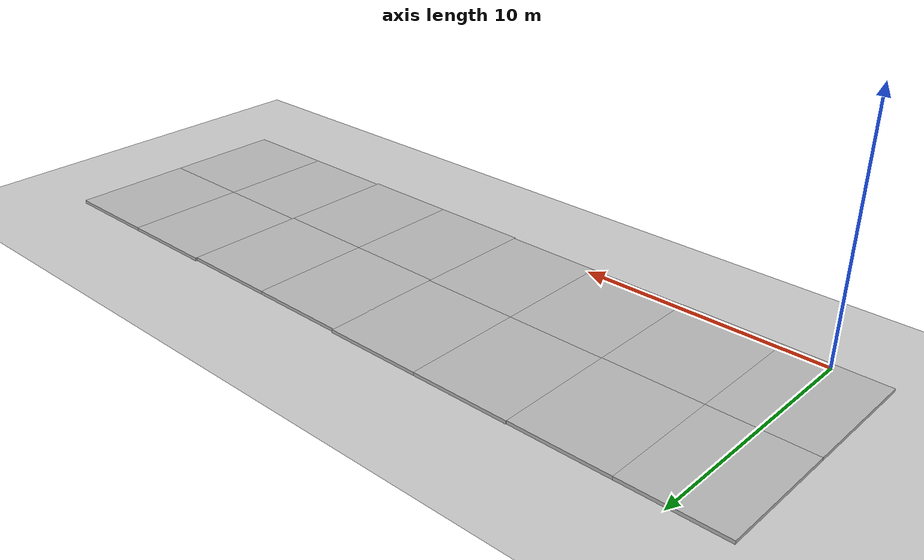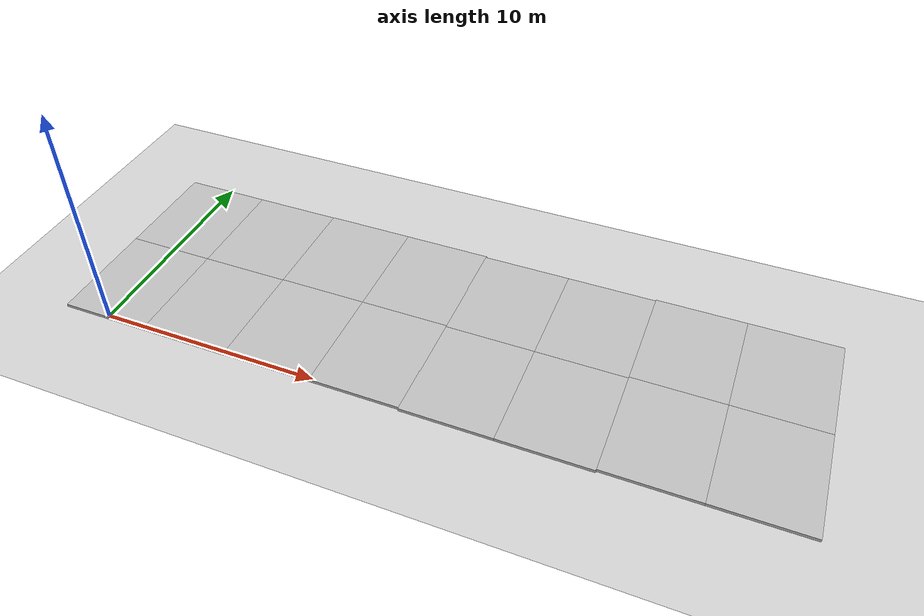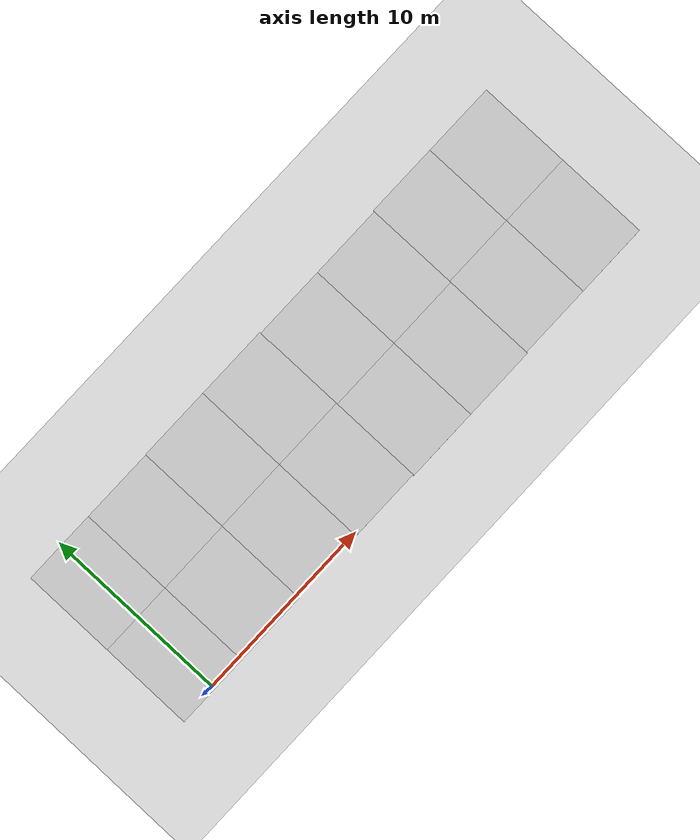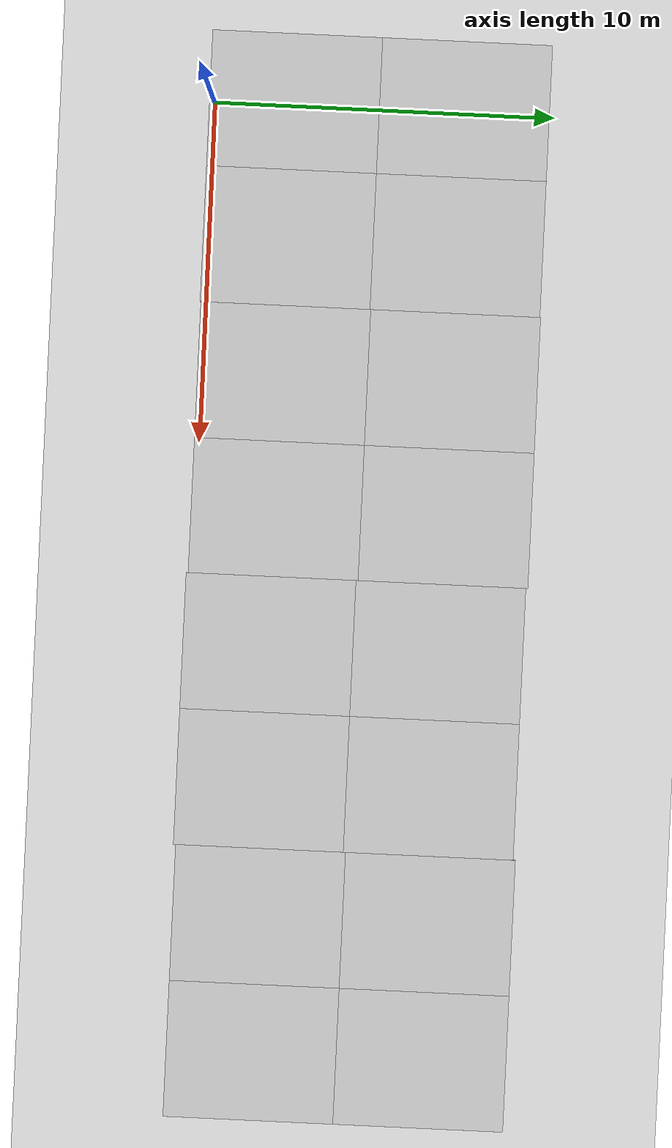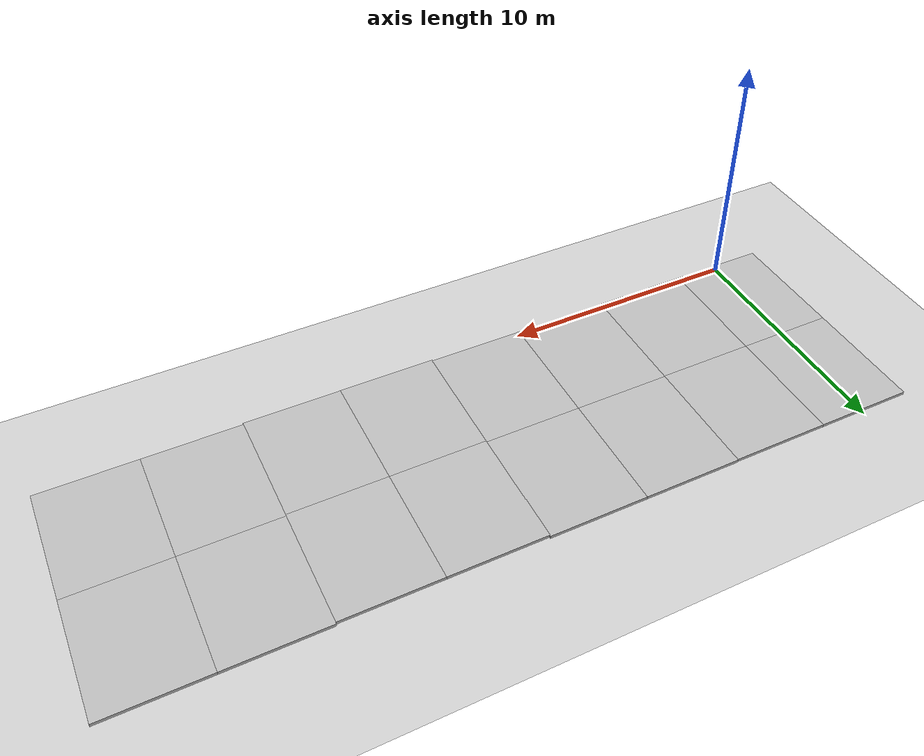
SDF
<sdf version="1.6">
 <world name="default">
  <light name="sun" type="directional">
   <pose>0 0 10 0 -0 0</pose>
   <diffuse>0.8 0.8 0.8 1</diffuse>
   <specular>0.1 0.1 0.1 1</specular>
   <attenuation>
    <range>1000</range>
    <constant>0.9</constant>
    <linear>0.01</linear>
    <quadratic>0.001</quadratic>
   </attenuation>
   <direction>-0.5 0.5 -1</direction>
  </light>
  <model name="ground_plane">
   <static>1</static>
   <link name="link">
    <collision name="collision">
     <geometry><plane><normal>0 0 1</normal><size>100 100</size></plane></geometry>
     <surface><friction><ode><mu>100</mu><mu2>50</mu2></ode></friction></surface>
    </collision>
    <visual name="visual">
     <cast_shadows>0</cast_shadows>
     <geometry><plane><normal>0 0 1</normal><size>100 100</size></plane></geometry>
     <material>
      <script><uri>file://media/materials/scripts/gazebo.material</uri><name>Gazebo/Grey</name></script>
     </material>
    </visual>
   </link>
  </model>
  <gravity>0 0 -9.8</gravity>
  <magnetic_field>6e-06 2.3e-05 -4.2e-05</magnetic_field>
  <atmosphere type="adiabatic"/>
  <physics name="default_physics" default="0" type="ode">
   <max_step_size>0.001</max_step_size>
   <real_time_factor>1</real_time_factor>
   <real_time_update_rate>1000</real_time_update_rate>
  </physics>
  <scene><ambient>0.4 0.4 0.4 1</ambient><background>0.7 0.7 0.7 1</background><shadows>1</shadows></scene>
  <spherical_coordinates>
   <surface_model>EARTH_WGS84</surface_model>
   <latitude_deg>0</latitude_deg>
   <longitude_deg>0</longitude_deg>
   <elevation>0</elevation>
   <heading_deg>0</heading_deg>
  </spherical_coordinates>
  <model name="small_plant_0">
   <pose>4 2.00183 -5886.19 0 -0 0</pose>
   <link name="link_0">
    <pose>4 2.00183 0.110674 0 -0 0</pose>
    <inertial>
     <inertia><ixx>1</ixx><ixy>0</ixy><ixz>0</ixz><iyy>1</iyy><iyz>0</iyz><izz>1</izz></inertia>
     <mass>1</mass>
    </inertial>
   </link>
  </model>
  <model name="small_plant_1">
   <pose>4.2027 2.00204 -5886.19 0 -0 0</pose>
   <link name="link_0">
    <pose>4.2027 2.00204 0.110674 0 -0 0</pose>
    <inertial>
     <inertia><ixx>1</ixx><ixy>0</ixy><ixz>0</ixz><iyy>1</iyy><iyz>0</iyz><izz>1</izz></inertia>
     <mass>1</mass>
    </inertial>
   </link>
  </model>
  <model name="small_plant_2">
   <pose>4.40541 2.00441 -5885.85 0 -0 0</pose>
   <link name="link_0">
    <pose>4.40541 2.00441 0.110674 0 -0 0</pose>
    <inertial>
     <inertia><ixx>1</ixx><ixy>0</ixy><ixz>0</ixz><iyy>1</iyy><iyz>0</iyz><izz>1</izz></inertia>
     <mass>1</mass>
    </inertial>
   </link>
  </model>
  <model name="small_plant_3">
   <pose>4.60811 2.00125 -5885.51 0 -0 0</pose>
   <link name="link_0">
    <pose>4.60811 2.00125 0.110674 0 -0 0</pose>
    <inertial>
     <inertia><ixx>1</ixx><ixy>0</ixy><ixz>0</ixz><iyy>1</iyy><iyz>0</iyz><izz>1</izz></inertia>
     <mass>1</mass>
    </inertial>
   </link>
  </model>
  <model name="small_plant_4">
   <pose>4.81081 2.00254 -5885.17 0 -0 0</pose>
   <link name="link_0">
    <pose>4.81081 2.00254 0.110674 0 -0 0</pose>
    <inertial>
     <inertia><ixx>1</ixx><ixy>0</ixy><ixz>0</ixz><iyy>1</iyy><iyz>0</iyz><izz>1</izz></inertia>
     <mass>1</mass>
    </inertial>
   </link>
  </model>
  <model name="small_plant_5">
   <pose>5.01351 2.00033 -5884.83 0 -0 0</pose>
   <link name="link_0">
    <pose>5.01351 2.00033 0.110674 0 -0 0</pose>
    <inertial>
     <inertia><ixx>1</ixx><ixy>0</ixy><ixz>0</ixz><iyy>1</iyy><iyz>0</iyz><izz>1</izz></inertia>
     <mass>1</mass>
    </inertial>
   </link>
  </model>
  <model name="small_plant_6">
   <pose>5.21622 2.00339 -5884.83 0 -0 0</pose>
   <link name="link_0">
    <pose>5.21622 2.00339 0.110674 0 -0 0</pose>
    <inertial>
     <inertia><ixx>1</ixx><ixy>0</ixy><ixz>0</ixz><iyy>1</iyy><iyz>0</iyz><izz>1</izz></inertia>
     <mass>1</mass>
    </inertial>
   </link>
  </model>
  <model name="small_plant_7">
   <pose>5.41892 2.00548 -5884.83 0 -0 0</pose>
   <link name="link_0">
    <pose>5.41892 2.00548 0.110674 0 -0 0</pose>
    <inertial>
     <inertia><ixx>1</ixx><ixy>0</ixy><ixz>0</ixz><iyy>1</iyy><iyz>0</iyz><izz>1</izz></inertia>
     <mass>1</mass>
    </inertial>
   </link>
  </model>
  <model name="small_plant_8">
   <pose>5.62162 2.00516 -5884.49 0 -0 0</pose>
   <link name="link_0">
    <pose>5.62162 2.00516 0.110674 0 -0 0</pose>
    <inertial>
     <inertia><ixx>1</ixx><ixy>0</ixy><ixz>0</ixz><iyy>1</iyy><iyz>0</iyz><izz>1</izz></inertia>
     <mass>1</mass>
    </inertial>
   </link>
  </model>
  <model name="small_plant_9">
   <pose>5.82432 2.00312 -5884.49 0 -0 0</pose>
   <link name="link_0">
    <pose>5.82432 2.00312 0.110674 0 -0 0</pose>
    <inertial>
     <inertia><ixx>1</ixx><ixy>0</ixy><ixz>0</ixz><iyy>1</iyy><iyz>0</iyz><izz>1</izz></inertia>
     <mass>1</mass>
    </inertial>
   </link>
  </model>
  <model name="small_plant_10">
   <pose>6.02703 2.00351 -5886.19 0 -0 0</pose>
   <link name="link_0">
    <pose>6.02703 2.00351 0.110674 0 -0 0</pose>
    <inertial>
     <inertia><ixx>1</ixx><ixy>0</ixy><ixz>0</ixz><iyy>1</iyy><iyz>0</iyz><izz>1</izz></inertia>
     <mass>1</mass>
    </inertial>
   </link>
  </model>
  <model name="small_plant_11">
   <pose>6.22973 2.00381 -5886.19 0 -0 0</pose>
   <link name="link_0">
    <pose>6.22973 2.00381 0.110674 0 -0 0</pose>
    <inertial>
     <inertia><ixx>1</ixx><ixy>0</ixy><ixz>0</ixz><iyy>1</iyy><iyz>0</iyz><izz>1</izz></inertia>
     <mass>1</mass>
    </inertial>
   </link>
  </model>
  <model name="small_plant_12">
   <pose>6.43243 2.00842 -5886.19 0 -0 0</pose>
   <link name="link_0">
    <pose>6.43243 2.00842 0.110674 0 -0 0</pose>
    <inertial>
     <inertia><ixx>1</ixx><ixy>0</ixy><ixz>0</ixz><iyy>1</iyy><iyz>0</iyz><izz>1</izz></inertia>
     <mass>1</mass>
    </inertial>
   </link>
  </model>
  <model name="small_plant_13">
   <pose>6.63514 2.001 -5886.19 0 -0 0</pose>
   <link name="link_0">
    <pose>6.63514 2.001 0.110674 0 -0 0</pose>
    <inertial>
     <inertia><ixx>1</ixx><ixy>0</ixy><ixz>0</ixz><iyy>1</iyy><iyz>0</iyz><izz>1</izz></inertia>
     <mass>1</mass>
    </inertial>
   </link>
  </model>
  <model name="small_plant_14">
   <pose>6.83784 2.00013 -5886.19 0 -0 0</pose>
   <link name="link_0">
    <pose>6.83784 2.00013 0.110674 0 -0 0</pose>
    <inertial>
     <inertia><ixx>1</ixx><ixy>0</ixy><ixz>0</ixz><iyy>1</iyy><iyz>0</iyz><izz>1</izz></inertia>
     <mass>1</mass>
    </inertial>
   </link>
  </model>
  <model name="small_plant_15">
   <pose>7.04054 2.00567 -5886.19 0 -0 0</pose>
   <link name="link_0">
    <pose>7.04054 2.00567 0.110674 0 -0 0</pose>
    <inertial>
     <inertia><ixx>1</ixx><ixy>0</ixy><ixz>0</ixz><iyy>1</iyy><iyz>0</iyz><izz>1</izz></inertia>
     <mass>1</mass>
    </inertial>
   </link>
  </model>
  <model name="small_plant_16">
   <pose>7.24324 2.00279 -5885.85 0 -0 0</pose>
   <link name="link_0">
    <pose>7.24324 2.00279 0.110674 0 -0 0</pose>
    <inertial>
     <inertia><ixx>1</ixx><ixy>0</ixy><ixz>0</ixz><iyy>1</iyy><iyz>0</iyz><izz>1</izz></inertia>
     <mass>1</mass>
    </inertial>
   </link>
  </model>
  <model name="small_plant_17">
   <pose>7.44595 2.00203 -5885.85 0 -0 0</pose>
   <link name="link_0">
    <pose>7.44595 2.00203 0.110674 0 -0 0</pose>
    <inertial>
     <inertia><ixx>1</ixx><ixy>0</ixy><ixz>0</ixz><iyy>1</iyy><iyz>0</iyz><izz>1</izz></inertia>
     <mass>1</mass>
    </inertial>
   </link>
  </model>
  <model name="small_plant_18">
   <pose>7.64865 2.00257 -5885.85 0 -0 0</pose>
   <link name="link_0">
    <pose>7.64865 2.00257 0.110674 0 -0 0</pose>
    <inertial>
     <inertia><ixx>1</ixx><ixy>0</ixy><ixz>0</ixz><iyy>1</iyy><iyz>0</iyz><izz>1</izz></inertia>
     <mass>1</mass>
    </inertial>
   </link>
  </model>
  <model name="small_plant_19">
   <pose>7.85135 2.01017 -5885.85 0 -0 0</pose>
   <link name="link_0">
    <pose>7.85135 2.01017 0.110674 0 -0 0</pose>
    <inertial>
     <inertia><ixx>1</ixx><ixy>0</ixy><ixz>0</ixz><iyy>1</iyy><iyz>0</iyz><izz>1</izz></inertia>
     <mass>1</mass>
    </inertial>
   </link>
  </model>
  <model name="small_plant_20">
   <pose>8.05405 2.00151 -5885.85 0 -0 0</pose>
   <link name="link_0">
    <pose>8.05405 2.00151 0.110674 0 -0 0</pose>
    <inertial>
     <inertia><ixx>1</ixx><ixy>0</ixy><ixz>0</ixz><iyy>1</iyy><iyz>0</iyz><izz>1</izz></inertia>
     <mass>1</mass>
    </inertial>
   </link>
  </model>
  <model name="small_plant_21">
   <pose>8.25676 2.00266 -5885.85 0 -0 0</pose>
   <link name="link_0">
    <pose>8.25676 2.00266 0.110674 0 -0 0</pose>
    <inertial>
     <inertia><ixx>1</ixx><ixy>0</ixy><ixz>0</ixz><iyy>1</iyy><iyz>0</iyz><izz>1</izz></inertia>
     <mass>1</mass>
    </inertial>
   </link>
  </model>
  <model name="small_plant_22">
   <pose>8.45946 2.00404 -5885.85 0 -0 0</pose>
   <link name="link_0">
    <pose>8.45946 2.00404 0.110674 0 -0 0</pose>
    <inertial>
     <inertia><ixx>1</ixx><ixy>0</ixy><ixz>0</ixz><iyy>1</iyy><iyz>0</iyz><izz>1</izz></inertia>
     <mass>1</mass>
    </inertial>
   </link>
  </model>
  <model name="small_plant_23">
   <pose>8.66216 2.00073 -5885.85 0 -0 0</pose>
   <link name="link_0">
    <pose>8.66216 2.00073 0.110674 0 -0 0</pose>
    <inertial>
     <inertia><ixx>1</ixx><ixy>0</ixy><ixz>0</ixz><iyy>1</iyy><iyz>0</iyz><izz>1</izz></inertia>
     <mass>1</mass>
    </inertial>
   </link>
  </model>
  <model name="small_plant_24">
   <pose>8.86486 2.00329 -5885.85 0 -0 0</pose>
   <link name="link_0">
    <pose>8.86486 2.00329 0.110674 0 -0 0</pose>
    <inertial>
     <inertia><ixx>1</ixx><ixy>0</ixy><ixz>0</ixz><iyy>1</iyy><iyz>0</iyz><izz>1</izz></inertia>
     <mass>1</mass>
    </inertial>
   </link>
  </model>
  <model name="small_plant_25">
   <pose>9.06757 2.00418 -5885.85 0 -0 0</pose>
   <link name="link_0">
    <pose>9.06757 2.00418 0.110674 0 -0 0</pose>
    <inertial>
     <inertia><ixx>1</ixx><ixy>0</ixy><ixz>0</ixz><iyy>1</iyy><iyz>0</iyz><izz>1</izz></inertia>
     <mass>1</mass>
    </inertial>
   </link>
  </model>
  <model name="small_plant_26">
   <pose>9.27027 2.00492 -5885.85 0 -0 0</pose>
   <link name="link_0">
    <pose>9.27027 2.00492 0.110674 0 -0 0</pose>
    <inertial>
     <inertia><ixx>1</ixx><ixy>0</ixy><ixz>0</ixz><iyy>1</iyy><iyz>0</iyz><izz>1</izz></inertia>
     <mass>1</mass>
    </inertial>
   </link>
  </model>
  <model name="small_plant_27">
   <pose>9.47297 2.00561 -5885.51 0 -0 0</pose>
   <link name="link_0">
    <pose>9.47297 2.00561 0.110674 0 -0 0</pose>
    <inertial>
     <inertia><ixx>1</ixx><ixy>0</ixy><ixz>0</ixz><iyy>1</iyy><iyz>0</iyz><izz>1</izz></inertia>
     <mass>1</mass>
    </inertial>
   </link>
  </model>
  <model name="small_plant_28">
   <pose>9.67568 2.00465 -5885.51 0 -0 0</pose>
   <link name="link_0">
    <pose>9.67568 2.00465 0.110674 0 -0 0</pose>
    <inertial>
     <inertia><ixx>1</ixx><ixy>0</ixy><ixz>0</ixz><iyy>1</iyy><iyz>0</iyz><izz>1</izz></inertia>
     <mass>1</mass>
    </inertial>
   </link>
  </model>
  <model name="small_plant_29">
   <pose>9.87838 2.00073 -5885.51 0 -0 0</pose>
   <link name="link_0">
    <pose>9.87838 2.00073 0.110674 0 -0 0</pose>
    <inertial>
     <inertia><ixx>1</ixx><ixy>0</ixy><ixz>0</ixz><iyy>1</iyy><iyz>0</iyz><izz>1</izz></inertia>
     <mass>1</mass>
    </inertial>
   </link>
  </model>
  <model name="small_plant_30">
   <pose>10.0811 2.00253 -5885.51 0 -0 0</pose>
   <link name="link_0">
    <pose>10.0811 2.00253 0.110674 0 -0 0</pose>
    <inertial>
     <inertia><ixx>1</ixx><ixy>0</ixy><ixz>0</ixz><iyy>1</iyy><iyz>0</iyz><izz>1</izz></inertia>
     <mass>1</mass>
    </inertial>
   </link>
  </model>
  <model name="small_plant_31">
   <pose>10.2838 2.00343 -5885.51 0 -0 0</pose>
   <link name="link_0">
    <pose>10.2838 2.00343 0.110674 0 -0 0</pose>
    <inertial>
     <inertia><ixx>1</ixx><ixy>0</ixy><ixz>0</ixz><iyy>1</iyy><iyz>0</iyz><izz>1</izz></inertia>
     <mass>1</mass>
    </inertial>
   </link>
  </model>
  <model name="small_plant_32">
   <pose>10.4865 2.01132 -5885.51 0 -0 0</pose>
   <link name="link_0">
    <pose>10.4865 2.01132 0.110674 0 -0 0</pose>
    <inertial>
     <inertia><ixx>1</ixx><ixy>0</ixy><ixz>0</ixz><iyy>1</iyy><iyz>0</iyz><izz>1</izz></inertia>
     <mass>1</mass>
    </inertial>
   </link>
  </model>
  <model name="small_plant_33">
   <pose>10.6892 2.00544 -5885.51 0 -0 0</pose>
   <link name="link_0">
    <pose>10.6892 2.00544 0.110674 0 -0 0</pose>
    <inertial>
     <inertia><ixx>1</ixx><ixy>0</ixy><ixz>0</ixz><iyy>1</iyy><iyz>0</iyz><izz>1</izz></inertia>
     <mass>1</mass>
    </inertial>
   </link>
  </model>
  <model name="small_plant_34">
   <pose>10.8919 2.00651 -5885.17 0 -0 0</pose>
   <link name="link_0">
    <pose>10.8919 2.00651 0.110674 0 -0 0</pose>
    <inertial>
     <inertia><ixx>1</ixx><ixy>0</ixy><ixz>0</ixz><iyy>1</iyy><iyz>0</iyz><izz>1</izz></inertia>
     <mass>1</mass>
    </inertial>
   </link>
  </model>
  <model name="small_plant_35">
   <pose>11.0946 2.00044 -5885.17 0 -0 0</pose>
   <link name="link_0">
    <pose>11.0946 2.00044 0.110674 0 -0 0</pose>
    <inertial>
     <inertia><ixx>1</ixx><ixy>0</ixy><ixz>0</ixz><iyy>1</iyy><iyz>0</iyz><izz>1</izz></inertia>
     <mass>1</mass>
    </inertial>
   </link>
  </model>
  <model name="small_plant_36">
   <pose>11.2973 2.00607 -5885.17 0 -0 0</pose>
   <link name="link_0">
    <pose>11.2973 2.00607 0.110674 0 -0 0</pose>
    <inertial>
     <inertia><ixx>1</ixx><ixy>0</ixy><ixz>0</ixz><iyy>1</iyy><iyz>0</iyz><izz>1</izz></inertia>
     <mass>1</mass>
    </inertial>
   </link>
  </model>
  <model name="small_plant_37">
   <pose>11.5 2.0009 -5885.17 0 -0 0</pose>
   <link name="link_0">
    <pose>11.5 2.0009 0.110674 0 -0 0</pose>
    <inertial>
     <inertia><ixx>1</ixx><ixy>0</ixy><ixz>0</ixz><iyy>1</iyy><iyz>0</iyz><izz>1</izz></inertia>
     <mass>1</mass>
    </inertial>
   </link>
  </model>
  <model name="small_plant_38">
   <pose>11.7027 2.00243 -5885.17 0 -0 0</pose>
   <link name="link_0">
    <pose>11.7027 2.00243 0.110674 0 -0 0</pose>
    <inertial>
     <inertia><ixx>1</ixx><ixy>0</ixy><ixz>0</ixz><iyy>1</iyy><iyz>0</iyz><izz>1</izz></inertia>
     <mass>1</mass>
    </inertial>
   </link>
  </model>
  <model name="small_plant_39">
   <pose>11.9054 2.00202 -5885.17 0 -0 0</pose>
   <link name="link_0">
    <pose>11.9054 2.00202 0.110674 0 -0 0</pose>
    <inertial>
     <inertia><ixx>1</ixx><ixy>0</ixy><ixz>0</ixz><iyy>1</iyy><iyz>0</iyz><izz>1</izz></inertia>
     <mass>1</mass>
    </inertial>
   </link>
  </model>
  <model name="small_plant_40">
   <pose>12.1081 2.00342 -5885.17 0 -0 0</pose>
   <link name="link_0">
    <pose>12.1081 2.00342 0.110674 0 -0 0</pose>
    <inertial>
     <inertia><ixx>1</ixx><ixy>0</ixy><ixz>0</ixz><iyy>1</iyy><iyz>0</iyz><izz>1</izz></inertia>
     <mass>1</mass>
    </inertial>
   </link>
  </model>
  <model name="small_plant_41">
   <pose>12.3108 2.00137 -5884.83 0 -0 0</pose>
   <link name="link_0">
    <pose>12.3108 2.00137 0.110674 0 -0 0</pose>
    <inertial>
     <inertia><ixx>1</ixx><ixy>0</ixy><ixz>0</ixz><iyy>1</iyy><iyz>0</iyz><izz>1</izz></inertia>
     <mass>1</mass>
    </inertial>
   </link>
  </model>
  <model name="small_plant_42">
   <pose>12.5135 2.00158 -5884.83 0 -0 0</pose>
   <link name="link_0">
    <pose>12.5135 2.00158 0.110674 0 -0 0</pose>
    <inertial>
     <inertia><ixx>1</ixx><ixy>0</ixy><ixz>0</ixz><iyy>1</iyy><iyz>0</iyz><izz>1</izz></inertia>
     <mass>1</mass>
    </inertial>
   </link>
  </model>
  <model name="small_plant_43">
   <pose>12.7162 2.00119 -5884.83 0 -0 0</pose>
   <link name="link_0">
    <pose>12.7162 2.00119 0.110674 0 -0 0</pose>
    <inertial>
     <inertia><ixx>1</ixx><ixy>0</ixy><ixz>0</ixz><iyy>1</iyy><iyz>0</iyz><izz>1</izz></inertia>
     <mass>1</mass>
    </inertial>
   </link>
  </model>
  <model name="small_plant_44">
   <pose>12.9189 2.00198 -5884.83 0 -0 0</pose>
   <link name="link_0">
    <pose>12.9189 2.00198 0.110674 0 -0 0</pose>
    <inertial>
     <inertia><ixx>1</ixx><ixy>0</ixy><ixz>0</ixz><iyy>1</iyy><iyz>0</iyz><izz>1</izz></inertia>
     <mass>1</mass>
    </inertial>
   </link>
  </model>
  <model name="small_plant_45">
   <pose>13.1216 2.00175 -5884.83 0 -0 0</pose>
   <link name="link_0">
    <pose>13.1216 2.00175 0.110674 0 -0 0</pose>
    <inertial>
     <inertia><ixx>1</ixx><ixy>0</ixy><ixz>0</ixz><iyy>1</iyy><iyz>0</iyz><izz>1</izz></inertia>
     <mass>1</mass>
    </inertial>
   </link>
  </model>
  <model name="small_plant_46">
   <pose>13.3243 2.00303 -5884.83 0 -0 0</pose>
   <link name="link_0">
    <pose>13.3243 2.00303 0.110674 0 -0 0</pose>
    <inertial>
     <inertia><ixx>1</ixx><ixy>0</ixy><ixz>0</ixz><iyy>1</iyy><iyz>0</iyz><izz>1</izz></inertia>
     <mass>1</mass>
    </inertial>
   </link>
  </model>
  <model name="small_plant_47">
   <pose>13.527 2.00227 -5884.83 0 -0 0</pose>
   <link name="link_0">
    <pose>13.527 2.00227 0.110674 0 -0 0</pose>
    <inertial>
     <inertia><ixx>1</ixx><ixy>0</ixy><ixz>0</ixz><iyy>1</iyy><iyz>0</iyz><izz>1</izz></inertia>
     <mass>1</mass>
    </inertial>
   </link>
  </model>
  <model name="small_plant_48">
   <pose>13.7297 2.00135 -5884.83 0 -0 0</pose>
   <link name="link_0">
    <pose>13.7297 2.00135 0.110674 0 -0 0</pose>
    <inertial>
     <inertia><ixx>1</ixx><ixy>0</ixy><ixz>0</ixz><iyy>1</iyy><iyz>0</iyz><izz>1</izz></inertia>
     <mass>1</mass>
    </inertial>
   </link>
  </model>
  <model name="small_plant_49">
   <pose>13.9324 2.00479 -5884.83 0 -0 0</pose>
   <link name="link_0">
    <pose>13.9324 2.00479 0.110674 0 -0 0</pose>
    <inertial>
     <inertia><ixx>1</ixx><ixy>0</ixy><ixz>0</ixz><iyy>1</iyy><iyz>0</iyz><izz>1</izz></inertia>
     <mass>1</mass>
    </inertial>
   </link>
  </model>
  <model name="small_plant_50">
   <pose>14.1351 2.00163 -5884.83 0 -0 0</pose>
   <link name="link_0">
    <pose>14.1351 2.00163 0.110674 0 -0 0</pose>
    <inertial>
     <inertia><ixx>1</ixx><ixy>0</ixy><ixz>0</ixz><iyy>1</iyy><iyz>0</iyz><izz>1</izz></inertia>
     <mass>1</mass>
    </inertial>
   </link>
  </model>
  <model name="small_plant_51">
   <pose>14.3378 2.00023 -5884.83 0 -0 0</pose>
   <link name="link_0">
    <pose>14.3378 2.00023 0.110674 0 -0 0</pose>
    <inertial>
     <inertia><ixx>1</ixx><ixy>0</ixy><ixz>0</ixz><iyy>1</iyy><iyz>0</iyz><izz>1</izz></inertia>
     <mass>1</mass>
    </inertial>
   </link>
  </model>
  <model name="small_plant_52">
   <pose>14.5405 2.00127 -5884.83 0 -0 0</pose>
   <link name="link_0">
    <pose>14.5405 2.00127 0.110674 0 -0 0</pose>
    <inertial>
     <inertia><ixx>1</ixx><ixy>0</ixy><ixz>0</ixz><iyy>1</iyy><iyz>0</iyz><izz>1</izz></inertia>
     <mass>1</mass>
    </inertial>
   </link>
  </model>
  <model name="small_plant_53">
   <pose>14.7432 2.00156 -5884.83 0 -0 0</pose>
   <link name="link_0">
    <pose>14.7432 2.00156 0.110674 0 -0 0</pose>
    <inertial>
     <inertia><ixx>1</ixx><ixy>0</ixy><ixz>0</ixz><iyy>1</iyy><iyz>0</iyz><izz>1</izz></inertia>
     <mass>1</mass>
    </inertial>
   </link>
  </model>
  <model name="small_plant_54">
   <pose>14.9459 2.00341 -5884.83 0 -0 0</pose>
   <link name="link_0">
    <pose>14.9459 2.00341 0.110674 0 -0 0</pose>
    <inertial>
     <inertia><ixx>1</ixx><ixy>0</ixy><ixz>0</ixz><iyy>1</iyy><iyz>0</iyz><izz>1</izz></inertia>
     <mass>1</mass>
    </inertial>
   </link>
  </model>
  <model name="small_plant_55">
   <pose>15.1486 2.00368 -5884.83 0 -0 0</pose>
   <link name="link_0">
    <pose>15.1486 2.00368 0.110674 0 -0 0</pose>
    <inertial>
     <inertia><ixx>1</ixx><ixy>0</ixy><ixz>0</ixz><iyy>1</iyy><iyz>0</iyz><izz>1</izz></inertia>
     <mass>1</mass>
    </inertial>
   </link>
  </model>
  <model name="small_plant_56">
   <pose>15.3514 2.00933 -5884.83 0 -0 0</pose>
   <link name="link_0">
    <pose>15.3514 2.00933 0.110674 0 -0 0</pose>
    <inertial>
     <inertia><ixx>1</ixx><ixy>0</ixy><ixz>0</ixz><iyy>1</iyy><iyz>0</iyz><izz>1</izz></inertia>
     <mass>1</mass>
    </inertial>
   </link>
  </model>
  <model name="small_plant_57">
   <pose>15.5541 2.00016 -5884.83 0 -0 0</pose>
   <link name="link_0">
    <pose>15.5541 2.00016 0.110674 0 -0 0</pose>
    <inertial>
     <inertia><ixx>1</ixx><ixy>0</ixy><ixz>0</ixz><iyy>1</iyy><iyz>0</iyz><izz>1</izz></inertia>
     <mass>1</mass>
    </inertial>
   </link>
  </model>
  <model name="small_plant_58">
   <pose>15.7568 2.00107 -5884.83 0 -0 0</pose>
   <link name="link_0">
    <pose>15.7568 2.00107 0.110674 0 -0 0</pose>
    <inertial>
     <inertia><ixx>1</ixx><ixy>0</ixy><ixz>0</ixz><iyy>1</iyy><iyz>0</iyz><izz>1</izz></inertia>
     <mass>1</mass>
    </inertial>
   </link>
  </model>
  <model name="small_plant_59">
   <pose>15.9595 2.00207 -5884.83 0 -0 0</pose>
   <link name="link_0">
    <pose>15.9595 2.00207 0.110674 0 -0 0</pose>
    <inertial>
     <inertia><ixx>1</ixx><ixy>0</ixy><ixz>0</ixz><iyy>1</iyy><iyz>0</iyz><izz>1</izz></inertia>
     <mass>1</mass>
    </inertial>
   </link>
  </model>
  <model name="small_plant_60">
   <pose>16.1622 2.01288 -5884.83 0 -0 0</pose>
   <link name="link_0">
    <pose>16.1622 2.01288 0.110674 0 -0 0</pose>
    <inertial>
     <inertia><ixx>1</ixx><ixy>0</ixy><ixz>0</ixz><iyy>1</iyy><iyz>0</iyz><izz>1</izz></inertia>
     <mass>1</mass>
    </inertial>
   </link>
  </model>
  <model name="small_plant_61">
   <pose>16.3649 2.00049 -5884.83 0 -0 0</pose>
   <link name="link_0">
    <pose>16.3649 2.00049 0.110674 0 -0 0</pose>
    <inertial>
     <inertia><ixx>1</ixx><ixy>0</ixy><ixz>0</ixz><iyy>1</iyy><iyz>0</iyz><izz>1</izz></inertia>
     <mass>1</mass>
    </inertial>
   </link>
  </model>
  <model name="small_plant_62">
   <pose>16.5676 2.00442 -5884.83 0 -0 0</pose>
   <link name="link_0">
    <pose>16.5676 2.00442 0.110674 0 -0 0</pose>
    <inertial>
     <inertia><ixx>1</ixx><ixy>0</ixy><ixz>0</ixz><iyy>1</iyy><iyz>0</iyz><izz>1</izz></inertia>
     <mass>1</mass>
    </inertial>
   </link>
  </model>
  <model name="small_plant_63">
   <pose>16.7703 2.00171 -5884.83 0 -0 0</pose>
   <link name="link_0">
    <pose>16.7703 2.00171 0.110674 0 -0 0</pose>
    <inertial>
     <inertia><ixx>1</ixx><ixy>0</ixy><ixz>0</ixz><iyy>1</iyy><iyz>0</iyz><izz>1</izz></inertia>
     <mass>1</mass>
    </inertial>
   </link>
  </model>
  <model name="small_plant_64">
   <pose>16.973 2.00441 -5884.83 0 -0 0</pose>
   <link name="link_0">
    <pose>16.973 2.00441 0.110674 0 -0 0</pose>
    <inertial>
     <inertia><ixx>1</ixx><ixy>0</ixy><ixz>0</ixz><iyy>1</iyy><iyz>0</iyz><izz>1</izz></inertia>
     <mass>1</mass>
    </inertial>
   </link>
  </model>
  <model name="small_plant_65">
   <pose>17.1757 2.00241 -5884.83 0 -0 0</pose>
   <link name="link_0">
    <pose>17.1757 2.00241 0.110674 0 -0 0</pose>
    <inertial>
     <inertia><ixx>1</ixx><ixy>0</ixy><ixz>0</ixz><iyy>1</iyy><iyz>0</iyz><izz>1</izz></inertia>
     <mass>1</mass>
    </inertial>
   </link>
  </model>
  <model name="small_plant_66">
   <pose>17.3784 2.00196 -5884.83 0 -0 0</pose>
   <link name="link_0">
    <pose>17.3784 2.00196 0.110674 0 -0 0</pose>
    <inertial>
     <inertia><ixx>1</ixx><ixy>0</ixy><ixz>0</ixz><iyy>1</iyy><iyz>0</iyz><izz>1</izz></inertia>
     <mass>1</mass>
    </inertial>
   </link>
  </model>
  <model name="small_plant_67">
   <pose>17.5811 2.00016 -5884.83 0 -0 0</pose>
   <link name="link_0">
    <pose>17.5811 2.00016 0.110674 0 -0 0</pose>
    <inertial>
     <inertia><ixx>1</ixx><ixy>0</ixy><ixz>0</ixz><iyy>1</iyy><iyz>0</iyz><izz>1</izz></inertia>
     <mass>1</mass>
    </inertial>
   </link>
  </model>
  <model name="small_plant_68">
   <pose>17.7838 2.00074 -5884.83 0 -0 0</pose>
   <link name="link_0">
    <pose>17.7838 2.00074 0.110674 0 -0 0</pose>
    <inertial>
     <inertia><ixx>1</ixx><ixy>0</ixy><ixz>0</ixz><iyy>1</iyy><iyz>0</iyz><izz>1</izz></inertia>
     <mass>1</mass>
    </inertial>
   </link>
  </model>
  <model name="small_plant_69">
   <pose>17.9865 2.00158 -5884.83 0 -0 0</pose>
   <link name="link_0">
    <pose>17.9865 2.00158 0.110674 0 -0 0</pose>
    <inertial>
     <inertia><ixx>1</ixx><ixy>0</ixy><ixz>0</ixz><iyy>1</iyy><iyz>0</iyz><izz>1</izz></inertia>
     <mass>1</mass>
    </inertial>
   </link>
  </model>
  <model name="small_plant_70">
   <pose>18.1892 2.00712 -5884.83 0 -0 0</pose>
   <link name="link_0">
    <pose>18.1892 2.00712 0.110674 0 -0 0</pose>
    <inertial>
     <inertia><ixx>1</ixx><ixy>0</ixy><ixz>0</ixz><iyy>1</iyy><iyz>0</iyz><izz>1</izz></inertia>
     <mass>1</mass>
    </inertial>
   </link>
  </model>
  <model name="small_plant_71">
   <pose>18.3919 2.00215 -5884.83 0 -0 0</pose>
   <link name="link_0">
    <pose>18.3919 2.00215 0.110674 0 -0 0</pose>
    <inertial>
     <inertia><ixx>1</ixx><ixy>0</ixy><ixz>0</ixz><iyy>1</iyy><iyz>0</iyz><izz>1</izz></inertia>
     <mass>1</mass>
    </inertial>
   </link>
  </model>
  <model name="small_plant_72">
   <pose>18.5946 2.00764 -5884.83 0 -0 0</pose>
   <link name="link_0">
    <pose>18.5946 2.00764 0.110674 0 -0 0</pose>
    <inertial>
     <inertia><ixx>1</ixx><ixy>0</ixy><ixz>0</ixz><iyy>1</iyy><iyz>0</iyz><izz>1</izz></inertia>
     <mass>1</mass>
    </inertial>
   </link>
  </model>
  <model name="small_plant_73">
   <pose>18.7973 2.00014 -5884.83 0 -0 0</pose>
   <link name="link_0">
    <pose>18.7973 2.00014 0.110674 0 -0 0</pose>
    <inertial>
     <inertia><ixx>1</ixx><ixy>0</ixy><ixz>0</ixz><iyy>1</iyy><iyz>0</iyz><izz>1</izz></inertia>
     <mass>1</mass>
    </inertial>
   </link>
  </model>
  <model name="small_plant_74">
   <pose>19 2.00299 -5884.83 0 -0 0</pose>
   <link name="link_0">
    <pose>19 2.00299 0.110674 0 -0 0</pose>
    <inertial>
     <inertia><ixx>1</ixx><ixy>0</ixy><ixz>0</ixz><iyy>1</iyy><iyz>0</iyz><izz>1</izz></inertia>
     <mass>1</mass>
    </inertial>
   </link>
  </model>
  <model name="small_plant_75">
   <pose>4 2.70716 -5884.83 0 -0 0</pose>
   <link name="link_0">
    <pose>4 2.70716 0.110674 0 -0 0</pose>
    <inertial>
     <inertia><ixx>1</ixx><ixy>0</ixy><ixz>0</ixz><iyy>1</iyy><iyz>0</iyz><izz>1</izz></inertia>
     <mass>1</mass>
    </inertial>
   </link>
  </model>
  <model name="small_plant_76">
   <pose>4.2027 2.70205 -5884.49 0 -0 0</pose>
   <link name="link_0">
    <pose>4.2027 2.70205 0.110674 0 -0 0</pose>
    <inertial>
     <inertia><ixx>1</ixx><ixy>0</ixy><ixz>0</ixz><iyy>1</iyy><iyz>0</iyz><izz>1</izz></inertia>
     <mass>1</mass>
    </inertial>
   </link>
  </model>
  <model name="small_plant_77">
   <pose>4.40541 2.70926 -5884.49 0 -0 0</pose>
   <link name="link_0">
    <pose>4.40541 2.70926 0.110674 0 -0 0</pose>
    <inertial>
     <inertia><ixx>1</ixx><ixy>0</ixy><ixz>0</ixz><iyy>1</iyy><iyz>0</iyz><izz>1</izz></inertia>
     <mass>1</mass>
    </inertial>
   </link>
  </model>
  <model name="small_plant_78">
   <pose>4.60811 2.70181 -5884.49 0 -0 0</pose>
   <link name="link_0">
    <pose>4.60811 2.70181 0.110674 0 -0 0</pose>
    <inertial>
     <inertia><ixx>1</ixx><ixy>0</ixy><ixz>0</ixz><iyy>1</iyy><iyz>0</iyz><izz>1</izz></inertia>
     <mass>1</mass>
    </inertial>
   </link>
  </model>
  <model name="small_plant_79">
   <pose>4.81081 2.70347 -5884.49 0 -0 0</pose>
   <link name="link_0">
    <pose>4.81081 2.70347 0.110674 0 -0 0</pose>
    <inertial>
     <inertia><ixx>1</ixx><ixy>0</ixy><ixz>0</ixz><iyy>1</iyy><iyz>0</iyz><izz>1</izz></inertia>
     <mass>1</mass>
    </inertial>
   </link>
  </model>
  <model name="small_plant_80">
   <pose>5.01351 2.70742 -5884.49 0 -0 0</pose>
   <link name="link_0">
    <pose>5.01351 2.70742 0.110674 0 -0 0</pose>
    <inertial>
     <inertia><ixx>1</ixx><ixy>0</ixy><ixz>0</ixz><iyy>1</iyy><iyz>0</iyz><izz>1</izz></inertia>
     <mass>1</mass>
    </inertial>
   </link>
  </model>
  <model name="small_plant_81">
   <pose>5.21622 2.70363 -5884.49 0 -0 0</pose>
   <link name="link_0">
    <pose>5.21622 2.70363 0.110674 0 -0 0</pose>
    <inertial>
     <inertia><ixx>1</ixx><ixy>0</ixy><ixz>0</ixz><iyy>1</iyy><iyz>0</iyz><izz>1</izz></inertia>
     <mass>1</mass>
    </inertial>
   </link>
  </model>
  <model name="small_plant_82">
   <pose>5.41892 2.70119 -5884.49 0 -0 0</pose>
   <link name="link_0">
    <pose>5.41892 2.70119 0.110674 0 -0 0</pose>
    <inertial>
     <inertia><ixx>1</ixx><ixy>0</ixy><ixz>0</ixz><iyy>1</iyy><iyz>0</iyz><izz>1</izz></inertia>
     <mass>1</mass>
    </inertial>
   </link>
  </model>
  <model name="small_plant_83">
   <pose>5.62162 2.70089 -5884.49 0 -0 0</pose>
   <link name="link_0">
    <pose>5.62162 2.70089 0.110674 0 -0 0</pose>
    <inertial>
     <inertia><ixx>1</ixx><ixy>0</ixy><ixz>0</ixz><iyy>1</iyy><iyz>0</iyz><izz>1</izz></inertia>
     <mass>1</mass>
    </inertial>
   </link>
  </model>
  <model name="small_plant_84">
   <pose>5.82432 2.70942 -5884.49 0 -0 0</pose>
   <link name="link_0">
    <pose>5.82432 2.70942 0.110674 0 -0 0</pose>
    <inertial>
     <inertia><ixx>1</ixx><ixy>0</ixy><ixz>0</ixz><iyy>1</iyy><iyz>0</iyz><izz>1</izz></inertia>
     <mass>1</mass>
    </inertial>
   </link>
  </model>
  <model name="small_plant_85">
   <pose>6.02703 2.70123 -5884.49 0 -0 0</pose>
   <link name="link_0">
    <pose>6.02703 2.70123 0.110674 0 -0 0</pose>
    <inertial>
     <inertia><ixx>1</ixx><ixy>0</ixy><ixz>0</ixz><iyy>1</iyy><iyz>0</iyz><izz>1</izz></inertia>
     <mass>1</mass>
    </inertial>
   </link>
  </model>
  <model name="small_plant_86">
   <pose>6.22973 2.7047 -5884.49 0 -0 0</pose>
   <link name="link_0">
    <pose>6.22973 2.7047 0.110674 0 -0 0</pose>
    <inertial>
     <inertia><ixx>1</ixx><ixy>0</ixy><ixz>0</ixz><iyy>1</iyy><iyz>0</iyz><izz>1</izz></inertia>
     <mass>1</mass>
    </inertial>
   </link>
  </model>
  <model name="small_plant_87">
   <pose>6.43243 2.70064 -5884.49 0 -0 0</pose>
   <link name="link_0">
    <pose>6.43243 2.70064 0.110674 0 -0 0</pose>
    <inertial>
     <inertia><ixx>1</ixx><ixy>0</ixy><ixz>0</ixz><iyy>1</iyy><iyz>0</iyz><izz>1</izz></inertia>
     <mass>1</mass>
    </inertial>
   </link>
  </model>
  <model name="small_plant_88">
   <pose>6.63514 2.70027 -5884.49 0 -0 0</pose>
   <link name="link_0">
    <pose>6.63514 2.70027 0.110674 0 -0 0</pose>
    <inertial>
     <inertia><ixx>1</ixx><ixy>0</ixy><ixz>0</ixz><iyy>1</iyy><iyz>0</iyz><izz>1</izz></inertia>
     <mass>1</mass>
    </inertial>
   </link>
  </model>
  <model name="small_plant_89">
   <pose>6.83784 2.70175 -5884.49 0 -0 0</pose>
   <link name="link_0">
    <pose>6.83784 2.70175 0.110674 0 -0 0</pose>
    <inertial>
     <inertia><ixx>1</ixx><ixy>0</ixy><ixz>0</ixz><iyy>1</iyy><iyz>0</iyz><izz>1</izz></inertia>
     <mass>1</mass>
    </inertial>
   </link>
  </model>
  <model name="small_plant_90">
   <pose>7.04054 2.70201 -5884.49 0 -0 0</pose>
   <link name="link_0">
    <pose>7.04054 2.70201 0.110674 0 -0 0</pose>
    <inertial>
     <inertia><ixx>1</ixx><ixy>0</ixy><ixz>0</ixz><iyy>1</iyy><iyz>0</iyz><izz>1</izz></inertia>
     <mass>1</mass>
    </inertial>
   </link>
  </model>
  <model name="small_plant_91">
   <pose>7.24324 2.70211 -5884.49 0 -0 0</pose>
   <link name="link_0">
    <pose>7.24324 2.70211 0.110674 0 -0 0</pose>
    <inertial>
     <inertia><ixx>1</ixx><ixy>0</ixy><ixz>0</ixz><iyy>1</iyy><iyz>0</iyz><izz>1</izz></inertia>
     <mass>1</mass>
    </inertial>
   </link>
  </model>
  <model name="small_plant_92">
   <pose>7.44595 2.70349 -5884.49 0 -0 0</pose>
   <link name="link_0">
    <pose>7.44595 2.70349 0.110674 0 -0 0</pose>
    <inertial>
     <inertia><ixx>1</ixx><ixy>0</ixy><ixz>0</ixz><iyy>1</iyy><iyz>0</iyz><izz>1</izz></inertia>
     <mass>1</mass>
    </inertial>
   </link>
  </model>
  <model name="small_plant_93">
   <pose>7.64865 2.70055 -5884.49 0 -0 0</pose>
   <link name="link_0">
    <pose>7.64865 2.70055 0.110674 0 -0 0</pose>
    <inertial>
     <inertia><ixx>1</ixx><ixy>0</ixy><ixz>0</ixz><iyy>1</iyy><iyz>0</iyz><izz>1</izz></inertia>
     <mass>1</mass>
    </inertial>
   </link>
  </model>
  <model name="small_plant_94">
   <pose>7.85135 2.70411 -5884.49 0 -0 0</pose>
   <link name="link_0">
    <pose>7.85135 2.70411 0.110674 0 -0 0</pose>
    <inertial>
     <inertia><ixx>1</ixx><ixy>0</ixy><ixz>0</ixz><iyy>1</iyy><iyz>0</iyz><izz>1</izz></inertia>
     <mass>1</mass>
    </inertial>
   </link>
  </model>
  <model name="small_plant_95">
   <pose>8.05405 2.70247 -5884.49 0 -0 0</pose>
   <link name="link_0">
    <pose>8.05405 2.70247 0.110674 0 -0 0</pose>
    <inertial>
     <inertia><ixx>1</ixx><ixy>0</ixy><ixz>0</ixz><iyy>1</iyy><iyz>0</iyz><izz>1</izz></inertia>
     <mass>1</mass>
    </inertial>
   </link>
  </model>
  <model name="small_plant_96">
   <pose>8.25676 2.70351 -5884.49 0 -0 0</pose>
   <link name="link_0">
    <pose>8.25676 2.70351 0.110674 0 -0 0</pose>
    <inertial>
     <inertia><ixx>1</ixx><ixy>0</ixy><ixz>0</ixz><iyy>1</iyy><iyz>0</iyz><izz>1</izz></inertia>
     <mass>1</mass>
    </inertial>
   </link>
  </model>
  <model name="small_plant_97">
   <pose>8.45946 2.70182 -5884.49 0 -0 0</pose>
   <link name="link_0">
    <pose>8.45946 2.70182 0.110674 0 -0 0</pose>
    <inertial>
     <inertia><ixx>1</ixx><ixy>0</ixy><ixz>0</ixz><iyy>1</iyy><iyz>0</iyz><izz>1</izz></inertia>
     <mass>1</mass>
    </inertial>
   </link>
  </model>
  <model name="small_plant_98">
   <pose>8.66216 2.70787 -5884.49 0 -0 0</pose>
   <link name="link_0">
    <pose>8.66216 2.70787 0.110674 0 -0 0</pose>
    <inertial>
     <inertia><ixx>1</ixx><ixy>0</ixy><ixz>0</ixz><iyy>1</iyy><iyz>0</iyz><izz>1</izz></inertia>
     <mass>1</mass>
    </inertial>
   </link>
  </model>
  <model name="small_plant_99">
   <pose>8.86486 2.70119 -5884.49 0 -0 0</pose>
   <link name="link_0">
    <pose>8.86486 2.70119 0.110674 0 -0 0</pose>
    <inertial>
     <inertia><ixx>1</ixx><ixy>0</ixy><ixz>0</ixz><iyy>1</iyy><iyz>0</iyz><izz>1</izz></inertia>
     <mass>1</mass>
    </inertial>
   </link>
  </model>
  <model name="small_plant_100">
   <pose>9.06757 2.7059 -5886.19 0 -0 0</pose>
   <link name="link_0">
    <pose>9.06757 2.7059 0.110674 0 -0 0</pose>
    <inertial>
     <inertia><ixx>1</ixx><ixy>0</ixy><ixz>0</ixz><iyy>1</iyy><iyz>0</iyz><izz>1</izz></inertia>
     <mass>1</mass>
    </inertial>
   </link>
  </model>
  <model name="small_plant_101">
   <pose>9.27027 2.70226 -5886.19 0 -0 0</pose>
   <link name="link_0">
    <pose>9.27027 2.70226 0.110674 0 -0 0</pose>
    <inertial>
     <inertia><ixx>1</ixx><ixy>0</ixy><ixz>0</ixz><iyy>1</iyy><iyz>0</iyz><izz>1</izz></inertia>
     <mass>1</mass>
    </inertial>
   </link>
  </model>
  <model name="small_plant_102">
   <pose>9.47297 2.70222 -5886.19 0 -0 0</pose>
   <link name="link_0">
    <pose>9.47297 2.70222 0.110674 0 -0 0</pose>
    <inertial>
     <inertia><ixx>1</ixx><ixy>0</ixy><ixz>0</ixz><iyy>1</iyy><iyz>0</iyz><izz>1</izz></inertia>
     <mass>1</mass>
    </inertial>
   </link>
  </model>
  <model name="small_plant_103">
   <pose>9.67568 2.70183 -5886.19 0 -0 0</pose>
   <link name="link_0">
    <pose>9.67568 2.70183 0.110674 0 -0 0</pose>
    <inertial>
     <inertia><ixx>1</ixx><ixy>0</ixy><ixz>0</ixz><iyy>1</iyy><iyz>0</iyz><izz>1</izz></inertia>
     <mass>1</mass>
    </inertial>
   </link>
  </model>
  <model name="small_plant_104">
   <pose>9.87838 2.70028 -5886.19 0 -0 0</pose>
   <link name="link_0">
    <pose>9.87838 2.70028 0.110674 0 -0 0</pose>
    <inertial>
     <inertia><ixx>1</ixx><ixy>0</ixy><ixz>0</ixz><iyy>1</iyy><iyz>0</iyz><izz>1</izz></inertia>
     <mass>1</mass>
    </inertial>
   </link>
  </model>
  <model name="small_plant_105">
   <pose>10.0811 2.70955 -5886.19 0 -0 0</pose>
   <link name="link_0">
    <pose>10.0811 2.70955 0.110674 0 -0 0</pose>
    <inertial>
     <inertia><ixx>1</ixx><ixy>0</ixy><ixz>0</ixz><iyy>1</iyy><iyz>0</iyz><izz>1</izz></inertia>
     <mass>1</mass>
    </inertial>
   </link>
  </model>
  <model name="small_plant_106">
   <pose>10.2838 2.70987 -5886.19 0 -0 0</pose>
   <link name="link_0">
    <pose>10.2838 2.70987 0.110674 0 -0 0</pose>
    <inertial>
     <inertia><ixx>1</ixx><ixy>0</ixy><ixz>0</ixz><iyy>1</iyy><iyz>0</iyz><izz>1</izz></inertia>
     <mass>1</mass>
    </inertial>
   </link>
  </model>
  <model name="small_plant_107">
   <pose>10.4865 2.70184 -5886.19 0 -0 0</pose>
   <link name="link_0">
    <pose>10.4865 2.70184 0.110674 0 -0 0</pose>
    <inertial>
     <inertia><ixx>1</ixx><ixy>0</ixy><ixz>0</ixz><iyy>1</iyy><iyz>0</iyz><izz>1</izz></inertia>
     <mass>1</mass>
    </inertial>
   </link>
  </model>
  <model name="small_plant_108">
   <pose>10.6892 2.70214 -5886.19 0 -0 0</pose>
   <link name="link_0">
    <pose>10.6892 2.70214 0.110674 0 -0 0</pose>
    <inertial>
     <inertia><ixx>1</ixx><ixy>0</ixy><ixz>0</ixz><iyy>1</iyy><iyz>0</iyz><izz>1</izz></inertia>
     <mass>1</mass>
    </inertial>
   </link>
  </model>
  <model name="small_plant_109">
   <pose>10.8919 2.70178 -5886.19 0 -0 0</pose>
   <link name="link_0">
    <pose>10.8919 2.70178 0.110674 0 -0 0</pose>
    <inertial>
     <inertia><ixx>1</ixx><ixy>0</ixy><ixz>0</ixz><iyy>1</iyy><iyz>0</iyz><izz>1</izz></inertia>
     <mass>1</mass>
    </inertial>
   </link>
  </model>
  <model name="small_plant_110">
   <pose>11.0946 2.70092 -5886.19 0 -0 0</pose>
   <link name="link_0">
    <pose>11.0946 2.70092 0.110674 0 -0 0</pose>
    <inertial>
     <inertia><ixx>1</ixx><ixy>0</ixy><ixz>0</ixz><iyy>1</iyy><iyz>0</iyz><izz>1</izz></inertia>
     <mass>1</mass>
    </inertial>
   </link>
  </model>
  <model name="small_plant_111">
   <pose>11.2973 2.70087 -5886.19 0 -0 0</pose>
   <link name="link_0">
    <pose>11.2973 2.70087 0.110674 0 -0 0</pose>
    <inertial>
     <inertia><ixx>1</ixx><ixy>0</ixy><ixz>0</ixz><iyy>1</iyy><iyz>0</iyz><izz>1</izz></inertia>
     <mass>1</mass>
    </inertial>
   </link>
  </model>
  <model name="small_plant_112">
   <pose>11.5 2.70361 -5886.19 0 -0 0</pose>
   <link name="link_0">
    <pose>11.5 2.70361 0.110674 0 -0 0</pose>
    <inertial>
     <inertia><ixx>1</ixx><ixy>0</ixy><ixz>0</ixz><iyy>1</iyy><iyz>0</iyz><izz>1</izz></inertia>
     <mass>1</mass>
    </inertial>
   </link>
  </model>
  <model name="small_plant_113">
   <pose>11.7027 2.70134 -5886.19 0 -0 0</pose>
   <link name="link_0">
    <pose>11.7027 2.70134 0.110674 0 -0 0</pose>
    <inertial>
     <inertia><ixx>1</ixx><ixy>0</ixy><ixz>0</ixz><iyy>1</iyy><iyz>0</iyz><izz>1</izz></inertia>
     <mass>1</mass>
    </inertial>
   </link>
  </model>
  <model name="small_plant_114">
   <pose>11.9054 2.70057 -5886.19 0 -0 0</pose>
   <link name="link_0">
    <pose>11.9054 2.70057 0.110674 0 -0 0</pose>
    <inertial>
     <inertia><ixx>1</ixx><ixy>0</ixy><ixz>0</ixz><iyy>1</iyy><iyz>0</iyz><izz>1</izz></inertia>
     <mass>1</mass>
    </inertial>
   </link>
  </model>
  <model name="small_plant_115">
   <pose>12.1081 2.70075 -5886.19 0 -0 0</pose>
   <link name="link_0">
    <pose>12.1081 2.70075 0.110674 0 -0 0</pose>
    <inertial>
     <inertia><ixx>1</ixx><ixy>0</ixy><ixz>0</ixz><iyy>1</iyy><iyz>0</iyz><izz>1</izz></inertia>
     <mass>1</mass>
    </inertial>
   </link>
  </model>
  <model name="small_plant_116">
   <pose>12.3108 2.70014 -5886.19 0 -0 0</pose>
   <link name="link_0">
    <pose>12.3108 2.70014 0.110674 0 -0 0</pose>
    <inertial>
     <inertia><ixx>1</ixx><ixy>0</ixy><ixz>0</ixz><iyy>1</iyy><iyz>0</iyz><izz>1</izz></inertia>
     <mass>1</mass>
    </inertial>
   </link>
  </model>
  <model name="small_plant_117">
   <pose>12.5135 2.70671 -5886.19 0 -0 0</pose>
   <link name="link_0">
    <pose>12.5135 2.70671 0.110674 0 -0 0</pose>
    <inertial>
     <inertia><ixx>1</ixx><ixy>0</ixy><ixz>0</ixz><iyy>1</iyy><iyz>0</iyz><izz>1</izz></inertia>
     <mass>1</mass>
    </inertial>
   </link>
  </model>
  <model name="small_plant_118">
   <pose>12.7162 2.70364 -5886.19 0 -0 0</pose>
   <link name="link_0">
    <pose>12.7162 2.70364 0.110674 0 -0 0</pose>
    <inertial>
     <inertia><ixx>1</ixx><ixy>0</ixy><ixz>0</ixz><iyy>1</iyy><iyz>0</iyz><izz>1</izz></inertia>
     <mass>1</mass>
    </inertial>
   </link>
  </model>
  <model name="small_plant_119">
   <pose>12.9189 2.70461 -5886.19 0 -0 0</pose>
   <link name="link_0">
    <pose>12.9189 2.70461 0.110674 0 -0 0</pose>
    <inertial>
     <inertia><ixx>1</ixx><ixy>0</ixy><ixz>0</ixz><iyy>1</iyy><iyz>0</iyz><izz>1</izz></inertia>
     <mass>1</mass>
    </inertial>
   </link>
  </model>
  <model name="small_plant_120">
   <pose>13.1216 2.70384 -5886.19 0 -0 0</pose>
   <link name="link_0">
    <pose>13.1216 2.70384 0.110674 0 -0 0</pose>
    <inertial>
     <inertia><ixx>1</ixx><ixy>0</ixy><ixz>0</ixz><iyy>1</iyy><iyz>0</iyz><izz>1</izz></inertia>
     <mass>1</mass>
    </inertial>
   </link>
  </model>
  <model name="small_plant_121">
   <pose>13.3243 2.70305 -5886.19 0 -0 0</pose>
   <link name="link_0">
    <pose>13.3243 2.70305 0.110674 0 -0 0</pose>
    <inertial>
     <inertia><ixx>1</ixx><ixy>0</ixy><ixz>0</ixz><iyy>1</iyy><iyz>0</iyz><izz>1</izz></inertia>
     <mass>1</mass>
    </inertial>
   </link>
  </model>
  <model name="small_plant_122">
   <pose>13.527 2.70017 -5886.19 0 -0 0</pose>
   <link name="link_0">
    <pose>13.527 2.70017 0.110674 0 -0 0</pose>
    <inertial>
     <inertia><ixx>1</ixx><ixy>0</ixy><ixz>0</ixz><iyy>1</iyy><iyz>0</iyz><izz>1</izz></inertia>
     <mass>1</mass>
    </inertial>
   </link>
  </model>
  <model name="small_plant_123">
   <pose>13.7297 2.70154 -5886.19 0 -0 0</pose>
   <link name="link_0">
    <pose>13.7297 2.70154 0.110674 0 -0 0</pose>
    <inertial>
     <inertia><ixx>1</ixx><ixy>0</ixy><ixz>0</ixz><iyy>1</iyy><iyz>0</iyz><izz>1</izz></inertia>
     <mass>1</mass>
    </inertial>
   </link>
  </model>
  <model name="small_plant_124">
   <pose>13.9324 2.70186 -5886.19 0 -0 0</pose>
   <link name="link_0">
    <pose>13.9324 2.70186 0.110674 0 -0 0</pose>
    <inertial>
     <inertia><ixx>1</ixx><ixy>0</ixy><ixz>0</ixz><iyy>1</iyy><iyz>0</iyz><izz>1</izz></inertia>
     <mass>1</mass>
    </inertial>
   </link>
  </model>
  <model name="small_plant_125">
   <pose>14.1351 2.70288 -5886.19 0 -0 0</pose>
   <link name="link_0">
    <pose>14.1351 2.70288 0.110674 0 -0 0</pose>
    <inertial>
     <inertia><ixx>1</ixx><ixy>0</ixy><ixz>0</ixz><iyy>1</iyy><iyz>0</iyz><izz>1</izz></inertia>
     <mass>1</mass>
    </inertial>
   </link>
  </model>
  <model name="small_plant_126">
   <pose>14.3378 2.70158 -5886.19 0 -0 0</pose>
   <link name="link_0">
    <pose>14.3378 2.70158 0.110674 0 -0 0</pose>
    <inertial>
     <inertia><ixx>1</ixx><ixy>0</ixy><ixz>0</ixz><iyy>1</iyy><iyz>0</iyz><izz>1</izz></inertia>
     <mass>1</mass>
    </inertial>
   </link>
  </model>
  <model name="small_plant_127">
   <pose>14.5405 2.70207 -5886.19 0 -0 0</pose>
   <link name="link_0">
    <pose>14.5405 2.70207 0.110674 0 -0 0</pose>
    <inertial>
     <inertia><ixx>1</ixx><ixy>0</ixy><ixz>0</ixz><iyy>1</iyy><iyz>0</iyz><izz>1</izz></inertia>
     <mass>1</mass>
    </inertial>
   </link>
  </model>
  <model name="small_plant_128">
   <pose>14.7432 2.7118 -5886.19 0 -0 0</pose>
   <link name="link_0">
    <pose>14.7432 2.7118 0.110674 0 -0 0</pose>
    <inertial>
     <inertia><ixx>1</ixx><ixy>0</ixy><ixz>0</ixz><iyy>1</iyy><iyz>0</iyz><izz>1</izz></inertia>
     <mass>1</mass>
    </inertial>
   </link>
  </model>
  <model name="small_plant_129">
   <pose>14.9459 2.70734 -5886.19 0 -0 0</pose>
   <link name="link_0">
    <pose>14.9459 2.70734 0.110674 0 -0 0</pose>
    <inertial>
     <inertia><ixx>1</ixx><ixy>0</ixy><ixz>0</ixz><iyy>1</iyy><iyz>0</iyz><izz>1</izz></inertia>
     <mass>1</mass>
    </inertial>
   </link>
  </model>
  <model name="small_plant_130">
   <pose>15.1486 2.70083 -5886.19 0 -0 0</pose>
   <link name="link_0">
    <pose>15.1486 2.70083 0.110674 0 -0 0</pose>
    <inertial>
     <inertia><ixx>1</ixx><ixy>0</ixy><ixz>0</ixz><iyy>1</iyy><iyz>0</iyz><izz>1</izz></inertia>
     <mass>1</mass>
    </inertial>
   </link>
  </model>
  <model name="small_plant_131">
   <pose>15.3514 2.70061 -5886.19 0 -0 0</pose>
   <link name="link_0">
    <pose>15.3514 2.70061 0.110674 0 -0 0</pose>
    <inertial>
     <inertia><ixx>1</ixx><ixy>0</ixy><ixz>0</ixz><iyy>1</iyy><iyz>0</iyz><izz>1</izz></inertia>
     <mass>1</mass>
    </inertial>
   </link>
  </model>
  <model name="small_plant_132">
   <pose>15.5541 2.70089 -5886.19 0 -0 0</pose>
   <link name="link_0">
    <pose>15.5541 2.70089 0.110674 0 -0 0</pose>
    <inertial>
     <inertia><ixx>1</ixx><ixy>0</ixy><ixz>0</ixz><iyy>1</iyy><iyz>0</iyz><izz>1</izz></inertia>
     <mass>1</mass>
    </inertial>
   </link>
  </model>
  <model name="small_plant_133">
   <pose>15.7568 2.70457 -5886.19 0 -0 0</pose>
   <link name="link_0">
    <pose>15.7568 2.70457 0.110674 0 -0 0</pose>
    <inertial>
     <inertia><ixx>1</ixx><ixy>0</ixy><ixz>0</ixz><iyy>1</iyy><iyz>0</iyz><izz>1</izz></inertia>
     <mass>1</mass>
    </inertial>
   </link>
  </model>
  <model name="small_plant_134">
   <pose>15.9595 2.70222 -5886.19 0 -0 0</pose>
   <link name="link_0">
    <pose>15.9595 2.70222 0.110674 0 -0 0</pose>
    <inertial>
     <inertia><ixx>1</ixx><ixy>0</ixy><ixz>0</ixz><iyy>1</iyy><iyz>0</iyz><izz>1</izz></inertia>
     <mass>1</mass>
    </inertial>
   </link>
  </model>
  <model name="small_plant_135">
   <pose>16.1622 2.70605 -5886.19 0 -0 0</pose>
   <link name="link_0">
    <pose>16.1622 2.70605 0.110674 0 -0 0</pose>
    <inertial>
     <inertia><ixx>1</ixx><ixy>0</ixy><ixz>0</ixz><iyy>1</iyy><iyz>0</iyz><izz>1</izz></inertia>
     <mass>1</mass>
    </inertial>
   </link>
  </model>
  <model name="small_plant_136">
   <pose>16.3649 2.70022 -5886.19 0 -0 0</pose>
   <link name="link_0">
    <pose>16.3649 2.70022 0.110674 0 -0 0</pose>
    <inertial>
     <inertia><ixx>1</ixx><ixy>0</ixy><ixz>0</ixz><iyy>1</iyy><iyz>0</iyz><izz>1</izz></inertia>
     <mass>1</mass>
    </inertial>
   </link>
  </model>
  <model name="small_plant_137">
   <pose>16.5676 2.70414 -5886.19 0 -0 0</pose>
   <link name="link_0">
    <pose>16.5676 2.70414 0.110674 0 -0 0</pose>
    <inertial>
     <inertia><ixx>1</ixx><ixy>0</ixy><ixz>0</ixz><iyy>1</iyy><iyz>0</iyz><izz>1</izz></inertia>
     <mass>1</mass>
    </inertial>
   </link>
  </model>
  <model name="small_plant_138">
   <pose>16.7703 2.70181 -5886.19 0 -0 0</pose>
   <link name="link_0">
    <pose>16.7703 2.70181 0.110674 0 -0 0</pose>
    <inertial>
     <inertia><ixx>1</ixx><ixy>0</ixy><ixz>0</ixz><iyy>1</iyy><iyz>0</iyz><izz>1</izz></inertia>
     <mass>1</mass>
    </inertial>
   </link>
  </model>
  <model name="small_plant_139">
   <pose>16.973 2.70099 -5886.19 0 -0 0</pose>
   <link name="link_0">
    <pose>16.973 2.70099 0.110674 0 -0 0</pose>
    <inertial>
     <inertia><ixx>1</ixx><ixy>0</ixy><ixz>0</ixz><iyy>1</iyy><iyz>0</iyz><izz>1</izz></inertia>
     <mass>1</mass>
    </inertial>
   </link>
  </model>
  <model name="small_plant_140">
   <pose>17.1757 2.70422 -5886.19 0 -0 0</pose>
   <link name="link_0">
    <pose>17.1757 2.70422 0.110674 0 -0 0</pose>
    <inertial>
     <inertia><ixx>1</ixx><ixy>0</ixy><ixz>0</ixz><iyy>1</iyy><iyz>0</iyz><izz>1</izz></inertia>
     <mass>1</mass>
    </inertial>
   </link>
  </model>
  <model name="small_plant_141">
   <pose>17.3784 2.70293 -5886.19 0 -0 0</pose>
   <link name="link_0">
    <pose>17.3784 2.70293 0.110674 0 -0 0</pose>
    <inertial>
     <inertia><ixx>1</ixx><ixy>0</ixy><ixz>0</ixz><iyy>1</iyy><iyz>0</iyz><izz>1</izz></inertia>
     <mass>1</mass>
    </inertial>
   </link>
  </model>
  <model name="small_plant_142">
   <pose>17.5811 2.70249 -5886.19 0 -0 0</pose>
   <link name="link_0">
    <pose>17.5811 2.70249 0.110674 0 -0 0</pose>
    <inertial>
     <inertia><ixx>1</ixx><ixy>0</ixy><ixz>0</ixz><iyy>1</iyy><iyz>0</iyz><izz>1</izz></inertia>
     <mass>1</mass>
    </inertial>
   </link>
  </model>
  <model name="small_plant_143">
   <pose>17.7838 2.71327 -5886.19 0 -0 0</pose>
   <link name="link_0">
    <pose>17.7838 2.71327 0.110674 0 -0 0</pose>
    <inertial>
     <inertia><ixx>1</ixx><ixy>0</ixy><ixz>0</ixz><iyy>1</iyy><iyz>0</iyz><izz>1</izz></inertia>
     <mass>1</mass>
    </inertial>
   </link>
  </model>
  <model name="small_plant_144">
   <pose>17.9865 2.70019 -5886.19 0 -0 0</pose>
   <link name="link_0">
    <pose>17.9865 2.70019 0.110674 0 -0 0</pose>
    <inertial>
     <inertia><ixx>1</ixx><ixy>0</ixy><ixz>0</ixz><iyy>1</iyy><iyz>0</iyz><izz>1</izz></inertia>
     <mass>1</mass>
    </inertial>
   </link>
  </model>
  <model name="small_plant_145">
   <pose>18.1892 2.70225 -5886.19 0 -0 0</pose>
   <link name="link_0">
    <pose>18.1892 2.70225 0.110674 0 -0 0</pose>
    <inertial>
     <inertia><ixx>1</ixx><ixy>0</ixy><ixz>0</ixz><iyy>1</iyy><iyz>0</iyz><izz>1</izz></inertia>
     <mass>1</mass>
    </inertial>
   </link>
  </model>
  <model name="small_plant_146">
   <pose>18.3919 2.70056 -5886.19 0 -0 0</pose>
   <link name="link_0">
    <pose>18.3919 2.70056 0.110674 0 -0 0</pose>
    <inertial>
     <inertia><ixx>1</ixx><ixy>0</ixy><ixz>0</ixz><iyy>1</iyy><iyz>0</iyz><izz>1</izz></inertia>
     <mass>1</mass>
    </inertial>
   </link>
  </model>
  <model name="small_plant_147">
   <pose>18.5946 2.70124 -5886.19 0 -0 0</pose>
   <link name="link_0">
    <pose>18.5946 2.70124 0.110674 0 -0 0</pose>
    <inertial>
     <inertia><ixx>1</ixx><ixy>0</ixy><ixz>0</ixz><iyy>1</iyy><iyz>0</iyz><izz>1</izz></inertia>
     <mass>1</mass>
    </inertial>
   </link>
  </model>
  <model name="small_plant_148">
   <pose>18.7973 2.7003 -5886.19 0 -0 0</pose>
   <link name="link_0">
    <pose>18.7973 2.7003 0.110674 0 -0 0</pose>
    <inertial>
     <inertia><ixx>1</ixx><ixy>0</ixy><ixz>0</ixz><iyy>1</iyy><iyz>0</iyz><izz>1</izz></inertia>
     <mass>1</mass>
    </inertial>
   </link>
  </model>
  <model name="small_plant_149">
   <pose>19 2.70187 -5886.19 0 -0 0</pose>
   <link name="link_0">
    <pose>19 2.70187 0.110674 0 -0 0</pose>
    <inertial>
     <inertia><ixx>1</ixx><ixy>0</ixy><ixz>0</ixz><iyy>1</iyy><iyz>0</iyz><izz>1</izz></inertia>
     <mass>1</mass>
    </inertial>
   </link>
  </model>
  <model name="small_plant_150">
   <pose>4 3.40457 -5886.19 0 -0 0</pose>
   <link name="link_0">
    <pose>4 3.40457 0.110674 0 -0 0</pose>
    <inertial>
     <inertia><ixx>1</ixx><ixy>0</ixy><ixz>0</ixz><iyy>1</iyy><iyz>0</iyz><izz>1</izz></inertia>
     <mass>1</mass>
    </inertial>
   </link>
  </model>
  <model name="small_plant_151">
   <pose>4.2027 3.40583 -5886.19 0 -0 0</pose>
   <link name="link_0">
    <pose>4.2027 3.40583 0.110674 0 -0 0</pose>
    <inertial>
     <inertia><ixx>1</ixx><ixy>0</ixy><ixz>0</ixz><iyy>1</iyy><iyz>0</iyz><izz>1</izz></inertia>
     <mass>1</mass>
    </inertial>
   </link>
  </model>
  <model name="small_plant_152">
   <pose>4.40541 3.40168 -5886.19 0 -0 0</pose>
   <link name="link_0">
    <pose>4.40541 3.40168 0.110674 0 -0 0</pose>
    <inertial>
     <inertia><ixx>1</ixx><ixy>0</ixy><ixz>0</ixz><iyy>1</iyy><iyz>0</iyz><izz>1</izz></inertia>
     <mass>1</mass>
    </inertial>
   </link>
  </model>
  <model name="small_plant_153">
   <pose>4.60811 3.40209 -5886.19 0 -0 0</pose>
   <link name="link_0">
    <pose>4.60811 3.40209 0.110674 0 -0 0</pose>
    <inertial>
     <inertia><ixx>1</ixx><ixy>0</ixy><ixz>0</ixz><iyy>1</iyy><iyz>0</iyz><izz>1</izz></inertia>
     <mass>1</mass>
    </inertial>
   </link>
  </model>
  <model name="small_plant_154">
   <pose>4.81081 3.40303 -5886.19 0 -0 0</pose>
   <link name="link_0">
    <pose>4.81081 3.40303 0.110674 0 -0 0</pose>
    <inertial>
     <inertia><ixx>1</ixx><ixy>0</ixy><ixz>0</ixz><iyy>1</iyy><iyz>0</iyz><izz>1</izz></inertia>
     <mass>1</mass>
    </inertial>
   </link>
  </model>
  <model name="small_plant_155">
   <pose>5.01351 3.40387 -5886.19 0 -0 0</pose>
   <link name="link_0">
    <pose>5.01351 3.40387 0.110674 0 -0 0</pose>
    <inertial>
     <inertia><ixx>1</ixx><ixy>0</ixy><ixz>0</ixz><iyy>1</iyy><iyz>0</iyz><izz>1</izz></inertia>
     <mass>1</mass>
    </inertial>
   </link>
  </model>
  <model name="small_plant_156">
   <pose>5.21622 3.4012 -5886.19 0 -0 0</pose>
   <link name="link_0">
    <pose>5.21622 3.4012 0.110674 0 -0 0</pose>
    <inertial>
     <inertia><ixx>1</ixx><ixy>0</ixy><ixz>0</ixz><iyy>1</iyy><iyz>0</iyz><izz>1</izz></inertia>
     <mass>1</mass>
    </inertial>
   </link>
  </model>
  <model name="small_plant_157">
   <pose>5.41892 3.40115 -5885.85 0 -0 0</pose>
   <link name="link_0">
    <pose>5.41892 3.40115 0.110674 0 -0 0</pose>
    <inertial>
     <inertia><ixx>1</ixx><ixy>0</ixy><ixz>0</ixz><iyy>1</iyy><iyz>0</iyz><izz>1</izz></inertia>
     <mass>1</mass>
    </inertial>
   </link>
  </model>
  <model name="small_plant_158">
   <pose>5.62162 3.4 -5885.85 0 -0 0</pose>
   <link name="link_0">
    <pose>5.62162 3.4 0.110674 0 -0 0</pose>
    <inertial>
     <inertia><ixx>1</ixx><ixy>0</ixy><ixz>0</ixz><iyy>1</iyy><iyz>0</iyz><izz>1</izz></inertia>
     <mass>1</mass>
    </inertial>
   </link>
  </model>
  <model name="small_plant_159">
   <pose>5.82432 3.40389 -5885.85 0 -0 0</pose>
   <link name="link_0">
    <pose>5.82432 3.40389 0.110674 0 -0 0</pose>
    <inertial>
     <inertia><ixx>1</ixx><ixy>0</ixy><ixz>0</ixz><iyy>1</iyy><iyz>0</iyz><izz>1</izz></inertia>
     <mass>1</mass>
    </inertial>
   </link>
  </model>
  <model name="small_plant_160">
   <pose>6.02703 3.4002 -5885.85 0 -0 0</pose>
   <link name="link_0">
    <pose>6.02703 3.4002 0.110674 0 -0 0</pose>
    <inertial>
     <inertia><ixx>1</ixx><ixy>0</ixy><ixz>0</ixz><iyy>1</iyy><iyz>0</iyz><izz>1</izz></inertia>
     <mass>1</mass>
    </inertial>
   </link>
  </model>
  <model name="small_plant_161">
   <pose>6.22973 3.40416 -5885.85 0 -0 0</pose>
   <link name="link_0">
    <pose>6.22973 3.40416 0.110674 0 -0 0</pose>
    <inertial>
     <inertia><ixx>1</ixx><ixy>0</ixy><ixz>0</ixz><iyy>1</iyy><iyz>0</iyz><izz>1</izz></inertia>
     <mass>1</mass>
    </inertial>
   </link>
  </model>
  <model name="small_plant_162">
   <pose>6.43243 3.4039 -5885.85 0 -0 0</pose>
   <link name="link_0">
    <pose>6.43243 3.4039 0.110674 0 -0 0</pose>
    <inertial>
     <inertia><ixx>1</ixx><ixy>0</ixy><ixz>0</ixz><iyy>1</iyy><iyz>0</iyz><izz>1</izz></inertia>
     <mass>1</mass>
    </inertial>
   </link>
  </model>
  <model name="small_plant_163">
   <pose>6.63514 3.40012 -5885.85 0 -0 0</pose>
   <link name="link_0">
    <pose>6.63514 3.40012 0.110674 0 -0 0</pose>
    <inertial>
     <inertia><ixx>1</ixx><ixy>0</ixy><ixz>0</ixz><iyy>1</iyy><iyz>0</iyz><izz>1</izz></inertia>
     <mass>1</mass>
    </inertial>
   </link>
  </model>
  <model name="small_plant_164">
   <pose>6.83784 3.40223 -5885.85 0 -0 0</pose>
   <link name="link_0">
    <pose>6.83784 3.40223 0.110674 0 -0 0</pose>
    <inertial>
     <inertia><ixx>1</ixx><ixy>0</ixy><ixz>0</ixz><iyy>1</iyy><iyz>0</iyz><izz>1</izz></inertia>
     <mass>1</mass>
    </inertial>
   </link>
  </model>
  <model name="small_plant_165">
   <pose>7.04054 3.4027 -5885.85 0 -0 0</pose>
   <link name="link_0">
    <pose>7.04054 3.4027 0.110674 0 -0 0</pose>
    <inertial>
     <inertia><ixx>1</ixx><ixy>0</ixy><ixz>0</ixz><iyy>1</iyy><iyz>0</iyz><izz>1</izz></inertia>
     <mass>1</mass>
    </inertial>
   </link>
  </model>
  <model name="small_plant_166">
   <pose>7.24324 3.40212 -5885.85 0 -0 0</pose>
   <link name="link_0">
    <pose>7.24324 3.40212 0.110674 0 -0 0</pose>
    <inertial>
     <inertia><ixx>1</ixx><ixy>0</ixy><ixz>0</ixz><iyy>1</iyy><iyz>0</iyz><izz>1</izz></inertia>
     <mass>1</mass>
    </inertial>
   </link>
  </model>
  <model name="small_plant_167">
   <pose>7.44595 3.40667 -5885.85 0 -0 0</pose>
   <link name="link_0">
    <pose>7.44595 3.40667 0.110674 0 -0 0</pose>
    <inertial>
     <inertia><ixx>1</ixx><ixy>0</ixy><ixz>0</ixz><iyy>1</iyy><iyz>0</iyz><izz>1</izz></inertia>
     <mass>1</mass>
    </inertial>
   </link>
  </model>
  <model name="small_plant_168">
   <pose>7.64865 3.40218 -5885.85 0 -0 0</pose>
   <link name="link_0">
    <pose>7.64865 3.40218 0.110674 0 -0 0</pose>
    <inertial>
     <inertia><ixx>1</ixx><ixy>0</ixy><ixz>0</ixz><iyy>1</iyy><iyz>0</iyz><izz>1</izz></inertia>
     <mass>1</mass>
    </inertial>
   </link>
  </model>
  <model name="small_plant_169">
   <pose>7.85135 3.40697 -5885.85 0 -0 0</pose>
   <link name="link_0">
    <pose>7.85135 3.40697 0.110674 0 -0 0</pose>
    <inertial>
     <inertia><ixx>1</ixx><ixy>0</ixy><ixz>0</ixz><iyy>1</iyy><iyz>0</iyz><izz>1</izz></inertia>
     <mass>1</mass>
    </inertial>
   </link>
  </model>
  <model name="small_plant_170">
   <pose>8.05405 3.4116 -5885.85 0 -0 0</pose>
   <link name="link_0">
    <pose>8.05405 3.4116 0.110674 0 -0 0</pose>
    <inertial>
     <inertia><ixx>1</ixx><ixy>0</ixy><ixz>0</ixz><iyy>1</iyy><iyz>0</iyz><izz>1</izz></inertia>
     <mass>1</mass>
    </inertial>
   </link>
  </model>
  <model name="small_plant_171">
   <pose>8.25676 3.40048 -5885.85 0 -0 0</pose>
   <link name="link_0">
    <pose>8.25676 3.40048 0.110674 0 -0 0</pose>
    <inertial>
     <inertia><ixx>1</ixx><ixy>0</ixy><ixz>0</ixz><iyy>1</iyy><iyz>0</iyz><izz>1</izz></inertia>
     <mass>1</mass>
    </inertial>
   </link>
  </model>
  <model name="small_plant_172">
   <pose>8.45946 3.40331 -5885.85 0 -0 0</pose>
   <link name="link_0">
    <pose>8.45946 3.40331 0.110674 0 -0 0</pose>
    <inertial>
     <inertia><ixx>1</ixx><ixy>0</ixy><ixz>0</ixz><iyy>1</iyy><iyz>0</iyz><izz>1</izz></inertia>
     <mass>1</mass>
    </inertial>
   </link>
  </model>
  <model name="small_plant_173">
   <pose>8.66216 3.40028 -5885.85 0 -0 0</pose>
   <link name="link_0">
    <pose>8.66216 3.40028 0.110674 0 -0 0</pose>
    <inertial>
     <inertia><ixx>1</ixx><ixy>0</ixy><ixz>0</ixz><iyy>1</iyy><iyz>0</iyz><izz>1</izz></inertia>
     <mass>1</mass>
    </inertial>
   </link>
  </model>
  <model name="small_plant_174">
   <pose>8.86486 3.40035 -5885.85 0 -0 0</pose>
   <link name="link_0">
    <pose>8.86486 3.40035 0.110674 0 -0 0</pose>
    <inertial>
     <inertia><ixx>1</ixx><ixy>0</ixy><ixz>0</ixz><iyy>1</iyy><iyz>0</iyz><izz>1</izz></inertia>
     <mass>1</mass>
    </inertial>
   </link>
  </model>
  <model name="small_plant_175">
   <pose>9.06757 3.40189 -5885.85 0 -0 0</pose>
   <link name="link_0">
    <pose>9.06757 3.40189 0.110674 0 -0 0</pose>
    <inertial>
     <inertia><ixx>1</ixx><ixy>0</ixy><ixz>0</ixz><iyy>1</iyy><iyz>0</iyz><izz>1</izz></inertia>
     <mass>1</mass>
    </inertial>
   </link>
  </model>
  <model name="small_plant_176">
   <pose>9.27027 3.4015 -5885.85 0 -0 0</pose>
   <link name="link_0">
    <pose>9.27027 3.4015 0.110674 0 -0 0</pose>
    <inertial>
     <inertia><ixx>1</ixx><ixy>0</ixy><ixz>0</ixz><iyy>1</iyy><iyz>0</iyz><izz>1</izz></inertia>
     <mass>1</mass>
    </inertial>
   </link>
  </model>
  <model name="small_plant_177">
   <pose>9.47297 3.4047 -5885.85 0 -0 0</pose>
   <link name="link_0">
    <pose>9.47297 3.4047 0.110674 0 -0 0</pose>
    <inertial>
     <inertia><ixx>1</ixx><ixy>0</ixy><ixz>0</ixz><iyy>1</iyy><iyz>0</iyz><izz>1</izz></inertia>
     <mass>1</mass>
    </inertial>
   </link>
  </model>
  <model name="small_plant_178">
   <pose>9.67568 3.40401 -5885.85 0 -0 0</pose>
   <link name="link_0">
    <pose>9.67568 3.40401 0.110674 0 -0 0</pose>
    <inertial>
     <inertia><ixx>1</ixx><ixy>0</ixy><ixz>0</ixz><iyy>1</iyy><iyz>0</iyz><izz>1</izz></inertia>
     <mass>1</mass>
    </inertial>
   </link>
  </model>
  <model name="small_plant_179">
   <pose>9.87838 3.40239 -5885.85 0 -0 0</pose>
   <link name="link_0">
    <pose>9.87838 3.40239 0.110674 0 -0 0</pose>
    <inertial>
     <inertia><ixx>1</ixx><ixy>0</ixy><ixz>0</ixz><iyy>1</iyy><iyz>0</iyz><izz>1</izz></inertia>
     <mass>1</mass>
    </inertial>
   </link>
  </model>
  <model name="small_plant_180">
   <pose>10.0811 3.40339 -5885.85 0 -0 0</pose>
   <link name="link_0">
    <pose>10.0811 3.40339 0.110674 0 -0 0</pose>
    <inertial>
     <inertia><ixx>1</ixx><ixy>0</ixy><ixz>0</ixz><iyy>1</iyy><iyz>0</iyz><izz>1</izz></inertia>
     <mass>1</mass>
    </inertial>
   </link>
  </model>
  <model name="small_plant_181">
   <pose>10.2838 3.40188 -5885.85 0 -0 0</pose>
   <link name="link_0">
    <pose>10.2838 3.40188 0.110674 0 -0 0</pose>
    <inertial>
     <inertia><ixx>1</ixx><ixy>0</ixy><ixz>0</ixz><iyy>1</iyy><iyz>0</iyz><izz>1</izz></inertia>
     <mass>1</mass>
    </inertial>
   </link>
  </model>
  <model name="small_plant_182">
   <pose>10.4865 3.40189 -5885.85 0 -0 0</pose>
   <link name="link_0">
    <pose>10.4865 3.40189 0.110674 0 -0 0</pose>
    <inertial>
     <inertia><ixx>1</ixx><ixy>0</ixy><ixz>0</ixz><iyy>1</iyy><iyz>0</iyz><izz>1</izz></inertia>
     <mass>1</mass>
    </inertial>
   </link>
  </model>
  <model name="small_plant_183">
   <pose>10.6892 3.40384 -5885.85 0 -0 0</pose>
   <link name="link_0">
    <pose>10.6892 3.40384 0.110674 0 -0 0</pose>
    <inertial>
     <inertia><ixx>1</ixx><ixy>0</ixy><ixz>0</ixz><iyy>1</iyy><iyz>0</iyz><izz>1</izz></inertia>
     <mass>1</mass>
    </inertial>
   </link>
  </model>
  <model name="small_plant_184">
   <pose>10.8919 3.40185 -5885.85 0 -0 0</pose>
   <link name="link_0">
    <pose>10.8919 3.40185 0.110674 0 -0 0</pose>
    <inertial>
     <inertia><ixx>1</ixx><ixy>0</ixy><ixz>0</ixz><iyy>1</iyy><iyz>0</iyz><izz>1</izz></inertia>
     <mass>1</mass>
    </inertial>
   </link>
  </model>
  <model name="small_plant_185">
   <pose>11.0946 3.40483 -5885.85 0 -0 0</pose>
   <link name="link_0">
    <pose>11.0946 3.40483 0.110674 0 -0 0</pose>
    <inertial>
     <inertia><ixx>1</ixx><ixy>0</ixy><ixz>0</ixz><iyy>1</iyy><iyz>0</iyz><izz>1</izz></inertia>
     <mass>1</mass>
    </inertial>
   </link>
  </model>
  <model name="small_plant_186">
   <pose>11.2973 3.40796 -5885.85 0 -0 0</pose>
   <link name="link_0">
    <pose>11.2973 3.40796 0.110674 0 -0 0</pose>
    <inertial>
     <inertia><ixx>1</ixx><ixy>0</ixy><ixz>0</ixz><iyy>1</iyy><iyz>0</iyz><izz>1</izz></inertia>
     <mass>1</mass>
    </inertial>
   </link>
  </model>
  <model name="small_plant_187">
   <pose>11.5 3.40113 -5885.85 0 -0 0</pose>
   <link name="link_0">
    <pose>11.5 3.40113 0.110674 0 -0 0</pose>
    <inertial>
     <inertia><ixx>1</ixx><ixy>0</ixy><ixz>0</ixz><iyy>1</iyy><iyz>0</iyz><izz>1</izz></inertia>
     <mass>1</mass>
    </inertial>
   </link>
  </model>
  <model name="small_plant_188">
   <pose>11.7027 3.40368 -5885.85 0 -0 0</pose>
   <link name="link_0">
    <pose>11.7027 3.40368 0.110674 0 -0 0</pose>
    <inertial>
     <inertia><ixx>1</ixx><ixy>0</ixy><ixz>0</ixz><iyy>1</iyy><iyz>0</iyz><izz>1</izz></inertia>
     <mass>1</mass>
    </inertial>
   </link>
  </model>
  <model name="small_plant_189">
   <pose>11.9054 3.40208 -5886.1 0 -0 0</pose>
   <link name="link_0">
    <pose>11.9054 3.40208 0.110674 0 -0 0</pose>
    <inertial>
     <inertia><ixx>1</ixx><ixy>0</ixy><ixz>0</ixz><iyy>1</iyy><iyz>0</iyz><izz>1</izz></inertia>
     <mass>1</mass>
    </inertial>
   </link>
  </model>
  <model name="small_plant_190">
   <pose>12.1081 3.40215 -5886.1 0 -0 0</pose>
   <link name="link_0">
    <pose>12.1081 3.40215 0.110674 0 -0 0</pose>
    <inertial>
     <inertia><ixx>1</ixx><ixy>0</ixy><ixz>0</ixz><iyy>1</iyy><iyz>0</iyz><izz>1</izz></inertia>
     <mass>1</mass>
    </inertial>
   </link>
  </model>
  <model name="small_plant_191">
   <pose>12.3108 3.405 -5886.1 0 -0 0</pose>
   <link name="link_0">
    <pose>12.3108 3.405 0.110674 0 -0 0</pose>
    <inertial>
     <inertia><ixx>1</ixx><ixy>0</ixy><ixz>0</ixz><iyy>1</iyy><iyz>0</iyz><izz>1</izz></inertia>
     <mass>1</mass>
    </inertial>
   </link>
  </model>
  <model name="small_plant_192">
   <pose>12.5135 3.40027 -5886.1 0 -0 0</pose>
   <link name="link_0">
    <pose>12.5135 3.40027 0.110674 0 -0 0</pose>
    <inertial>
     <inertia><ixx>1</ixx><ixy>0</ixy><ixz>0</ixz><iyy>1</iyy><iyz>0</iyz><izz>1</izz></inertia>
     <mass>1</mass>
    </inertial>
   </link>
  </model>
  <model name="small_plant_193">
   <pose>12.7162 3.4042 -5886.1 0 -0 0</pose>
   <link name="link_0">
    <pose>12.7162 3.4042 0.110674 0 -0 0</pose>
    <inertial>
     <inertia><ixx>1</ixx><ixy>0</ixy><ixz>0</ixz><iyy>1</iyy><iyz>0</iyz><izz>1</izz></inertia>
     <mass>1</mass>
    </inertial>
   </link>
  </model>
  <model name="small_plant_194">
   <pose>12.9189 3.40087 -5886.1 0 -0 0</pose>
   <link name="link_0">
    <pose>12.9189 3.40087 0.110674 0 -0 0</pose>
    <inertial>
     <inertia><ixx>1</ixx><ixy>0</ixy><ixz>0</ixz><iyy>1</iyy><iyz>0</iyz><izz>1</izz></inertia>
     <mass>1</mass>
    </inertial>
   </link>
  </model>
  <model name="small_plant_195">
   <pose>13.1216 3.4041 -5886.1 0 -0 0</pose>
   <link name="link_0">
    <pose>13.1216 3.4041 0.110674 0 -0 0</pose>
    <inertial>
     <inertia><ixx>1</ixx><ixy>0</ixy><ixz>0</ixz><iyy>1</iyy><iyz>0</iyz><izz>1</izz></inertia>
     <mass>1</mass>
    </inertial>
   </link>
  </model>
  <model name="small_plant_196">
   <pose>13.3243 3.4074 -5886.1 0 -0 0</pose>
   <link name="link_0">
    <pose>13.3243 3.4074 0.110674 0 -0 0</pose>
    <inertial>
     <inertia><ixx>1</ixx><ixy>0</ixy><ixz>0</ixz><iyy>1</iyy><iyz>0</iyz><izz>1</izz></inertia>
     <mass>1</mass>
    </inertial>
   </link>
  </model>
  <model name="small_plant_197">
   <pose>13.527 3.40279 -5886.1 0 -0 0</pose>
   <link name="link_0">
    <pose>13.527 3.40279 0.110674 0 -0 0</pose>
    <inertial>
     <inertia><ixx>1</ixx><ixy>0</ixy><ixz>0</ixz><iyy>1</iyy><iyz>0</iyz><izz>1</izz></inertia>
     <mass>1</mass>
    </inertial>
   </link>
  </model>
  <model name="small_plant_198">
   <pose>13.7297 3.4063 -5886.1 0 -0 0</pose>
   <link name="link_0">
    <pose>13.7297 3.4063 0.110674 0 -0 0</pose>
    <inertial>
     <inertia><ixx>1</ixx><ixy>0</ixy><ixz>0</ixz><iyy>1</iyy><iyz>0</iyz><izz>1</izz></inertia>
     <mass>1</mass>
    </inertial>
   </link>
  </model>
  <model name="small_plant_199">
   <pose>13.9324 3.40097 -5886.1 0 -0 0</pose>
   <link name="link_0">
    <pose>13.9324 3.40097 0.110674 0 -0 0</pose>
    <inertial>
     <inertia><ixx>1</ixx><ixy>0</ixy><ixz>0</ixz><iyy>1</iyy><iyz>0</iyz><izz>1</izz></inertia>
     <mass>1</mass>
    </inertial>
   </link>
  </model>
  <model name="small_plant_200">
   <pose>14.1351 3.40278 -5886.1 0 -0 0</pose>
   <link name="link_0">
    <pose>14.1351 3.40278 0.110674 0 -0 0</pose>
    <inertial>
     <inertia><ixx>1</ixx><ixy>0</ixy><ixz>0</ixz><iyy>1</iyy><iyz>0</iyz><izz>1</izz></inertia>
     <mass>1</mass>
    </inertial>
   </link>
  </model>
  <model name="small_plant_201">
   <pose>14.3378 3.40714 -5886.1 0 -0 0</pose>
   <link name="link_0">
    <pose>14.3378 3.40714 0.110674 0 -0 0</pose>
    <inertial>
     <inertia><ixx>1</ixx><ixy>0</ixy><ixz>0</ixz><iyy>1</iyy><iyz>0</iyz><izz>1</izz></inertia>
     <mass>1</mass>
    </inertial>
   </link>
  </model>
  <model name="small_plant_202">
   <pose>14.5405 3.401 -5886.1 0 -0 0</pose>
   <link name="link_0">
    <pose>14.5405 3.401 0.110674 0 -0 0</pose>
    <inertial>
     <inertia><ixx>1</ixx><ixy>0</ixy><ixz>0</ixz><iyy>1</iyy><iyz>0</iyz><izz>1</izz></inertia>
     <mass>1</mass>
    </inertial>
   </link>
  </model>
  <model name="small_plant_203">
   <pose>14.7432 3.40181 -5886.1 0 -0 0</pose>
   <link name="link_0">
    <pose>14.7432 3.40181 0.110674 0 -0 0</pose>
    <inertial>
     <inertia><ixx>1</ixx><ixy>0</ixy><ixz>0</ixz><iyy>1</iyy><iyz>0</iyz><izz>1</izz></inertia>
     <mass>1</mass>
    </inertial>
   </link>
  </model>
  <model name="small_plant_204">
   <pose>14.9459 3.40034 -5886.1 0 -0 0</pose>
   <link name="link_0">
    <pose>14.9459 3.40034 0.110674 0 -0 0</pose>
    <inertial>
     <inertia><ixx>1</ixx><ixy>0</ixy><ixz>0</ixz><iyy>1</iyy><iyz>0</iyz><izz>1</izz></inertia>
     <mass>1</mass>
    </inertial>
   </link>
  </model>
  <model name="small_plant_205">
   <pose>15.1486 3.40255 -5886.1 0 -0 0</pose>
   <link name="link_0">
    <pose>15.1486 3.40255 0.110674 0 -0 0</pose>
    <inertial>
     <inertia><ixx>1</ixx><ixy>0</ixy><ixz>0</ixz><iyy>1</iyy><iyz>0</iyz><izz>1</izz></inertia>
     <mass>1</mass>
    </inertial>
   </link>
  </model>
  <model name="small_plant_206">
   <pose>15.3514 3.40648 -5886.1 0 -0 0</pose>
   <link name="link_0">
    <pose>15.3514 3.40648 0.110674 0 -0 0</pose>
    <inertial>
     <inertia><ixx>1</ixx><ixy>0</ixy><ixz>0</ixz><iyy>1</iyy><iyz>0</iyz><izz>1</izz></inertia>
     <mass>1</mass>
    </inertial>
   </link>
  </model>
  <model name="small_plant_207">
   <pose>15.5541 3.40017 -5886.1 0 -0 0</pose>
   <link name="link_0">
    <pose>15.5541 3.40017 0.110674 0 -0 0</pose>
    <inertial>
     <inertia><ixx>1</ixx><ixy>0</ixy><ixz>0</ixz><iyy>1</iyy><iyz>0</iyz><izz>1</izz></inertia>
     <mass>1</mass>
    </inertial>
   </link>
  </model>
  <model name="small_plant_208">
   <pose>15.7568 3.40396 -5886.1 0 -0 0</pose>
   <link name="link_0">
    <pose>15.7568 3.40396 0.110674 0 -0 0</pose>
    <inertial>
     <inertia><ixx>1</ixx><ixy>0</ixy><ixz>0</ixz><iyy>1</iyy><iyz>0</iyz><izz>1</izz></inertia>
     <mass>1</mass>
    </inertial>
   </link>
  </model>
  <model name="small_plant_209">
   <pose>15.9595 3.40563 -5886.1 0 -0 0</pose>
   <link name="link_0">
    <pose>15.9595 3.40563 0.110674 0 -0 0</pose>
    <inertial>
     <inertia><ixx>1</ixx><ixy>0</ixy><ixz>0</ixz><iyy>1</iyy><iyz>0</iyz><izz>1</izz></inertia>
     <mass>1</mass>
    </inertial>
   </link>
  </model>
  <model name="small_plant_210">
   <pose>16.1622 3.4043 -5886.1 0 -0 0</pose>
   <link name="link_0">
    <pose>16.1622 3.4043 0.110674 0 -0 0</pose>
    <inertial>
     <inertia><ixx>1</ixx><ixy>0</ixy><ixz>0</ixz><iyy>1</iyy><iyz>0</iyz><izz>1</izz></inertia>
     <mass>1</mass>
    </inertial>
   </link>
  </model>
  <model name="small_plant_211">
   <pose>16.3649 3.4015 -5886.1 0 -0 0</pose>
   <link name="link_0">
    <pose>16.3649 3.4015 0.110674 0 -0 0</pose>
    <inertial>
     <inertia><ixx>1</ixx><ixy>0</ixy><ixz>0</ixz><iyy>1</iyy><iyz>0</iyz><izz>1</izz></inertia>
     <mass>1</mass>
    </inertial>
   </link>
  </model>
  <model name="small_plant_212">
   <pose>16.5676 3.40084 -5886.1 0 -0 0</pose>
   <link name="link_0">
    <pose>16.5676 3.40084 0.110674 0 -0 0</pose>
    <inertial>
     <inertia><ixx>1</ixx><ixy>0</ixy><ixz>0</ixz><iyy>1</iyy><iyz>0</iyz><izz>1</izz></inertia>
     <mass>1</mass>
    </inertial>
   </link>
  </model>
  <model name="small_plant_213">
   <pose>16.7703 3.40227 -5886.1 0 -0 0</pose>
   <link name="link_0">
    <pose>16.7703 3.40227 0.110674 0 -0 0</pose>
    <inertial>
     <inertia><ixx>1</ixx><ixy>0</ixy><ixz>0</ixz><iyy>1</iyy><iyz>0</iyz><izz>1</izz></inertia>
     <mass>1</mass>
    </inertial>
   </link>
  </model>
  <model name="small_plant_214">
   <pose>16.973 3.40121 -5886.1 0 -0 0</pose>
   <link name="link_0">
    <pose>16.973 3.40121 0.110674 0 -0 0</pose>
    <inertial>
     <inertia><ixx>1</ixx><ixy>0</ixy><ixz>0</ixz><iyy>1</iyy><iyz>0</iyz><izz>1</izz></inertia>
     <mass>1</mass>
    </inertial>
   </link>
  </model>
  <model name="small_plant_215">
   <pose>17.1757 3.40621 -5886.1 0 -0 0</pose>
   <link name="link_0">
    <pose>17.1757 3.40621 0.110674 0 -0 0</pose>
    <inertial>
     <inertia><ixx>1</ixx><ixy>0</ixy><ixz>0</ixz><iyy>1</iyy><iyz>0</iyz><izz>1</izz></inertia>
     <mass>1</mass>
    </inertial>
   </link>
  </model>
  <model name="small_plant_216">
   <pose>17.3784 3.40175 -5886.1 0 -0 0</pose>
   <link name="link_0">
    <pose>17.3784 3.40175 0.110674 0 -0 0</pose>
    <inertial>
     <inertia><ixx>1</ixx><ixy>0</ixy><ixz>0</ixz><iyy>1</iyy><iyz>0</iyz><izz>1</izz></inertia>
     <mass>1</mass>
    </inertial>
   </link>
  </model>
  <model name="small_plant_217">
   <pose>17.5811 3.40177 -5886.1 0 -0 0</pose>
   <link name="link_0">
    <pose>17.5811 3.40177 0.110674 0 -0 0</pose>
    <inertial>
     <inertia><ixx>1</ixx><ixy>0</ixy><ixz>0</ixz><iyy>1</iyy><iyz>0</iyz><izz>1</izz></inertia>
     <mass>1</mass>
    </inertial>
   </link>
  </model>
  <model name="small_plant_218">
   <pose>17.7838 3.40548 -5886.1 0 -0 0</pose>
   <link name="link_0">
    <pose>17.7838 3.40548 0.110674 0 -0 0</pose>
    <inertial>
     <inertia><ixx>1</ixx><ixy>0</ixy><ixz>0</ixz><iyy>1</iyy><iyz>0</iyz><izz>1</izz></inertia>
     <mass>1</mass>
    </inertial>
   </link>
  </model>
  <model name="small_plant_219">
   <pose>17.9865 3.40169 -5886.1 0 -0 0</pose>
   <link name="link_0">
    <pose>17.9865 3.40169 0.110674 0 -0 0</pose>
    <inertial>
     <inertia><ixx>1</ixx><ixy>0</ixy><ixz>0</ixz><iyy>1</iyy><iyz>0</iyz><izz>1</izz></inertia>
     <mass>1</mass>
    </inertial>
   </link>
  </model>
  <model name="small_plant_220">
   <pose>18.1892 3.40396 -5886.1 0 -0 0</pose>
   <link name="link_0">
    <pose>18.1892 3.40396 0.110674 0 -0 0</pose>
    <inertial>
     <inertia><ixx>1</ixx><ixy>0</ixy><ixz>0</ixz><iyy>1</iyy><iyz>0</iyz><izz>1</izz></inertia>
     <mass>1</mass>
    </inertial>
   </link>
  </model>
  <model name="small_plant_221">
   <pose>18.3919 3.40732 -5886.1 0 -0 0</pose>
   <link name="link_0">
    <pose>18.3919 3.40732 0.110674 0 -0 0</pose>
    <inertial>
     <inertia><ixx>1</ixx><ixy>0</ixy><ixz>0</ixz><iyy>1</iyy><iyz>0</iyz><izz>1</izz></inertia>
     <mass>1</mass>
    </inertial>
   </link>
  </model>
  <model name="small_plant_222">
   <pose>18.5946 3.40292 -5886.1 0 -0 0</pose>
   <link name="link_0">
    <pose>18.5946 3.40292 0.110674 0 -0 0</pose>
    <inertial>
     <inertia><ixx>1</ixx><ixy>0</ixy><ixz>0</ixz><iyy>1</iyy><iyz>0</iyz><izz>1</izz></inertia>
     <mass>1</mass>
    </inertial>
   </link>
  </model>
  <model name="small_plant_223">
   <pose>18.7973 3.40023 -5886.1 0 -0 0</pose>
   <link name="link_0">
    <pose>18.7973 3.40023 0.110674 0 -0 0</pose>
    <inertial>
     <inertia><ixx>1</ixx><ixy>0</ixy><ixz>0</ixz><iyy>1</iyy><iyz>0</iyz><izz>1</izz></inertia>
     <mass>1</mass>
    </inertial>
   </link>
  </model>
  <model name="small_plant_224">
   <pose>19 3.4082 -5886.1 0 -0 0</pose>
   <link name="link_0">
    <pose>19 3.4082 0.110674 0 -0 0</pose>
    <inertial>
     <inertia><ixx>1</ixx><ixy>0</ixy><ixz>0</ixz><iyy>1</iyy><iyz>0</iyz><izz>1</izz></inertia>
     <mass>1</mass>
    </inertial>
   </link>
  </model>
  <model name="small_plant_225">
   <pose>4 4.10625 -5886.1 0 -0 0</pose>
   <link name="link_0">
    <pose>4 4.10625 0.110674 0 -0 0</pose>
    <inertial>
     <inertia><ixx>1</ixx><ixy>0</ixy><ixz>0</ixz><iyy>1</iyy><iyz>0</iyz><izz>1</izz></inertia>
     <mass>1</mass>
    </inertial>
   </link>
  </model>
  <model name="small_plant_226">
   <pose>4.2027 4.10245 -5886.1 0 -0 0</pose>
   <link name="link_0">
    <pose>4.2027 4.10245 0.110674 0 -0 0</pose>
    <inertial>
     <inertia><ixx>1</ixx><ixy>0</ixy><ixz>0</ixz><iyy>1</iyy><iyz>0</iyz><izz>1</izz></inertia>
     <mass>1</mass>
    </inertial>
   </link>
  </model>
  <model name="small_plant_227">
   <pose>4.40541 4.10688 -5886.1 0 -0 0</pose>
   <link name="link_0">
    <pose>4.40541 4.10688 0.110674 0 -0 0</pose>
    <inertial>
     <inertia><ixx>1</ixx><ixy>0</ixy><ixz>0</ixz><iyy>1</iyy><iyz>0</iyz><izz>1</izz></inertia>
     <mass>1</mass>
    </inertial>
   </link>
  </model>
  <model name="small_plant_228">
   <pose>4.60811 4.10255 -5886.1 0 -0 0</pose>
   <link name="link_0">
    <pose>4.60811 4.10255 0.110674 0 -0 0</pose>
    <inertial>
     <inertia><ixx>1</ixx><ixy>0</ixy><ixz>0</ixz><iyy>1</iyy><iyz>0</iyz><izz>1</izz></inertia>
     <mass>1</mass>
    </inertial>
   </link>
  </model>
  <model name="small_plant_229">
   <pose>4.81081 4.10349 -5886.1 0 -0 0</pose>
   <link name="link_0">
    <pose>4.81081 4.10349 0.110674 0 -0 0</pose>
    <inertial>
     <inertia><ixx>1</ixx><ixy>0</ixy><ixz>0</ixz><iyy>1</iyy><iyz>0</iyz><izz>1</izz></inertia>
     <mass>1</mass>
    </inertial>
   </link>
  </model>
  <model name="small_plant_230">
   <pose>5.01351 4.101 -5886.1 0 -0 0</pose>
   <link name="link_0">
    <pose>5.01351 4.101 0.110674 0 -0 0</pose>
    <inertial>
     <inertia><ixx>1</ixx><ixy>0</ixy><ixz>0</ixz><iyy>1</iyy><iyz>0</iyz><izz>1</izz></inertia>
     <mass>1</mass>
    </inertial>
   </link>
  </model>
  <model name="small_plant_231">
   <pose>5.21622 4.10013 -5886.1 0 -0 0</pose>
   <link name="link_0">
    <pose>5.21622 4.10013 0.110674 0 -0 0</pose>
    <inertial>
     <inertia><ixx>1</ixx><ixy>0</ixy><ixz>0</ixz><iyy>1</iyy><iyz>0</iyz><izz>1</izz></inertia>
     <mass>1</mass>
    </inertial>
   </link>
  </model>
  <model name="small_plant_232">
   <pose>5.41892 4.10222 -5886.1 0 -0 0</pose>
   <link name="link_0">
    <pose>5.41892 4.10222 0.110674 0 -0 0</pose>
    <inertial>
     <inertia><ixx>1</ixx><ixy>0</ixy><ixz>0</ixz><iyy>1</iyy><iyz>0</iyz><izz>1</izz></inertia>
     <mass>1</mass>
    </inertial>
   </link>
  </model>
  <model name="small_plant_233">
   <pose>5.62162 4.10135 -5886.1 0 -0 0</pose>
   <link name="link_0">
    <pose>5.62162 4.10135 0.110674 0 -0 0</pose>
    <inertial>
     <inertia><ixx>1</ixx><ixy>0</ixy><ixz>0</ixz><iyy>1</iyy><iyz>0</iyz><izz>1</izz></inertia>
     <mass>1</mass>
    </inertial>
   </link>
  </model>
  <model name="small_plant_234">
   <pose>5.82432 4.1049 -5886.1 0 -0 0</pose>
   <link name="link_0">
    <pose>5.82432 4.1049 0.110674 0 -0 0</pose>
    <inertial>
     <inertia><ixx>1</ixx><ixy>0</ixy><ixz>0</ixz><iyy>1</iyy><iyz>0</iyz><izz>1</izz></inertia>
     <mass>1</mass>
    </inertial>
   </link>
  </model>
  <model name="small_plant_235">
   <pose>6.02703 4.10365 -5886.1 0 -0 0</pose>
   <link name="link_0">
    <pose>6.02703 4.10365 0.110674 0 -0 0</pose>
    <inertial>
     <inertia><ixx>1</ixx><ixy>0</ixy><ixz>0</ixz><iyy>1</iyy><iyz>0</iyz><izz>1</izz></inertia>
     <mass>1</mass>
    </inertial>
   </link>
  </model>
  <model name="small_plant_236">
   <pose>6.22973 4.10423 -5886.1 0 -0 0</pose>
   <link name="link_0">
    <pose>6.22973 4.10423 0.110674 0 -0 0</pose>
    <inertial>
     <inertia><ixx>1</ixx><ixy>0</ixy><ixz>0</ixz><iyy>1</iyy><iyz>0</iyz><izz>1</izz></inertia>
     <mass>1</mass>
    </inertial>
   </link>
  </model>
  <model name="small_plant_237">
   <pose>6.43243 4.1019 -5886.1 0 -0 0</pose>
   <link name="link_0">
    <pose>6.43243 4.1019 0.110674 0 -0 0</pose>
    <inertial>
     <inertia><ixx>1</ixx><ixy>0</ixy><ixz>0</ixz><iyy>1</iyy><iyz>0</iyz><izz>1</izz></inertia>
     <mass>1</mass>
    </inertial>
   </link>
  </model>
  <model name="small_plant_238">
   <pose>6.63514 4.1014 -5886.1 0 -0 0</pose>
   <link name="link_0">
    <pose>6.63514 4.1014 0.110674 0 -0 0</pose>
    <inertial>
     <inertia><ixx>1</ixx><ixy>0</ixy><ixz>0</ixz><iyy>1</iyy><iyz>0</iyz><izz>1</izz></inertia>
     <mass>1</mass>
    </inertial>
   </link>
  </model>
  <model name="small_plant_239">
   <pose>6.83784 4.10539 -5886.1 0 -0 0</pose>
   <link name="link_0">
    <pose>6.83784 4.10539 0.110674 0 -0 0</pose>
    <inertial>
     <inertia><ixx>1</ixx><ixy>0</ixy><ixz>0</ixz><iyy>1</iyy><iyz>0</iyz><izz>1</izz></inertia>
     <mass>1</mass>
    </inertial>
   </link>
  </model>
  <model name="small_plant_240">
   <pose>7.04054 4.10429 -5886.1 0 -0 0</pose>
   <link name="link_0">
    <pose>7.04054 4.10429 0.110674 0 -0 0</pose>
    <inertial>
     <inertia><ixx>1</ixx><ixy>0</ixy><ixz>0</ixz><iyy>1</iyy><iyz>0</iyz><izz>1</izz></inertia>
     <mass>1</mass>
    </inertial>
   </link>
  </model>
  <model name="small_plant_241">
   <pose>7.24324 4.10044 -5886.1 0 -0 0</pose>
   <link name="link_0">
    <pose>7.24324 4.10044 0.110674 0 -0 0</pose>
    <inertial>
     <inertia><ixx>1</ixx><ixy>0</ixy><ixz>0</ixz><iyy>1</iyy><iyz>0</iyz><izz>1</izz></inertia>
     <mass>1</mass>
    </inertial>
   </link>
  </model>
  <model name="small_plant_242">
   <pose>7.44595 4.10151 -5886.1 0 -0 0</pose>
   <link name="link_0">
    <pose>7.44595 4.10151 0.110674 0 -0 0</pose>
    <inertial>
     <inertia><ixx>1</ixx><ixy>0</ixy><ixz>0</ixz><iyy>1</iyy><iyz>0</iyz><izz>1</izz></inertia>
     <mass>1</mass>
    </inertial>
   </link>
  </model>
  <model name="small_plant_243">
   <pose>7.64865 4.10267 -5886.1 0 -0 0</pose>
   <link name="link_0">
    <pose>7.64865 4.10267 0.110674 0 -0 0</pose>
    <inertial>
     <inertia><ixx>1</ixx><ixy>0</ixy><ixz>0</ixz><iyy>1</iyy><iyz>0</iyz><izz>1</izz></inertia>
     <mass>1</mass>
    </inertial>
   </link>
  </model>
  <model name="small_plant_244">
   <pose>7.85135 4.10709 -5886.1 0 -0 0</pose>
   <link name="link_0">
    <pose>7.85135 4.10709 0.110674 0 -0 0</pose>
    <inertial>
     <inertia><ixx>1</ixx><ixy>0</ixy><ixz>0</ixz><iyy>1</iyy><iyz>0</iyz><izz>1</izz></inertia>
     <mass>1</mass>
    </inertial>
   </link>
  </model>
  <model name="small_plant_245">
   <pose>8.05405 4.1014 -5886.1 0 -0 0</pose>
   <link name="link_0">
    <pose>8.05405 4.1014 0.110674 0 -0 0</pose>
    <inertial>
     <inertia><ixx>1</ixx><ixy>0</ixy><ixz>0</ixz><iyy>1</iyy><iyz>0</iyz><izz>1</izz></inertia>
     <mass>1</mass>
    </inertial>
   </link>
  </model>
  <model name="small_plant_246">
   <pose>8.25676 4.10286 -5886.1 0 -0 0</pose>
   <link name="link_0">
    <pose>8.25676 4.10286 0.110674 0 -0 0</pose>
    <inertial>
     <inertia><ixx>1</ixx><ixy>0</ixy><ixz>0</ixz><iyy>1</iyy><iyz>0</iyz><izz>1</izz></inertia>
     <mass>1</mass>
    </inertial>
   </link>
  </model>
  <model name="small_plant_247">
   <pose>8.45946 4.10251 -5886.1 0 -0 0</pose>
   <link name="link_0">
    <pose>8.45946 4.10251 0.110674 0 -0 0</pose>
    <inertial>
     <inertia><ixx>1</ixx><ixy>0</ixy><ixz>0</ixz><iyy>1</iyy><iyz>0</iyz><izz>1</izz></inertia>
     <mass>1</mass>
    </inertial>
   </link>
  </model>
  <model name="small_plant_248">
   <pose>8.66216 4.10343 -5886.1 0 -0 0</pose>
   <link name="link_0">
    <pose>8.66216 4.10343 0.110674 0 -0 0</pose>
    <inertial>
     <inertia><ixx>1</ixx><ixy>0</ixy><ixz>0</ixz><iyy>1</iyy><iyz>0</iyz><izz>1</izz></inertia>
     <mass>1</mass>
    </inertial>
   </link>
  </model>
  <model name="small_plant_249">
   <pose>8.86486 4.10041 -5886.1 0 -0 0</pose>
   <link name="link_0">
    <pose>8.86486 4.10041 0.110674 0 -0 0</pose>
    <inertial>
     <inertia><ixx>1</ixx><ixy>0</ixy><ixz>0</ixz><iyy>1</iyy><iyz>0</iyz><izz>1</izz></inertia>
     <mass>1</mass>
    </inertial>
   </link>
  </model>
  <model name="small_plant_250">
   <pose>9.06757 4.1029 -5886.1 0 -0 0</pose>
   <link name="link_0">
    <pose>9.06757 4.1029 0.110674 0 -0 0</pose>
    <inertial>
     <inertia><ixx>1</ixx><ixy>0</ixy><ixz>0</ixz><iyy>1</iyy><iyz>0</iyz><izz>1</izz></inertia>
     <mass>1</mass>
    </inertial>
   </link>
  </model>
  <model name="small_plant_251">
   <pose>9.27027 4.10107 -5886.1 0 -0 0</pose>
   <link name="link_0">
    <pose>9.27027 4.10107 0.110674 0 -0 0</pose>
    <inertial>
     <inertia><ixx>1</ixx><ixy>0</ixy><ixz>0</ixz><iyy>1</iyy><iyz>0</iyz><izz>1</izz></inertia>
     <mass>1</mass>
    </inertial>
   </link>
  </model>
  <model name="small_plant_252">
   <pose>9.47297 4.10339 -5886.1 0 -0 0</pose>
   <link name="link_0">
    <pose>9.47297 4.10339 0.110674 0 -0 0</pose>
    <inertial>
     <inertia><ixx>1</ixx><ixy>0</ixy><ixz>0</ixz><iyy>1</iyy><iyz>0</iyz><izz>1</izz></inertia>
     <mass>1</mass>
    </inertial>
   </link>
  </model>
  <model name="small_plant_253">
   <pose>9.67568 4.1054 -5886.1 0 -0 0</pose>
   <link name="link_0">
    <pose>9.67568 4.1054 0.110674 0 -0 0</pose>
    <inertial>
     <inertia><ixx>1</ixx><ixy>0</ixy><ixz>0</ixz><iyy>1</iyy><iyz>0</iyz><izz>1</izz></inertia>
     <mass>1</mass>
    </inertial>
   </link>
  </model>
  <model name="small_plant_254">
   <pose>9.87838 4.10341 -5886.1 0 -0 0</pose>
   <link name="link_0">
    <pose>9.87838 4.10341 0.110674 0 -0 0</pose>
    <inertial>
     <inertia><ixx>1</ixx><ixy>0</ixy><ixz>0</ixz><iyy>1</iyy><iyz>0</iyz><izz>1</izz></inertia>
     <mass>1</mass>
    </inertial>
   </link>
  </model>
  <model name="small_plant_255">
   <pose>10.0811 4.10867 -5886.1 0 -0 0</pose>
   <link name="link_0">
    <pose>10.0811 4.10867 0.110674 0 -0 0</pose>
    <inertial>
     <inertia><ixx>1</ixx><ixy>0</ixy><ixz>0</ixz><iyy>1</iyy><iyz>0</iyz><izz>1</izz></inertia>
     <mass>1</mass>
    </inertial>
   </link>
  </model>
  <model name="small_plant_256">
   <pose>10.2838 4.10208 -5886.1 0 -0 0</pose>
   <link name="link_0">
    <pose>10.2838 4.10208 0.110674 0 -0 0</pose>
    <inertial>
     <inertia><ixx>1</ixx><ixy>0</ixy><ixz>0</ixz><iyy>1</iyy><iyz>0</iyz><izz>1</izz></inertia>
     <mass>1</mass>
    </inertial>
   </link>
  </model>
  <model name="small_plant_257">
   <pose>10.4865 4.10145 -5886.1 0 -0 0</pose>
   <link name="link_0">
    <pose>10.4865 4.10145 0.110674 0 -0 0</pose>
    <inertial>
     <inertia><ixx>1</ixx><ixy>0</ixy><ixz>0</ixz><iyy>1</iyy><iyz>0</iyz><izz>1</izz></inertia>
     <mass>1</mass>
    </inertial>
   </link>
  </model>
  <model name="small_plant_258">
   <pose>10.6892 4.10015 -5886.1 0 -0 0</pose>
   <link name="link_0">
    <pose>10.6892 4.10015 0.110674 0 -0 0</pose>
    <inertial>
     <inertia><ixx>1</ixx><ixy>0</ixy><ixz>0</ixz><iyy>1</iyy><iyz>0</iyz><izz>1</izz></inertia>
     <mass>1</mass>
    </inertial>
   </link>
  </model>
  <model name="small_plant_259">
   <pose>10.8919 4.10199 -5886.1 0 -0 0</pose>
   <link name="link_0">
    <pose>10.8919 4.10199 0.110674 0 -0 0</pose>
    <inertial>
     <inertia><ixx>1</ixx><ixy>0</ixy><ixz>0</ixz><iyy>1</iyy><iyz>0</iyz><izz>1</izz></inertia>
     <mass>1</mass>
    </inertial>
   </link>
  </model>
  <model name="small_plant_260">
   <pose>11.0946 4.10178 -5886.1 0 -0 0</pose>
   <link name="link_0">
    <pose>11.0946 4.10178 0.110674 0 -0 0</pose>
    <inertial>
     <inertia><ixx>1</ixx><ixy>0</ixy><ixz>0</ixz><iyy>1</iyy><iyz>0</iyz><izz>1</izz></inertia>
     <mass>1</mass>
    </inertial>
   </link>
  </model>
  <model name="small_plant_261">
   <pose>11.2973 4.10451 -5886.1 0 -0 0</pose>
   <link name="link_0">
    <pose>11.2973 4.10451 0.110674 0 -0 0</pose>
    <inertial>
     <inertia><ixx>1</ixx><ixy>0</ixy><ixz>0</ixz><iyy>1</iyy><iyz>0</iyz><izz>1</izz></inertia>
     <mass>1</mass>
    </inertial>
   </link>
  </model>
  <model name="small_plant_262">
   <pose>11.5 4.10288 -5885.76 0 -0 0</pose>
   <link name="link_0">
    <pose>11.5 4.10288 0.110674 0 -0 0</pose>
    <inertial>
     <inertia><ixx>1</ixx><ixy>0</ixy><ixz>0</ixz><iyy>1</iyy><iyz>0</iyz><izz>1</izz></inertia>
     <mass>1</mass>
    </inertial>
   </link>
  </model>
  <model name="small_plant_263">
   <pose>11.7027 4.10237 -5885.76 0 -0 0</pose>
   <link name="link_0">
    <pose>11.7027 4.10237 0.110674 0 -0 0</pose>
    <inertial>
     <inertia><ixx>1</ixx><ixy>0</ixy><ixz>0</ixz><iyy>1</iyy><iyz>0</iyz><izz>1</izz></inertia>
     <mass>1</mass>
    </inertial>
   </link>
  </model>
  <model name="small_plant_264">
   <pose>11.9054 4.10407 -5885.76 0 -0 0</pose>
   <link name="link_0">
    <pose>11.9054 4.10407 0.110674 0 -0 0</pose>
    <inertial>
     <inertia><ixx>1</ixx><ixy>0</ixy><ixz>0</ixz><iyy>1</iyy><iyz>0</iyz><izz>1</izz></inertia>
     <mass>1</mass>
    </inertial>
   </link>
  </model>
  <model name="small_plant_265">
   <pose>12.1081 4.10081 -5885.76 0 -0 0</pose>
   <link name="link_0">
    <pose>12.1081 4.10081 0.110674 0 -0 0</pose>
    <inertial>
     <inertia><ixx>1</ixx><ixy>0</ixy><ixz>0</ixz><iyy>1</iyy><iyz>0</iyz><izz>1</izz></inertia>
     <mass>1</mass>
    </inertial>
   </link>
  </model>
  <model name="small_plant_266">
   <pose>12.3108 4.10516 -5885.76 0 -0 0</pose>
   <link name="link_0">
    <pose>12.3108 4.10516 0.110674 0 -0 0</pose>
    <inertial>
     <inertia><ixx>1</ixx><ixy>0</ixy><ixz>0</ixz><iyy>1</iyy><iyz>0</iyz><izz>1</izz></inertia>
     <mass>1</mass>
    </inertial>
   </link>
  </model>
  <model name="small_plant_267">
   <pose>12.5135 4.10243 -5885.76 0 -0 0</pose>
   <link name="link_0">
    <pose>12.5135 4.10243 0.110674 0 -0 0</pose>
    <inertial>
     <inertia><ixx>1</ixx><ixy>0</ixy><ixz>0</ixz><iyy>1</iyy><iyz>0</iyz><izz>1</izz></inertia>
     <mass>1</mass>
    </inertial>
   </link>
  </model>
  <model name="small_plant_268">
   <pose>12.7162 4.10225 -5885.76 0 -0 0</pose>
   <link name="link_0">
    <pose>12.7162 4.10225 0.110674 0 -0 0</pose>
    <inertial>
     <inertia><ixx>1</ixx><ixy>0</ixy><ixz>0</ixz><iyy>1</iyy><iyz>0</iyz><izz>1</izz></inertia>
     <mass>1</mass>
    </inertial>
   </link>
  </model>
  <model name="small_plant_269">
   <pose>12.9189 4.10171 -5885.76 0 -0 0</pose>
   <link name="link_0">
    <pose>12.9189 4.10171 0.110674 0 -0 0</pose>
    <inertial>
     <inertia><ixx>1</ixx><ixy>0</ixy><ixz>0</ixz><iyy>1</iyy><iyz>0</iyz><izz>1</izz></inertia>
     <mass>1</mass>
    </inertial>
   </link>
  </model>
  <model name="small_plant_270">
   <pose>13.1216 4.10368 -5885.76 0 -0 0</pose>
   <link name="link_0">
    <pose>13.1216 4.10368 0.110674 0 -0 0</pose>
    <inertial>
     <inertia><ixx>1</ixx><ixy>0</ixy><ixz>0</ixz><iyy>1</iyy><iyz>0</iyz><izz>1</izz></inertia>
     <mass>1</mass>
    </inertial>
   </link>
  </model>
  <model name="small_plant_271">
   <pose>13.3243 4.10208 -5885.76 0 -0 0</pose>
   <link name="link_0">
    <pose>13.3243 4.10208 0.110674 0 -0 0</pose>
    <inertial>
     <inertia><ixx>1</ixx><ixy>0</ixy><ixz>0</ixz><iyy>1</iyy><iyz>0</iyz><izz>1</izz></inertia>
     <mass>1</mass>
    </inertial>
   </link>
  </model>
  <model name="small_plant_272">
   <pose>13.527 4.10353 -5885.76 0 -0 0</pose>
   <link name="link_0">
    <pose>13.527 4.10353 0.110674 0 -0 0</pose>
    <inertial>
     <inertia><ixx>1</ixx><ixy>0</ixy><ixz>0</ixz><iyy>1</iyy><iyz>0</iyz><izz>1</izz></inertia>
     <mass>1</mass>
    </inertial>
   </link>
  </model>
  <model name="small_plant_273">
   <pose>13.7297 4.10395 -5885.76 0 -0 0</pose>
   <link name="link_0">
    <pose>13.7297 4.10395 0.110674 0 -0 0</pose>
    <inertial>
     <inertia><ixx>1</ixx><ixy>0</ixy><ixz>0</ixz><iyy>1</iyy><iyz>0</iyz><izz>1</izz></inertia>
     <mass>1</mass>
    </inertial>
   </link>
  </model>
  <model name="small_plant_274">
   <pose>13.9324 4.1092 -5885.76 0 -0 0</pose>
   <link name="link_0">
    <pose>13.9324 4.1092 0.110674 0 -0 0</pose>
    <inertial>
     <inertia><ixx>1</ixx><ixy>0</ixy><ixz>0</ixz><iyy>1</iyy><iyz>0</iyz><izz>1</izz></inertia>
     <mass>1</mass>
    </inertial>
   </link>
  </model>
  <model name="small_plant_275">
   <pose>14.1351 4.10084 -5885.76 0 -0 0</pose>
   <link name="link_0">
    <pose>14.1351 4.10084 0.110674 0 -0 0</pose>
    <inertial>
     <inertia><ixx>1</ixx><ixy>0</ixy><ixz>0</ixz><iyy>1</iyy><iyz>0</iyz><izz>1</izz></inertia>
     <mass>1</mass>
    </inertial>
   </link>
  </model>
  <model name="small_plant_276">
   <pose>14.3378 4.10449 -5885.76 0 -0 0</pose>
   <link name="link_0">
    <pose>14.3378 4.10449 0.110674 0 -0 0</pose>
    <inertial>
     <inertia><ixx>1</ixx><ixy>0</ixy><ixz>0</ixz><iyy>1</iyy><iyz>0</iyz><izz>1</izz></inertia>
     <mass>1</mass>
    </inertial>
   </link>
  </model>
  <model name="small_plant_277">
   <pose>14.5405 4.10428 -5885.76 0 -0 0</pose>
   <link name="link_0">
    <pose>14.5405 4.10428 0.110674 0 -0 0</pose>
    <inertial>
     <inertia><ixx>1</ixx><ixy>0</ixy><ixz>0</ixz><iyy>1</iyy><iyz>0</iyz><izz>1</izz></inertia>
     <mass>1</mass>
    </inertial>
   </link>
  </model>
  <model name="small_plant_278">
   <pose>14.7432 4.10377 -5885.76 0 -0 0</pose>
   <link name="link_0">
    <pose>14.7432 4.10377 0.110674 0 -0 0</pose>
    <inertial>
     <inertia><ixx>1</ixx><ixy>0</ixy><ixz>0</ixz><iyy>1</iyy><iyz>0</iyz><izz>1</izz></inertia>
     <mass>1</mass>
    </inertial>
   </link>
  </model>
  <model name="small_plant_279">
   <pose>14.9459 4.1021 -5885.76 0 -0 0</pose>
   <link name="link_0">
    <pose>14.9459 4.1021 0.110674 0 -0 0</pose>
    <inertial>
     <inertia><ixx>1</ixx><ixy>0</ixy><ixz>0</ixz><iyy>1</iyy><iyz>0</iyz><izz>1</izz></inertia>
     <mass>1</mass>
    </inertial>
   </link>
  </model>
  <model name="small_plant_280">
   <pose>15.1486 4.10405 -5885.76 0 -0 0</pose>
   <link name="link_0">
    <pose>15.1486 4.10405 0.110674 0 -0 0</pose>
    <inertial>
     <inertia><ixx>1</ixx><ixy>0</ixy><ixz>0</ixz><iyy>1</iyy><iyz>0</iyz><izz>1</izz></inertia>
     <mass>1</mass>
    </inertial>
   </link>
  </model>
  <model name="small_plant_281">
   <pose>15.3514 4.10863 -5885.76 0 -0 0</pose>
   <link name="link_0">
    <pose>15.3514 4.10863 0.110674 0 -0 0</pose>
    <inertial>
     <inertia><ixx>1</ixx><ixy>0</ixy><ixz>0</ixz><iyy>1</iyy><iyz>0</iyz><izz>1</izz></inertia>
     <mass>1</mass>
    </inertial>
   </link>
  </model>
  <model name="small_plant_282">
   <pose>15.5541 4.10686 -5885.76 0 -0 0</pose>
   <link name="link_0">
    <pose>15.5541 4.10686 0.110674 0 -0 0</pose>
    <inertial>
     <inertia><ixx>1</ixx><ixy>0</ixy><ixz>0</ixz><iyy>1</iyy><iyz>0</iyz><izz>1</izz></inertia>
     <mass>1</mass>
    </inertial>
   </link>
  </model>
  <model name="small_plant_283">
   <pose>15.7568 4.1067 -5885.76 0 -0 0</pose>
   <link name="link_0">
    <pose>15.7568 4.1067 0.110674 0 -0 0</pose>
    <inertial>
     <inertia><ixx>1</ixx><ixy>0</ixy><ixz>0</ixz><iyy>1</iyy><iyz>0</iyz><izz>1</izz></inertia>
     <mass>1</mass>
    </inertial>
   </link>
  </model>
  <model name="small_plant_284">
   <pose>15.9595 4.10337 -5885.76 0 -0 0</pose>
   <link name="link_0">
    <pose>15.9595 4.10337 0.110674 0 -0 0</pose>
    <inertial>
     <inertia><ixx>1</ixx><ixy>0</ixy><ixz>0</ixz><iyy>1</iyy><iyz>0</iyz><izz>1</izz></inertia>
     <mass>1</mass>
    </inertial>
   </link>
  </model>
  <model name="small_plant_285">
   <pose>16.1622 4.10222 -5885.76 0 -0 0</pose>
   <link name="link_0">
    <pose>16.1622 4.10222 0.110674 0 -0 0</pose>
    <inertial>
     <inertia><ixx>1</ixx><ixy>0</ixy><ixz>0</ixz><iyy>1</iyy><iyz>0</iyz><izz>1</izz></inertia>
     <mass>1</mass>
    </inertial>
   </link>
  </model>
  <model name="small_plant_286">
   <pose>16.3649 4.10318 -5885.76 0 -0 0</pose>
   <link name="link_0">
    <pose>16.3649 4.10318 0.110674 0 -0 0</pose>
    <inertial>
     <inertia><ixx>1</ixx><ixy>0</ixy><ixz>0</ixz><iyy>1</iyy><iyz>0</iyz><izz>1</izz></inertia>
     <mass>1</mass>
    </inertial>
   </link>
  </model>
  <model name="small_plant_287">
   <pose>16.5676 4.10505 -5885.76 0 -0 0</pose>
   <link name="link_0">
    <pose>16.5676 4.10505 0.110674 0 -0 0</pose>
    <inertial>
     <inertia><ixx>1</ixx><ixy>0</ixy><ixz>0</ixz><iyy>1</iyy><iyz>0</iyz><izz>1</izz></inertia>
     <mass>1</mass>
    </inertial>
   </link>
  </model>
  <model name="small_plant_288">
   <pose>16.7703 4.10013 -5885.76 0 -0 0</pose>
   <link name="link_0">
    <pose>16.7703 4.10013 0.110674 0 -0 0</pose>
    <inertial>
     <inertia><ixx>1</ixx><ixy>0</ixy><ixz>0</ixz><iyy>1</iyy><iyz>0</iyz><izz>1</izz></inertia>
     <mass>1</mass>
    </inertial>
   </link>
  </model>
  <model name="small_plant_289">
   <pose>16.973 4.10262 -5885.76 0 -0 0</pose>
   <link name="link_0">
    <pose>16.973 4.10262 0.110674 0 -0 0</pose>
    <inertial>
     <inertia><ixx>1</ixx><ixy>0</ixy><ixz>0</ixz><iyy>1</iyy><iyz>0</iyz><izz>1</izz></inertia>
     <mass>1</mass>
    </inertial>
   </link>
  </model>
  <model name="small_plant_290">
   <pose>17.1757 4.10481 -5885.76 0 -0 0</pose>
   <link name="link_0">
    <pose>17.1757 4.10481 0.110674 0 -0 0</pose>
    <inertial>
     <inertia><ixx>1</ixx><ixy>0</ixy><ixz>0</ixz><iyy>1</iyy><iyz>0</iyz><izz>1</izz></inertia>
     <mass>1</mass>
    </inertial>
   </link>
  </model>
  <model name="small_plant_291">
   <pose>17.3784 4.10528 -5885.76 0 -0 0</pose>
   <link name="link_0">
    <pose>17.3784 4.10528 0.110674 0 -0 0</pose>
    <inertial>
     <inertia><ixx>1</ixx><ixy>0</ixy><ixz>0</ixz><iyy>1</iyy><iyz>0</iyz><izz>1</izz></inertia>
     <mass>1</mass>
    </inertial>
   </link>
  </model>
  <model name="small_plant_292">
   <pose>17.5811 4.10084 -5885.76 0 -0 0</pose>
   <link name="link_0">
    <pose>17.5811 4.10084 0.110674 0 -0 0</pose>
    <inertial>
     <inertia><ixx>1</ixx><ixy>0</ixy><ixz>0</ixz><iyy>1</iyy><iyz>0</iyz><izz>1</izz></inertia>
     <mass>1</mass>
    </inertial>
   </link>
  </model>
  <model name="small_plant_293">
   <pose>17.7838 4.10129 -5885.76 0 -0 0</pose>
   <link name="link_0">
    <pose>17.7838 4.10129 0.110674 0 -0 0</pose>
    <inertial>
     <inertia><ixx>1</ixx><ixy>0</ixy><ixz>0</ixz><iyy>1</iyy><iyz>0</iyz><izz>1</izz></inertia>
     <mass>1</mass>
    </inertial>
   </link>
  </model>
  <model name="small_plant_294">
   <pose>17.9865 4.10223 -5885.76 0 -0 0</pose>
   <link name="link_0">
    <pose>17.9865 4.10223 0.110674 0 -0 0</pose>
    <inertial>
     <inertia><ixx>1</ixx><ixy>0</ixy><ixz>0</ixz><iyy>1</iyy><iyz>0</iyz><izz>1</izz></inertia>
     <mass>1</mass>
    </inertial>
   </link>
  </model>
  <model name="small_plant_295">
   <pose>18.1892 4.10011 -5885.76 0 -0 0</pose>
   <link name="link_0">
    <pose>18.1892 4.10011 0.110674 0 -0 0</pose>
    <inertial>
     <inertia><ixx>1</ixx><ixy>0</ixy><ixz>0</ixz><iyy>1</iyy><iyz>0</iyz><izz>1</izz></inertia>
     <mass>1</mass>
    </inertial>
   </link>
  </model>
  <model name="small_plant_296">
   <pose>18.3919 4.10631 -5885.85 0 -0 0</pose>
   <link name="link_0">
    <pose>18.3919 4.10631 0.110674 0 -0 0</pose>
    <inertial>
     <inertia><ixx>1</ixx><ixy>0</ixy><ixz>0</ixz><iyy>1</iyy><iyz>0</iyz><izz>1</izz></inertia>
     <mass>1</mass>
    </inertial>
   </link>
  </model>
  <model name="small_plant_297">
   <pose>18.5946 4.10639 -5885.85 0 -0 0</pose>
   <link name="link_0">
    <pose>18.5946 4.10639 0.110674 0 -0 0</pose>
    <inertial>
     <inertia><ixx>1</ixx><ixy>0</ixy><ixz>0</ixz><iyy>1</iyy><iyz>0</iyz><izz>1</izz></inertia>
     <mass>1</mass>
    </inertial>
   </link>
  </model>
  <model name="small_plant_298">
   <pose>18.7973 4.1015 -5885.85 0 -0 0</pose>
   <link name="link_0">
    <pose>18.7973 4.1015 0.110674 0 -0 0</pose>
    <inertial>
     <inertia><ixx>1</ixx><ixy>0</ixy><ixz>0</ixz><iyy>1</iyy><iyz>0</iyz><izz>1</izz></inertia>
     <mass>1</mass>
    </inertial>
   </link>
  </model>
  <model name="small_plant_299">
   <pose>19 4.10113 -5885.85 0 -0 0</pose>
   <link name="link_0">
    <pose>19 4.10113 0.110674 0 -0 0</pose>
    <inertial>
     <inertia><ixx>1</ixx><ixy>0</ixy><ixz>0</ixz><iyy>1</iyy><iyz>0</iyz><izz>1</izz></inertia>
     <mass>1</mass>
    </inertial>
   </link>
  </model>
  <model name="small_plant_300">
   <pose>4 4.80854 -5885.85 0 -0 0</pose>
   <link name="link_0">
    <pose>4 4.80854 0.110674 0 -0 0</pose>
    <inertial>
     <inertia><ixx>1</ixx><ixy>0</ixy><ixz>0</ixz><iyy>1</iyy><iyz>0</iyz><izz>1</izz></inertia>
     <mass>1</mass>
    </inertial>
   </link>
  </model>
  <model name="small_plant_301">
   <pose>4.2027 4.80301 -5885.85 0 -0 0</pose>
   <link name="link_0">
    <pose>4.2027 4.80301 0.110674 0 -0 0</pose>
    <inertial>
     <inertia><ixx>1</ixx><ixy>0</ixy><ixz>0</ixz><iyy>1</iyy><iyz>0</iyz><izz>1</izz></inertia>
     <mass>1</mass>
    </inertial>
   </link>
  </model>
  <model name="small_plant_302">
   <pose>4.40541 4.80307 -5885.85 0 -0 0</pose>
   <link name="link_0">
    <pose>4.40541 4.80307 0.110674 0 -0 0</pose>
    <inertial>
     <inertia><ixx>1</ixx><ixy>0</ixy><ixz>0</ixz><iyy>1</iyy><iyz>0</iyz><izz>1</izz></inertia>
     <mass>1</mass>
    </inertial>
   </link>
  </model>
  <model name="small_plant_303">
   <pose>4.60811 4.80268 -5885.85 0 -0 0</pose>
   <link name="link_0">
    <pose>4.60811 4.80268 0.110674 0 -0 0</pose>
    <inertial>
     <inertia><ixx>1</ixx><ixy>0</ixy><ixz>0</ixz><iyy>1</iyy><iyz>0</iyz><izz>1</izz></inertia>
     <mass>1</mass>
    </inertial>
   </link>
  </model>
  <model name="small_plant_304">
   <pose>4.81081 4.80316 -5885.85 0 -0 0</pose>
   <link name="link_0">
    <pose>4.81081 4.80316 0.110674 0 -0 0</pose>
    <inertial>
     <inertia><ixx>1</ixx><ixy>0</ixy><ixz>0</ixz><iyy>1</iyy><iyz>0</iyz><izz>1</izz></inertia>
     <mass>1</mass>
    </inertial>
   </link>
  </model>
  <model name="small_plant_305">
   <pose>5.01351 4.80158 -5885.85 0 -0 0</pose>
   <link name="link_0">
    <pose>5.01351 4.80158 0.110674 0 -0 0</pose>
    <inertial>
     <inertia><ixx>1</ixx><ixy>0</ixy><ixz>0</ixz><iyy>1</iyy><iyz>0</iyz><izz>1</izz></inertia>
     <mass>1</mass>
    </inertial>
   </link>
  </model>
  <model name="small_plant_306">
   <pose>5.21622 4.80632 -5885.85 0 -0 0</pose>
   <link name="link_0">
    <pose>5.21622 4.80632 0.110674 0 -0 0</pose>
    <inertial>
     <inertia><ixx>1</ixx><ixy>0</ixy><ixz>0</ixz><iyy>1</iyy><iyz>0</iyz><izz>1</izz></inertia>
     <mass>1</mass>
    </inertial>
   </link>
  </model>
  <model name="small_plant_307">
   <pose>5.41892 4.80046 -5885.85 0 -0 0</pose>
   <link name="link_0">
    <pose>5.41892 4.80046 0.110674 0 -0 0</pose>
    <inertial>
     <inertia><ixx>1</ixx><ixy>0</ixy><ixz>0</ixz><iyy>1</iyy><iyz>0</iyz><izz>1</izz></inertia>
     <mass>1</mass>
    </inertial>
   </link>
  </model>
  <model name="small_plant_308">
   <pose>5.62162 4.80065 -5885.85 0 -0 0</pose>
   <link name="link_0">
    <pose>5.62162 4.80065 0.110674 0 -0 0</pose>
    <inertial>
     <inertia><ixx>1</ixx><ixy>0</ixy><ixz>0</ixz><iyy>1</iyy><iyz>0</iyz><izz>1</izz></inertia>
     <mass>1</mass>
    </inertial>
   </link>
  </model>
  <model name="small_plant_309">
   <pose>5.82432 4.80119 -5885.85 0 -0 0</pose>
   <link name="link_0">
    <pose>5.82432 4.80119 0.110674 0 -0 0</pose>
    <inertial>
     <inertia><ixx>1</ixx><ixy>0</ixy><ixz>0</ixz><iyy>1</iyy><iyz>0</iyz><izz>1</izz></inertia>
     <mass>1</mass>
    </inertial>
   </link>
  </model>
  <model name="small_plant_310">
   <pose>6.02703 4.8037 -5885.85 0 -0 0</pose>
   <link name="link_0">
    <pose>6.02703 4.8037 0.110674 0 -0 0</pose>
    <inertial>
     <inertia><ixx>1</ixx><ixy>0</ixy><ixz>0</ixz><iyy>1</iyy><iyz>0</iyz><izz>1</izz></inertia>
     <mass>1</mass>
    </inertial>
   </link>
  </model>
  <model name="small_plant_311">
   <pose>6.22973 4.80036 -5885.85 0 -0 0</pose>
   <link name="link_0">
    <pose>6.22973 4.80036 0.110674 0 -0 0</pose>
    <inertial>
     <inertia><ixx>1</ixx><ixy>0</ixy><ixz>0</ixz><iyy>1</iyy><iyz>0</iyz><izz>1</izz></inertia>
     <mass>1</mass>
    </inertial>
   </link>
  </model>
  <model name="small_plant_312">
   <pose>6.43243 4.80042 -5885.85 0 -0 0</pose>
   <link name="link_0">
    <pose>6.43243 4.80042 0.110674 0 -0 0</pose>
    <inertial>
     <inertia><ixx>1</ixx><ixy>0</ixy><ixz>0</ixz><iyy>1</iyy><iyz>0</iyz><izz>1</izz></inertia>
     <mass>1</mass>
    </inertial>
   </link>
  </model>
  <model name="small_plant_313">
   <pose>6.63514 4.8095 -5885.85 0 -0 0</pose>
   <link name="link_0">
    <pose>6.63514 4.8095 0.110674 0 -0 0</pose>
    <inertial>
     <inertia><ixx>1</ixx><ixy>0</ixy><ixz>0</ixz><iyy>1</iyy><iyz>0</iyz><izz>1</izz></inertia>
     <mass>1</mass>
    </inertial>
   </link>
  </model>
  <model name="small_plant_314">
   <pose>6.83784 4.80189 -5885.85 0 -0 0</pose>
   <link name="link_0">
    <pose>6.83784 4.80189 0.110674 0 -0 0</pose>
    <inertial>
     <inertia><ixx>1</ixx><ixy>0</ixy><ixz>0</ixz><iyy>1</iyy><iyz>0</iyz><izz>1</izz></inertia>
     <mass>1</mass>
    </inertial>
   </link>
  </model>
  <model name="small_plant_315">
   <pose>7.04054 4.801 -5885.85 0 -0 0</pose>
   <link name="link_0">
    <pose>7.04054 4.801 0.110674 0 -0 0</pose>
    <inertial>
     <inertia><ixx>1</ixx><ixy>0</ixy><ixz>0</ixz><iyy>1</iyy><iyz>0</iyz><izz>1</izz></inertia>
     <mass>1</mass>
    </inertial>
   </link>
  </model>
  <model name="small_plant_316">
   <pose>7.24324 4.80073 -5885.85 0 -0 0</pose>
   <link name="link_0">
    <pose>7.24324 4.80073 0.110674 0 -0 0</pose>
    <inertial>
     <inertia><ixx>1</ixx><ixy>0</ixy><ixz>0</ixz><iyy>1</iyy><iyz>0</iyz><izz>1</izz></inertia>
     <mass>1</mass>
    </inertial>
   </link>
  </model>
  <model name="small_plant_317">
   <pose>7.44595 4.80774 -5885.85 0 -0 0</pose>
   <link name="link_0">
    <pose>7.44595 4.80774 0.110674 0 -0 0</pose>
    <inertial>
     <inertia><ixx>1</ixx><ixy>0</ixy><ixz>0</ixz><iyy>1</iyy><iyz>0</iyz><izz>1</izz></inertia>
     <mass>1</mass>
    </inertial>
   </link>
  </model>
  <model name="small_plant_318">
   <pose>7.64865 4.80679 -5885.85 0 -0 0</pose>
   <link name="link_0">
    <pose>7.64865 4.80679 0.110674 0 -0 0</pose>
    <inertial>
     <inertia><ixx>1</ixx><ixy>0</ixy><ixz>0</ixz><iyy>1</iyy><iyz>0</iyz><izz>1</izz></inertia>
     <mass>1</mass>
    </inertial>
   </link>
  </model>
  <model name="small_plant_319">
   <pose>7.85135 4.80457 -5885.85 0 -0 0</pose>
   <link name="link_0">
    <pose>7.85135 4.80457 0.110674 0 -0 0</pose>
    <inertial>
     <inertia><ixx>1</ixx><ixy>0</ixy><ixz>0</ixz><iyy>1</iyy><iyz>0</iyz><izz>1</izz></inertia>
     <mass>1</mass>
    </inertial>
   </link>
  </model>
  <model name="small_plant_320">
   <pose>8.05405 4.80509 -5885.85 0 -0 0</pose>
   <link name="link_0">
    <pose>8.05405 4.80509 0.110674 0 -0 0</pose>
    <inertial>
     <inertia><ixx>1</ixx><ixy>0</ixy><ixz>0</ixz><iyy>1</iyy><iyz>0</iyz><izz>1</izz></inertia>
     <mass>1</mass>
    </inertial>
   </link>
  </model>
  <model name="small_plant_321">
   <pose>8.25676 4.80439 -5885.85 0 -0 0</pose>
   <link name="link_0">
    <pose>8.25676 4.80439 0.110674 0 -0 0</pose>
    <inertial>
     <inertia><ixx>1</ixx><ixy>0</ixy><ixz>0</ixz><iyy>1</iyy><iyz>0</iyz><izz>1</izz></inertia>
     <mass>1</mass>
    </inertial>
   </link>
  </model>
  <model name="small_plant_322">
   <pose>8.45946 4.80278 -5885.85 0 -0 0</pose>
   <link name="link_0">
    <pose>8.45946 4.80278 0.110674 0 -0 0</pose>
    <inertial>
     <inertia><ixx>1</ixx><ixy>0</ixy><ixz>0</ixz><iyy>1</iyy><iyz>0</iyz><izz>1</izz></inertia>
     <mass>1</mass>
    </inertial>
   </link>
  </model>
  <model name="small_plant_323">
   <pose>8.66216 4.80968 -5885.85 0 -0 0</pose>
   <link name="link_0">
    <pose>8.66216 4.80968 0.110674 0 -0 0</pose>
    <inertial>
     <inertia><ixx>1</ixx><ixy>0</ixy><ixz>0</ixz><iyy>1</iyy><iyz>0</iyz><izz>1</izz></inertia>
     <mass>1</mass>
    </inertial>
   </link>
  </model>
  <model name="small_plant_324">
   <pose>8.86486 4.80448 -5885.85 0 -0 0</pose>
   <link name="link_0">
    <pose>8.86486 4.80448 0.110674 0 -0 0</pose>
    <inertial>
     <inertia><ixx>1</ixx><ixy>0</ixy><ixz>0</ixz><iyy>1</iyy><iyz>0</iyz><izz>1</izz></inertia>
     <mass>1</mass>
    </inertial>
   </link>
  </model>
  <model name="small_plant_325">
   <pose>9.06757 4.8045 -5885.85 0 -0 0</pose>
   <link name="link_0">
    <pose>9.06757 4.8045 0.110674 0 -0 0</pose>
    <inertial>
     <inertia><ixx>1</ixx><ixy>0</ixy><ixz>0</ixz><iyy>1</iyy><iyz>0</iyz><izz>1</izz></inertia>
     <mass>1</mass>
    </inertial>
   </link>
  </model>
  <model name="small_plant_326">
   <pose>9.27027 4.8013 -5885.85 0 -0 0</pose>
   <link name="link_0">
    <pose>9.27027 4.8013 0.110674 0 -0 0</pose>
    <inertial>
     <inertia><ixx>1</ixx><ixy>0</ixy><ixz>0</ixz><iyy>1</iyy><iyz>0</iyz><izz>1</izz></inertia>
     <mass>1</mass>
    </inertial>
   </link>
  </model>
  <model name="small_plant_327">
   <pose>9.47297 4.80338 -5885.85 0 -0 0</pose>
   <link name="link_0">
    <pose>9.47297 4.80338 0.110674 0 -0 0</pose>
    <inertial>
     <inertia><ixx>1</ixx><ixy>0</ixy><ixz>0</ixz><iyy>1</iyy><iyz>0</iyz><izz>1</izz></inertia>
     <mass>1</mass>
    </inertial>
   </link>
  </model>
  <model name="small_plant_328">
   <pose>9.67568 4.8019 -5885.85 0 -0 0</pose>
   <link name="link_0">
    <pose>9.67568 4.8019 0.110674 0 -0 0</pose>
    <inertial>
     <inertia><ixx>1</ixx><ixy>0</ixy><ixz>0</ixz><iyy>1</iyy><iyz>0</iyz><izz>1</izz></inertia>
     <mass>1</mass>
    </inertial>
   </link>
  </model>
  <model name="small_plant_329">
   <pose>9.87838 4.80061 -5885.85 0 -0 0</pose>
   <link name="link_0">
    <pose>9.87838 4.80061 0.110674 0 -0 0</pose>
    <inertial>
     <inertia><ixx>1</ixx><ixy>0</ixy><ixz>0</ixz><iyy>1</iyy><iyz>0</iyz><izz>1</izz></inertia>
     <mass>1</mass>
    </inertial>
   </link>
  </model>
  <model name="small_plant_330">
   <pose>10.0811 4.80207 -5885.85 0 -0 0</pose>
   <link name="link_0">
    <pose>10.0811 4.80207 0.110674 0 -0 0</pose>
    <inertial>
     <inertia><ixx>1</ixx><ixy>0</ixy><ixz>0</ixz><iyy>1</iyy><iyz>0</iyz><izz>1</izz></inertia>
     <mass>1</mass>
    </inertial>
   </link>
  </model>
  <model name="small_plant_331">
   <pose>10.2838 4.80676 -5885.85 0 -0 0</pose>
   <link name="link_0">
    <pose>10.2838 4.80676 0.110674 0 -0 0</pose>
    <inertial>
     <inertia><ixx>1</ixx><ixy>0</ixy><ixz>0</ixz><iyy>1</iyy><iyz>0</iyz><izz>1</izz></inertia>
     <mass>1</mass>
    </inertial>
   </link>
  </model>
  <model name="small_plant_332">
   <pose>10.4865 4.80336 -5885.85 0 -0 0</pose>
   <link name="link_0">
    <pose>10.4865 4.80336 0.110674 0 -0 0</pose>
    <inertial>
     <inertia><ixx>1</ixx><ixy>0</ixy><ixz>0</ixz><iyy>1</iyy><iyz>0</iyz><izz>1</izz></inertia>
     <mass>1</mass>
    </inertial>
   </link>
  </model>
  <model name="small_plant_333">
   <pose>10.6892 4.80408 -5885.85 0 -0 0</pose>
   <link name="link_0">
    <pose>10.6892 4.80408 0.110674 0 -0 0</pose>
    <inertial>
     <inertia><ixx>1</ixx><ixy>0</ixy><ixz>0</ixz><iyy>1</iyy><iyz>0</iyz><izz>1</izz></inertia>
     <mass>1</mass>
    </inertial>
   </link>
  </model>
  <model name="small_plant_334">
   <pose>10.8919 4.80084 -5885.85 0 -0 0</pose>
   <link name="link_0">
    <pose>10.8919 4.80084 0.110674 0 -0 0</pose>
    <inertial>
     <inertia><ixx>1</ixx><ixy>0</ixy><ixz>0</ixz><iyy>1</iyy><iyz>0</iyz><izz>1</izz></inertia>
     <mass>1</mass>
    </inertial>
   </link>
  </model>
  <model name="small_plant_335">
   <pose>11.0946 4.80955 -5885.85 0 -0 0</pose>
   <link name="link_0">
    <pose>11.0946 4.80955 0.110674 0 -0 0</pose>
    <inertial>
     <inertia><ixx>1</ixx><ixy>0</ixy><ixz>0</ixz><iyy>1</iyy><iyz>0</iyz><izz>1</izz></inertia>
     <mass>1</mass>
    </inertial>
   </link>
  </model>
  <model name="small_plant_336">
   <pose>11.2973 4.80227 -5885.51 0 -0 0</pose>
   <link name="link_0">
    <pose>11.2973 4.80227 0.110674 0 -0 0</pose>
    <inertial>
     <inertia><ixx>1</ixx><ixy>0</ixy><ixz>0</ixz><iyy>1</iyy><iyz>0</iyz><izz>1</izz></inertia>
     <mass>1</mass>
    </inertial>
   </link>
  </model>
  <model name="small_plant_337">
   <pose>11.5 4.80065 -5885.51 0 -0 0</pose>
   <link name="link_0">
    <pose>11.5 4.80065 0.110674 0 -0 0</pose>
    <inertial>
     <inertia><ixx>1</ixx><ixy>0</ixy><ixz>0</ixz><iyy>1</iyy><iyz>0</iyz><izz>1</izz></inertia>
     <mass>1</mass>
    </inertial>
   </link>
  </model>
  <model name="small_plant_338">
   <pose>11.7027 4.80699 -5885.51 0 -0 0</pose>
   <link name="link_0">
    <pose>11.7027 4.80699 0.110674 0 -0 0</pose>
    <inertial>
     <inertia><ixx>1</ixx><ixy>0</ixy><ixz>0</ixz><iyy>1</iyy><iyz>0</iyz><izz>1</izz></inertia>
     <mass>1</mass>
    </inertial>
   </link>
  </model>
  <model name="small_plant_339">
   <pose>11.9054 4.80239 -5885.51 0 -0 0</pose>
   <link name="link_0">
    <pose>11.9054 4.80239 0.110674 0 -0 0</pose>
    <inertial>
     <inertia><ixx>1</ixx><ixy>0</ixy><ixz>0</ixz><iyy>1</iyy><iyz>0</iyz><izz>1</izz></inertia>
     <mass>1</mass>
    </inertial>
   </link>
  </model>
  <model name="small_plant_340">
   <pose>12.1081 4.80116 -5885.51 0 -0 0</pose>
   <link name="link_0">
    <pose>12.1081 4.80116 0.110674 0 -0 0</pose>
    <inertial>
     <inertia><ixx>1</ixx><ixy>0</ixy><ixz>0</ixz><iyy>1</iyy><iyz>0</iyz><izz>1</izz></inertia>
     <mass>1</mass>
    </inertial>
   </link>
  </model>
  <model name="small_plant_341">
   <pose>12.3108 4.80476 -5885.51 0 -0 0</pose>
   <link name="link_0">
    <pose>12.3108 4.80476 0.110674 0 -0 0</pose>
    <inertial>
     <inertia><ixx>1</ixx><ixy>0</ixy><ixz>0</ixz><iyy>1</iyy><iyz>0</iyz><izz>1</izz></inertia>
     <mass>1</mass>
    </inertial>
   </link>
  </model>
  <model name="small_plant_342">
   <pose>12.5135 4.80369 -5885.51 0 -0 0</pose>
   <link name="link_0">
    <pose>12.5135 4.80369 0.110674 0 -0 0</pose>
    <inertial>
     <inertia><ixx>1</ixx><ixy>0</ixy><ixz>0</ixz><iyy>1</iyy><iyz>0</iyz><izz>1</izz></inertia>
     <mass>1</mass>
    </inertial>
   </link>
  </model>
  <model name="small_plant_343">
   <pose>12.7162 4.80008 -5885.51 0 -0 0</pose>
   <link name="link_0">
    <pose>12.7162 4.80008 0.110674 0 -0 0</pose>
    <inertial>
     <inertia><ixx>1</ixx><ixy>0</ixy><ixz>0</ixz><iyy>1</iyy><iyz>0</iyz><izz>1</izz></inertia>
     <mass>1</mass>
    </inertial>
   </link>
  </model>
  <model name="small_plant_344">
   <pose>12.9189 4.80569 -5885.51 0 -0 0</pose>
   <link name="link_0">
    <pose>12.9189 4.80569 0.110674 0 -0 0</pose>
    <inertial>
     <inertia><ixx>1</ixx><ixy>0</ixy><ixz>0</ixz><iyy>1</iyy><iyz>0</iyz><izz>1</izz></inertia>
     <mass>1</mass>
    </inertial>
   </link>
  </model>
  <model name="small_plant_345">
   <pose>13.1216 4.80399 -5885.51 0 -0 0</pose>
   <link name="link_0">
    <pose>13.1216 4.80399 0.110674 0 -0 0</pose>
    <inertial>
     <inertia><ixx>1</ixx><ixy>0</ixy><ixz>0</ixz><iyy>1</iyy><iyz>0</iyz><izz>1</izz></inertia>
     <mass>1</mass>
    </inertial>
   </link>
  </model>
  <model name="small_plant_346">
   <pose>13.3243 4.80311 -5885.51 0 -0 0</pose>
   <link name="link_0">
    <pose>13.3243 4.80311 0.110674 0 -0 0</pose>
    <inertial>
     <inertia><ixx>1</ixx><ixy>0</ixy><ixz>0</ixz><iyy>1</iyy><iyz>0</iyz><izz>1</izz></inertia>
     <mass>1</mass>
    </inertial>
   </link>
  </model>
  <model name="small_plant_347">
   <pose>13.527 4.80053 -5885.51 0 -0 0</pose>
   <link name="link_0">
    <pose>13.527 4.80053 0.110674 0 -0 0</pose>
    <inertial>
     <inertia><ixx>1</ixx><ixy>0</ixy><ixz>0</ixz><iyy>1</iyy><iyz>0</iyz><izz>1</izz></inertia>
     <mass>1</mass>
    </inertial>
   </link>
  </model>
  <model name="small_plant_348">
   <pose>13.7297 4.80598 -5885.51 0 -0 0</pose>
   <link name="link_0">
    <pose>13.7297 4.80598 0.110674 0 -0 0</pose>
    <inertial>
     <inertia><ixx>1</ixx><ixy>0</ixy><ixz>0</ixz><iyy>1</iyy><iyz>0</iyz><izz>1</izz></inertia>
     <mass>1</mass>
    </inertial>
   </link>
  </model>
  <model name="small_plant_349">
   <pose>13.9324 4.80553 -5885.51 0 -0 0</pose>
   <link name="link_0">
    <pose>13.9324 4.80553 0.110674 0 -0 0</pose>
    <inertial>
     <inertia><ixx>1</ixx><ixy>0</ixy><ixz>0</ixz><iyy>1</iyy><iyz>0</iyz><izz>1</izz></inertia>
     <mass>1</mass>
    </inertial>
   </link>
  </model>
  <model name="small_plant_350">
   <pose>14.1351 4.80132 -5885.51 0 -0 0</pose>
   <link name="link_0">
    <pose>14.1351 4.80132 0.110674 0 -0 0</pose>
    <inertial>
     <inertia><ixx>1</ixx><ixy>0</ixy><ixz>0</ixz><iyy>1</iyy><iyz>0</iyz><izz>1</izz></inertia>
     <mass>1</mass>
    </inertial>
   </link>
  </model>
  <model name="small_plant_351">
   <pose>14.3378 4.80608 -5885.51 0 -0 0</pose>
   <link name="link_0">
    <pose>14.3378 4.80608 0.110674 0 -0 0</pose>
    <inertial>
     <inertia><ixx>1</ixx><ixy>0</ixy><ixz>0</ixz><iyy>1</iyy><iyz>0</iyz><izz>1</izz></inertia>
     <mass>1</mass>
    </inertial>
   </link>
  </model>
  <model name="small_plant_352">
   <pose>14.5405 4.80068 -5885.51 0 -0 0</pose>
   <link name="link_0">
    <pose>14.5405 4.80068 0.110674 0 -0 0</pose>
    <inertial>
     <inertia><ixx>1</ixx><ixy>0</ixy><ixz>0</ixz><iyy>1</iyy><iyz>0</iyz><izz>1</izz></inertia>
     <mass>1</mass>
    </inertial>
   </link>
  </model>
  <model name="small_plant_353">
   <pose>14.7432 4.80816 -5885.51 0 -0 0</pose>
   <link name="link_0">
    <pose>14.7432 4.80816 0.110674 0 -0 0</pose>
    <inertial>
     <inertia><ixx>1</ixx><ixy>0</ixy><ixz>0</ixz><iyy>1</iyy><iyz>0</iyz><izz>1</izz></inertia>
     <mass>1</mass>
    </inertial>
   </link>
  </model>
  <model name="small_plant_354">
   <pose>14.9459 4.80065 -5885.51 0 -0 0</pose>
   <link name="link_0">
    <pose>14.9459 4.80065 0.110674 0 -0 0</pose>
    <inertial>
     <inertia><ixx>1</ixx><ixy>0</ixy><ixz>0</ixz><iyy>1</iyy><iyz>0</iyz><izz>1</izz></inertia>
     <mass>1</mass>
    </inertial>
   </link>
  </model>
  <model name="small_plant_355">
   <pose>15.1486 4.80247 -5885.51 0 -0 0</pose>
   <link name="link_0">
    <pose>15.1486 4.80247 0.110674 0 -0 0</pose>
    <inertial>
     <inertia><ixx>1</ixx><ixy>0</ixy><ixz>0</ixz><iyy>1</iyy><iyz>0</iyz><izz>1</izz></inertia>
     <mass>1</mass>
    </inertial>
   </link>
  </model>
  <model name="small_plant_356">
   <pose>15.3514 4.80324 -5885.51 0 -0 0</pose>
   <link name="link_0">
    <pose>15.3514 4.80324 0.110674 0 -0 0</pose>
    <inertial>
     <inertia><ixx>1</ixx><ixy>0</ixy><ixz>0</ixz><iyy>1</iyy><iyz>0</iyz><izz>1</izz></inertia>
     <mass>1</mass>
    </inertial>
   </link>
  </model>
  <model name="small_plant_357">
   <pose>15.5541 4.80051 -5885.51 0 -0 0</pose>
   <link name="link_0">
    <pose>15.5541 4.80051 0.110674 0 -0 0</pose>
    <inertial>
     <inertia><ixx>1</ixx><ixy>0</ixy><ixz>0</ixz><iyy>1</iyy><iyz>0</iyz><izz>1</izz></inertia>
     <mass>1</mass>
    </inertial>
   </link>
  </model>
  <model name="small_plant_358">
   <pose>15.7568 4.80352 -5885.51 0 -0 0</pose>
   <link name="link_0">
    <pose>15.7568 4.80352 0.110674 0 -0 0</pose>
    <inertial>
     <inertia><ixx>1</ixx><ixy>0</ixy><ixz>0</ixz><iyy>1</iyy><iyz>0</iyz><izz>1</izz></inertia>
     <mass>1</mass>
    </inertial>
   </link>
  </model>
  <model name="small_plant_359">
   <pose>15.9595 4.80338 -5885.51 0 -0 0</pose>
   <link name="link_0">
    <pose>15.9595 4.80338 0.110674 0 -0 0</pose>
    <inertial>
     <inertia><ixx>1</ixx><ixy>0</ixy><ixz>0</ixz><iyy>1</iyy><iyz>0</iyz><izz>1</izz></inertia>
     <mass>1</mass>
    </inertial>
   </link>
  </model>
  <model name="small_plant_360">
   <pose>16.1622 4.80031 -5885.51 0 -0 0</pose>
   <link name="link_0">
    <pose>16.1622 4.80031 0.110674 0 -0 0</pose>
    <inertial>
     <inertia><ixx>1</ixx><ixy>0</ixy><ixz>0</ixz><iyy>1</iyy><iyz>0</iyz><izz>1</izz></inertia>
     <mass>1</mass>
    </inertial>
   </link>
  </model>
  <model name="small_plant_361">
   <pose>16.3649 4.80081 -5885.51 0 -0 0</pose>
   <link name="link_0">
    <pose>16.3649 4.80081 0.110674 0 -0 0</pose>
    <inertial>
     <inertia><ixx>1</ixx><ixy>0</ixy><ixz>0</ixz><iyy>1</iyy><iyz>0</iyz><izz>1</izz></inertia>
     <mass>1</mass>
    </inertial>
   </link>
  </model>
  <model name="small_plant_362">
   <pose>16.5676 4.80117 -5885.51 0 -0 0</pose>
   <link name="link_0">
    <pose>16.5676 4.80117 0.110674 0 -0 0</pose>
    <inertial>
     <inertia><ixx>1</ixx><ixy>0</ixy><ixz>0</ixz><iyy>1</iyy><iyz>0</iyz><izz>1</izz></inertia>
     <mass>1</mass>
    </inertial>
   </link>
  </model>
  <model name="small_plant_363">
   <pose>16.7703 4.80063 -5885.51 0 -0 0</pose>
   <link name="link_0">
    <pose>16.7703 4.80063 0.110674 0 -0 0</pose>
    <inertial>
     <inertia><ixx>1</ixx><ixy>0</ixy><ixz>0</ixz><iyy>1</iyy><iyz>0</iyz><izz>1</izz></inertia>
     <mass>1</mass>
    </inertial>
   </link>
  </model>
  <model name="small_plant_364">
   <pose>16.973 4.80645 -5885.51 0 -0 0</pose>
   <link name="link_0">
    <pose>16.973 4.80645 0.110674 0 -0 0</pose>
    <inertial>
     <inertia><ixx>1</ixx><ixy>0</ixy><ixz>0</ixz><iyy>1</iyy><iyz>0</iyz><izz>1</izz></inertia>
     <mass>1</mass>
    </inertial>
   </link>
  </model>
  <model name="small_plant_365">
   <pose>17.1757 4.8102 -5885.51 0 -0 0</pose>
   <link name="link_0">
    <pose>17.1757 4.8102 0.110674 0 -0 0</pose>
    <inertial>
     <inertia><ixx>1</ixx><ixy>0</ixy><ixz>0</ixz><iyy>1</iyy><iyz>0</iyz><izz>1</izz></inertia>
     <mass>1</mass>
    </inertial>
   </link>
  </model>
  <model name="small_plant_366">
   <pose>17.3784 4.80186 -5885.51 0 -0 0</pose>
   <link name="link_0">
    <pose>17.3784 4.80186 0.110674 0 -0 0</pose>
    <inertial>
     <inertia><ixx>1</ixx><ixy>0</ixy><ixz>0</ixz><iyy>1</iyy><iyz>0</iyz><izz>1</izz></inertia>
     <mass>1</mass>
    </inertial>
   </link>
  </model>
  <model name="small_plant_367">
   <pose>17.5811 4.80767 -5885.51 0 -0 0</pose>
   <link name="link_0">
    <pose>17.5811 4.80767 0.110674 0 -0 0</pose>
    <inertial>
     <inertia><ixx>1</ixx><ixy>0</ixy><ixz>0</ixz><iyy>1</iyy><iyz>0</iyz><izz>1</izz></inertia>
     <mass>1</mass>
    </inertial>
   </link>
  </model>
  <model name="small_plant_368">
   <pose>17.7838 4.80339 -5885.51 0 -0 0</pose>
   <link name="link_0">
    <pose>17.7838 4.80339 0.110674 0 -0 0</pose>
    <inertial>
     <inertia><ixx>1</ixx><ixy>0</ixy><ixz>0</ixz><iyy>1</iyy><iyz>0</iyz><izz>1</izz></inertia>
     <mass>1</mass>
    </inertial>
   </link>
  </model>
  <model name="small_plant_369">
   <pose>17.9865 4.8033 -5885.51 0 -0 0</pose>
   <link name="link_0">
    <pose>17.9865 4.8033 0.110674 0 -0 0</pose>
    <inertial>
     <inertia><ixx>1</ixx><ixy>0</ixy><ixz>0</ixz><iyy>1</iyy><iyz>0</iyz><izz>1</izz></inertia>
     <mass>1</mass>
    </inertial>
   </link>
  </model>
  <model name="small_plant_370">
   <pose>18.1892 4.8018 -5885.51 0 -0 0</pose>
   <link name="link_0">
    <pose>18.1892 4.8018 0.110674 0 -0 0</pose>
    <inertial>
     <inertia><ixx>1</ixx><ixy>0</ixy><ixz>0</ixz><iyy>1</iyy><iyz>0</iyz><izz>1</izz></inertia>
     <mass>1</mass>
    </inertial>
   </link>
  </model>
  <model name="small_plant_371">
   <pose>18.3919 4.8016 -5885.51 0 -0 0</pose>
   <link name="link_0">
    <pose>18.3919 4.8016 0.110674 0 -0 0</pose>
    <inertial>
     <inertia><ixx>1</ixx><ixy>0</ixy><ixz>0</ixz><iyy>1</iyy><iyz>0</iyz><izz>1</izz></inertia>
     <mass>1</mass>
    </inertial>
   </link>
  </model>
  <model name="small_plant_372">
   <pose>18.5946 4.80016 -5885.51 0 -0 0</pose>
   <link name="link_0">
    <pose>18.5946 4.80016 0.110674 0 -0 0</pose>
    <inertial>
     <inertia><ixx>1</ixx><ixy>0</ixy><ixz>0</ixz><iyy>1</iyy><iyz>0</iyz><izz>1</izz></inertia>
     <mass>1</mass>
    </inertial>
   </link>
  </model>
  <model name="small_plant_373">
   <pose>18.7973 4.80244 -5885.51 0 -0 0</pose>
   <link name="link_0">
    <pose>18.7973 4.80244 0.110674 0 -0 0</pose>
    <inertial>
     <inertia><ixx>1</ixx><ixy>0</ixy><ixz>0</ixz><iyy>1</iyy><iyz>0</iyz><izz>1</izz></inertia>
     <mass>1</mass>
    </inertial>
   </link>
  </model>
  <model name="small_plant_374">
   <pose>19 4.805 -5885.51 0 -0 0</pose>
   <link name="link_0">
    <pose>19 4.805 0.110674 0 -0 0</pose>
    <inertial>
     <inertia><ixx>1</ixx><ixy>0</ixy><ixz>0</ixz><iyy>1</iyy><iyz>0</iyz><izz>1</izz></inertia>
     <mass>1</mass>
    </inertial>
   </link>
  </model>
  <model name="small_plant_375">
   <pose>4 5.50126 -5885.51 0 -0 0</pose>
   <link name="link_0">
    <pose>4 5.50126 0.110674 0 -0 0</pose>
    <inertial>
     <inertia><ixx>1</ixx><ixy>0</ixy><ixz>0</ixz><iyy>1</iyy><iyz>0</iyz><izz>1</izz></inertia>
     <mass>1</mass>
    </inertial>
   </link>
  </model>
  <model name="small_plant_376">
   <pose>4.2027 5.50147 -5885.51 0 -0 0</pose>
   <link name="link_0">
    <pose>4.2027 5.50147 0.110674 0 -0 0</pose>
    <inertial>
     <inertia><ixx>1</ixx><ixy>0</ixy><ixz>0</ixz><iyy>1</iyy><iyz>0</iyz><izz>1</izz></inertia>
     <mass>1</mass>
    </inertial>
   </link>
  </model>
  <model name="small_plant_377">
   <pose>4.40541 5.50069 -5885.51 0 -0 0</pose>
   <link name="link_0">
    <pose>4.40541 5.50069 0.110674 0 -0 0</pose>
    <inertial>
     <inertia><ixx>1</ixx><ixy>0</ixy><ixz>0</ixz><iyy>1</iyy><iyz>0</iyz><izz>1</izz></inertia>
     <mass>1</mass>
    </inertial>
   </link>
  </model>
  <model name="small_plant_378">
   <pose>4.60811 5.50479 -5885.51 0 -0 0</pose>
   <link name="link_0">
    <pose>4.60811 5.50479 0.110674 0 -0 0</pose>
    <inertial>
     <inertia><ixx>1</ixx><ixy>0</ixy><ixz>0</ixz><iyy>1</iyy><iyz>0</iyz><izz>1</izz></inertia>
     <mass>1</mass>
    </inertial>
   </link>
  </model>
  <model name="small_plant_379">
   <pose>4.81081 5.50108 -5885.51 0 -0 0</pose>
   <link name="link_0">
    <pose>4.81081 5.50108 0.110674 0 -0 0</pose>
    <inertial>
     <inertia><ixx>1</ixx><ixy>0</ixy><ixz>0</ixz><iyy>1</iyy><iyz>0</iyz><izz>1</izz></inertia>
     <mass>1</mass>
    </inertial>
   </link>
  </model>
  <model name="small_plant_380">
   <pose>5.01351 5.50279 -5885.51 0 -0 0</pose>
   <link name="link_0">
    <pose>5.01351 5.50279 0.110674 0 -0 0</pose>
    <inertial>
     <inertia><ixx>1</ixx><ixy>0</ixy><ixz>0</ixz><iyy>1</iyy><iyz>0</iyz><izz>1</izz></inertia>
     <mass>1</mass>
    </inertial>
   </link>
  </model>
  <model name="small_plant_381">
   <pose>5.21622 5.50357 -5885.51 0 -0 0</pose>
   <link name="link_0">
    <pose>5.21622 5.50357 0.110674 0 -0 0</pose>
    <inertial>
     <inertia><ixx>1</ixx><ixy>0</ixy><ixz>0</ixz><iyy>1</iyy><iyz>0</iyz><izz>1</izz></inertia>
     <mass>1</mass>
    </inertial>
   </link>
  </model>
  <model name="small_plant_382">
   <pose>5.41892 5.50469 -5885.51 0 -0 0</pose>
   <link name="link_0">
    <pose>5.41892 5.50469 0.110674 0 -0 0</pose>
    <inertial>
     <inertia><ixx>1</ixx><ixy>0</ixy><ixz>0</ixz><iyy>1</iyy><iyz>0</iyz><izz>1</izz></inertia>
     <mass>1</mass>
    </inertial>
   </link>
  </model>
  <model name="small_plant_383">
   <pose>5.62162 5.50415 -5885.51 0 -0 0</pose>
   <link name="link_0">
    <pose>5.62162 5.50415 0.110674 0 -0 0</pose>
    <inertial>
     <inertia><ixx>1</ixx><ixy>0</ixy><ixz>0</ixz><iyy>1</iyy><iyz>0</iyz><izz>1</izz></inertia>
     <mass>1</mass>
    </inertial>
   </link>
  </model>
  <model name="small_plant_384">
   <pose>5.82432 5.50036 -5885.51 0 -0 0</pose>
   <link name="link_0">
    <pose>5.82432 5.50036 0.110674 0 -0 0</pose>
    <inertial>
     <inertia><ixx>1</ixx><ixy>0</ixy><ixz>0</ixz><iyy>1</iyy><iyz>0</iyz><izz>1</izz></inertia>
     <mass>1</mass>
    </inertial>
   </link>
  </model>
  <model name="small_plant_385">
   <pose>6.02703 5.50645 -5885.51 0 -0 0</pose>
   <link name="link_0">
    <pose>6.02703 5.50645 0.110674 0 -0 0</pose>
    <inertial>
     <inertia><ixx>1</ixx><ixy>0</ixy><ixz>0</ixz><iyy>1</iyy><iyz>0</iyz><izz>1</izz></inertia>
     <mass>1</mass>
    </inertial>
   </link>
  </model>
  <model name="small_plant_386">
   <pose>6.22973 5.50291 -5885.51 0 -0 0</pose>
   <link name="link_0">
    <pose>6.22973 5.50291 0.110674 0 -0 0</pose>
    <inertial>
     <inertia><ixx>1</ixx><ixy>0</ixy><ixz>0</ixz><iyy>1</iyy><iyz>0</iyz><izz>1</izz></inertia>
     <mass>1</mass>
    </inertial>
   </link>
  </model>
  <model name="small_plant_387">
   <pose>6.43243 5.50415 -5885.51 0 -0 0</pose>
   <link name="link_0">
    <pose>6.43243 5.50415 0.110674 0 -0 0</pose>
    <inertial>
     <inertia><ixx>1</ixx><ixy>0</ixy><ixz>0</ixz><iyy>1</iyy><iyz>0</iyz><izz>1</izz></inertia>
     <mass>1</mass>
    </inertial>
   </link>
  </model>
  <model name="small_plant_388">
   <pose>6.63514 5.50455 -5885.51 0 -0 0</pose>
   <link name="link_0">
    <pose>6.63514 5.50455 0.110674 0 -0 0</pose>
    <inertial>
     <inertia><ixx>1</ixx><ixy>0</ixy><ixz>0</ixz><iyy>1</iyy><iyz>0</iyz><izz>1</izz></inertia>
     <mass>1</mass>
    </inertial>
   </link>
  </model>
  <model name="small_plant_389">
   <pose>6.83784 5.50293 -5885.51 0 -0 0</pose>
   <link name="link_0">
    <pose>6.83784 5.50293 0.110674 0 -0 0</pose>
    <inertial>
     <inertia><ixx>1</ixx><ixy>0</ixy><ixz>0</ixz><iyy>1</iyy><iyz>0</iyz><izz>1</izz></inertia>
     <mass>1</mass>
    </inertial>
   </link>
  </model>
  <model name="small_plant_390">
   <pose>7.04054 5.50147 -5885.51 0 -0 0</pose>
   <link name="link_0">
    <pose>7.04054 5.50147 0.110674 0 -0 0</pose>
    <inertial>
     <inertia><ixx>1</ixx><ixy>0</ixy><ixz>0</ixz><iyy>1</iyy><iyz>0</iyz><izz>1</izz></inertia>
     <mass>1</mass>
    </inertial>
   </link>
  </model>
  <model name="small_plant_391">
   <pose>7.24324 5.50717 -5885.51 0 -0 0</pose>
   <link name="link_0">
    <pose>7.24324 5.50717 0.110674 0 -0 0</pose>
    <inertial>
     <inertia><ixx>1</ixx><ixy>0</ixy><ixz>0</ixz><iyy>1</iyy><iyz>0</iyz><izz>1</izz></inertia>
     <mass>1</mass>
    </inertial>
   </link>
  </model>
  <model name="small_plant_392">
   <pose>7.44595 5.5023 -5885.51 0 -0 0</pose>
   <link name="link_0">
    <pose>7.44595 5.5023 0.110674 0 -0 0</pose>
    <inertial>
     <inertia><ixx>1</ixx><ixy>0</ixy><ixz>0</ixz><iyy>1</iyy><iyz>0</iyz><izz>1</izz></inertia>
     <mass>1</mass>
    </inertial>
   </link>
  </model>
  <model name="small_plant_393">
   <pose>7.64865 5.5016 -5885.51 0 -0 0</pose>
   <link name="link_0">
    <pose>7.64865 5.5016 0.110674 0 -0 0</pose>
    <inertial>
     <inertia><ixx>1</ixx><ixy>0</ixy><ixz>0</ixz><iyy>1</iyy><iyz>0</iyz><izz>1</izz></inertia>
     <mass>1</mass>
    </inertial>
   </link>
  </model>
  <model name="small_plant_394">
   <pose>7.85135 5.50225 -5885.51 0 -0 0</pose>
   <link name="link_0">
    <pose>7.85135 5.50225 0.110674 0 -0 0</pose>
    <inertial>
     <inertia><ixx>1</ixx><ixy>0</ixy><ixz>0</ixz><iyy>1</iyy><iyz>0</iyz><izz>1</izz></inertia>
     <mass>1</mass>
    </inertial>
   </link>
  </model>
  <model name="small_plant_395">
   <pose>8.05405 5.51023 -5885.51 0 -0 0</pose>
   <link name="link_0">
    <pose>8.05405 5.51023 0.110674 0 -0 0</pose>
    <inertial>
     <inertia><ixx>1</ixx><ixy>0</ixy><ixz>0</ixz><iyy>1</iyy><iyz>0</iyz><izz>1</izz></inertia>
     <mass>1</mass>
    </inertial>
   </link>
  </model>
  <model name="small_plant_396">
   <pose>8.25676 5.50365 -5885.51 0 -0 0</pose>
   <link name="link_0">
    <pose>8.25676 5.50365 0.110674 0 -0 0</pose>
    <inertial>
     <inertia><ixx>1</ixx><ixy>0</ixy><ixz>0</ixz><iyy>1</iyy><iyz>0</iyz><izz>1</izz></inertia>
     <mass>1</mass>
    </inertial>
   </link>
  </model>
  <model name="small_plant_397">
   <pose>8.45946 5.50169 -5885.51 0 -0 0</pose>
   <link name="link_0">
    <pose>8.45946 5.50169 0.110674 0 -0 0</pose>
    <inertial>
     <inertia><ixx>1</ixx><ixy>0</ixy><ixz>0</ixz><iyy>1</iyy><iyz>0</iyz><izz>1</izz></inertia>
     <mass>1</mass>
    </inertial>
   </link>
  </model>
  <model name="small_plant_398">
   <pose>8.66216 5.50614 -5885.51 0 -0 0</pose>
   <link name="link_0">
    <pose>8.66216 5.50614 0.110674 0 -0 0</pose>
    <inertial>
     <inertia><ixx>1</ixx><ixy>0</ixy><ixz>0</ixz><iyy>1</iyy><iyz>0</iyz><izz>1</izz></inertia>
     <mass>1</mass>
    </inertial>
   </link>
  </model>
  <model name="small_plant_399">
   <pose>8.86486 5.508 -5885.51 0 -0 0</pose>
   <link name="link_0">
    <pose>8.86486 5.508 0.110674 0 -0 0</pose>
    <inertial>
     <inertia><ixx>1</ixx><ixy>0</ixy><ixz>0</ixz><iyy>1</iyy><iyz>0</iyz><izz>1</izz></inertia>
     <mass>1</mass>
    </inertial>
   </link>
  </model>
  <model name="small_plant_400">
   <pose>9.06757 5.50551 -5885.17 0 -0 0</pose>
   <link name="link_0">
    <pose>9.06757 5.50551 0.110674 0 -0 0</pose>
    <inertial>
     <inertia><ixx>1</ixx><ixy>0</ixy><ixz>0</ixz><iyy>1</iyy><iyz>0</iyz><izz>1</izz></inertia>
     <mass>1</mass>
    </inertial>
   </link>
  </model>
  <model name="small_plant_401">
   <pose>9.27027 5.50541 -5885.17 0 -0 0</pose>
   <link name="link_0">
    <pose>9.27027 5.50541 0.110674 0 -0 0</pose>
    <inertial>
     <inertia><ixx>1</ixx><ixy>0</ixy><ixz>0</ixz><iyy>1</iyy><iyz>0</iyz><izz>1</izz></inertia>
     <mass>1</mass>
    </inertial>
   </link>
  </model>
  <model name="small_plant_402">
   <pose>9.47297 5.50621 -5885.17 0 -0 0</pose>
   <link name="link_0">
    <pose>9.47297 5.50621 0.110674 0 -0 0</pose>
    <inertial>
     <inertia><ixx>1</ixx><ixy>0</ixy><ixz>0</ixz><iyy>1</iyy><iyz>0</iyz><izz>1</izz></inertia>
     <mass>1</mass>
    </inertial>
   </link>
  </model>
  <model name="small_plant_403">
   <pose>9.67568 5.50728 -5885.17 0 -0 0</pose>
   <link name="link_0">
    <pose>9.67568 5.50728 0.110674 0 -0 0</pose>
    <inertial>
     <inertia><ixx>1</ixx><ixy>0</ixy><ixz>0</ixz><iyy>1</iyy><iyz>0</iyz><izz>1</izz></inertia>
     <mass>1</mass>
    </inertial>
   </link>
  </model>
  <model name="small_plant_404">
   <pose>9.87838 5.50516 -5885.17 0 -0 0</pose>
   <link name="link_0">
    <pose>9.87838 5.50516 0.110674 0 -0 0</pose>
    <inertial>
     <inertia><ixx>1</ixx><ixy>0</ixy><ixz>0</ixz><iyy>1</iyy><iyz>0</iyz><izz>1</izz></inertia>
     <mass>1</mass>
    </inertial>
   </link>
  </model>
  <model name="small_plant_405">
   <pose>10.0811 5.50004 -5885.17 0 -0 0</pose>
   <link name="link_0">
    <pose>10.0811 5.50004 0.110674 0 -0 0</pose>
    <inertial>
     <inertia><ixx>1</ixx><ixy>0</ixy><ixz>0</ixz><iyy>1</iyy><iyz>0</iyz><izz>1</izz></inertia>
     <mass>1</mass>
    </inertial>
   </link>
  </model>
  <model name="small_plant_406">
   <pose>10.2838 5.50729 -5885.17 0 -0 0</pose>
   <link name="link_0">
    <pose>10.2838 5.50729 0.110674 0 -0 0</pose>
    <inertial>
     <inertia><ixx>1</ixx><ixy>0</ixy><ixz>0</ixz><iyy>1</iyy><iyz>0</iyz><izz>1</izz></inertia>
     <mass>1</mass>
    </inertial>
   </link>
  </model>
  <model name="small_plant_407">
   <pose>10.4865 5.50324 -5885.17 0 -0 0</pose>
   <link name="link_0">
    <pose>10.4865 5.50324 0.110674 0 -0 0</pose>
    <inertial>
     <inertia><ixx>1</ixx><ixy>0</ixy><ixz>0</ixz><iyy>1</iyy><iyz>0</iyz><izz>1</izz></inertia>
     <mass>1</mass>
    </inertial>
   </link>
  </model>
  <model name="small_plant_408">
   <pose>10.6892 5.50178 -5885.17 0 -0 0</pose>
   <link name="link_0">
    <pose>10.6892 5.50178 0.110674 0 -0 0</pose>
    <inertial>
     <inertia><ixx>1</ixx><ixy>0</ixy><ixz>0</ixz><iyy>1</iyy><iyz>0</iyz><izz>1</izz></inertia>
     <mass>1</mass>
    </inertial>
   </link>
  </model>
  <model name="small_plant_409">
   <pose>10.8919 5.50584 -5885.17 0 -0 0</pose>
   <link name="link_0">
    <pose>10.8919 5.50584 0.110674 0 -0 0</pose>
    <inertial>
     <inertia><ixx>1</ixx><ixy>0</ixy><ixz>0</ixz><iyy>1</iyy><iyz>0</iyz><izz>1</izz></inertia>
     <mass>1</mass>
    </inertial>
   </link>
  </model>
  <model name="small_plant_410">
   <pose>11.0946 5.5055 -5885.17 0 -0 0</pose>
   <link name="link_0">
    <pose>11.0946 5.5055 0.110674 0 -0 0</pose>
    <inertial>
     <inertia><ixx>1</ixx><ixy>0</ixy><ixz>0</ixz><iyy>1</iyy><iyz>0</iyz><izz>1</izz></inertia>
     <mass>1</mass>
    </inertial>
   </link>
  </model>
  <model name="small_plant_411">
   <pose>11.2973 5.50128 -5885.17 0 -0 0</pose>
   <link name="link_0">
    <pose>11.2973 5.50128 0.110674 0 -0 0</pose>
    <inertial>
     <inertia><ixx>1</ixx><ixy>0</ixy><ixz>0</ixz><iyy>1</iyy><iyz>0</iyz><izz>1</izz></inertia>
     <mass>1</mass>
    </inertial>
   </link>
  </model>
  <model name="small_plant_412">
   <pose>11.5 5.50061 -5885.17 0 -0 0</pose>
   <link name="link_0">
    <pose>11.5 5.50061 0.110674 0 -0 0</pose>
    <inertial>
     <inertia><ixx>1</ixx><ixy>0</ixy><ixz>0</ixz><iyy>1</iyy><iyz>0</iyz><izz>1</izz></inertia>
     <mass>1</mass>
    </inertial>
   </link>
  </model>
  <model name="small_plant_413">
   <pose>11.7027 5.50642 -5885.17 0 -0 0</pose>
   <link name="link_0">
    <pose>11.7027 5.50642 0.110674 0 -0 0</pose>
    <inertial>
     <inertia><ixx>1</ixx><ixy>0</ixy><ixz>0</ixz><iyy>1</iyy><iyz>0</iyz><izz>1</izz></inertia>
     <mass>1</mass>
    </inertial>
   </link>
  </model>
  <model name="small_plant_414">
   <pose>11.9054 5.5012 -5885.17 0 -0 0</pose>
   <link name="link_0">
    <pose>11.9054 5.5012 0.110674 0 -0 0</pose>
    <inertial>
     <inertia><ixx>1</ixx><ixy>0</ixy><ixz>0</ixz><iyy>1</iyy><iyz>0</iyz><izz>1</izz></inertia>
     <mass>1</mass>
    </inertial>
   </link>
  </model>
  <model name="small_plant_415">
   <pose>12.1081 5.50257 -5885.17 0 -0 0</pose>
   <link name="link_0">
    <pose>12.1081 5.50257 0.110674 0 -0 0</pose>
    <inertial>
     <inertia><ixx>1</ixx><ixy>0</ixy><ixz>0</ixz><iyy>1</iyy><iyz>0</iyz><izz>1</izz></inertia>
     <mass>1</mass>
    </inertial>
   </link>
  </model>
  <model name="small_plant_416">
   <pose>12.3108 5.50024 -5885.17 0 -0 0</pose>
   <link name="link_0">
    <pose>12.3108 5.50024 0.110674 0 -0 0</pose>
    <inertial>
     <inertia><ixx>1</ixx><ixy>0</ixy><ixz>0</ixz><iyy>1</iyy><iyz>0</iyz><izz>1</izz></inertia>
     <mass>1</mass>
    </inertial>
   </link>
  </model>
  <model name="small_plant_417">
   <pose>12.5135 5.50459 -5885.17 0 -0 0</pose>
   <link name="link_0">
    <pose>12.5135 5.50459 0.110674 0 -0 0</pose>
    <inertial>
     <inertia><ixx>1</ixx><ixy>0</ixy><ixz>0</ixz><iyy>1</iyy><iyz>0</iyz><izz>1</izz></inertia>
     <mass>1</mass>
    </inertial>
   </link>
  </model>
  <model name="small_plant_418">
   <pose>12.7162 5.50232 -5885.17 0 -0 0</pose>
   <link name="link_0">
    <pose>12.7162 5.50232 0.110674 0 -0 0</pose>
    <inertial>
     <inertia><ixx>1</ixx><ixy>0</ixy><ixz>0</ixz><iyy>1</iyy><iyz>0</iyz><izz>1</izz></inertia>
     <mass>1</mass>
    </inertial>
   </link>
  </model>
  <model name="small_plant_419">
   <pose>12.9189 5.50187 -5885.17 0 -0 0</pose>
   <link name="link_0">
    <pose>12.9189 5.50187 0.110674 0 -0 0</pose>
    <inertial>
     <inertia><ixx>1</ixx><ixy>0</ixy><ixz>0</ixz><iyy>1</iyy><iyz>0</iyz><izz>1</izz></inertia>
     <mass>1</mass>
    </inertial>
   </link>
  </model>
  <model name="small_plant_420">
   <pose>13.1216 5.50981 -5885.17 0 -0 0</pose>
   <link name="link_0">
    <pose>13.1216 5.50981 0.110674 0 -0 0</pose>
    <inertial>
     <inertia><ixx>1</ixx><ixy>0</ixy><ixz>0</ixz><iyy>1</iyy><iyz>0</iyz><izz>1</izz></inertia>
     <mass>1</mass>
    </inertial>
   </link>
  </model>
  <model name="small_plant_421">
   <pose>13.3243 5.50268 -5885.17 0 -0 0</pose>
   <link name="link_0">
    <pose>13.3243 5.50268 0.110674 0 -0 0</pose>
    <inertial>
     <inertia><ixx>1</ixx><ixy>0</ixy><ixz>0</ixz><iyy>1</iyy><iyz>0</iyz><izz>1</izz></inertia>
     <mass>1</mass>
    </inertial>
   </link>
  </model>
  <model name="small_plant_422">
   <pose>13.527 5.50192 -5885.17 0 -0 0</pose>
   <link name="link_0">
    <pose>13.527 5.50192 0.110674 0 -0 0</pose>
    <inertial>
     <inertia><ixx>1</ixx><ixy>0</ixy><ixz>0</ixz><iyy>1</iyy><iyz>0</iyz><izz>1</izz></inertia>
     <mass>1</mass>
    </inertial>
   </link>
  </model>
  <model name="small_plant_423">
   <pose>13.7297 5.5044 -5885.17 0 -0 0</pose>
   <link name="link_0">
    <pose>13.7297 5.5044 0.110674 0 -0 0</pose>
    <inertial>
     <inertia><ixx>1</ixx><ixy>0</ixy><ixz>0</ixz><iyy>1</iyy><iyz>0</iyz><izz>1</izz></inertia>
     <mass>1</mass>
    </inertial>
   </link>
  </model>
  <model name="small_plant_424">
   <pose>13.9324 5.50547 -5885.17 0 -0 0</pose>
   <link name="link_0">
    <pose>13.9324 5.50547 0.110674 0 -0 0</pose>
    <inertial>
     <inertia><ixx>1</ixx><ixy>0</ixy><ixz>0</ixz><iyy>1</iyy><iyz>0</iyz><izz>1</izz></inertia>
     <mass>1</mass>
    </inertial>
   </link>
  </model>
  <model name="small_plant_425">
   <pose>14.1351 5.51155 -5885.17 0 -0 0</pose>
   <link name="link_0">
    <pose>14.1351 5.51155 0.110674 0 -0 0</pose>
    <inertial>
     <inertia><ixx>1</ixx><ixy>0</ixy><ixz>0</ixz><iyy>1</iyy><iyz>0</iyz><izz>1</izz></inertia>
     <mass>1</mass>
    </inertial>
   </link>
  </model>
  <model name="small_plant_426">
   <pose>14.3378 5.50347 -5885.17 0 -0 0</pose>
   <link name="link_0">
    <pose>14.3378 5.50347 0.110674 0 -0 0</pose>
    <inertial>
     <inertia><ixx>1</ixx><ixy>0</ixy><ixz>0</ixz><iyy>1</iyy><iyz>0</iyz><izz>1</izz></inertia>
     <mass>1</mass>
    </inertial>
   </link>
  </model>
  <model name="small_plant_427">
   <pose>14.5405 5.50958 -5885.17 0 -0 0</pose>
   <link name="link_0">
    <pose>14.5405 5.50958 0.110674 0 -0 0</pose>
    <inertial>
     <inertia><ixx>1</ixx><ixy>0</ixy><ixz>0</ixz><iyy>1</iyy><iyz>0</iyz><izz>1</izz></inertia>
     <mass>1</mass>
    </inertial>
   </link>
  </model>
  <model name="small_plant_428">
   <pose>14.7432 5.50166 -5885.17 0 -0 0</pose>
   <link name="link_0">
    <pose>14.7432 5.50166 0.110674 0 -0 0</pose>
    <inertial>
     <inertia><ixx>1</ixx><ixy>0</ixy><ixz>0</ixz><iyy>1</iyy><iyz>0</iyz><izz>1</izz></inertia>
     <mass>1</mass>
    </inertial>
   </link>
  </model>
  <model name="small_plant_429">
   <pose>14.9459 5.50358 -5885.17 0 -0 0</pose>
   <link name="link_0">
    <pose>14.9459 5.50358 0.110674 0 -0 0</pose>
    <inertial>
     <inertia><ixx>1</ixx><ixy>0</ixy><ixz>0</ixz><iyy>1</iyy><iyz>0</iyz><izz>1</izz></inertia>
     <mass>1</mass>
    </inertial>
   </link>
  </model>
  <model name="small_plant_430">
   <pose>15.1486 5.50194 -5885.17 0 -0 0</pose>
   <link name="link_0">
    <pose>15.1486 5.50194 0.110674 0 -0 0</pose>
    <inertial>
     <inertia><ixx>1</ixx><ixy>0</ixy><ixz>0</ixz><iyy>1</iyy><iyz>0</iyz><izz>1</izz></inertia>
     <mass>1</mass>
    </inertial>
   </link>
  </model>
  <model name="small_plant_431">
   <pose>15.3514 5.50681 -5885.17 0 -0 0</pose>
   <link name="link_0">
    <pose>15.3514 5.50681 0.110674 0 -0 0</pose>
    <inertial>
     <inertia><ixx>1</ixx><ixy>0</ixy><ixz>0</ixz><iyy>1</iyy><iyz>0</iyz><izz>1</izz></inertia>
     <mass>1</mass>
    </inertial>
   </link>
  </model>
  <model name="small_plant_432">
   <pose>15.5541 5.50274 -5885.17 0 -0 0</pose>
   <link name="link_0">
    <pose>15.5541 5.50274 0.110674 0 -0 0</pose>
    <inertial>
     <inertia><ixx>1</ixx><ixy>0</ixy><ixz>0</ixz><iyy>1</iyy><iyz>0</iyz><izz>1</izz></inertia>
     <mass>1</mass>
    </inertial>
   </link>
  </model>
  <model name="small_plant_433">
   <pose>15.7568 5.50705 -5885.17 0 -0 0</pose>
   <link name="link_0">
    <pose>15.7568 5.50705 0.110674 0 -0 0</pose>
    <inertial>
     <inertia><ixx>1</ixx><ixy>0</ixy><ixz>0</ixz><iyy>1</iyy><iyz>0</iyz><izz>1</izz></inertia>
     <mass>1</mass>
    </inertial>
   </link>
  </model>
  <model name="small_plant_434">
   <pose>15.9595 5.50119 -5885.17 0 -0 0</pose>
   <link name="link_0">
    <pose>15.9595 5.50119 0.110674 0 -0 0</pose>
    <inertial>
     <inertia><ixx>1</ixx><ixy>0</ixy><ixz>0</ixz><iyy>1</iyy><iyz>0</iyz><izz>1</izz></inertia>
     <mass>1</mass>
    </inertial>
   </link>
  </model>
  <model name="small_plant_435">
   <pose>16.1622 5.50009 -5885.17 0 -0 0</pose>
   <link name="link_0">
    <pose>16.1622 5.50009 0.110674 0 -0 0</pose>
    <inertial>
     <inertia><ixx>1</ixx><ixy>0</ixy><ixz>0</ixz><iyy>1</iyy><iyz>0</iyz><izz>1</izz></inertia>
     <mass>1</mass>
    </inertial>
   </link>
  </model>
  <model name="small_plant_436">
   <pose>16.3649 5.50362 -5885.17 0 -0 0</pose>
   <link name="link_0">
    <pose>16.3649 5.50362 0.110674 0 -0 0</pose>
    <inertial>
     <inertia><ixx>1</ixx><ixy>0</ixy><ixz>0</ixz><iyy>1</iyy><iyz>0</iyz><izz>1</izz></inertia>
     <mass>1</mass>
    </inertial>
   </link>
  </model>
  <model name="small_plant_437">
   <pose>16.5676 5.501 -5885.17 0 -0 0</pose>
   <link name="link_0">
    <pose>16.5676 5.501 0.110674 0 -0 0</pose>
    <inertial>
     <inertia><ixx>1</ixx><ixy>0</ixy><ixz>0</ixz><iyy>1</iyy><iyz>0</iyz><izz>1</izz></inertia>
     <mass>1</mass>
    </inertial>
   </link>
  </model>
  <model name="small_plant_438">
   <pose>16.7703 5.50486 -5885.17 0 -0 0</pose>
   <link name="link_0">
    <pose>16.7703 5.50486 0.110674 0 -0 0</pose>
    <inertial>
     <inertia><ixx>1</ixx><ixy>0</ixy><ixz>0</ixz><iyy>1</iyy><iyz>0</iyz><izz>1</izz></inertia>
     <mass>1</mass>
    </inertial>
   </link>
  </model>
  <model name="small_plant_439">
   <pose>16.973 5.50484 -5885.17 0 -0 0</pose>
   <link name="link_0">
    <pose>16.973 5.50484 0.110674 0 -0 0</pose>
    <inertial>
     <inertia><ixx>1</ixx><ixy>0</ixy><ixz>0</ixz><iyy>1</iyy><iyz>0</iyz><izz>1</izz></inertia>
     <mass>1</mass>
    </inertial>
   </link>
  </model>
  <model name="small_plant_440">
   <pose>17.1757 5.50119 -5885.17 0 -0 0</pose>
   <link name="link_0">
    <pose>17.1757 5.50119 0.110674 0 -0 0</pose>
    <inertial>
     <inertia><ixx>1</ixx><ixy>0</ixy><ixz>0</ixz><iyy>1</iyy><iyz>0</iyz><izz>1</izz></inertia>
     <mass>1</mass>
    </inertial>
   </link>
  </model>
  <model name="small_plant_441">
   <pose>17.3784 5.50001 -5885.17 0 -0 0</pose>
   <link name="link_0">
    <pose>17.3784 5.50001 0.110674 0 -0 0</pose>
    <inertial>
     <inertia><ixx>1</ixx><ixy>0</ixy><ixz>0</ixz><iyy>1</iyy><iyz>0</iyz><izz>1</izz></inertia>
     <mass>1</mass>
    </inertial>
   </link>
  </model>
  <model name="small_plant_442">
   <pose>17.5811 5.50472 -5885.17 0 -0 0</pose>
   <link name="link_0">
    <pose>17.5811 5.50472 0.110674 0 -0 0</pose>
    <inertial>
     <inertia><ixx>1</ixx><ixy>0</ixy><ixz>0</ixz><iyy>1</iyy><iyz>0</iyz><izz>1</izz></inertia>
     <mass>1</mass>
    </inertial>
   </link>
  </model>
  <model name="small_plant_443">
   <pose>17.7838 5.50334 -5885.17 0 -0 0</pose>
   <link name="link_0">
    <pose>17.7838 5.50334 0.110674 0 -0 0</pose>
    <inertial>
     <inertia><ixx>1</ixx><ixy>0</ixy><ixz>0</ixz><iyy>1</iyy><iyz>0</iyz><izz>1</izz></inertia>
     <mass>1</mass>
    </inertial>
   </link>
  </model>
  <model name="small_plant_444">
   <pose>17.9865 5.50091 -5885.17 0 -0 0</pose>
   <link name="link_0">
    <pose>17.9865 5.50091 0.110674 0 -0 0</pose>
    <inertial>
     <inertia><ixx>1</ixx><ixy>0</ixy><ixz>0</ixz><iyy>1</iyy><iyz>0</iyz><izz>1</izz></inertia>
     <mass>1</mass>
    </inertial>
   </link>
  </model>
  <model name="small_plant_445">
   <pose>18.1892 5.50538 -5885.17 0 -0 0</pose>
   <link name="link_0">
    <pose>18.1892 5.50538 0.110674 0 -0 0</pose>
    <inertial>
     <inertia><ixx>1</ixx><ixy>0</ixy><ixz>0</ixz><iyy>1</iyy><iyz>0</iyz><izz>1</izz></inertia>
     <mass>1</mass>
    </inertial>
   </link>
  </model>
  <model name="small_plant_446">
   <pose>18.3919 5.50061 -5885.17 0 -0 0</pose>
   <link name="link_0">
    <pose>18.3919 5.50061 0.110674 0 -0 0</pose>
    <inertial>
     <inertia><ixx>1</ixx><ixy>0</ixy><ixz>0</ixz><iyy>1</iyy><iyz>0</iyz><izz>1</izz></inertia>
     <mass>1</mass>
    </inertial>
   </link>
  </model>
  <model name="small_plant_447">
   <pose>18.5946 5.5066 -5885.17 0 -0 0</pose>
   <link name="link_0">
    <pose>18.5946 5.5066 0.110674 0 -0 0</pose>
    <inertial>
     <inertia><ixx>1</ixx><ixy>0</ixy><ixz>0</ixz><iyy>1</iyy><iyz>0</iyz><izz>1</izz></inertia>
     <mass>1</mass>
    </inertial>
   </link>
  </model>
  <model name="small_plant_448">
   <pose>18.7973 5.50508 -5885.17 0 -0 0</pose>
   <link name="link_0">
    <pose>18.7973 5.50508 0.110674 0 -0 0</pose>
    <inertial>
     <inertia><ixx>1</ixx><ixy>0</ixy><ixz>0</ixz><iyy>1</iyy><iyz>0</iyz><izz>1</izz></inertia>
     <mass>1</mass>
    </inertial>
   </link>
  </model>
  <model name="small_plant_449">
   <pose>19 5.50239 -5885.17 0 -0 0</pose>
   <link name="link_0">
    <pose>19 5.50239 0.110674 0 -0 0</pose>
    <inertial>
     <inertia><ixx>1</ixx><ixy>0</ixy><ixz>0</ixz><iyy>1</iyy><iyz>0</iyz><izz>1</izz></inertia>
     <mass>1</mass>
    </inertial>
   </link>
  </model>
  <model name="small_plant_0">
   <pose>4 2.00183 -5886.19 0 -0 0</pose>
   <link name="link_0">
    <pose>4 2.00183 0.110674 0 -0 0</pose>
    <inertial>
     <inertia><ixx>1</ixx><ixy>0</ixy><ixz>0</ixz><iyy>1</iyy><iyz>0</iyz><izz>1</izz></inertia>
     <mass>1</mass>
    </inertial>
   </link>
  </model>
  <model name="small_plant_1">
   <pose>4.2027 2.00204 -5886.19 0 -0 0</pose>
   <link name="link_0">
    <pose>4.2027 2.00204 0.110674 0 -0 0</pose>
    <inertial>
     <inertia><ixx>1</ixx><ixy>0</ixy><ixz>0</ixz><iyy>1</iyy><iyz>0</iyz><izz>1</izz></inertia>
     <mass>1</mass>
    </inertial>
   </link>
  </model>
  <model name="small_plant_2">
   <pose>4.40541 2.00441 -5885.85 0 -0 0</pose>
   <link name="link_0">
    <pose>4.40541 2.00441 0.110674 0 -0 0</pose>
    <inertial>
     <inertia><ixx>1</ixx><ixy>0</ixy><ixz>0</ixz><iyy>1</iyy><iyz>0</iyz><izz>1</izz></inertia>
     <mass>1</mass>
    </inertial>
   </link>
  </model>
  <model name="small_plant_3">
   <pose>4.60811 2.00125 -5885.51 0 -0 0</pose>
   <link name="link_0">
    <pose>4.60811 2.00125 0.110674 0 -0 0</pose>
    <inertial>
     <inertia><ixx>1</ixx><ixy>0</ixy><ixz>0</ixz><iyy>1</iyy><iyz>0</iyz><izz>1</izz></inertia>
     <mass>1</mass>
    </inertial>
   </link>
  </model>
  <model name="small_plant_4">
   <pose>4.81081 2.00254 -5885.17 0 -0 0</pose>
   <link name="link_0">
    <pose>4.81081 2.00254 0.110674 0 -0 0</pose>
    <inertial>
     <inertia><ixx>1</ixx><ixy>0</ixy><ixz>0</ixz><iyy>1</iyy><iyz>0</iyz><izz>1</izz></inertia>
     <mass>1</mass>
    </inertial>
   </link>
  </model>
  <model name="small_plant_5">
   <pose>5.01351 2.00033 -5884.83 0 -0 0</pose>
   <link name="link_0">
    <pose>5.01351 2.00033 0.110674 0 -0 0</pose>
    <inertial>
     <inertia><ixx>1</ixx><ixy>0</ixy><ixz>0</ixz><iyy>1</iyy><iyz>0</iyz><izz>1</izz></inertia>
     <mass>1</mass>
    </inertial>
   </link>
  </model>
  <model name="small_plant_6">
   <pose>5.21622 2.00339 -5884.83 0 -0 0</pose>
   <link name="link_0">
    <pose>5.21622 2.00339 0.110674 0 -0 0</pose>
    <inertial>
     <inertia><ixx>1</ixx><ixy>0</ixy><ixz>0</ixz><iyy>1</iyy><iyz>0</iyz><izz>1</izz></inertia>
     <mass>1</mass>
    </inertial>
   </link>
  </model>
  <model name="small_plant_7">
   <pose>5.41892 2.00548 -5884.83 0 -0 0</pose>
   <link name="link_0">
    <pose>5.41892 2.00548 0.110674 0 -0 0</pose>
    <inertial>
     <inertia><ixx>1</ixx><ixy>0</ixy><ixz>0</ixz><iyy>1</iyy><iyz>0</iyz><izz>1</izz></inertia>
     <mass>1</mass>
    </inertial>
   </link>
  </model>
  <model name="small_plant_8">
   <pose>5.62162 2.00516 -5884.49 0 -0 0</pose>
   <link name="link_0">
    <pose>5.62162 2.00516 0.110674 0 -0 0</pose>
    <inertial>
     <inertia><ixx>1</ixx><ixy>0</ixy><ixz>0</ixz><iyy>1</iyy><iyz>0</iyz><izz>1</izz></inertia>
     <mass>1</mass>
    </inertial>
   </link>
  </model>
  <model name="small_plant_9">
   <pose>5.82432 2.00312 -5884.49 0 -0 0</pose>
   <link name="link_0">
    <pose>5.82432 2.00312 0.110674 0 -0 0</pose>
    <inertial>
     <inertia><ixx>1</ixx><ixy>0</ixy><ixz>0</ixz><iyy>1</iyy><iyz>0</iyz><izz>1</izz></inertia>
     <mass>1</mass>
    </inertial>
   </link>
  </model>
  <model name="small_plant_10">
   <pose>6.02703 2.00351 -5886.19 0 -0 0</pose>
   <link name="link_0">
    <pose>6.02703 2.00351 0.110674 0 -0 0</pose>
    <inertial>
     <inertia><ixx>1</ixx><ixy>0</ixy><ixz>0</ixz><iyy>1</iyy><iyz>0</iyz><izz>1</izz></inertia>
     <mass>1</mass>
    </inertial>
   </link>
  </model>
  <model name="small_plant_11">
   <pose>6.22973 2.00381 -5886.19 0 -0 0</pose>
   <link name="link_0">
    <pose>6.22973 2.00381 0.110674 0 -0 0</pose>
    <inertial>
     <inertia><ixx>1</ixx><ixy>0</ixy><ixz>0</ixz><iyy>1</iyy><iyz>0</iyz><izz>1</izz></inertia>
     <mass>1</mass>
    </inertial>
   </link>
  </model>
  <model name="small_plant_12">
   <pose>6.43243 2.00842 -5886.19 0 -0 0</pose>
   <link name="link_0">
    <pose>6.43243 2.00842 0.110674 0 -0 0</pose>
    <inertial>
     <inertia><ixx>1</ixx><ixy>0</ixy><ixz>0</ixz><iyy>1</iyy><iyz>0</iyz><izz>1</izz></inertia>
     <mass>1</mass>
    </inertial>
   </link>
  </model>
  <model name="small_plant_13">
   <pose>6.63514 2.001 -5886.19 0 -0 0</pose>
   <link name="link_0">
    <pose>6.63514 2.001 0.110674 0 -0 0</pose>
    <inertial>
     <inertia><ixx>1</ixx><ixy>0</ixy><ixz>0</ixz><iyy>1</iyy><iyz>0</iyz><izz>1</izz></inertia>
     <mass>1</mass>
    </inertial>
   </link>
  </model>
  <model name="small_plant_14">
   <pose>6.83784 2.00013 -5886.19 0 -0 0</pose>
   <link name="link_0">
    <pose>6.83784 2.00013 0.110674 0 -0 0</pose>
    <inertial>
     <inertia><ixx>1</ixx><ixy>0</ixy><ixz>0</ixz><iyy>1</iyy><iyz>0</iyz><izz>1</izz></inertia>
     <mass>1</mass>
    </inertial>
   </link>
  </model>
  <model name="small_plant_15">
   <pose>7.04054 2.00567 -5886.19 0 -0 0</pose>
   <link name="link_0">
    <pose>7.04054 2.00567 0.110674 0 -0 0</pose>
    <inertial>
     <inertia><ixx>1</ixx><ixy>0</ixy><ixz>0</ixz><iyy>1</iyy><iyz>0</iyz><izz>1</izz></inertia>
     <mass>1</mass>
    </inertial>
   </link>
  </model>
  <model name="small_plant_16">
   <pose>7.24324 2.00279 -5885.85 0 -0 0</pose>
   <link name="link_0">
    <pose>7.24324 2.00279 0.110674 0 -0 0</pose>
    <inertial>
     <inertia><ixx>1</ixx><ixy>0</ixy><ixz>0</ixz><iyy>1</iyy><iyz>0</iyz><izz>1</izz></inertia>
     <mass>1</mass>
    </inertial>
   </link>
  </model>
  <model name="small_plant_17">
   <pose>7.44595 2.00203 -5885.85 0 -0 0</pose>
   <link name="link_0">
    <pose>7.44595 2.00203 0.110674 0 -0 0</pose>
    <inertial>
     <inertia><ixx>1</ixx><ixy>0</ixy><ixz>0</ixz><iyy>1</iyy><iyz>0</iyz><izz>1</izz></inertia>
     <mass>1</mass>
    </inertial>
   </link>
  </model>
  <model name="small_plant_18">
   <pose>7.64865 2.00257 -5885.85 0 -0 0</pose>
   <link name="link_0">
    <pose>7.64865 2.00257 0.110674 0 -0 0</pose>
    <inertial>
     <inertia><ixx>1</ixx><ixy>0</ixy><ixz>0</ixz><iyy>1</iyy><iyz>0</iyz><izz>1</izz></inertia>
     <mass>1</mass>
    </inertial>
   </link>
  </model>
  <model name="small_plant_19">
   <pose>7.85135 2.01017 -5885.85 0 -0 0</pose>
   <link name="link_0">
    <pose>7.85135 2.01017 0.110674 0 -0 0</pose>
    <inertial>
     <inertia><ixx>1</ixx><ixy>0</ixy><ixz>0</ixz><iyy>1</iyy><iyz>0</iyz><izz>1</izz></inertia>
     <mass>1</mass>
    </inertial>
   </link>
  </model>
  <model name="small_plant_20">
   <pose>8.05405 2.00151 -5885.85 0 -0 0</pose>
   <link name="link_0">
    <pose>8.05405 2.00151 0.110674 0 -0 0</pose>
    <inertial>
     <inertia><ixx>1</ixx><ixy>0</ixy><ixz>0</ixz><iyy>1</iyy><iyz>0</iyz><izz>1</izz></inertia>
     <mass>1</mass>
    </inertial>
   </link>
  </model>
  <model name="small_plant_21">
   <pose>8.25676 2.00266 -5885.85 0 -0 0</pose>
   <link name="link_0">
    <pose>8.25676 2.00266 0.110674 0 -0 0</pose>
    <inertial>
     <inertia><ixx>1</ixx><ixy>0</ixy><ixz>0</ixz><iyy>1</iyy><iyz>0</iyz><izz>1</izz></inertia>
     <mass>1</mass>
    </inertial>
   </link>
  </model>
  <model name="small_plant_22">
   <pose>8.45946 2.00404 -5885.85 0 -0 0</pose>
   <link name="link_0">
    <pose>8.45946 2.00404 0.110674 0 -0 0</pose>
    <inertial>
     <inertia><ixx>1</ixx><ixy>0</ixy><ixz>0</ixz><iyy>1</iyy><iyz>0</iyz><izz>1</izz></inertia>
     <mass>1</mass>
    </inertial>
   </link>
  </model>
  <model name="small_plant_23">
   <pose>8.66216 2.00073 -5885.85 0 -0 0</pose>
   <link name="link_0">
    <pose>8.66216 2.00073 0.110674 0 -0 0</pose>
    <inertial>
     <inertia><ixx>1</ixx><ixy>0</ixy><ixz>0</ixz><iyy>1</iyy><iyz>0</iyz><izz>1</izz></inertia>
     <mass>1</mass>
    </inertial>
   </link>
  </model>
  <model name="small_plant_24">
   <pose>8.86486 2.00329 -5885.85 0 -0 0</pose>
   <link name="link_0">
    <pose>8.86486 2.00329 0.110674 0 -0 0</pose>
    <inertial>
     <inertia><ixx>1</ixx><ixy>0</ixy><ixz>0</ixz><iyy>1</iyy><iyz>0</iyz><izz>1</izz></inertia>
     <mass>1</mass>
    </inertial>
   </link>
  </model>
  <model name="small_plant_25">
   <pose>9.06757 2.00418 -5885.85 0 -0 0</pose>
   <link name="link_0">
    <pose>9.06757 2.00418 0.110674 0 -0 0</pose>
    <inertial>
     <inertia><ixx>1</ixx><ixy>0</ixy><ixz>0</ixz><iyy>1</iyy><iyz>0</iyz><izz>1</izz></inertia>
     <mass>1</mass>
    </inertial>
   </link>
  </model>
  <model name="small_plant_26">
   <pose>9.27027 2.00492 -5885.85 0 -0 0</pose>
   <link name="link_0">
    <pose>9.27027 2.00492 0.110674 0 -0 0</pose>
    <inertial>
     <inertia><ixx>1</ixx><ixy>0</ixy><ixz>0</ixz><iyy>1</iyy><iyz>0</iyz><izz>1</izz></inertia>
     <mass>1</mass>
    </inertial>
   </link>
  </model>
  <model name="small_plant_27">
   <pose>9.47297 2.00561 -5885.51 0 -0 0</pose>
   <link name="link_0">
    <pose>9.47297 2.00561 0.110674 0 -0 0</pose>
    <inertial>
     <inertia><ixx>1</ixx><ixy>0</ixy><ixz>0</ixz><iyy>1</iyy><iyz>0</iyz><izz>1</izz></inertia>
     <mass>1</mass>
    </inertial>
   </link>
  </model>
  <model name="small_plant_28">
   <pose>9.67568 2.00465 -5885.51 0 -0 0</pose>
   <link name="link_0">
    <pose>9.67568 2.00465 0.110674 0 -0 0</pose>
    <inertial>
     <inertia><ixx>1</ixx><ixy>0</ixy><ixz>0</ixz><iyy>1</iyy><iyz>0</iyz><izz>1</izz></inertia>
     <mass>1</mass>
    </inertial>
   </link>
  </model>
  <model name="small_plant_29">
   <pose>9.87838 2.00073 -5885.51 0 -0 0</pose>
   <link name="link_0">
    <pose>9.87838 2.00073 0.110674 0 -0 0</pose>
    <inertial>
     <inertia><ixx>1</ixx><ixy>0</ixy><ixz>0</ixz><iyy>1</iyy><iyz>0</iyz><izz>1</izz></inertia>
     <mass>1</mass>
    </inertial>
   </link>
  </model>
  <model name="small_plant_30">
   <pose>10.0811 2.00253 -5885.51 0 -0 0</pose>
   <link name="link_0">
    <pose>10.0811 2.00253 0.110674 0 -0 0</pose>
    <inertial>
     <inertia><ixx>1</ixx><ixy>0</ixy><ixz>0</ixz><iyy>1</iyy><iyz>0</iyz><izz>1</izz></inertia>
     <mass>1</mass>
    </inertial>
   </link>
  </model>
  <model name="small_plant_31">
   <pose>10.2838 2.00343 -5885.51 0 -0 0</pose>
   <link name="link_0">
    <pose>10.2838 2.00343 0.110674 0 -0 0</pose>
    <inertial>
     <inertia><ixx>1</ixx><ixy>0</ixy><ixz>0</ixz><iyy>1</iyy><iyz>0</iyz><izz>1</izz></inertia>
     <mass>1</mass>
    </inertial>
   </link>
  </model>
  <model name="small_plant_32">
   <pose>10.4865 2.01132 -5885.51 0 -0 0</pose>
   <link name="link_0">
    <pose>10.4865 2.01132 0.110674 0 -0 0</pose>
    <inertial>
     <inertia><ixx>1</ixx><ixy>0</ixy><ixz>0</ixz><iyy>1</iyy><iyz>0</iyz><izz>1</izz></inertia>
     <mass>1</mass>
    </inertial>
   </link>
  </model>
  <model name="small_plant_33">
   <pose>10.6892 2.00544 -5885.51 0 -0 0</pose>
   <link name="link_0">
    <pose>10.6892 2.00544 0.110674 0 -0 0</pose>
    <inertial>
     <inertia><ixx>1</ixx><ixy>0</ixy><ixz>0</ixz><iyy>1</iyy><iyz>0</iyz><izz>1</izz></inertia>
     <mass>1</mass>
    </inertial>
   </link>
  </model>
  <model name="small_plant_34">
   <pose>10.8919 2.00651 -5885.17 0 -0 0</pose>
   <link name="link_0">
    <pose>10.8919 2.00651 0.110674 0 -0 0</pose>
    <inertial>
     <inertia><ixx>1</ixx><ixy>0</ixy><ixz>0</ixz><iyy>1</iyy><iyz>0</iyz><izz>1</izz></inertia>
     <mass>1</mass>
    </inertial>
   </link>
  </model>
  <model name="small_plant_35">
   <pose>11.0946 2.00044 -5885.17 0 -0 0</pose>
   <link name="link_0">
    <pose>11.0946 2.00044 0.110674 0 -0 0</pose>
    <inertial>
     <inertia><ixx>1</ixx><ixy>0</ixy><ixz>0</ixz><iyy>1</iyy><iyz>0</iyz><izz>1</izz></inertia>
     <mass>1</mass>
    </inertial>
   </link>
  </model>
  <model name="small_plant_36">
   <pose>11.2973 2.00607 -5885.17 0 -0 0</pose>
   <link name="link_0">
    <pose>11.2973 2.00607 0.110674 0 -0 0</pose>
    <inertial>
     <inertia><ixx>1</ixx><ixy>0</ixy><ixz>0</ixz><iyy>1</iyy><iyz>0</iyz><izz>1</izz></inertia>
     <mass>1</mass>
    </inertial>
   </link>
  </model>
  <model name="small_plant_37">
   <pose>11.5 2.0009 -5885.17 0 -0 0</pose>
   <link name="link_0">
    <pose>11.5 2.0009 0.110674 0 -0 0</pose>
    <inertial>
     <inertia><ixx>1</ixx><ixy>0</ixy><ixz>0</ixz><iyy>1</iyy><iyz>0</iyz><izz>1</izz></inertia>
     <mass>1</mass>
    </inertial>
   </link>
  </model>
  <model name="small_plant_38">
   <pose>11.7027 2.00243 -5885.17 0 -0 0</pose>
   <link name="link_0">
    <pose>11.7027 2.00243 0.110674 0 -0 0</pose>
    <inertial>
     <inertia><ixx>1</ixx><ixy>0</ixy><ixz>0</ixz><iyy>1</iyy><iyz>0</iyz><izz>1</izz></inertia>
     <mass>1</mass>
    </inertial>
   </link>
  </model>
  <model name="small_plant_39">
   <pose>11.9054 2.00202 -5885.17 0 -0 0</pose>
   <link name="link_0">
    <pose>11.9054 2.00202 0.110674 0 -0 0</pose>
    <inertial>
     <inertia><ixx>1</ixx><ixy>0</ixy><ixz>0</ixz><iyy>1</iyy><iyz>0</iyz><izz>1</izz></inertia>
     <mass>1</mass>
    </inertial>
   </link>
  </model>
  <model name="small_plant_40">
   <pose>12.1081 2.00342 -5885.17 0 -0 0</pose>
   <link name="link_0">
    <pose>12.1081 2.00342 0.110674 0 -0 0</pose>
    <inertial>
     <inertia><ixx>1</ixx><ixy>0</ixy><ixz>0</ixz><iyy>1</iyy><iyz>0</iyz><izz>1</izz></inertia>
     <mass>1</mass>
    </inertial>
   </link>
  </model>
  <model name="small_plant_41">
   <pose>12.3108 2.00137 -5884.83 0 -0 0</pose>
   <link name="link_0">
    <pose>12.3108 2.00137 0.110674 0 -0 0</pose>
    <inertial>
     <inertia><ixx>1</ixx><ixy>0</ixy><ixz>0</ixz><iyy>1</iyy><iyz>0</iyz><izz>1</izz></inertia>
     <mass>1</mass>
    </inertial>
   </link>
  </model>
  <model name="small_plant_42">
   <pose>12.5135 2.00158 -5884.83 0 -0 0</pose>
   <link name="link_0">
    <pose>12.5135 2.00158 0.110674 0 -0 0</pose>
    <inertial>
     <inertia><ixx>1</ixx><ixy>0</ixy><ixz>0</ixz><iyy>1</iyy><iyz>0</iyz><izz>1</izz></inertia>
     <mass>1</mass>
    </inertial>
   </link>
  </model>
  <model name="small_plant_43">
   <pose>12.7162 2.00119 -5884.83 0 -0 0</pose>
   <link name="link_0">
    <pose>12.7162 2.00119 0.110674 0 -0 0</pose>
    <inertial>
     <inertia><ixx>1</ixx><ixy>0</ixy><ixz>0</ixz><iyy>1</iyy><iyz>0</iyz><izz>1</izz></inertia>
     <mass>1</mass>
    </inertial>
   </link>
  </model>
  <model name="small_plant_44">
   <pose>12.9189 2.00198 -5884.83 0 -0 0</pose>
   <link name="link_0">
    <pose>12.9189 2.00198 0.110674 0 -0 0</pose>
    <inertial>
     <inertia><ixx>1</ixx><ixy>0</ixy><ixz>0</ixz><iyy>1</iyy><iyz>0</iyz><izz>1</izz></inertia>
     <mass>1</mass>
    </inertial>
   </link>
  </model>
  <model name="small_plant_45">
   <pose>13.1216 2.00175 -5884.83 0 -0 0</pose>
   <link name="link_0">
    <pose>13.1216 2.00175 0.110674 0 -0 0</pose>
    <inertial>
     <inertia><ixx>1</ixx><ixy>0</ixy><ixz>0</ixz><iyy>1</iyy><iyz>0</iyz><izz>1</izz></inertia>
     <mass>1</mass>
    </inertial>
   </link>
  </model>
  <model name="small_plant_46">
   <pose>13.3243 2.00303 -5884.83 0 -0 0</pose>
   <link name="link_0">
    <pose>13.3243 2.00303 0.110674 0 -0 0</pose>
    <inertial>
     <inertia><ixx>1</ixx><ixy>0</ixy><ixz>0</ixz><iyy>1</iyy><iyz>0</iyz><izz>1</izz></inertia>
     <mass>1</mass>
    </inertial>
   </link>
  </model>
  <model name="small_plant_47">
   <pose>13.527 2.00227 -5884.83 0 -0 0</pose>
   <link name="link_0">
    <pose>13.527 2.00227 0.110674 0 -0 0</pose>
    <inertial>
     <inertia><ixx>1</ixx><ixy>0</ixy><ixz>0</ixz><iyy>1</iyy><iyz>0</iyz><izz>1</izz></inertia>
     <mass>1</mass>
    </inertial>
   </link>
  </model>
  <model name="small_plant_48">
   <pose>13.7297 2.00135 -5884.83 0 -0 0</pose>
   <link name="link_0">
    <pose>13.7297 2.00135 0.110674 0 -0 0</pose>
    <inertial>
     <inertia><ixx>1</ixx><ixy>0</ixy><ixz>0</ixz><iyy>1</iyy><iyz>0</iyz><izz>1</izz></inertia>
     <mass>1</mass>
    </inertial>
   </link>
  </model>
  <model name="small_plant_49">
   <pose>13.9324 2.00479 -5884.83 0 -0 0</pose>
   <link name="link_0">
    <pose>13.9324 2.00479 0.110674 0 -0 0</pose>
    <inertial>
     <inertia><ixx>1</ixx><ixy>0</ixy><ixz>0</ixz><iyy>1</iyy><iyz>0</iyz><izz>1</izz></inertia>
     <mass>1</mass>
    </inertial>
   </link>
  </model>
  <model name="small_plant_50">
   <pose>14.1351 2.00163 -5884.83 0 -0 0</pose>
   <link name="link_0">
    <pose>14.1351 2.00163 0.110674 0 -0 0</pose>
    <inertial>
     <inertia><ixx>1</ixx><ixy>0</ixy><ixz>0</ixz><iyy>1</iyy><iyz>0</iyz><izz>1</izz></inertia>
     <mass>1</mass>
    </inertial>
   </link>
  </model>
  <model name="small_plant_51">
   <pose>14.3378 2.00023 -5884.83 0 -0 0</pose>
   <link name="link_0">
    <pose>14.3378 2.00023 0.110674 0 -0 0</pose>
    <inertial>
     <inertia><ixx>1</ixx><ixy>0</ixy><ixz>0</ixz><iyy>1</iyy><iyz>0</iyz><izz>1</izz></inertia>
     <mass>1</mass>
    </inertial>
   </link>
  </model>
  <model name="small_plant_52">
   <pose>14.5405 2.00127 -5884.83 0 -0 0</pose>
   <link name="link_0">
    <pose>14.5405 2.00127 0.110674 0 -0 0</pose>
    <inertial>
     <inertia><ixx>1</ixx><ixy>0</ixy><ixz>0</ixz><iyy>1</iyy><iyz>0</iyz><izz>1</izz></inertia>
     <mass>1</mass>
    </inertial>
   </link>
  </model>
  <model name="small_plant_53">
   <pose>14.7432 2.00156 -5884.83 0 -0 0</pose>
   <link name="link_0">
    <pose>14.7432 2.00156 0.110674 0 -0 0</pose>
    <inertial>
     <inertia><ixx>1</ixx><ixy>0</ixy><ixz>0</ixz><iyy>1</iyy><iyz>0</iyz><izz>1</izz></inertia>
     <mass>1</mass>
    </inertial>
   </link>
  </model>
  <model name="small_plant_54">
   <pose>14.9459 2.00341 -5884.83 0 -0 0</pose>
   <link name="link_0">
    <pose>14.9459 2.00341 0.110674 0 -0 0</pose>
    <inertial>
     <inertia><ixx>1</ixx><ixy>0</ixy><ixz>0</ixz><iyy>1</iyy><iyz>0</iyz><izz>1</izz></inertia>
     <mass>1</mass>
    </inertial>
   </link>
  </model>
  <model name="small_plant_55">
   <pose>15.1486 2.00368 -5884.83 0 -0 0</pose>
   <link name="link_0">
    <pose>15.1486 2.00368 0.110674 0 -0 0</pose>
    <inertial>
     <inertia><ixx>1</ixx><ixy>0</ixy><ixz>0</ixz><iyy>1</iyy><iyz>0</iyz><izz>1</izz></inertia>
     <mass>1</mass>
    </inertial>
   </link>
  </model>
  <model name="small_plant_56">
   <pose>15.3514 2.00933 -5884.83 0 -0 0</pose>
   <link name="link_0">
    <pose>15.3514 2.00933 0.110674 0 -0 0</pose>
    <inertial>
     <inertia><ixx>1</ixx><ixy>0</ixy><ixz>0</ixz><iyy>1</iyy><iyz>0</iyz><izz>1</izz></inertia>
     <mass>1</mass>
    </inertial>
   </link>
  </model>
  <model name="small_plant_57">
   <pose>15.5541 2.00016 -5884.83 0 -0 0</pose>
   <link name="link_0">
    <pose>15.5541 2.00016 0.110674 0 -0 0</pose>
    <inertial>
     <inertia><ixx>1</ixx><ixy>0</ixy><ixz>0</ixz><iyy>1</iyy><iyz>0</iyz><izz>1</izz></inertia>
     <mass>1</mass>
    </inertial>
   </link>
  </model>
  <model name="small_plant_58">
   <pose>15.7568 2.00107 -5884.83 0 -0 0</pose>
   <link name="link_0">
    <pose>15.7568 2.00107 0.110674 0 -0 0</pose>
    <inertial>
     <inertia><ixx>1</ixx><ixy>0</ixy><ixz>0</ixz><iyy>1</iyy><iyz>0</iyz><izz>1</izz></inertia>
     <mass>1</mass>
    </inertial>
   </link>
  </model>
  <model name="small_plant_59">
   <pose>15.9595 2.00207 -5884.83 0 -0 0</pose>
   <link name="link_0">
    <pose>15.9595 2.00207 0.110674 0 -0 0</pose>
    <inertial>
     <inertia><ixx>1</ixx><ixy>0</ixy><ixz>0</ixz><iyy>1</iyy><iyz>0</iyz><izz>1</izz></inertia>
     <mass>1</mass>
    </inertial>
   </link>
  </model>
  <model name="small_plant_60">
   <pose>16.1622 2.01288 -5884.83 0 -0 0</pose>
   <link name="link_0">
    <pose>16.1622 2.01288 0.110674 0 -0 0</pose>
    <inertial>
     <inertia><ixx>1</ixx><ixy>0</ixy><ixz>0</ixz><iyy>1</iyy><iyz>0</iyz><izz>1</izz></inertia>
     <mass>1</mass>
    </inertial>
   </link>
  </model>
  <model name="small_plant_61">
   <pose>16.3649 2.00049 -5884.83 0 -0 0</pose>
   <link name="link_0">
    <pose>16.3649 2.00049 0.110674 0 -0 0</pose>
    <inertial>
     <inertia><ixx>1</ixx><ixy>0</ixy><ixz>0</ixz><iyy>1</iyy><iyz>0</iyz><izz>1</izz></inertia>
     <mass>1</mass>
    </inertial>
   </link>
  </model>
  <model name="small_plant_62">
   <pose>16.5676 2.00442 -5884.83 0 -0 0</pose>
   <link name="link_0">
    <pose>16.5676 2.00442 0.110674 0 -0 0</pose>
    <inertial>
     <inertia><ixx>1</ixx><ixy>0</ixy><ixz>0</ixz><iyy>1</iyy><iyz>0</iyz><izz>1</izz></inertia>
     <mass>1</mass>
    </inertial>
   </link>
  </model>
  <model name="small_plant_63">
   <pose>16.7703 2.00171 -5884.83 0 -0 0</pose>
   <link name="link_0">
    <pose>16.7703 2.00171 0.110674 0 -0 0</pose>
    <inertial>
     <inertia><ixx>1</ixx><ixy>0</ixy><ixz>0</ixz><iyy>1</iyy><iyz>0</iyz><izz>1</izz></inertia>
     <mass>1</mass>
    </inertial>
   </link>
  </model>
  <model name="small_plant_64">
   <pose>16.973 2.00441 -5884.83 0 -0 0</pose>
   <link name="link_0">
    <pose>16.973 2.00441 0.110674 0 -0 0</pose>
    <inertial>
     <inertia><ixx>1</ixx><ixy>0</ixy><ixz>0</ixz><iyy>1</iyy><iyz>0</iyz><izz>1</izz></inertia>
     <mass>1</mass>
    </inertial>
   </link>
  </model>
  <model name="small_plant_65">
   <pose>17.1757 2.00241 -5884.83 0 -0 0</pose>
   <link name="link_0">
    <pose>17.1757 2.00241 0.110674 0 -0 0</pose>
    <inertial>
     <inertia><ixx>1</ixx><ixy>0</ixy><ixz>0</ixz><iyy>1</iyy><iyz>0</iyz><izz>1</izz></inertia>
     <mass>1</mass>
    </inertial>
   </link>
  </model>
  <model name="small_plant_66">
   <pose>17.3784 2.00196 -5884.83 0 -0 0</pose>
   <link name="link_0">
    <pose>17.3784 2.00196 0.110674 0 -0 0</pose>
    <inertial>
     <inertia><ixx>1</ixx><ixy>0</ixy><ixz>0</ixz><iyy>1</iyy><iyz>0</iyz><izz>1</izz></inertia>
     <mass>1</mass>
    </inertial>
   </link>
  </model>
  <model name="small_plant_67">
   <pose>17.5811 2.00016 -5884.83 0 -0 0</pose>
   <link name="link_0">
    <pose>17.5811 2.00016 0.110674 0 -0 0</pose>
    <inertial>
     <inertia><ixx>1</ixx><ixy>0</ixy><ixz>0</ixz><iyy>1</iyy><iyz>0</iyz><izz>1</izz></inertia>
     <mass>1</mass>
    </inertial>
   </link>
  </model>
  <model name="small_plant_68">
   <pose>17.7838 2.00074 -5884.83 0 -0 0</pose>
   <link name="link_0">
    <pose>17.7838 2.00074 0.110674 0 -0 0</pose>
    <inertial>
     <inertia><ixx>1</ixx><ixy>0</ixy><ixz>0</ixz><iyy>1</iyy><iyz>0</iyz><izz>1</izz></inertia>
     <mass>1</mass>
    </inertial>
   </link>
  </model>
  <model name="small_plant_69">
   <pose>17.9865 2.00158 -5884.83 0 -0 0</pose>
   <link name="link_0">
    <pose>17.9865 2.00158 0.110674 0 -0 0</pose>
    <inertial>
     <inertia><ixx>1</ixx><ixy>0</ixy><ixz>0</ixz><iyy>1</iyy><iyz>0</iyz><izz>1</izz></inertia>
     <mass>1</mass>
    </inertial>
   </link>
  </model>
  <model name="small_plant_70">
   <pose>18.1892 2.00712 -5884.83 0 -0 0</pose>
   <link name="link_0">
    <pose>18.1892 2.00712 0.110674 0 -0 0</pose>
    <inertial>
     <inertia><ixx>1</ixx><ixy>0</ixy><ixz>0</ixz><iyy>1</iyy><iyz>0</iyz><izz>1</izz></inertia>
     <mass>1</mass>
    </inertial>
   </link>
  </model>
  <model name="small_plant_71">
   <pose>18.3919 2.00215 -5884.83 0 -0 0</pose>
   <link name="link_0">
    <pose>18.3919 2.00215 0.110674 0 -0 0</pose>
    <inertial>
     <inertia><ixx>1</ixx><ixy>0</ixy><ixz>0</ixz><iyy>1</iyy><iyz>0</iyz><izz>1</izz></inertia>
     <mass>1</mass>
    </inertial>
   </link>
  </model>
  <model name="small_plant_72">
   <pose>18.5946 2.00764 -5884.83 0 -0 0</pose>
   <link name="link_0">
    <pose>18.5946 2.00764 0.110674 0 -0 0</pose>
    <inertial>
     <inertia><ixx>1</ixx><ixy>0</ixy><ixz>0</ixz><iyy>1</iyy><iyz>0</iyz><izz>1</izz></inertia>
     <mass>1</mass>
    </inertial>
   </link>
  </model>
  <model name="small_plant_73">
   <pose>18.7973 2.00014 -5884.83 0 -0 0</pose>
   <link name="link_0">
    <pose>18.7973 2.00014 0.110674 0 -0 0</pose>
    <inertial>
     <inertia><ixx>1</ixx><ixy>0</ixy><ixz>0</ixz><iyy>1</iyy><iyz>0</iyz><izz>1</izz></inertia>
     <mass>1</mass>
    </inertial>
   </link>
  </model>
  <model name="small_plant_74">
   <pose>19 2.00299 -5884.83 0 -0 0</pose>
   <link name="link_0">
    <pose>19 2.00299 0.110674 0 -0 0</pose>
    <inertial>
     <inertia><ixx>1</ixx><ixy>0</ixy><ixz>0</ixz><iyy>1</iyy><iyz>0</iyz><izz>1</izz></inertia>
     <mass>1</mass>
    </inertial>
   </link>
  </model>
  <model name="small_plant_75">
   <pose>4 2.70716 -5884.83 0 -0 0</pose>
   <link name="link_0">
    <pose>4 2.70716 0.110674 0 -0 0</pose>
    <inertial>
     <inertia><ixx>1</ixx><ixy>0</ixy><ixz>0</ixz><iyy>1</iyy><iyz>0</iyz><izz>1</izz></inertia>
     <mass>1</mass>
    </inertial>
   </link>
  </model>
  <model name="small_plant_76">
   <pose>4.2027 2.70205 -5884.49 0 -0 0</pose>
   <link name="link_0">
    <pose>4.2027 2.70205 0.110674 0 -0 0</pose>
    <inertial>
     <inertia><ixx>1</ixx><ixy>0</ixy><ixz>0</ixz><iyy>1</iyy><iyz>0</iyz><izz>1</izz></inertia>
     <mass>1</mass>
    </inertial>
   </link>
  </model>
  <model name="small_plant_77">
   <pose>4.40541 2.70926 -5884.49 0 -0 0</pose>
   <link name="link_0">
    <pose>4.40541 2.70926 0.110674 0 -0 0</pose>
    <inertial>
     <inertia><ixx>1</ixx><ixy>0</ixy><ixz>0</ixz><iyy>1</iyy><iyz>0</iyz><izz>1</izz></inertia>
     <mass>1</mass>
    </inertial>
   </link>
  </model>
  <model name="small_plant_78">
   <pose>4.60811 2.70181 -5884.49 0 -0 0</pose>
   <link name="link_0">
    <pose>4.60811 2.70181 0.110674 0 -0 0</pose>
    <inertial>
     <inertia><ixx>1</ixx><ixy>0</ixy><ixz>0</ixz><iyy>1</iyy><iyz>0</iyz><izz>1</izz></inertia>
     <mass>1</mass>
    </inertial>
   </link>
  </model>
  <model name="small_plant_79">
   <pose>4.81081 2.70347 -5884.49 0 -0 0</pose>
   <link name="link_0">
    <pose>4.81081 2.70347 0.110674 0 -0 0</pose>
    <inertial>
     <inertia><ixx>1</ixx><ixy>0</ixy><ixz>0</ixz><iyy>1</iyy><iyz>0</iyz><izz>1</izz></inertia>
     <mass>1</mass>
    </inertial>
   </link>
  </model>
  <model name="small_plant_80">
   <pose>5.01351 2.70742 -5884.49 0 -0 0</pose>
   <link name="link_0">
    <pose>5.01351 2.70742 0.110674 0 -0 0</pose>
    <inertial>
     <inertia><ixx>1</ixx><ixy>0</ixy><ixz>0</ixz><iyy>1</iyy><iyz>0</iyz><izz>1</izz></inertia>
     <mass>1</mass>
    </inertial>
   </link>
  </model>
  <model name="small_plant_81">
   <pose>5.21622 2.70363 -5884.49 0 -0 0</pose>
   <link name="link_0">
    <pose>5.21622 2.70363 0.110674 0 -0 0</pose>
    <inertial>
     <inertia><ixx>1</ixx><ixy>0</ixy><ixz>0</ixz><iyy>1</iyy><iyz>0</iyz><izz>1</izz></inertia>
     <mass>1</mass>
    </inertial>
   </link>
  </model>
  <model name="small_plant_82">
   <pose>5.41892 2.70119 -5884.49 0 -0 0</pose>
   <link name="link_0">
    <pose>5.41892 2.70119 0.110674 0 -0 0</pose>
    <inertial>
     <inertia><ixx>1</ixx><ixy>0</ixy><ixz>0</ixz><iyy>1</iyy><iyz>0</iyz><izz>1</izz></inertia>
     <mass>1</mass>
    </inertial>
   </link>
  </model>
  <model name="small_plant_83">
   <pose>5.62162 2.70089 -5884.49 0 -0 0</pose>
   <link name="link_0">
    <pose>5.62162 2.70089 0.110674 0 -0 0</pose>
    <inertial>
     <inertia><ixx>1</ixx><ixy>0</ixy><ixz>0</ixz><iyy>1</iyy><iyz>0</iyz><izz>1</izz></inertia>
     <mass>1</mass>
    </inertial>
   </link>
  </model>
  <model name="small_plant_84">
   <pose>5.82432 2.70942 -5884.49 0 -0 0</pose>
   <link name="link_0">
    <pose>5.82432 2.70942 0.110674 0 -0 0</pose>
    <inertial>
     <inertia><ixx>1</ixx><ixy>0</ixy><ixz>0</ixz><iyy>1</iyy><iyz>0</iyz><izz>1</izz></inertia>
     <mass>1</mass>
    </inertial>
   </link>
  </model>
  <model name="small_plant_85">
   <pose>6.02703 2.70123 -5884.49 0 -0 0</pose>
   <link name="link_0">
    <pose>6.02703 2.70123 0.110674 0 -0 0</pose>
    <inertial>
     <inertia><ixx>1</ixx><ixy>0</ixy><ixz>0</ixz><iyy>1</iyy><iyz>0</iyz><izz>1</izz></inertia>
     <mass>1</mass>
    </inertial>
   </link>
  </model>
  <model name="small_plant_86">
   <pose>6.22973 2.7047 -5884.49 0 -0 0</pose>
   <link name="link_0">
    <pose>6.22973 2.7047 0.110674 0 -0 0</pose>
    <inertial>
     <inertia><ixx>1</ixx><ixy>0</ixy><ixz>0</ixz><iyy>1</iyy><iyz>0</iyz><izz>1</izz></inertia>
     <mass>1</mass>
    </inertial>
   </link>
  </model>
  <model name="small_plant_87">
   <pose>6.43243 2.70064 -5884.49 0 -0 0</pose>
   <link name="link_0">
    <pose>6.43243 2.70064 0.110674 0 -0 0</pose>
    <inertial>
     <inertia><ixx>1</ixx><ixy>0</ixy><ixz>0</ixz><iyy>1</iyy><iyz>0</iyz><izz>1</izz></inertia>
     <mass>1</mass>
    </inertial>
   </link>
  </model>
  <model name="small_plant_88">
   <pose>6.63514 2.70027 -5884.49 0 -0 0</pose>
   <link name="link_0">
    <pose>6.63514 2.70027 0.110674 0 -0 0</pose>
    <inertial>
     <inertia><ixx>1</ixx><ixy>0</ixy><ixz>0</ixz><iyy>1</iyy><iyz>0</iyz><izz>1</izz></inertia>
     <mass>1</mass>
    </inertial>
   </link>
  </model>
  <model name="small_plant_89">
   <pose>6.83784 2.70175 -5884.49 0 -0 0</pose>
   <link name="link_0">
    <pose>6.83784 2.70175 0.110674 0 -0 0</pose>
    <inertial>
     <inertia><ixx>1</ixx><ixy>0</ixy><ixz>0</ixz><iyy>1</iyy><iyz>0</iyz><izz>1</izz></inertia>
     <mass>1</mass>
    </inertial>
   </link>
  </model>
  <model name="small_plant_90">
   <pose>7.04054 2.70201 -5884.49 0 -0 0</pose>
   <link name="link_0">
    <pose>7.04054 2.70201 0.110674 0 -0 0</pose>
    <inertial>
     <inertia><ixx>1</ixx><ixy>0</ixy><ixz>0</ixz><iyy>1</iyy><iyz>0</iyz><izz>1</izz></inertia>
     <mass>1</mass>
    </inertial>
   </link>
  </model>
  <model name="small_plant_91">
   <pose>7.24324 2.70211 -5884.49 0 -0 0</pose>
   <link name="link_0">
    <pose>7.24324 2.70211 0.110674 0 -0 0</pose>
    <inertial>
     <inertia><ixx>1</ixx><ixy>0</ixy><ixz>0</ixz><iyy>1</iyy><iyz>0</iyz><izz>1</izz></inertia>
     <mass>1</mass>
    </inertial>
   </link>
  </model>
  <model name="small_plant_92">
   <pose>7.44595 2.70349 -5884.49 0 -0 0</pose>
   <link name="link_0">
    <pose>7.44595 2.70349 0.110674 0 -0 0</pose>
    <inertial>
     <inertia><ixx>1</ixx><ixy>0</ixy><ixz>0</ixz><iyy>1</iyy><iyz>0</iyz><izz>1</izz></inertia>
     <mass>1</mass>
    </inertial>
   </link>
  </model>
  <model name="small_plant_93">
   <pose>7.64865 2.70055 -5884.49 0 -0 0</pose>
   <link name="link_0">
    <pose>7.64865 2.70055 0.110674 0 -0 0</pose>
    <inertial>
     <inertia><ixx>1</ixx><ixy>0</ixy><ixz>0</ixz><iyy>1</iyy><iyz>0</iyz><izz>1</izz></inertia>
     <mass>1</mass>
    </inertial>
   </link>
  </model>
  <model name="small_plant_94">
   <pose>7.85135 2.70411 -5884.49 0 -0 0</pose>
   <link name="link_0">
    <pose>7.85135 2.70411 0.110674 0 -0 0</pose>
    <inertial>
     <inertia><ixx>1</ixx><ixy>0</ixy><ixz>0</ixz><iyy>1</iyy><iyz>0</iyz><izz>1</izz></inertia>
     <mass>1</mass>
    </inertial>
   </link>
  </model>
  <model name="small_plant_95">
   <pose>8.05405 2.70247 -5884.49 0 -0 0</pose>
   <link name="link_0">
    <pose>8.05405 2.70247 0.110674 0 -0 0</pose>
    <inertial>
     <inertia><ixx>1</ixx><ixy>0</ixy><ixz>0</ixz><iyy>1</iyy><iyz>0</iyz><izz>1</izz></inertia>
     <mass>1</mass>
    </inertial>
   </link>
  </model>
  <model name="small_plant_96">
   <pose>8.25676 2.70351 -5884.49 0 -0 0</pose>
   <link name="link_0">
    <pose>8.25676 2.70351 0.110674 0 -0 0</pose>
    <inertial>
     <inertia><ixx>1</ixx><ixy>0</ixy><ixz>0</ixz><iyy>1</iyy><iyz>0</iyz><izz>1</izz></inertia>
     <mass>1</mass>
    </inertial>
   </link>
  </model>
  <model name="small_plant_97">
   <pose>8.45946 2.70182 -5884.49 0 -0 0</pose>
   <link name="link_0">
    <pose>8.45946 2.70182 0.110674 0 -0 0</pose>
    <inertial>
     <inertia><ixx>1</ixx><ixy>0</ixy><ixz>0</ixz><iyy>1</iyy><iyz>0</iyz><izz>1</izz></inertia>
     <mass>1</mass>
    </inertial>
   </link>
  </model>
  <model name="small_plant_98">
   <pose>8.66216 2.70787 -5884.49 0 -0 0</pose>
   <link name="link_0">
    <pose>8.66216 2.70787 0.110674 0 -0 0</pose>
    <inertial>
     <inertia><ixx>1</ixx><ixy>0</ixy><ixz>0</ixz><iyy>1</iyy><iyz>0</iyz><izz>1</izz></inertia>
     <mass>1</mass>
    </inertial>
   </link>
  </model>
  <model name="small_plant_99">
   <pose>8.86486 2.70119 -5884.49 0 -0 0</pose>
   <link name="link_0">
    <pose>8.86486 2.70119 0.110674 0 -0 0</pose>
    <inertial>
     <inertia><ixx>1</ixx><ixy>0</ixy><ixz>0</ixz><iyy>1</iyy><iyz>0</iyz><izz>1</izz></inertia>
     <mass>1</mass>
    </inertial>
   </link>
  </model>
  <model name="small_plant_100">
   <pose>9.06757 2.7059 -5886.19 0 -0 0</pose>
   <link name="link_0">
    <pose>9.06757 2.7059 0.110674 0 -0 0</pose>
    <inertial>
     <inertia><ixx>1</ixx><ixy>0</ixy><ixz>0</ixz><iyy>1</iyy><iyz>0</iyz><izz>1</izz></inertia>
     <mass>1</mass>
    </inertial>
   </link>
  </model>
  <model name="small_plant_101">
   <pose>9.27027 2.70226 -5886.19 0 -0 0</pose>
   <link name="link_0">
    <pose>9.27027 2.70226 0.110674 0 -0 0</pose>
    <inertial>
     <inertia><ixx>1</ixx><ixy>0</ixy><ixz>0</ixz><iyy>1</iyy><iyz>0</iyz><izz>1</izz></inertia>
     <mass>1</mass>
    </inertial>
   </link>
  </model>
  <model name="small_plant_102">
   <pose>9.47297 2.70222 -5886.19 0 -0 0</pose>
   <link name="link_0">
    <pose>9.47297 2.70222 0.110674 0 -0 0</pose>
    <inertial>
     <inertia><ixx>1</ixx><ixy>0</ixy><ixz>0</ixz><iyy>1</iyy><iyz>0</iyz><izz>1</izz></inertia>
     <mass>1</mass>
    </inertial>
   </link>
  </model>
  <model name="small_plant_103">
   <pose>9.67568 2.70183 -5886.19 0 -0 0</pose>
   <link name="link_0">
    <pose>9.67568 2.70183 0.110674 0 -0 0</pose>
    <inertial>
     <inertia><ixx>1</ixx><ixy>0</ixy><ixz>0</ixz><iyy>1</iyy><iyz>0</iyz><izz>1</izz></inertia>
     <mass>1</mass>
    </inertial>
   </link>
  </model>
  <model name="small_plant_104">
   <pose>9.87838 2.70028 -5886.19 0 -0 0</pose>
   <link name="link_0">
    <pose>9.87838 2.70028 0.110674 0 -0 0</pose>
    <inertial>
     <inertia><ixx>1</ixx><ixy>0</ixy><ixz>0</ixz><iyy>1</iyy><iyz>0</iyz><izz>1</izz></inertia>
     <mass>1</mass>
    </inertial>
   </link>
  </model>
  <model name="small_plant_105">
   <pose>10.0811 2.70955 -5886.19 0 -0 0</pose>
   <link name="link_0">
    <pose>10.0811 2.70955 0.110674 0 -0 0</pose>
    <inertial>
     <inertia><ixx>1</ixx><ixy>0</ixy><ixz>0</ixz><iyy>1</iyy><iyz>0</iyz><izz>1</izz></inertia>
     <mass>1</mass>
    </inertial>
   </link>
  </model>
  <model name="small_plant_106">
   <pose>10.2838 2.70987 -5886.19 0 -0 0</pose>
   <link name="link_0">
    <pose>10.2838 2.70987 0.110674 0 -0 0</pose>
    <inertial>
     <inertia><ixx>1</ixx><ixy>0</ixy><ixz>0</ixz><iyy>1</iyy><iyz>0</iyz><izz>1</izz></inertia>
     <mass>1</mass>
    </inertial>
   </link>
  </model>
  <model name="small_plant_107">
   <pose>10.4865 2.70184 -5886.19 0 -0 0</pose>
   <link name="link_0">
    <pose>10.4865 2.70184 0.110674 0 -0 0</pose>
    <inertial>
     <inertia><ixx>1</ixx><ixy>0</ixy><ixz>0</ixz><iyy>1</iyy><iyz>0</iyz><izz>1</izz></inertia>
     <mass>1</mass>
    </inertial>
   </link>
  </model>
  <model name="small_plant_108">
   <pose>10.6892 2.70214 -5886.19 0 -0 0</pose>
   <link name="link_0">
    <pose>10.6892 2.70214 0.110674 0 -0 0</pose>
    <inertial>
     <inertia><ixx>1</ixx><ixy>0</ixy><ixz>0</ixz><iyy>1</iyy><iyz>0</iyz><izz>1</izz></inertia>
     <mass>1</mass>
    </inertial>
   </link>
  </model>
  <model name="small_plant_109">
   <pose>10.8919 2.70178 -5886.19 0 -0 0</pose>
   <link name="link_0">
    <pose>10.8919 2.70178 0.110674 0 -0 0</pose>
    <inertial>
     <inertia><ixx>1</ixx><ixy>0</ixy><ixz>0</ixz><iyy>1</iyy><iyz>0</iyz><izz>1</izz></inertia>
     <mass>1</mass>
    </inertial>
   </link>
  </model>
  <model name="small_plant_110">
   <pose>11.0946 2.70092 -5886.19 0 -0 0</pose>
   <link name="link_0">
    <pose>11.0946 2.70092 0.110674 0 -0 0</pose>
    <inertial>
     <inertia><ixx>1</ixx><ixy>0</ixy><ixz>0</ixz><iyy>1</iyy><iyz>0</iyz><izz>1</izz></inertia>
     <mass>1</mass>
    </inertial>
   </link>
  </model>
  <model name="small_plant_111">
   <pose>11.2973 2.70087 -5886.19 0 -0 0</pose>
   <link name="link_0">
    <pose>11.2973 2.70087 0.110674 0 -0 0</pose>
    <inertial>
     <inertia><ixx>1</ixx><ixy>0</ixy><ixz>0</ixz><iyy>1</iyy><iyz>0</iyz><izz>1</izz></inertia>
     <mass>1</mass>
    </inertial>
   </link>
  </model>
  <model name="small_plant_112">
   <pose>11.5 2.70361 -5886.19 0 -0 0</pose>
   <link name="link_0">
    <pose>11.5 2.70361 0.110674 0 -0 0</pose>
    <inertial>
     <inertia><ixx>1</ixx><ixy>0</ixy><ixz>0</ixz><iyy>1</iyy><iyz>0</iyz><izz>1</izz></inertia>
     <mass>1</mass>
    </inertial>
   </link>
  </model>
  <model name="small_plant_113">
   <pose>11.7027 2.70134 -5886.19 0 -0 0</pose>
   <link name="link_0">
    <pose>11.7027 2.70134 0.110674 0 -0 0</pose>
    <inertial>
     <inertia><ixx>1</ixx><ixy>0</ixy><ixz>0</ixz><iyy>1</iyy><iyz>0</iyz><izz>1</izz></inertia>
     <mass>1</mass>
    </inertial>
   </link>
  </model>
  <model name="small_plant_114">
   <pose>11.9054 2.70057 -5886.19 0 -0 0</pose>
   <link name="link_0">
    <pose>11.9054 2.70057 0.110674 0 -0 0</pose>
    <inertial>
     <inertia><ixx>1</ixx><ixy>0</ixy><ixz>0</ixz><iyy>1</iyy><iyz>0</iyz><izz>1</izz></inertia>
     <mass>1</mass>
    </inertial>
   </link>
  </model>
  <model name="small_plant_115">
   <pose>12.1081 2.70075 -5886.19 0 -0 0</pose>
   <link name="link_0">
    <pose>12.1081 2.70075 0.110674 0 -0 0</pose>
    <inertial>
     <inertia><ixx>1</ixx><ixy>0</ixy><ixz>0</ixz><iyy>1</iyy><iyz>0</iyz><izz>1</izz></inertia>
     <mass>1</mass>
    </inertial>
   </link>
  </model>
  <model name="small_plant_116">
   <pose>12.3108 2.70014 -5886.19 0 -0 0</pose>
   <link name="link_0">
    <pose>12.3108 2.70014 0.110674 0 -0 0</pose>
    <inertial>
     <inertia><ixx>1</ixx><ixy>0</ixy><ixz>0</ixz><iyy>1</iyy><iyz>0</iyz><izz>1</izz></inertia>
     <mass>1</mass>
    </inertial>
   </link>
  </model>
  <model name="small_plant_117">
   <pose>12.5135 2.70671 -5886.19 0 -0 0</pose>
   <link name="link_0">
    <pose>12.5135 2.70671 0.110674 0 -0 0</pose>
    <inertial>
     <inertia><ixx>1</ixx><ixy>0</ixy><ixz>0</ixz><iyy>1</iyy><iyz>0</iyz><izz>1</izz></inertia>
     <mass>1</mass>
    </inertial>
   </link>
  </model>
  <model name="small_plant_118">
   <pose>12.7162 2.70364 -5886.19 0 -0 0</pose>
   <link name="link_0">
    <pose>12.7162 2.70364 0.110674 0 -0 0</pose>
    <inertial>
     <inertia><ixx>1</ixx><ixy>0</ixy><ixz>0</ixz><iyy>1</iyy><iyz>0</iyz><izz>1</izz></inertia>
     <mass>1</mass>
    </inertial>
   </link>
  </model>
  <model name="small_plant_119">
   <pose>12.9189 2.70461 -5886.19 0 -0 0</pose>
   <link name="link_0">
    <pose>12.9189 2.70461 0.110674 0 -0 0</pose>
    <inertial>
     <inertia><ixx>1</ixx><ixy>0</ixy><ixz>0</ixz><iyy>1</iyy><iyz>0</iyz><izz>1</izz></inertia>
     <mass>1</mass>
    </inertial>
   </link>
  </model>
  <model name="small_plant_120">
   <pose>13.1216 2.70384 -5886.19 0 -0 0</pose>
   <link name="link_0">
    <pose>13.1216 2.70384 0.110674 0 -0 0</pose>
    <inertial>
     <inertia><ixx>1</ixx><ixy>0</ixy><ixz>0</ixz><iyy>1</iyy><iyz>0</iyz><izz>1</izz></inertia>
     <mass>1</mass>
    </inertial>
   </link>
  </model>
  <model name="small_plant_121">
   <pose>13.3243 2.70305 -5886.19 0 -0 0</pose>
   <link name="link_0">
    <pose>13.3243 2.70305 0.110674 0 -0 0</pose>
    <inertial>
     <inertia><ixx>1</ixx><ixy>0</ixy><ixz>0</ixz><iyy>1</iyy><iyz>0</iyz><izz>1</izz></inertia>
     <mass>1</mass>
    </inertial>
   </link>
  </model>
  <model name="small_plant_122">
   <pose>13.527 2.70017 -5886.19 0 -0 0</pose>
   <link name="link_0">
    <pose>13.527 2.70017 0.110674 0 -0 0</pose>
    <inertial>
     <inertia><ixx>1</ixx><ixy>0</ixy><ixz>0</ixz><iyy>1</iyy><iyz>0</iyz><izz>1</izz></inertia>
     <mass>1</mass>
    </inertial>
   </link>
  </model>
  <model name="small_plant_123">
   <pose>13.7297 2.70154 -5886.19 0 -0 0</pose>
   <link name="link_0">
    <pose>13.7297 2.70154 0.110674 0 -0 0</pose>
    <inertial>
     <inertia><ixx>1</ixx><ixy>0</ixy><ixz>0</ixz><iyy>1</iyy><iyz>0</iyz><izz>1</izz></inertia>
     <mass>1</mass>
    </inertial>
   </link>
  </model>
  <model name="small_plant_124">
   <pose>13.9324 2.70186 -5886.19 0 -0 0</pose>
   <link name="link_0">
    <pose>13.9324 2.70186 0.110674 0 -0 0</pose>
    <inertial>
     <inertia><ixx>1</ixx><ixy>0</ixy><ixz>0</ixz><iyy>1</iyy><iyz>0</iyz><izz>1</izz></inertia>
     <mass>1</mass>
    </inertial>
   </link>
  </model>
  <model name="small_plant_125">
   <pose>14.1351 2.70288 -5886.19 0 -0 0</pose>
   <link name="link_0">
    <pose>14.1351 2.70288 0.110674 0 -0 0</pose>
    <inertial>
     <inertia><ixx>1</ixx><ixy>0</ixy><ixz>0</ixz><iyy>1</iyy><iyz>0</iyz><izz>1</izz></inertia>
     <mass>1</mass>
    </inertial>
   </link>
  </model>
  <model name="small_plant_126">
   <pose>14.3378 2.70158 -5886.19 0 -0 0</pose>
   <link name="link_0">
    <pose>14.3378 2.70158 0.110674 0 -0 0</pose>
    <inertial>
     <inertia><ixx>1</ixx><ixy>0</ixy><ixz>0</ixz><iyy>1</iyy><iyz>0</iyz><izz>1</izz></inertia>
     <mass>1</mass>
    </inertial>
   </link>
  </model>
  <model name="small_plant_127">
   <pose>14.5405 2.70207 -5886.19 0 -0 0</pose>
   <link name="link_0">
    <pose>14.5405 2.70207 0.110674 0 -0 0</pose>
    <inertial>
     <inertia><ixx>1</ixx><ixy>0</ixy><ixz>0</ixz><iyy>1</iyy><iyz>0</iyz><izz>1</izz></inertia>
     <mass>1</mass>
    </inertial>
   </link>
  </model>
  <model name="small_plant_128">
   <pose>14.7432 2.7118 -5886.19 0 -0 0</pose>
   <link name="link_0">
    <pose>14.7432 2.7118 0.110674 0 -0 0</pose>
    <inertial>
     <inertia><ixx>1</ixx><ixy>0</ixy><ixz>0</ixz><iyy>1</iyy><iyz>0</iyz><izz>1</izz></inertia>
     <mass>1</mass>
    </inertial>
   </link>
  </model>
  <model name="small_plant_129">
   <pose>14.9459 2.70734 -5886.19 0 -0 0</pose>
   <link name="link_0">
    <pose>14.9459 2.70734 0.110674 0 -0 0</pose>
    <inertial>
     <inertia><ixx>1</ixx><ixy>0</ixy><ixz>0</ixz><iyy>1</iyy><iyz>0</iyz><izz>1</izz></inertia>
     <mass>1</mass>
    </inertial>
   </link>
  </model>
  <model name="small_plant_130">
   <pose>15.1486 2.70083 -5886.19 0 -0 0</pose>
   <link name="link_0">
    <pose>15.1486 2.70083 0.110674 0 -0 0</pose>
    <inertial>
     <inertia><ixx>1</ixx><ixy>0</ixy><ixz>0</ixz><iyy>1</iyy><iyz>0</iyz><izz>1</izz></inertia>
     <mass>1</mass>
    </inertial>
   </link>
  </model>
  <model name="small_plant_131">
   <pose>15.3514 2.70061 -5886.19 0 -0 0</pose>
   <link name="link_0">
    <pose>15.3514 2.70061 0.110674 0 -0 0</pose>
    <inertial>
     <inertia><ixx>1</ixx><ixy>0</ixy><ixz>0</ixz><iyy>1</iyy><iyz>0</iyz><izz>1</izz></inertia>
     <mass>1</mass>
    </inertial>
   </link>
  </model>
  <model name="small_plant_132">
   <pose>15.5541 2.70089 -5886.19 0 -0 0</pose>
   <link name="link_0">
    <pose>15.5541 2.70089 0.110674 0 -0 0</pose>
    <inertial>
     <inertia><ixx>1</ixx><ixy>0</ixy><ixz>0</ixz><iyy>1</iyy><iyz>0</iyz><izz>1</izz></inertia>
     <mass>1</mass>
    </inertial>
   </link>
  </model>
  <model name="small_plant_133">
   <pose>15.7568 2.70457 -5886.19 0 -0 0</pose>
   <link name="link_0">
    <pose>15.7568 2.70457 0.110674 0 -0 0</pose>
    <inertial>
     <inertia><ixx>1</ixx><ixy>0</ixy><ixz>0</ixz><iyy>1</iyy><iyz>0</iyz><izz>1</izz></inertia>
     <mass>1</mass>
    </inertial>
   </link>
  </model>
  <model name="small_plant_134">
   <pose>15.9595 2.70222 -5886.19 0 -0 0</pose>
   <link name="link_0">
    <pose>15.9595 2.70222 0.110674 0 -0 0</pose>
    <inertial>
     <inertia><ixx>1</ixx><ixy>0</ixy><ixz>0</ixz><iyy>1</iyy><iyz>0</iyz><izz>1</izz></inertia>
     <mass>1</mass>
    </inertial>
   </link>
  </model>
  <model name="small_plant_135">
   <pose>16.1622 2.70605 -5886.19 0 -0 0</pose>
   <link name="link_0">
    <pose>16.1622 2.70605 0.110674 0 -0 0</pose>
    <inertial>
     <inertia><ixx>1</ixx><ixy>0</ixy><ixz>0</ixz><iyy>1</iyy><iyz>0</iyz><izz>1</izz></inertia>
     <mass>1</mass>
    </inertial>
   </link>
  </model>
  <model name="small_plant_136">
   <pose>16.3649 2.70022 -5886.19 0 -0 0</pose>
   <link name="link_0">
    <pose>16.3649 2.70022 0.110674 0 -0 0</pose>
    <inertial>
     <inertia><ixx>1</ixx><ixy>0</ixy><ixz>0</ixz><iyy>1</iyy><iyz>0</iyz><izz>1</izz></inertia>
     <mass>1</mass>
    </inertial>
   </link>
  </model>
  <model name="small_plant_137">
   <pose>16.5676 2.70414 -5886.19 0 -0 0</pose>
   <link name="link_0">
    <pose>16.5676 2.70414 0.110674 0 -0 0</pose>
    <inertial>
     <inertia><ixx>1</ixx><ixy>0</ixy><ixz>0</ixz><iyy>1</iyy><iyz>0</iyz><izz>1</izz></inertia>
     <mass>1</mass>
    </inertial>
   </link>
  </model>
  <model name="small_plant_138">
   <pose>16.7703 2.70181 -5886.19 0 -0 0</pose>
   <link name="link_0">
    <pose>16.7703 2.70181 0.110674 0 -0 0</pose>
    <inertial>
     <inertia><ixx>1</ixx><ixy>0</ixy><ixz>0</ixz><iyy>1</iyy><iyz>0</iyz><izz>1</izz></inertia>
     <mass>1</mass>
    </inertial>
   </link>
  </model>
  <model name="small_plant_139">
   <pose>16.973 2.70099 -5886.19 0 -0 0</pose>
   <link name="link_0">
    <pose>16.973 2.70099 0.110674 0 -0 0</pose>
    <inertial>
     <inertia><ixx>1</ixx><ixy>0</ixy><ixz>0</ixz><iyy>1</iyy><iyz>0</iyz><izz>1</izz></inertia>
     <mass>1</mass>
    </inertial>
   </link>
  </model>
  <model name="small_plant_140">
   <pose>17.1757 2.70422 -5886.19 0 -0 0</pose>
   <link name="link_0">
    <pose>17.1757 2.70422 0.110674 0 -0 0</pose>
    <inertial>
     <inertia><ixx>1</ixx><ixy>0</ixy><ixz>0</ixz><iyy>1</iyy><iyz>0</iyz><izz>1</izz></inertia>
     <mass>1</mass>
    </inertial>
   </link>
  </model>
  <model name="small_plant_141">
   <pose>17.3784 2.70293 -5886.19 0 -0 0</pose>
   <link name="link_0">
    <pose>17.3784 2.70293 0.110674 0 -0 0</pose>
    <inertial>
     <inertia><ixx>1</ixx><ixy>0</ixy><ixz>0</ixz><iyy>1</iyy><iyz>0</iyz><izz>1</izz></inertia>
     <mass>1</mass>
    </inertial>
   </link>
  </model>
  <model name="small_plant_142">
   <pose>17.5811 2.70249 -5886.19 0 -0 0</pose>
   <link name="link_0">
    <pose>17.5811 2.70249 0.110674 0 -0 0</pose>
    <inertial>
     <inertia><ixx>1</ixx><ixy>0</ixy><ixz>0</ixz><iyy>1</iyy><iyz>0</iyz><izz>1</izz></inertia>
     <mass>1</mass>
    </inertial>
   </link>
  </model>
  <model name="small_plant_143">
   <pose>17.7838 2.71327 -5886.19 0 -0 0</pose>
   <link name="link_0">
    <pose>17.7838 2.71327 0.110674 0 -0 0</pose>
    <inertial>
     <inertia><ixx>1</ixx><ixy>0</ixy><ixz>0</ixz><iyy>1</iyy><iyz>0</iyz><izz>1</izz></inertia>
     <mass>1</mass>
    </inertial>
   </link>
  </model>
  <model name="small_plant_144">
   <pose>17.9865 2.70019 -5886.19 0 -0 0</pose>
   <link name="link_0">
    <pose>17.9865 2.70019 0.110674 0 -0 0</pose>
    <inertial>
     <inertia><ixx>1</ixx><ixy>0</ixy><ixz>0</ixz><iyy>1</iyy><iyz>0</iyz><izz>1</izz></inertia>
     <mass>1</mass>
    </inertial>
   </link>
  </model>
  <model name="small_plant_145">
   <pose>18.1892 2.70225 -5886.19 0 -0 0</pose>
   <link name="link_0">
    <pose>18.1892 2.70225 0.110674 0 -0 0</pose>
    <inertial>
     <inertia><ixx>1</ixx><ixy>0</ixy><ixz>0</ixz><iyy>1</iyy><iyz>0</iyz><izz>1</izz></inertia>
     <mass>1</mass>
    </inertial>
   </link>
  </model>
  <model name="small_plant_146">
   <pose>18.3919 2.70056 -5886.19 0 -0 0</pose>
   <link name="link_0">
    <pose>18.3919 2.70056 0.110674 0 -0 0</pose>
    <inertial>
     <inertia><ixx>1</ixx><ixy>0</ixy><ixz>0</ixz><iyy>1</iyy><iyz>0</iyz><izz>1</izz></inertia>
     <mass>1</mass>
    </inertial>
   </link>
  </model>
  <model name="small_plant_147">
   <pose>18.5946 2.70124 -5886.19 0 -0 0</pose>
   <link name="link_0">
    <pose>18.5946 2.70124 0.110674 0 -0 0</pose>
    <inertial>
     <inertia><ixx>1</ixx><ixy>0</ixy><ixz>0</ixz><iyy>1</iyy><iyz>0</iyz><izz>1</izz></inertia>
     <mass>1</mass>
    </inertial>
   </link>
  </model>
  <model name="small_plant_148">
   <pose>18.7973 2.7003 -5886.19 0 -0 0</pose>
   <link name="link_0">
    <pose>18.7973 2.7003 0.110674 0 -0 0</pose>
    <inertial>
     <inertia><ixx>1</ixx><ixy>0</ixy><ixz>0</ixz><iyy>1</iyy><iyz>0</iyz><izz>1</izz></inertia>
     <mass>1</mass>
    </inertial>
   </link>
  </model>
  <model name="small_plant_149">
   <pose>19 2.70187 -5886.19 0 -0 0</pose>
   <link name="link_0">
    <pose>19 2.70187 0.110674 0 -0 0</pose>
    <inertial>
     <inertia><ixx>1</ixx><ixy>0</ixy><ixz>0</ixz><iyy>1</iyy><iyz>0</iyz><izz>1</izz></inertia>
     <mass>1</mass>
    </inertial>
   </link>
  </model>
  <model name="small_plant_150">
   <pose>4 3.40457 -5886.19 0 -0 0</pose>
   <link name="link_0">
    <pose>4 3.40457 0.110674 0 -0 0</pose>
    <inertial>
     <inertia><ixx>1</ixx><ixy>0</ixy><ixz>0</ixz><iyy>1</iyy><iyz>0</iyz><izz>1</izz></inertia>
     <mass>1</mass>
    </inertial>
   </link>
  </model>
  <model name="small_plant_151">
   <pose>4.2027 3.40583 -5886.19 0 -0 0</pose>
   <link name="link_0">
    <pose>4.2027 3.40583 0.110674 0 -0 0</pose>
    <inertial>
     <inertia><ixx>1</ixx><ixy>0</ixy><ixz>0</ixz><iyy>1</iyy><iyz>0</iyz><izz>1</izz></inertia>
     <mass>1</mass>
    </inertial>
   </link>
  </model>
  <model name="small_plant_152">
   <pose>4.40541 3.40168 -5886.19 0 -0 0</pose>
   <link name="link_0">
    <pose>4.40541 3.40168 0.110674 0 -0 0</pose>
    <inertial>
     <inertia><ixx>1</ixx><ixy>0</ixy><ixz>0</ixz><iyy>1</iyy><iyz>0</iyz><izz>1</izz></inertia>
     <mass>1</mass>
    </inertial>
   </link>
  </model>
  <model name="small_plant_153">
   <pose>4.60811 3.40209 -5886.19 0 -0 0</pose>
   <link name="link_0">
    <pose>4.60811 3.40209 0.110674 0 -0 0</pose>
    <inertial>
     <inertia><ixx>1</ixx><ixy>0</ixy><ixz>0</ixz><iyy>1</iyy><iyz>0</iyz><izz>1</izz></inertia>
     <mass>1</mass>
    </inertial>
   </link>
  </model>
  <model name="small_plant_154">
   <pose>4.81081 3.40303 -5886.19 0 -0 0</pose>
   <link name="link_0">
    <pose>4.81081 3.40303 0.110674 0 -0 0</pose>
    <inertial>
     <inertia><ixx>1</ixx><ixy>0</ixy><ixz>0</ixz><iyy>1</iyy><iyz>0</iyz><izz>1</izz></inertia>
     <mass>1</mass>
    </inertial>
   </link>
  </model>
  <model name="small_plant_155">
   <pose>5.01351 3.40387 -5886.19 0 -0 0</pose>
   <link name="link_0">
    <pose>5.01351 3.40387 0.110674 0 -0 0</pose>
    <inertial>
     <inertia><ixx>1</ixx><ixy>0</ixy><ixz>0</ixz><iyy>1</iyy><iyz>0</iyz><izz>1</izz></inertia>
     <mass>1</mass>
    </inertial>
   </link>
  </model>
  <model name="small_plant_156">
   <pose>5.21622 3.4012 -5886.19 0 -0 0</pose>
   <link name="link_0">
    <pose>5.21622 3.4012 0.110674 0 -0 0</pose>
    <inertial>
     <inertia><ixx>1</ixx><ixy>0</ixy><ixz>0</ixz><iyy>1</iyy><iyz>0</iyz><izz>1</izz></inertia>
     <mass>1</mass>
    </inertial>
   </link>
  </model>
  <model name="small_plant_157">
   <pose>5.41892 3.40115 -5885.85 0 -0 0</pose>
   <link name="link_0">
    <pose>5.41892 3.40115 0.110674 0 -0 0</pose>
    <inertial>
     <inertia><ixx>1</ixx><ixy>0</ixy><ixz>0</ixz><iyy>1</iyy><iyz>0</iyz><izz>1</izz></inertia>
     <mass>1</mass>
    </inertial>
   </link>
  </model>
  <model name="small_plant_158">
   <pose>5.62162 3.4 -5885.85 0 -0 0</pose>
   <link name="link_0">
    <pose>5.62162 3.4 0.110674 0 -0 0</pose>
    <inertial>
     <inertia><ixx>1</ixx><ixy>0</ixy><ixz>0</ixz><iyy>1</iyy><iyz>0</iyz><izz>1</izz></inertia>
     <mass>1</mass>
    </inertial>
   </link>
  </model>
  <model name="small_plant_159">
   <pose>5.82432 3.40389 -5885.85 0 -0 0</pose>
   <link name="link_0">
    <pose>5.82432 3.40389 0.110674 0 -0 0</pose>
    <inertial>
     <inertia><ixx>1</ixx><ixy>0</ixy><ixz>0</ixz><iyy>1</iyy><iyz>0</iyz><izz>1</izz></inertia>
     <mass>1</mass>
    </inertial>
   </link>
  </model>
  <model name="small_plant_160">
   <pose>6.02703 3.4002 -5885.85 0 -0 0</pose>
   <link name="link_0">
    <pose>6.02703 3.4002 0.110674 0 -0 0</pose>
    <inertial>
     <inertia><ixx>1</ixx><ixy>0</ixy><ixz>0</ixz><iyy>1</iyy><iyz>0</iyz><izz>1</izz></inertia>
     <mass>1</mass>
    </inertial>
   </link>
  </model>
  <model name="small_plant_161">
   <pose>6.22973 3.40416 -5885.85 0 -0 0</pose>
   <link name="link_0">
    <pose>6.22973 3.40416 0.110674 0 -0 0</pose>
    <inertial>
     <inertia><ixx>1</ixx><ixy>0</ixy><ixz>0</ixz><iyy>1</iyy><iyz>0</iyz><izz>1</izz></inertia>
     <mass>1</mass>
    </inertial>
   </link>
  </model>
  <model name="small_plant_162">
   <pose>6.43243 3.4039 -5885.85 0 -0 0</pose>
   <link name="link_0">
    <pose>6.43243 3.4039 0.110674 0 -0 0</pose>
    <inertial>
     <inertia><ixx>1</ixx><ixy>0</ixy><ixz>0</ixz><iyy>1</iyy><iyz>0</iyz><izz>1</izz></inertia>
     <mass>1</mass>
    </inertial>
   </link>
  </model>
  <model name="small_plant_163">
   <pose>6.63514 3.40012 -5885.85 0 -0 0</pose>
   <link name="link_0">
    <pose>6.63514 3.40012 0.110674 0 -0 0</pose>
    <inertial>
     <inertia><ixx>1</ixx><ixy>0</ixy><ixz>0</ixz><iyy>1</iyy><iyz>0</iyz><izz>1</izz></inertia>
     <mass>1</mass>
    </inertial>
   </link>
  </model>
  <model name="small_plant_164">
   <pose>6.83784 3.40223 -5885.85 0 -0 0</pose>
   <link name="link_0">
    <pose>6.83784 3.40223 0.110674 0 -0 0</pose>
    <inertial>
     <inertia><ixx>1</ixx><ixy>0</ixy><ixz>0</ixz><iyy>1</iyy><iyz>0</iyz><izz>1</izz></inertia>
     <mass>1</mass>
    </inertial>
   </link>
  </model>
  <model name="small_plant_165">
   <pose>7.04054 3.4027 -5885.85 0 -0 0</pose>
   <link name="link_0">
    <pose>7.04054 3.4027 0.110674 0 -0 0</pose>
    <inertial>
     <inertia><ixx>1</ixx><ixy>0</ixy><ixz>0</ixz><iyy>1</iyy><iyz>0</iyz><izz>1</izz></inertia>
     <mass>1</mass>
    </inertial>
   </link>
  </model>
  <model name="small_plant_166">
   <pose>7.24324 3.40212 -5885.85 0 -0 0</pose>
   <link name="link_0">
    <pose>7.24324 3.40212 0.110674 0 -0 0</pose>
    <inertial>
     <inertia><ixx>1</ixx><ixy>0</ixy><ixz>0</ixz><iyy>1</iyy><iyz>0</iyz><izz>1</izz></inertia>
     <mass>1</mass>
    </inertial>
   </link>
  </model>
  <model name="small_plant_167">
   <pose>7.44595 3.40667 -5885.85 0 -0 0</pose>
   <link name="link_0">
    <pose>7.44595 3.40667 0.110674 0 -0 0</pose>
    <inertial>
     <inertia><ixx>1</ixx><ixy>0</ixy><ixz>0</ixz><iyy>1</iyy><iyz>0</iyz><izz>1</izz></inertia>
     <mass>1</mass>
    </inertial>
   </link>
  </model>
  <model name="small_plant_168">
   <pose>7.64865 3.40218 -5885.85 0 -0 0</pose>
   <link name="link_0">
    <pose>7.64865 3.40218 0.110674 0 -0 0</pose>
    <inertial>
     <inertia><ixx>1</ixx><ixy>0</ixy><ixz>0</ixz><iyy>1</iyy><iyz>0</iyz><izz>1</izz></inertia>
     <mass>1</mass>
    </inertial>
   </link>
  </model>
  <model name="small_plant_169">
   <pose>7.85135 3.40697 -5885.85 0 -0 0</pose>
   <link name="link_0">
    <pose>7.85135 3.40697 0.110674 0 -0 0</pose>
    <inertial>
     <inertia><ixx>1</ixx><ixy>0</ixy><ixz>0</ixz><iyy>1</iyy><iyz>0</iyz><izz>1</izz></inertia>
     <mass>1</mass>
    </inertial>
   </link>
  </model>
  <model name="small_plant_170">
   <pose>8.05405 3.4116 -5885.85 0 -0 0</pose>
   <link name="link_0">
    <pose>8.05405 3.4116 0.110674 0 -0 0</pose>
    <inertial>
     <inertia><ixx>1</ixx><ixy>0</ixy><ixz>0</ixz><iyy>1</iyy><iyz>0</iyz><izz>1</izz></inertia>
     <mass>1</mass>
    </inertial>
   </link>
  </model>
  <model name="small_plant_171">
   <pose>8.25676 3.40048 -5885.85 0 -0 0</pose>
   <link name="link_0">
    <pose>8.25676 3.40048 0.110674 0 -0 0</pose>
    <inertial>
     <inertia><ixx>1</ixx><ixy>0</ixy><ixz>0</ixz><iyy>1</iyy><iyz>0</iyz><izz>1</izz></inertia>
     <mass>1</mass>
    </inertial>
   </link>
  </model>
  <model name="small_plant_172">
   <pose>8.45946 3.40331 -5885.85 0 -0 0</pose>
   <link name="link_0">
    <pose>8.45946 3.40331 0.110674 0 -0 0</pose>
    <inertial>
     <inertia><ixx>1</ixx><ixy>0</ixy><ixz>0</ixz><iyy>1</iyy><iyz>0</iyz><izz>1</izz></inertia>
     <mass>1</mass>
    </inertial>
   </link>
  </model>
  <model name="small_plant_173">
   <pose>8.66216 3.40028 -5885.85 0 -0 0</pose>
   <link name="link_0">
    <pose>8.66216 3.40028 0.110674 0 -0 0</pose>
    <inertial>
     <inertia><ixx>1</ixx><ixy>0</ixy><ixz>0</ixz><iyy>1</iyy><iyz>0</iyz><izz>1</izz></inertia>
     <mass>1</mass>
    </inertial>
   </link>
  </model>
  <model name="small_plant_174">
   <pose>8.86486 3.40035 -5885.85 0 -0 0</pose>
   <link name="link_0">
    <pose>8.86486 3.40035 0.110674 0 -0 0</pose>
    <inertial>
     <inertia><ixx>1</ixx><ixy>0</ixy><ixz>0</ixz><iyy>1</iyy><iyz>0</iyz><izz>1</izz></inertia>
     <mass>1</mass>
    </inertial>
   </link>
  </model>
  <model name="small_plant_175">
   <pose>9.06757 3.40189 -5885.85 0 -0 0</pose>
   <link name="link_0">
    <pose>9.06757 3.40189 0.110674 0 -0 0</pose>
    <inertial>
     <inertia><ixx>1</ixx><ixy>0</ixy><ixz>0</ixz><iyy>1</iyy><iyz>0</iyz><izz>1</izz></inertia>
     <mass>1</mass>
    </inertial>
   </link>
  </model>
  <model name="small_plant_176">
   <pose>9.27027 3.4015 -5885.85 0 -0 0</pose>
   <link name="link_0">
    <pose>9.27027 3.4015 0.110674 0 -0 0</pose>
    <inertial>
     <inertia><ixx>1</ixx><ixy>0</ixy><ixz>0</ixz><iyy>1</iyy><iyz>0</iyz><izz>1</izz></inertia>
     <mass>1</mass>
    </inertial>
   </link>
  </model>
  <model name="small_plant_177">
   <pose>9.47297 3.4047 -5885.85 0 -0 0</pose>
   <link name="link_0">
    <pose>9.47297 3.4047 0.110674 0 -0 0</pose>
    <inertial>
     <inertia><ixx>1</ixx><ixy>0</ixy><ixz>0</ixz><iyy>1</iyy><iyz>0</iyz><izz>1</izz></inertia>
     <mass>1</mass>
    </inertial>
   </link>
  </model>
  <model name="small_plant_178">
   <pose>9.67568 3.40401 -5885.85 0 -0 0</pose>
   <link name="link_0">
    <pose>9.67568 3.40401 0.110674 0 -0 0</pose>
    <inertial>
     <inertia><ixx>1</ixx><ixy>0</ixy><ixz>0</ixz><iyy>1</iyy><iyz>0</iyz><izz>1</izz></inertia>
     <mass>1</mass>
    </inertial>
   </link>
  </model>
  <model name="small_plant_179">
   <pose>9.87838 3.40239 -5885.85 0 -0 0</pose>
   <link name="link_0">
    <pose>9.87838 3.40239 0.110674 0 -0 0</pose>
    <inertial>
     <inertia><ixx>1</ixx><ixy>0</ixy><ixz>0</ixz><iyy>1</iyy><iyz>0</iyz><izz>1</izz></inertia>
     <mass>1</mass>
    </inertial>
   </link>
  </model>
  <model name="small_plant_180">
   <pose>10.0811 3.40339 -5885.85 0 -0 0</pose>
   <link name="link_0">
    <pose>10.0811 3.40339 0.110674 0 -0 0</pose>
    <inertial>
     <inertia><ixx>1</ixx><ixy>0</ixy><ixz>0</ixz><iyy>1</iyy><iyz>0</iyz><izz>1</izz></inertia>
     <mass>1</mass>
    </inertial>
   </link>
  </model>
  <model name="small_plant_181">
   <pose>10.2838 3.40188 -5885.85 0 -0 0</pose>
   <link name="link_0">
    <pose>10.2838 3.40188 0.110674 0 -0 0</pose>
    <inertial>
     <inertia><ixx>1</ixx><ixy>0</ixy><ixz>0</ixz><iyy>1</iyy><iyz>0</iyz><izz>1</izz></inertia>
     <mass>1</mass>
    </inertial>
   </link>
  </model>
  <model name="small_plant_182">
   <pose>10.4865 3.40189 -5885.85 0 -0 0</pose>
   <link name="link_0">
    <pose>10.4865 3.40189 0.110674 0 -0 0</pose>
    <inertial>
     <inertia><ixx>1</ixx><ixy>0</ixy><ixz>0</ixz><iyy>1</iyy><iyz>0</iyz><izz>1</izz></inertia>
     <mass>1</mass>
    </inertial>
   </link>
  </model>
  <model name="small_plant_183">
   <pose>10.6892 3.40384 -5885.85 0 -0 0</pose>
   <link name="link_0">
    <pose>10.6892 3.40384 0.110674 0 -0 0</pose>
    <inertial>
     <inertia><ixx>1</ixx><ixy>0</ixy><ixz>0</ixz><iyy>1</iyy><iyz>0</iyz><izz>1</izz></inertia>
     <mass>1</mass>
    </inertial>
   </link>
  </model>
  <model name="small_plant_184">
   <pose>10.8919 3.40185 -5885.85 0 -0 0</pose>
   <link name="link_0">
    <pose>10.8919 3.40185 0.110674 0 -0 0</pose>
    <inertial>
     <inertia><ixx>1</ixx><ixy>0</ixy><ixz>0</ixz><iyy>1</iyy><iyz>0</iyz><izz>1</izz></inertia>
     <mass>1</mass>
    </inertial>
   </link>
  </model>
  <model name="small_plant_185">
   <pose>11.0946 3.40483 -5885.85 0 -0 0</pose>
   <link name="link_0">
    <pose>11.0946 3.40483 0.110674 0 -0 0</pose>
    <inertial>
     <inertia><ixx>1</ixx><ixy>0</ixy><ixz>0</ixz><iyy>1</iyy><iyz>0</iyz><izz>1</izz></inertia>
     <mass>1</mass>
    </inertial>
   </link>
  </model>
  <model name="small_plant_186">
   <pose>11.2973 3.40796 -5885.85 0 -0 0</pose>
   <link name="link_0">
    <pose>11.2973 3.40796 0.110674 0 -0 0</pose>
    <inertial>
     <inertia><ixx>1</ixx><ixy>0</ixy><ixz>0</ixz><iyy>1</iyy><iyz>0</iyz><izz>1</izz></inertia>
     <mass>1</mass>
    </inertial>
   </link>
  </model>
  <model name="small_plant_187">
   <pose>11.5 3.40113 -5885.85 0 -0 0</pose>
   <link name="link_0">
    <pose>11.5 3.40113 0.110674 0 -0 0</pose>
    <inertial>
     <inertia><ixx>1</ixx><ixy>0</ixy><ixz>0</ixz><iyy>1</iyy><iyz>0</iyz><izz>1</izz></inertia>
     <mass>1</mass>
    </inertial>
   </link>
  </model>
  <model name="small_plant_188">
   <pose>11.7027 3.40368 -5885.85 0 -0 0</pose>
   <link name="link_0">
    <pose>11.7027 3.40368 0.110674 0 -0 0</pose>
    <inertial>
     <inertia><ixx>1</ixx><ixy>0</ixy><ixz>0</ixz><iyy>1</iyy><iyz>0</iyz><izz>1</izz></inertia>
     <mass>1</mass>
    </inertial>
   </link>
  </model>
  <model name="small_plant_189">
   <pose>11.9054 3.40208 -5886.1 0 -0 0</pose>
   <link name="link_0">
    <pose>11.9054 3.40208 0.110674 0 -0 0</pose>
    <inertial>
     <inertia><ixx>1</ixx><ixy>0</ixy><ixz>0</ixz><iyy>1</iyy><iyz>0</iyz><izz>1</izz></inertia>
     <mass>1</mass>
    </inertial>
   </link>
  </model>
  <model name="small_plant_190">
   <pose>12.1081 3.40215 -5886.1 0 -0 0</pose>
   <link name="link_0">
    <pose>12.1081 3.40215 0.110674 0 -0 0</pose>
    <inertial>
     <inertia><ixx>1</ixx><ixy>0</ixy><ixz>0</ixz><iyy>1</iyy><iyz>0</iyz><izz>1</izz></inertia>
     <mass>1</mass>
    </inertial>
   </link>
  </model>
  <model name="small_plant_191">
   <pose>12.3108 3.405 -5886.1 0 -0 0</pose>
   <link name="link_0">
    <pose>12.3108 3.405 0.110674 0 -0 0</pose>
    <inertial>
     <inertia><ixx>1</ixx><ixy>0</ixy><ixz>0</ixz><iyy>1</iyy><iyz>0</iyz><izz>1</izz></inertia>
     <mass>1</mass>
    </inertial>
   </link>
  </model>
  <model name="small_plant_192">
   <pose>12.5135 3.40027 -5886.1 0 -0 0</pose>
   <link name="link_0">
    <pose>12.5135 3.40027 0.110674 0 -0 0</pose>
    <inertial>
     <inertia><ixx>1</ixx><ixy>0</ixy><ixz>0</ixz><iyy>1</iyy><iyz>0</iyz><izz>1</izz></inertia>
     <mass>1</mass>
    </inertial>
   </link>
  </model>
  <model name="small_plant_193">
   <pose>12.7162 3.4042 -5886.1 0 -0 0</pose>
   <link name="link_0">
    <pose>12.7162 3.4042 0.110674 0 -0 0</pose>
    <inertial>
     <inertia><ixx>1</ixx><ixy>0</ixy><ixz>0</ixz><iyy>1</iyy><iyz>0</iyz><izz>1</izz></inertia>
     <mass>1</mass>
    </inertial>
   </link>
  </model>
  <model name="small_plant_194">
   <pose>12.9189 3.40087 -5886.1 0 -0 0</pose>
   <link name="link_0">
    <pose>12.9189 3.40087 0.110674 0 -0 0</pose>
    <inertial>
     <inertia><ixx>1</ixx><ixy>0</ixy><ixz>0</ixz><iyy>1</iyy><iyz>0</iyz><izz>1</izz></inertia>
     <mass>1</mass>
    </inertial>
   </link>
  </model>
  <model name="small_plant_195">
   <pose>13.1216 3.4041 -5886.1 0 -0 0</pose>
   <link name="link_0">
    <pose>13.1216 3.4041 0.110674 0 -0 0</pose>
    <inertial>
     <inertia><ixx>1</ixx><ixy>0</ixy><ixz>0</ixz><iyy>1</iyy><iyz>0</iyz><izz>1</izz></inertia>
     <mass>1</mass>
    </inertial>
   </link>
  </model>
  <model name="small_plant_196">
   <pose>13.3243 3.4074 -5886.1 0 -0 0</pose>
   <link name="link_0">
    <pose>13.3243 3.4074 0.110674 0 -0 0</pose>
    <inertial>
     <inertia><ixx>1</ixx><ixy>0</ixy><ixz>0</ixz><iyy>1</iyy><iyz>0</iyz><izz>1</izz></inertia>
     <mass>1</mass>
    </inertial>
   </link>
  </model>
  <model name="small_plant_197">
   <pose>13.527 3.40279 -5886.1 0 -0 0</pose>
   <link name="link_0">
    <pose>13.527 3.40279 0.110674 0 -0 0</pose>
    <inertial>
     <inertia><ixx>1</ixx><ixy>0</ixy><ixz>0</ixz><iyy>1</iyy><iyz>0</iyz><izz>1</izz></inertia>
     <mass>1</mass>
    </inertial>
   </link>
  </model>
  <model name="small_plant_198">
   <pose>13.7297 3.4063 -5886.1 0 -0 0</pose>
   <link name="link_0">
    <pose>13.7297 3.4063 0.110674 0 -0 0</pose>
    <inertial>
     <inertia><ixx>1</ixx><ixy>0</ixy><ixz>0</ixz><iyy>1</iyy><iyz>0</iyz><izz>1</izz></inertia>
     <mass>1</mass>
    </inertial>
   </link>
  </model>
  <model name="small_plant_199">
   <pose>13.9324 3.40097 -5886.1 0 -0 0</pose>
   <link name="link_0">
    <pose>13.9324 3.40097 0.110674 0 -0 0</pose>
    <inertial>
     <inertia><ixx>1</ixx><ixy>0</ixy><ixz>0</ixz><iyy>1</iyy><iyz>0</iyz><izz>1</izz></inertia>
     <mass>1</mass>
    </inertial>
   </link>
  </model>
  <model name="small_plant_200">
   <pose>14.1351 3.40278 -5886.1 0 -0 0</pose>
   <link name="link_0">
    <pose>14.1351 3.40278 0.110674 0 -0 0</pose>
    <inertial>
     <inertia><ixx>1</ixx><ixy>0</ixy><ixz>0</ixz><iyy>1</iyy><iyz>0</iyz><izz>1</izz></inertia>
     <mass>1</mass>
    </inertial>
   </link>
  </model>
  <model name="small_plant_201">
   <pose>14.3378 3.40714 -5886.1 0 -0 0</pose>
   <link name="link_0">
    <pose>14.3378 3.40714 0.110674 0 -0 0</pose>
    <inertial>
     <inertia><ixx>1</ixx><ixy>0</ixy><ixz>0</ixz><iyy>1</iyy><iyz>0</iyz><izz>1</izz></inertia>
     <mass>1</mass>
    </inertial>
   </link>
  </model>
  <model name="small_plant_202">
   <pose>14.5405 3.401 -5886.1 0 -0 0</pose>
   <link name="link_0">
    <pose>14.5405 3.401 0.110674 0 -0 0</pose>
    <inertial>
     <inertia><ixx>1</ixx><ixy>0</ixy><ixz>0</ixz><iyy>1</iyy><iyz>0</iyz><izz>1</izz></inertia>
     <mass>1</mass>
    </inertial>
   </link>
  </model>
  <model name="small_plant_203">
   <pose>14.7432 3.40181 -5886.1 0 -0 0</pose>
   <link name="link_0">
    <pose>14.7432 3.40181 0.110674 0 -0 0</pose>
    <inertial>
     <inertia><ixx>1</ixx><ixy>0</ixy><ixz>0</ixz><iyy>1</iyy><iyz>0</iyz><izz>1</izz></inertia>
     <mass>1</mass>
    </inertial>
   </link>
  </model>
  <model name="small_plant_204">
   <pose>14.9459 3.40034 -5886.1 0 -0 0</pose>
   <link name="link_0">
    <pose>14.9459 3.40034 0.110674 0 -0 0</pose>
    <inertial>
     <inertia><ixx>1</ixx><ixy>0</ixy><ixz>0</ixz><iyy>1</iyy><iyz>0</iyz><izz>1</izz></inertia>
     <mass>1</mass>
    </inertial>
   </link>
  </model>
  <model name="small_plant_205">
   <pose>15.1486 3.40255 -5886.1 0 -0 0</pose>
   <link name="link_0">
    <pose>15.1486 3.40255 0.110674 0 -0 0</pose>
    <inertial>
     <inertia><ixx>1</ixx><ixy>0</ixy><ixz>0</ixz><iyy>1</iyy><iyz>0</iyz><izz>1</izz></inertia>
     <mass>1</mass>
    </inertial>
   </link>
  </model>
  <model name="small_plant_206">
   <pose>15.3514 3.40648 -5886.1 0 -0 0</pose>
   <link name="link_0">
    <pose>15.3514 3.40648 0.110674 0 -0 0</pose>
    <inertial>
     <inertia><ixx>1</ixx><ixy>0</ixy><ixz>0</ixz><iyy>1</iyy><iyz>0</iyz><izz>1</izz></inertia>
     <mass>1</mass>
    </inertial>
   </link>
  </model>
  <model name="small_plant_207">
   <pose>15.5541 3.40017 -5886.1 0 -0 0</pose>
   <link name="link_0">
    <pose>15.5541 3.40017 0.110674 0 -0 0</pose>
    <inertial>
     <inertia><ixx>1</ixx><ixy>0</ixy><ixz>0</ixz><iyy>1</iyy><iyz>0</iyz><izz>1</izz></inertia>
     <mass>1</mass>
    </inertial>
   </link>
  </model>
  <model name="small_plant_208">
   <pose>15.7568 3.40396 -5886.1 0 -0 0</pose>
   <link name="link_0">
    <pose>15.7568 3.40396 0.110674 0 -0 0</pose>
    <inertial>
     <inertia><ixx>1</ixx><ixy>0</ixy><ixz>0</ixz><iyy>1</iyy><iyz>0</iyz><izz>1</izz></inertia>
     <mass>1</mass>
    </inertial>
   </link>
  </model>
  <model name="small_plant_209">
   <pose>15.9595 3.40563 -5886.1 0 -0 0</pose>
   <link name="link_0">
    <pose>15.9595 3.40563 0.110674 0 -0 0</pose>
    <inertial>
     <inertia><ixx>1</ixx><ixy>0</ixy><ixz>0</ixz><iyy>1</iyy><iyz>0</iyz><izz>1</izz></inertia>
     <mass>1</mass>
    </inertial>
   </link>
  </model>
  <model name="small_plant_210">
   <pose>16.1622 3.4043 -5886.1 0 -0 0</pose>
   <link name="link_0">
    <pose>16.1622 3.4043 0.110674 0 -0 0</pose>
    <inertial>
     <inertia><ixx>1</ixx><ixy>0</ixy><ixz>0</ixz><iyy>1</iyy><iyz>0</iyz><izz>1</izz></inertia>
     <mass>1</mass>
    </inertial>
   </link>
  </model>
  <model name="small_plant_211">
   <pose>16.3649 3.4015 -5886.1 0 -0 0</pose>
   <link name="link_0">
    <pose>16.3649 3.4015 0.110674 0 -0 0</pose>
    <inertial>
     <inertia><ixx>1</ixx><ixy>0</ixy><ixz>0</ixz><iyy>1</iyy><iyz>0</iyz><izz>1</izz></inertia>
     <mass>1</mass>
    </inertial>
   </link>
  </model>
  <model name="small_plant_212">
   <pose>16.5676 3.40084 -5886.1 0 -0 0</pose>
   <link name="link_0">
    <pose>16.5676 3.40084 0.110674 0 -0 0</pose>
    <inertial>
     <inertia><ixx>1</ixx><ixy>0</ixy><ixz>0</ixz><iyy>1</iyy><iyz>0</iyz><izz>1</izz></inertia>
     <mass>1</mass>
    </inertial>
   </link>
  </model>
  <model name="small_plant_213">
   <pose>16.7703 3.40227 -5886.1 0 -0 0</pose>
   <link name="link_0">
    <pose>16.7703 3.40227 0.110674 0 -0 0</pose>
    <inertial>
     <inertia><ixx>1</ixx><ixy>0</ixy><ixz>0</ixz><iyy>1</iyy><iyz>0</iyz><izz>1</izz></inertia>
     <mass>1</mass>
    </inertial>
   </link>
  </model>
  <model name="small_plant_214">
   <pose>16.973 3.40121 -5886.1 0 -0 0</pose>
   <link name="link_0">
    <pose>16.973 3.40121 0.110674 0 -0 0</pose>
    <inertial>
     <inertia><ixx>1</ixx><ixy>0</ixy><ixz>0</ixz><iyy>1</iyy><iyz>0</iyz><izz>1</izz></inertia>
     <mass>1</mass>
    </inertial>
   </link>
  </model>
  <model name="small_plant_215">
   <pose>17.1757 3.40621 -5886.1 0 -0 0</pose>
   <link name="link_0">
    <pose>17.1757 3.40621 0.110674 0 -0 0</pose>
    <inertial>
     <inertia><ixx>1</ixx><ixy>0</ixy><ixz>0</ixz><iyy>1</iyy><iyz>0</iyz><izz>1</izz></inertia>
     <mass>1</mass>
    </inertial>
   </link>
  </model>
  <model name="small_plant_216">
   <pose>17.3784 3.40175 -5886.1 0 -0 0</pose>
   <link name="link_0">
    <pose>17.3784 3.40175 0.110674 0 -0 0</pose>
    <inertial>
     <inertia><ixx>1</ixx><ixy>0</ixy><ixz>0</ixz><iyy>1</iyy><iyz>0</iyz><izz>1</izz></inertia>
     <mass>1</mass>
    </inertial>
   </link>
  </model>
  <model name="small_plant_217">
   <pose>17.5811 3.40177 -5886.1 0 -0 0</pose>
   <link name="link_0">
    <pose>17.5811 3.40177 0.110674 0 -0 0</pose>
    <inertial>
     <inertia><ixx>1</ixx><ixy>0</ixy><ixz>0</ixz><iyy>1</iyy><iyz>0</iyz><izz>1</izz></inertia>
     <mass>1</mass>
    </inertial>
   </link>
  </model>
  <model name="small_plant_218">
   <pose>17.7838 3.40548 -5886.1 0 -0 0</pose>
   <link name="link_0">
    <pose>17.7838 3.40548 0.110674 0 -0 0</pose>
    <inertial>
     <inertia><ixx>1</ixx><ixy>0</ixy><ixz>0</ixz><iyy>1</iyy><iyz>0</iyz><izz>1</izz></inertia>
     <mass>1</mass>
    </inertial>
   </link>
  </model>
  <model name="small_plant_219">
   <pose>17.9865 3.40169 -5886.1 0 -0 0</pose>
   <link name="link_0">
    <pose>17.9865 3.40169 0.110674 0 -0 0</pose>
    <inertial>
     <inertia><ixx>1</ixx><ixy>0</ixy><ixz>0</ixz><iyy>1</iyy><iyz>0</iyz><izz>1</izz></inertia>
     <mass>1</mass>
    </inertial>
   </link>
  </model>
  <model name="small_plant_220">
   <pose>18.1892 3.40396 -5886.1 0 -0 0</pose>
   <link name="link_0">
    <pose>18.1892 3.40396 0.110674 0 -0 0</pose>
    <inertial>
     <inertia><ixx>1</ixx><ixy>0</ixy><ixz>0</ixz><iyy>1</iyy><iyz>0</iyz><izz>1</izz></inertia>
     <mass>1</mass>
    </inertial>
   </link>
  </model>
  <model name="small_plant_221">
   <pose>18.3919 3.40732 -5886.1 0 -0 0</pose>
   <link name="link_0">
    <pose>18.3919 3.40732 0.110674 0 -0 0</pose>
    <inertial>
     <inertia><ixx>1</ixx><ixy>0</ixy><ixz>0</ixz><iyy>1</iyy><iyz>0</iyz><izz>1</izz></inertia>
     <mass>1</mass>
    </inertial>
   </link>
  </model>
  <model name="small_plant_222">
   <pose>18.5946 3.40292 -5886.1 0 -0 0</pose>
   <link name="link_0">
    <pose>18.5946 3.40292 0.110674 0 -0 0</pose>
    <inertial>
     <inertia><ixx>1</ixx><ixy>0</ixy><ixz>0</ixz><iyy>1</iyy><iyz>0</iyz><izz>1</izz></inertia>
     <mass>1</mass>
    </inertial>
   </link>
  </model>
  <model name="small_plant_223">
   <pose>18.7973 3.40023 -5886.1 0 -0 0</pose>
   <link name="link_0">
    <pose>18.7973 3.40023 0.110674 0 -0 0</pose>
    <inertial>
     <inertia><ixx>1</ixx><ixy>0</ixy><ixz>0</ixz><iyy>1</iyy><iyz>0</iyz><izz>1</izz></inertia>
     <mass>1</mass>
    </inertial>
   </link>
  </model>
  <model name="small_plant_224">
   <pose>19 3.4082 -5886.1 0 -0 0</pose>
   <link name="link_0">
    <pose>19 3.4082 0.110674 0 -0 0</pose>
    <inertial>
     <inertia><ixx>1</ixx><ixy>0</ixy><ixz>0</ixz><iyy>1</iyy><iyz>0</iyz><izz>1</izz></inertia>
     <mass>1</mass>
    </inertial>
   </link>
  </model>
  <model name="small_plant_225">
   <pose>4 4.10625 -5886.1 0 -0 0</pose>
   <link name="link_0">
    <pose>4 4.10625 0.110674 0 -0 0</pose>
    <inertial>
     <inertia><ixx>1</ixx><ixy>0</ixy><ixz>0</ixz><iyy>1</iyy><iyz>0</iyz><izz>1</izz></inertia>
     <mass>1</mass>
    </inertial>
   </link>
  </model>
  <model name="small_plant_226">
   <pose>4.2027 4.10245 -5886.1 0 -0 0</pose>
   <link name="link_0">
    <pose>4.2027 4.10245 0.110674 0 -0 0</pose>
    <inertial>
     <inertia><ixx>1</ixx><ixy>0</ixy><ixz>0</ixz><iyy>1</iyy><iyz>0</iyz><izz>1</izz></inertia>
     <mass>1</mass>
    </inertial>
   </link>
  </model>
  <model name="small_plant_227">
   <pose>4.40541 4.10688 -5886.1 0 -0 0</pose>
   <link name="link_0">
    <pose>4.40541 4.10688 0.110674 0 -0 0</pose>
    <inertial>
     <inertia><ixx>1</ixx><ixy>0</ixy><ixz>0</ixz><iyy>1</iyy><iyz>0</iyz><izz>1</izz></inertia>
     <mass>1</mass>
    </inertial>
   </link>
  </model>
  <model name="small_plant_228">
   <pose>4.60811 4.10255 -5886.1 0 -0 0</pose>
   <link name="link_0">
    <pose>4.60811 4.10255 0.110674 0 -0 0</pose>
    <inertial>
     <inertia><ixx>1</ixx><ixy>0</ixy><ixz>0</ixz><iyy>1</iyy><iyz>0</iyz><izz>1</izz></inertia>
     <mass>1</mass>
    </inertial>
   </link>
  </model>
  <model name="small_plant_229">
   <pose>4.81081 4.10349 -5886.1 0 -0 0</pose>
   <link name="link_0">
    <pose>4.81081 4.10349 0.110674 0 -0 0</pose>
    <inertial>
     <inertia><ixx>1</ixx><ixy>0</ixy><ixz>0</ixz><iyy>1</iyy><iyz>0</iyz><izz>1</izz></inertia>
     <mass>1</mass>
    </inertial>
   </link>
  </model>
  <model name="small_plant_230">
   <pose>5.01351 4.101 -5886.1 0 -0 0</pose>
   <link name="link_0">
    <pose>5.01351 4.101 0.110674 0 -0 0</pose>
    <inertial>
     <inertia><ixx>1</ixx><ixy>0</ixy><ixz>0</ixz><iyy>1</iyy><iyz>0</iyz><izz>1</izz></inertia>
     <mass>1</mass>
    </inertial>
   </link>
  </model>
  <model name="small_plant_231">
   <pose>5.21622 4.10013 -5886.1 0 -0 0</pose>
   <link name="link_0">
    <pose>5.21622 4.10013 0.110674 0 -0 0</pose>
    <inertial>
     <inertia><ixx>1</ixx><ixy>0</ixy><ixz>0</ixz><iyy>1</iyy><iyz>0</iyz><izz>1</izz></inertia>
     <mass>1</mass>
    </inertial>
   </link>
  </model>
  <model name="small_plant_232">
   <pose>5.41892 4.10222 -5886.1 0 -0 0</pose>
   <link name="link_0">
    <pose>5.41892 4.10222 0.110674 0 -0 0</pose>
    <inertial>
     <inertia><ixx>1</ixx><ixy>0</ixy><ixz>0</ixz><iyy>1</iyy><iyz>0</iyz><izz>1</izz></inertia>
     <mass>1</mass>
    </inertial>
   </link>
  </model>
  <model name="small_plant_233">
   <pose>5.62162 4.10135 -5886.1 0 -0 0</pose>
   <link name="link_0">
    <pose>5.62162 4.10135 0.110674 0 -0 0</pose>
    <inertial>
     <inertia><ixx>1</ixx><ixy>0</ixy><ixz>0</ixz><iyy>1</iyy><iyz>0</iyz><izz>1</izz></inertia>
     <mass>1</mass>
    </inertial>
   </link>
  </model>
  <model name="small_plant_234">
   <pose>5.82432 4.1049 -5886.1 0 -0 0</pose>
   <link name="link_0">
    <pose>5.82432 4.1049 0.110674 0 -0 0</pose>
    <inertial>
     <inertia><ixx>1</ixx><ixy>0</ixy><ixz>0</ixz><iyy>1</iyy><iyz>0</iyz><izz>1</izz></inertia>
     <mass>1</mass>
    </inertial>
   </link>
  </model>
  <model name="small_plant_235">
   <pose>6.02703 4.10365 -5886.1 0 -0 0</pose>
   <link name="link_0">
    <pose>6.02703 4.10365 0.110674 0 -0 0</pose>
    <inertial>
     <inertia><ixx>1</ixx><ixy>0</ixy><ixz>0</ixz><iyy>1</iyy><iyz>0</iyz><izz>1</izz></inertia>
     <mass>1</mass>
    </inertial>
   </link>
  </model>
  <model name="small_plant_236">
   <pose>6.22973 4.10423 -5886.1 0 -0 0</pose>
   <link name="link_0">
    <pose>6.22973 4.10423 0.110674 0 -0 0</pose>
    <inertial>
     <inertia><ixx>1</ixx><ixy>0</ixy><ixz>0</ixz><iyy>1</iyy><iyz>0</iyz><izz>1</izz></inertia>
     <mass>1</mass>
    </inertial>
   </link>
  </model>
  <model name="small_plant_237">
   <pose>6.43243 4.1019 -5886.1 0 -0 0</pose>
   <link name="link_0">
    <pose>6.43243 4.1019 0.110674 0 -0 0</pose>
    <inertial>
     <inertia><ixx>1</ixx><ixy>0</ixy><ixz>0</ixz><iyy>1</iyy><iyz>0</iyz><izz>1</izz></inertia>
     <mass>1</mass>
    </inertial>
   </link>
  </model>
  <model name="small_plant_238">
   <pose>6.63514 4.1014 -5886.1 0 -0 0</pose>
   <link name="link_0">
    <pose>6.63514 4.1014 0.110674 0 -0 0</pose>
    <inertial>
     <inertia><ixx>1</ixx><ixy>0</ixy><ixz>0</ixz><iyy>1</iyy><iyz>0</iyz><izz>1</izz></inertia>
     <mass>1</mass>
    </inertial>
   </link>
  </model>
  <model name="small_plant_239">
   <pose>6.83784 4.10539 -5886.1 0 -0 0</pose>
   <link name="link_0">
    <pose>6.83784 4.10539 0.110674 0 -0 0</pose>
    <inertial>
     <inertia><ixx>1</ixx><ixy>0</ixy><ixz>0</ixz><iyy>1</iyy><iyz>0</iyz><izz>1</izz></inertia>
     <mass>1</mass>
    </inertial>
   </link>
  </model>
  <model name="small_plant_240">
   <pose>7.04054 4.10429 -5886.1 0 -0 0</pose>
   <link name="link_0">
    <pose>7.04054 4.10429 0.110674 0 -0 0</pose>
    <inertial>
     <inertia><ixx>1</ixx><ixy>0</ixy><ixz>0</ixz><iyy>1</iyy><iyz>0</iyz><izz>1</izz></inertia>
     <mass>1</mass>
    </inertial>
   </link>
  </model>
  <model name="small_plant_241">
   <pose>7.24324 4.10044 -5886.1 0 -0 0</pose>
   <link name="link_0">
    <pose>7.24324 4.10044 0.110674 0 -0 0</pose>
    <inertial>
     <inertia><ixx>1</ixx><ixy>0</ixy><ixz>0</ixz><iyy>1</iyy><iyz>0</iyz><izz>1</izz></inertia>
     <mass>1</mass>
    </inertial>
   </link>
  </model>
  <model name="small_plant_242">
   <pose>7.44595 4.10151 -5886.1 0 -0 0</pose>
   <link name="link_0">
    <pose>7.44595 4.10151 0.110674 0 -0 0</pose>
    <inertial>
     <inertia><ixx>1</ixx><ixy>0</ixy><ixz>0</ixz><iyy>1</iyy><iyz>0</iyz><izz>1</izz></inertia>
     <mass>1</mass>
    </inertial>
   </link>
  </model>
  <model name="small_plant_243">
   <pose>7.64865 4.10267 -5886.1 0 -0 0</pose>
   <link name="link_0">
    <pose>7.64865 4.10267 0.110674 0 -0 0</pose>
    <inertial>
     <inertia><ixx>1</ixx><ixy>0</ixy><ixz>0</ixz><iyy>1</iyy><iyz>0</iyz><izz>1</izz></inertia>
     <mass>1</mass>
    </inertial>
   </link>
  </model>
  <model name="small_plant_244">
   <pose>7.85135 4.10709 -5886.1 0 -0 0</pose>
   <link name="link_0">
    <pose>7.85135 4.10709 0.110674 0 -0 0</pose>
    <inertial>
     <inertia><ixx>1</ixx><ixy>0</ixy><ixz>0</ixz><iyy>1</iyy><iyz>0</iyz><izz>1</izz></inertia>
     <mass>1</mass>
    </inertial>
   </link>
  </model>
  <model name="small_plant_245">
   <pose>8.05405 4.1014 -5886.1 0 -0 0</pose>
   <link name="link_0">
    <pose>8.05405 4.1014 0.110674 0 -0 0</pose>
    <inertial>
     <inertia><ixx>1</ixx><ixy>0</ixy><ixz>0</ixz><iyy>1</iyy><iyz>0</iyz><izz>1</izz></inertia>
     <mass>1</mass>
    </inertial>
   </link>
  </model>
  <model name="small_plant_246">
   <pose>8.25676 4.10286 -5886.1 0 -0 0</pose>
   <link name="link_0">
    <pose>8.25676 4.10286 0.110674 0 -0 0</pose>
    <inertial>
     <inertia><ixx>1</ixx><ixy>0</ixy><ixz>0</ixz><iyy>1</iyy><iyz>0</iyz><izz>1</izz></inertia>
     <mass>1</mass>
    </inertial>
   </link>
  </model>
  <model name="small_plant_247">
   <pose>8.45946 4.10251 -5886.1 0 -0 0</pose>
   <link name="link_0">
    <pose>8.45946 4.10251 0.110674 0 -0 0</pose>
    <inertial>
     <inertia><ixx>1</ixx><ixy>0</ixy><ixz>0</ixz><iyy>1</iyy><iyz>0</iyz><izz>1</izz></inertia>
     <mass>1</mass>
    </inertial>
   </link>
  </model>
  <model name="small_plant_248">
   <pose>8.66216 4.10343 -5886.1 0 -0 0</pose>
   <link name="link_0">
    <pose>8.66216 4.10343 0.110674 0 -0 0</pose>
    <inertial>
     <inertia><ixx>1</ixx><ixy>0</ixy><ixz>0</ixz><iyy>1</iyy><iyz>0</iyz><izz>1</izz></inertia>
     <mass>1</mass>
    </inertial>
   </link>
  </model>
  <model name="small_plant_249">
   <pose>8.86486 4.10041 -5886.1 0 -0 0</pose>
   <link name="link_0">
    <pose>8.86486 4.10041 0.110674 0 -0 0</pose>
    <inertial>
     <inertia><ixx>1</ixx><ixy>0</ixy><ixz>0</ixz><iyy>1</iyy><iyz>0</iyz><izz>1</izz></inertia>
     <mass>1</mass>
    </inertial>
   </link>
  </model>
  <model name="small_plant_250">
   <pose>9.06757 4.1029 -5886.1 0 -0 0</pose>
   <link name="link_0">
    <pose>9.06757 4.1029 0.110674 0 -0 0</pose>
    <inertial>
     <inertia><ixx>1</ixx><ixy>0</ixy><ixz>0</ixz><iyy>1</iyy><iyz>0</iyz><izz>1</izz></inertia>
     <mass>1</mass>
    </inertial>
   </link>
  </model>
  <model name="small_plant_251">
   <pose>9.27027 4.10107 -5886.1 0 -0 0</pose>
   <link name="link_0">
    <pose>9.27027 4.10107 0.110674 0 -0 0</pose>
    <inertial>
     <inertia><ixx>1</ixx><ixy>0</ixy><ixz>0</ixz><iyy>1</iyy><iyz>0</iyz><izz>1</izz></inertia>
     <mass>1</mass>
    </inertial>
   </link>
  </model>
  <model name="small_plant_252">
   <pose>9.47297 4.10339 -5886.1 0 -0 0</pose>
   <link name="link_0">
    <pose>9.47297 4.10339 0.110674 0 -0 0</pose>
    <inertial>
     <inertia><ixx>1</ixx><ixy>0</ixy><ixz>0</ixz><iyy>1</iyy><iyz>0</iyz><izz>1</izz></inertia>
     <mass>1</mass>
    </inertial>
   </link>
  </model>
  <model name="small_plant_253">
   <pose>9.67568 4.1054 -5886.1 0 -0 0</pose>
   <link name="link_0">
    <pose>9.67568 4.1054 0.110674 0 -0 0</pose>
    <inertial>
     <inertia><ixx>1</ixx><ixy>0</ixy><ixz>0</ixz><iyy>1</iyy><iyz>0</iyz><izz>1</izz></inertia>
     <mass>1</mass>
    </inertial>
   </link>
  </model>
  <model name="small_plant_254">
   <pose>9.87838 4.10341 -5886.1 0 -0 0</pose>
   <link name="link_0">
    <pose>9.87838 4.10341 0.110674 0 -0 0</pose>
    <inertial>
     <inertia><ixx>1</ixx><ixy>0</ixy><ixz>0</ixz><iyy>1</iyy><iyz>0</iyz><izz>1</izz></inertia>
     <mass>1</mass>
    </inertial>
   </link>
  </model>
  <model name="small_plant_255">
   <pose>10.0811 4.10867 -5886.1 0 -0 0</pose>
   <link name="link_0">
    <pose>10.0811 4.10867 0.110674 0 -0 0</pose>
    <inertial>
     <inertia><ixx>1</ixx><ixy>0</ixy><ixz>0</ixz><iyy>1</iyy><iyz>0</iyz><izz>1</izz></inertia>
     <mass>1</mass>
    </inertial>
   </link>
  </model>
  <model name="small_plant_256">
   <pose>10.2838 4.10208 -5886.1 0 -0 0</pose>
   <link name="link_0">
    <pose>10.2838 4.10208 0.110674 0 -0 0</pose>
    <inertial>
     <inertia><ixx>1</ixx><ixy>0</ixy><ixz>0</ixz><iyy>1</iyy><iyz>0</iyz><izz>1</izz></inertia>
     <mass>1</mass>
    </inertial>
   </link>
  </model>
  <model name="small_plant_257">
   <pose>10.4865 4.10145 -5886.1 0 -0 0</pose>
   <link name="link_0">
    <pose>10.4865 4.10145 0.110674 0 -0 0</pose>
    <inertial>
     <inertia><ixx>1</ixx><ixy>0</ixy><ixz>0</ixz><iyy>1</iyy><iyz>0</iyz><izz>1</izz></inertia>
     <mass>1</mass>
    </inertial>
   </link>
  </model>
  <model name="small_plant_258">
   <pose>10.6892 4.10015 -5886.1 0 -0 0</pose>
   <link name="link_0">
    <pose>10.6892 4.10015 0.110674 0 -0 0</pose>
    <inertial>
     <inertia><ixx>1</ixx><ixy>0</ixy><ixz>0</ixz><iyy>1</iyy><iyz>0</iyz><izz>1</izz></inertia>
     <mass>1</mass>
    </inertial>
   </link>
  </model>
  <model name="small_plant_259">
   <pose>10.8919 4.10199 -5886.1 0 -0 0</pose>
   <link name="link_0">
    <pose>10.8919 4.10199 0.110674 0 -0 0</pose>
    <inertial>
     <inertia><ixx>1</ixx><ixy>0</ixy><ixz>0</ixz><iyy>1</iyy><iyz>0</iyz><izz>1</izz></inertia>
     <mass>1</mass>
    </inertial>
   </link>
  </model>
  <model name="small_plant_260">
   <pose>11.0946 4.10178 -5886.1 0 -0 0</pose>
   <link name="link_0">
    <pose>11.0946 4.10178 0.110674 0 -0 0</pose>
    <inertial>
     <inertia><ixx>1</ixx><ixy>0</ixy><ixz>0</ixz><iyy>1</iyy><iyz>0</iyz><izz>1</izz></inertia>
     <mass>1</mass>
    </inertial>
   </link>
  </model>
  <model name="small_plant_261">
   <pose>11.2973 4.10451 -5886.1 0 -0 0</pose>
   <link name="link_0">
    <pose>11.2973 4.10451 0.110674 0 -0 0</pose>
    <inertial>
     <inertia><ixx>1</ixx><ixy>0</ixy><ixz>0</ixz><iyy>1</iyy><iyz>0</iyz><izz>1</izz></inertia>
     <mass>1</mass>
    </inertial>
   </link>
  </model>
  <model name="small_plant_262">
   <pose>11.5 4.10288 -5885.76 0 -0 0</pose>
   <link name="link_0">
    <pose>11.5 4.10288 0.110674 0 -0 0</pose>
    <inertial>
     <inertia><ixx>1</ixx><ixy>0</ixy><ixz>0</ixz><iyy>1</iyy><iyz>0</iyz><izz>1</izz></inertia>
     <mass>1</mass>
    </inertial>
   </link>
  </model>
  <model name="small_plant_263">
   <pose>11.7027 4.10237 -5885.76 0 -0 0</pose>
   <link name="link_0">
    <pose>11.7027 4.10237 0.110674 0 -0 0</pose>
    <inertial>
     <inertia><ixx>1</ixx><ixy>0</ixy><ixz>0</ixz><iyy>1</iyy><iyz>0</iyz><izz>1</izz></inertia>
     <mass>1</mass>
    </inertial>
   </link>
  </model>
  <model name="small_plant_264">
   <pose>11.9054 4.10407 -5885.76 0 -0 0</pose>
   <link name="link_0">
    <pose>11.9054 4.10407 0.110674 0 -0 0</pose>
    <inertial>
     <inertia><ixx>1</ixx><ixy>0</ixy><ixz>0</ixz><iyy>1</iyy><iyz>0</iyz><izz>1</izz></inertia>
     <mass>1</mass>
    </inertial>
   </link>
  </model>
  <model name="small_plant_265">
   <pose>12.1081 4.10081 -5885.76 0 -0 0</pose>
   <link name="link_0">
    <pose>12.1081 4.10081 0.110674 0 -0 0</pose>
    <inertial>
     <inertia><ixx>1</ixx><ixy>0</ixy><ixz>0</ixz><iyy>1</iyy><iyz>0</iyz><izz>1</izz></inertia>
     <mass>1</mass>
    </inertial>
   </link>
  </model>
  <model name="small_plant_266">
   <pose>12.3108 4.10516 -5885.76 0 -0 0</pose>
   <link name="link_0">
    <pose>12.3108 4.10516 0.110674 0 -0 0</pose>
    <inertial>
     <inertia><ixx>1</ixx><ixy>0</ixy><ixz>0</ixz><iyy>1</iyy><iyz>0</iyz><izz>1</izz></inertia>
     <mass>1</mass>
    </inertial>
   </link>
  </model>
  <model name="small_plant_267">
   <pose>12.5135 4.10243 -5885.76 0 -0 0</pose>
   <link name="link_0">
    <pose>12.5135 4.10243 0.110674 0 -0 0</pose>
    <inertial>
     <inertia><ixx>1</ixx><ixy>0</ixy><ixz>0</ixz><iyy>1</iyy><iyz>0</iyz><izz>1</izz></inertia>
     <mass>1</mass>
    </inertial>
   </link>
  </model>
  <model name="small_plant_268">
   <pose>12.7162 4.10225 -5885.76 0 -0 0</pose>
   <link name="link_0">
    <pose>12.7162 4.10225 0.110674 0 -0 0</pose>
    <inertial>
     <inertia><ixx>1</ixx><ixy>0</ixy><ixz>0</ixz><iyy>1</iyy><iyz>0</iyz><izz>1</izz></inertia>
     <mass>1</mass>
    </inertial>
   </link>
  </model>
  <model name="small_plant_269">
   <pose>12.9189 4.10171 -5885.76 0 -0 0</pose>
   <link name="link_0">
    <pose>12.9189 4.10171 0.110674 0 -0 0</pose>
    <inertial>
     <inertia><ixx>1</ixx><ixy>0</ixy><ixz>0</ixz><iyy>1</iyy><iyz>0</iyz><izz>1</izz></inertia>
     <mass>1</mass>
    </inertial>
   </link>
  </model>
  <model name="small_plant_270">
   <pose>13.1216 4.10368 -5885.76 0 -0 0</pose>
   <link name="link_0">
    <pose>13.1216 4.10368 0.110674 0 -0 0</pose>
    <inertial>
     <inertia><ixx>1</ixx><ixy>0</ixy><ixz>0</ixz><iyy>1</iyy><iyz>0</iyz><izz>1</izz></inertia>
     <mass>1</mass>
    </inertial>
   </link>
  </model>
  <model name="small_plant_271">
   <pose>13.3243 4.10208 -5885.76 0 -0 0</pose>
   <link name="link_0">
    <pose>13.3243 4.10208 0.110674 0 -0 0</pose>
    <inertial>
     <inertia><ixx>1</ixx><ixy>0</ixy><ixz>0</ixz><iyy>1</iyy><iyz>0</iyz><izz>1</izz></inertia>
     <mass>1</mass>
    </inertial>
   </link>
  </model>
  <model name="small_plant_272">
   <pose>13.527 4.10353 -5885.76 0 -0 0</pose>
   <link name="link_0">
    <pose>13.527 4.10353 0.110674 0 -0 0</pose>
    <inertial>
     <inertia><ixx>1</ixx><ixy>0</ixy><ixz>0</ixz><iyy>1</iyy><iyz>0</iyz><izz>1</izz></inertia>
     <mass>1</mass>
    </inertial>
   </link>
  </model>
  <model name="small_plant_273">
   <pose>13.7297 4.10395 -5885.76 0 -0 0</pose>
   <link name="link_0">
    <pose>13.7297 4.10395 0.110674 0 -0 0</pose>
    <inertial>
     <inertia><ixx>1</ixx><ixy>0</ixy><ixz>0</ixz><iyy>1</iyy><iyz>0</iyz><izz>1</izz></inertia>
     <mass>1</mass>
    </inertial>
   </link>
  </model>
  <model name="small_plant_274">
   <pose>13.9324 4.1092 -5885.76 0 -0 0</pose>
   <link name="link_0">
    <pose>13.9324 4.1092 0.110674 0 -0 0</pose>
    <inertial>
     <inertia><ixx>1</ixx><ixy>0</ixy><ixz>0</ixz><iyy>1</iyy><iyz>0</iyz><izz>1</izz></inertia>
     <mass>1</mass>
    </inertial>
   </link>
  </model>
  <model name="small_plant_275">
   <pose>14.1351 4.10084 -5885.76 0 -0 0</pose>
   <link name="link_0">
    <pose>14.1351 4.10084 0.110674 0 -0 0</pose>
    <inertial>
     <inertia><ixx>1</ixx><ixy>0</ixy><ixz>0</ixz><iyy>1</iyy><iyz>0</iyz><izz>1</izz></inertia>
     <mass>1</mass>
    </inertial>
   </link>
  </model>
  <model name="small_plant_276">
   <pose>14.3378 4.10449 -5885.76 0 -0 0</pose>
   <link name="link_0">
    <pose>14.3378 4.10449 0.110674 0 -0 0</pose>
    <inertial>
     <inertia><ixx>1</ixx><ixy>0</ixy><ixz>0</ixz><iyy>1</iyy><iyz>0</iyz><izz>1</izz></inertia>
     <mass>1</mass>
    </inertial>
   </link>
  </model>
  <model name="small_plant_277">
   <pose>14.5405 4.10428 -5885.76 0 -0 0</pose>
   <link name="link_0">
    <pose>14.5405 4.10428 0.110674 0 -0 0</pose>
    <inertial>
     <inertia><ixx>1</ixx><ixy>0</ixy><ixz>0</ixz><iyy>1</iyy><iyz>0</iyz><izz>1</izz></inertia>
     <mass>1</mass>
    </inertial>
   </link>
  </model>
  <model name="small_plant_278">
   <pose>14.7432 4.10377 -5885.76 0 -0 0</pose>
   <link name="link_0">
    <pose>14.7432 4.10377 0.110674 0 -0 0</pose>
    <inertial>
     <inertia><ixx>1</ixx><ixy>0</ixy><ixz>0</ixz><iyy>1</iyy><iyz>0</iyz><izz>1</izz></inertia>
     <mass>1</mass>
    </inertial>
   </link>
  </model>
  <model name="small_plant_279">
   <pose>14.9459 4.1021 -5885.76 0 -0 0</pose>
   <link name="link_0">
    <pose>14.9459 4.1021 0.110674 0 -0 0</pose>
    <inertial>
     <inertia><ixx>1</ixx><ixy>0</ixy><ixz>0</ixz><iyy>1</iyy><iyz>0</iyz><izz>1</izz></inertia>
     <mass>1</mass>
    </inertial>
   </link>
  </model>
  <model name="small_plant_280">
   <pose>15.1486 4.10405 -5885.76 0 -0 0</pose>
   <link name="link_0">
    <pose>15.1486 4.10405 0.110674 0 -0 0</pose>
    <inertial>
     <inertia><ixx>1</ixx><ixy>0</ixy><ixz>0</ixz><iyy>1</iyy><iyz>0</iyz><izz>1</izz></inertia>
     <mass>1</mass>
    </inertial>
   </link>
  </model>
  <model name="small_plant_281">
   <pose>15.3514 4.10863 -5885.76 0 -0 0</pose>
   <link name="link_0">
    <pose>15.3514 4.10863 0.110674 0 -0 0</pose>
    <inertial>
     <inertia><ixx>1</ixx><ixy>0</ixy><ixz>0</ixz><iyy>1</iyy><iyz>0</iyz><izz>1</izz></inertia>
     <mass>1</mass>
    </inertial>
   </link>
  </model>
  <model name="small_plant_282">
   <pose>15.5541 4.10686 -5885.76 0 -0 0</pose>
   <link name="link_0">
    <pose>15.5541 4.10686 0.110674 0 -0 0</pose>
    <inertial>
     <inertia><ixx>1</ixx><ixy>0</ixy><ixz>0</ixz><iyy>1</iyy><iyz>0</iyz><izz>1</izz></inertia>
     <mass>1</mass>
    </inertial>
   </link>
  </model>
  <model name="small_plant_283">
   <pose>15.7568 4.1067 -5885.76 0 -0 0</pose>
   <link name="link_0">
    <pose>15.7568 4.1067 0.110674 0 -0 0</pose>
    <inertial>
     <inertia><ixx>1</ixx><ixy>0</ixy><ixz>0</ixz><iyy>1</iyy><iyz>0</iyz><izz>1</izz></inertia>
     <mass>1</mass>
    </inertial>
   </link>
  </model>
  <model name="small_plant_284">
   <pose>15.9595 4.10337 -5885.76 0 -0 0</pose>
   <link name="link_0">
    <pose>15.9595 4.10337 0.110674 0 -0 0</pose>
    <inertial>
     <inertia><ixx>1</ixx><ixy>0</ixy><ixz>0</ixz><iyy>1</iyy><iyz>0</iyz><izz>1</izz></inertia>
     <mass>1</mass>
    </inertial>
   </link>
  </model>
  <model name="small_plant_285">
   <pose>16.1622 4.10222 -5885.76 0 -0 0</pose>
   <link name="link_0">
    <pose>16.1622 4.10222 0.110674 0 -0 0</pose>
    <inertial>
     <inertia><ixx>1</ixx><ixy>0</ixy><ixz>0</ixz><iyy>1</iyy><iyz>0</iyz><izz>1</izz></inertia>
     <mass>1</mass>
    </inertial>
   </link>
  </model>
  <model name="small_plant_286">
   <pose>16.3649 4.10318 -5885.76 0 -0 0</pose>
   <link name="link_0">
    <pose>16.3649 4.10318 0.110674 0 -0 0</pose>
    <inertial>
     <inertia><ixx>1</ixx><ixy>0</ixy><ixz>0</ixz><iyy>1</iyy><iyz>0</iyz><izz>1</izz></inertia>
     <mass>1</mass>
    </inertial>
   </link>
  </model>
  <model name="small_plant_287">
   <pose>16.5676 4.10505 -5885.76 0 -0 0</pose>
   <link name="link_0">
    <pose>16.5676 4.10505 0.110674 0 -0 0</pose>
    <inertial>
     <inertia><ixx>1</ixx><ixy>0</ixy><ixz>0</ixz><iyy>1</iyy><iyz>0</iyz><izz>1</izz></inertia>
     <mass>1</mass>
    </inertial>
   </link>
  </model>
  <model name="small_plant_288">
   <pose>16.7703 4.10013 -5885.76 0 -0 0</pose>
   <link name="link_0">
    <pose>16.7703 4.10013 0.110674 0 -0 0</pose>
    <inertial>
     <inertia><ixx>1</ixx><ixy>0</ixy><ixz>0</ixz><iyy>1</iyy><iyz>0</iyz><izz>1</izz></inertia>
     <mass>1</mass>
    </inertial>
   </link>
  </model>
  <model name="small_plant_289">
   <pose>16.973 4.10262 -5885.76 0 -0 0</pose>
   <link name="link_0">
    <pose>16.973 4.10262 0.110674 0 -0 0</pose>
    <inertial>
     <inertia><ixx>1</ixx><ixy>0</ixy><ixz>0</ixz><iyy>1</iyy><iyz>0</iyz><izz>1</izz></inertia>
     <mass>1</mass>
    </inertial>
   </link>
  </model>
  <model name="small_plant_290">
   <pose>17.1757 4.10481 -5885.76 0 -0 0</pose>
   <link name="link_0">
    <pose>17.1757 4.10481 0.110674 0 -0 0</pose>
    <inertial>
     <inertia><ixx>1</ixx><ixy>0</ixy><ixz>0</ixz><iyy>1</iyy><iyz>0</iyz><izz>1</izz></inertia>
     <mass>1</mass>
    </inertial>
   </link>
  </model>
  <model name="small_plant_291">
   <pose>17.3784 4.10528 -5885.76 0 -0 0</pose>
   <link name="link_0">
    <pose>17.3784 4.10528 0.110674 0 -0 0</pose>
    <inertial>
     <inertia><ixx>1</ixx><ixy>0</ixy><ixz>0</ixz><iyy>1</iyy><iyz>0</iyz><izz>1</izz></inertia>
     <mass>1</mass>
    </inertial>
   </link>
  </model>
  <model name="small_plant_292">
   <pose>17.5811 4.10084 -5885.76 0 -0 0</pose>
   <link name="link_0">
    <pose>17.5811 4.10084 0.110674 0 -0 0</pose>
    <inertial>
     <inertia><ixx>1</ixx><ixy>0</ixy><ixz>0</ixz><iyy>1</iyy><iyz>0</iyz><izz>1</izz></inertia>
     <mass>1</mass>
    </inertial>
   </link>
  </model>
  <model name="small_plant_293">
   <pose>17.7838 4.10129 -5885.76 0 -0 0</pose>
   <link name="link_0">
    <pose>17.7838 4.10129 0.110674 0 -0 0</pose>
    <inertial>
     <inertia><ixx>1</ixx><ixy>0</ixy><ixz>0</ixz><iyy>1</iyy><iyz>0</iyz><izz>1</izz></inertia>
     <mass>1</mass>
    </inertial>
   </link>
  </model>
  <model name="small_plant_294">
   <pose>17.9865 4.10223 -5885.76 0 -0 0</pose>
   <link name="link_0">
    <pose>17.9865 4.10223 0.110674 0 -0 0</pose>
    <inertial>
     <inertia><ixx>1</ixx><ixy>0</ixy><ixz>0</ixz><iyy>1</iyy><iyz>0</iyz><izz>1</izz></inertia>
     <mass>1</mass>
    </inertial>
   </link>
  </model>
  <model name="small_plant_295">
   <pose>18.1892 4.10011 -5885.76 0 -0 0</pose>
   <link name="link_0">
    <pose>18.1892 4.10011 0.110674 0 -0 0</pose>
    <inertial>
     <inertia><ixx>1</ixx><ixy>0</ixy><ixz>0</ixz><iyy>1</iyy><iyz>0</iyz><izz>1</izz></inertia>
     <mass>1</mass>
    </inertial>
   </link>
  </model>
  <model name="small_plant_296">
   <pose>18.3919 4.10631 -5885.85 0 -0 0</pose>
   <link name="link_0">
    <pose>18.3919 4.10631 0.110674 0 -0 0</pose>
    <inertial>
     <inertia><ixx>1</ixx><ixy>0</ixy><ixz>0</ixz><iyy>1</iyy><iyz>0</iyz><izz>1</izz></inertia>
     <mass>1</mass>
    </inertial>
   </link>
  </model>
  <model name="small_plant_297">
   <pose>18.5946 4.10639 -5885.85 0 -0 0</pose>
   <link name="link_0">
    <pose>18.5946 4.10639 0.110674 0 -0 0</pose>
    <inertial>
     <inertia><ixx>1</ixx><ixy>0</ixy><ixz>0</ixz><iyy>1</iyy><iyz>0</iyz><izz>1</izz></inertia>
     <mass>1</mass>
    </inertial>
   </link>
  </model>
  <model name="small_plant_298">
   <pose>18.7973 4.1015 -5885.85 0 -0 0</pose>
   <link name="link_0">
    <pose>18.7973 4.1015 0.110674 0 -0 0</pose>
    <inertial>
     <inertia><ixx>1</ixx><ixy>0</ixy><ixz>0</ixz><iyy>1</iyy><iyz>0</iyz><izz>1</izz></inertia>
     <mass>1</mass>
    </inertial>
   </link>
  </model>
  <model name="small_plant_299">
   <pose>19 4.10113 -5885.85 0 -0 0</pose>
   <link name="link_0">
    <pose>19 4.10113 0.110674 0 -0 0</pose>
    <inertial>
     <inertia><ixx>1</ixx><ixy>0</ixy><ixz>0</ixz><iyy>1</iyy><iyz>0</iyz><izz>1</izz></inertia>
     <mass>1</mass>
    </inertial>
   </link>
  </model>
  <model name="small_plant_300">
   <pose>4 4.80854 -5885.85 0 -0 0</pose>
   <link name="link_0">
    <pose>4 4.80854 0.110674 0 -0 0</pose>
    <inertial>
     <inertia><ixx>1</ixx><ixy>0</ixy><ixz>0</ixz><iyy>1</iyy><iyz>0</iyz><izz>1</izz></inertia>
     <mass>1</mass>
    </inertial>
   </link>
  </model>
  <model name="small_plant_301">
   <pose>4.2027 4.80301 -5885.85 0 -0 0</pose>
   <link name="link_0">
    <pose>4.2027 4.80301 0.110674 0 -0 0</pose>
    <inertial>
     <inertia><ixx>1</ixx><ixy>0</ixy><ixz>0</ixz><iyy>1</iyy><iyz>0</iyz><izz>1</izz></inertia>
     <mass>1</mass>
    </inertial>
   </link>
  </model>
  <model name="small_plant_302">
   <pose>4.40541 4.80307 -5885.85 0 -0 0</pose>
   <link name="link_0">
    <pose>4.40541 4.80307 0.110674 0 -0 0</pose>
    <inertial>
     <inertia><ixx>1</ixx><ixy>0</ixy><ixz>0</ixz><iyy>1</iyy><iyz>0</iyz><izz>1</izz></inertia>
     <mass>1</mass>
    </inertial>
   </link>
  </model>
  <model name="small_plant_303">
   <pose>4.60811 4.80268 -5885.85 0 -0 0</pose>
   <link name="link_0">
    <pose>4.60811 4.80268 0.110674 0 -0 0</pose>
    <inertial>
     <inertia><ixx>1</ixx><ixy>0</ixy><ixz>0</ixz><iyy>1</iyy><iyz>0</iyz><izz>1</izz></inertia>
     <mass>1</mass>
    </inertial>
   </link>
  </model>
  <model name="small_plant_304">
   <pose>4.81081 4.80316 -5885.85 0 -0 0</pose>
   <link name="link_0">
    <pose>4.81081 4.80316 0.110674 0 -0 0</pose>
    <inertial>
     <inertia><ixx>1</ixx><ixy>0</ixy><ixz>0</ixz><iyy>1</iyy><iyz>0</iyz><izz>1</izz></inertia>
     <mass>1</mass>
    </inertial>
   </link>
  </model>
  <model name="small_plant_305">
   <pose>5.01351 4.80158 -5885.85 0 -0 0</pose>
   <link name="link_0">
    <pose>5.01351 4.80158 0.110674 0 -0 0</pose>
    <inertial>
     <inertia><ixx>1</ixx><ixy>0</ixy><ixz>0</ixz><iyy>1</iyy><iyz>0</iyz><izz>1</izz></inertia>
     <mass>1</mass>
    </inertial>
   </link>
  </model>
  <model name="small_plant_306">
   <pose>5.21622 4.80632 -5885.85 0 -0 0</pose>
   <link name="link_0">
    <pose>5.21622 4.80632 0.110674 0 -0 0</pose>
    <inertial>
     <inertia><ixx>1</ixx><ixy>0</ixy><ixz>0</ixz><iyy>1</iyy><iyz>0</iyz><izz>1</izz></inertia>
     <mass>1</mass>
    </inertial>
   </link>
  </model>
  <model name="small_plant_307">
   <pose>5.41892 4.80046 -5885.85 0 -0 0</pose>
   <link name="link_0">
    <pose>5.41892 4.80046 0.110674 0 -0 0</pose>
    <inertial>
     <inertia><ixx>1</ixx><ixy>0</ixy><ixz>0</ixz><iyy>1</iyy><iyz>0</iyz><izz>1</izz></inertia>
     <mass>1</mass>
    </inertial>
   </link>
  </model>
  <model name="small_plant_308">
   <pose>5.62162 4.80065 -5885.85 0 -0 0</pose>
   <link name="link_0">
    <pose>5.62162 4.80065 0.110674 0 -0 0</pose>
    <inertial>
     <inertia><ixx>1</ixx><ixy>0</ixy><ixz>0</ixz><iyy>1</iyy><iyz>0</iyz><izz>1</izz></inertia>
     <mass>1</mass>
    </inertial>
   </link>
  </model>
  <model name="small_plant_309">
   <pose>5.82432 4.80119 -5885.85 0 -0 0</pose>
   <link name="link_0">
    <pose>5.82432 4.80119 0.110674 0 -0 0</pose>
    <inertial>
     <inertia><ixx>1</ixx><ixy>0</ixy><ixz>0</ixz><iyy>1</iyy><iyz>0</iyz><izz>1</izz></inertia>
     <mass>1</mass>
    </inertial>
   </link>
  </model>
  <model name="small_plant_310">
   <pose>6.02703 4.8037 -5885.85 0 -0 0</pose>
   <link name="link_0">
    <pose>6.02703 4.8037 0.110674 0 -0 0</pose>
    <inertial>
     <inertia><ixx>1</ixx><ixy>0</ixy><ixz>0</ixz><iyy>1</iyy><iyz>0</iyz><izz>1</izz></inertia>
     <mass>1</mass>
    </inertial>
   </link>
  </model>
  <model name="small_plant_311">
   <pose>6.22973 4.80036 -5885.85 0 -0 0</pose>
   <link name="link_0">
    <pose>6.22973 4.80036 0.110674 0 -0 0</pose>
    <inertial>
     <inertia><ixx>1</ixx><ixy>0</ixy><ixz>0</ixz><iyy>1</iyy><iyz>0</iyz><izz>1</izz></inertia>
     <mass>1</mass>
    </inertial>
   </link>
  </model>
  <model name="small_plant_312">
   <pose>6.43243 4.80042 -5885.85 0 -0 0</pose>
   <link name="link_0">
    <pose>6.43243 4.80042 0.110674 0 -0 0</pose>
    <inertial>
     <inertia><ixx>1</ixx><ixy>0</ixy><ixz>0</ixz><iyy>1</iyy><iyz>0</iyz><izz>1</izz></inertia>
     <mass>1</mass>
    </inertial>
   </link>
  </model>
  <model name="small_plant_313">
   <pose>6.63514 4.8095 -5885.85 0 -0 0</pose>
   <link name="link_0">
    <pose>6.63514 4.8095 0.110674 0 -0 0</pose>
    <inertial>
     <inertia><ixx>1</ixx><ixy>0</ixy><ixz>0</ixz><iyy>1</iyy><iyz>0</iyz><izz>1</izz></inertia>
     <mass>1</mass>
    </inertial>
   </link>
  </model>
  <model name="small_plant_314">
   <pose>6.83784 4.80189 -5885.85 0 -0 0</pose>
   <link name="link_0">
    <pose>6.83784 4.80189 0.110674 0 -0 0</pose>
    <inertial>
     <inertia><ixx>1</ixx><ixy>0</ixy><ixz>0</ixz><iyy>1</iyy><iyz>0</iyz><izz>1</izz></inertia>
     <mass>1</mass>
    </inertial>
   </link>
  </model>
  <model name="small_plant_315">
   <pose>7.04054 4.801 -5885.85 0 -0 0</pose>
   <link name="link_0">
    <pose>7.04054 4.801 0.110674 0 -0 0</pose>
    <inertial>
     <inertia><ixx>1</ixx><ixy>0</ixy><ixz>0</ixz><iyy>1</iyy><iyz>0</iyz><izz>1</izz></inertia>
     <mass>1</mass>
    </inertial>
   </link>
  </model>
  <model name="small_plant_316">
   <pose>7.24324 4.80073 -5885.85 0 -0 0</pose>
   <link name="link_0">
    <pose>7.24324 4.80073 0.110674 0 -0 0</pose>
    <inertial>
     <inertia><ixx>1</ixx><ixy>0</ixy><ixz>0</ixz><iyy>1</iyy><iyz>0</iyz><izz>1</izz></inertia>
     <mass>1</mass>
    </inertial>
   </link>
  </model>
  <model name="small_plant_317">
   <pose>7.44595 4.80774 -5885.85 0 -0 0</pose>
   <link name="link_0">
    <pose>7.44595 4.80774 0.110674 0 -0 0</pose>
    <inertial>
     <inertia><ixx>1</ixx><ixy>0</ixy><ixz>0</ixz><iyy>1</iyy><iyz>0</iyz><izz>1</izz></inertia>
     <mass>1</mass>
    </inertial>
   </link>
  </model>
  <model name="small_plant_318">
   <pose>7.64865 4.80679 -5885.85 0 -0 0</pose>
   <link name="link_0">
    <pose>7.64865 4.80679 0.110674 0 -0 0</pose>
    <inertial>
     <inertia><ixx>1</ixx><ixy>0</ixy><ixz>0</ixz><iyy>1</iyy><iyz>0</iyz><izz>1</izz></inertia>
     <mass>1</mass>
    </inertial>
   </link>
  </model>
  <model name="small_plant_319">
   <pose>7.85135 4.80457 -5885.85 0 -0 0</pose>
   <link name="link_0">
    <pose>7.85135 4.80457 0.110674 0 -0 0</pose>
    <inertial>
     <inertia><ixx>1</ixx><ixy>0</ixy><ixz>0</ixz><iyy>1</iyy><iyz>0</iyz><izz>1</izz></inertia>
     <mass>1</mass>
    </inertial>
   </link>
  </model>
  <model name="small_plant_320">
   <pose>8.05405 4.80509 -5885.85 0 -0 0</pose>
   <link name="link_0">
    <pose>8.05405 4.80509 0.110674 0 -0 0</pose>
    <inertial>
     <inertia><ixx>1</ixx><ixy>0</ixy><ixz>0</ixz><iyy>1</iyy><iyz>0</iyz><izz>1</izz></inertia>
     <mass>1</mass>
    </inertial>
   </link>
  </model>
  <model name="small_plant_321">
   <pose>8.25676 4.80439 -5885.85 0 -0 0</pose>
   <link name="link_0">
    <pose>8.25676 4.80439 0.110674 0 -0 0</pose>
    <inertial>
     <inertia><ixx>1</ixx><ixy>0</ixy><ixz>0</ixz><iyy>1</iyy><iyz>0</iyz><izz>1</izz></inertia>
     <mass>1</mass>
    </inertial>
   </link>
  </model>
  <model name="small_plant_322">
   <pose>8.45946 4.80278 -5885.85 0 -0 0</pose>
   <link name="link_0">
    <pose>8.45946 4.80278 0.110674 0 -0 0</pose>
    <inertial>
     <inertia><ixx>1</ixx><ixy>0</ixy><ixz>0</ixz><iyy>1</iyy><iyz>0</iyz><izz>1</izz></inertia>
     <mass>1</mass>
    </inertial>
   </link>
  </model>
  <model name="small_plant_323">
   <pose>8.66216 4.80968 -5885.85 0 -0 0</pose>
   <link name="link_0">
    <pose>8.66216 4.80968 0.110674 0 -0 0</pose>
    <inertial>
     <inertia><ixx>1</ixx><ixy>0</ixy><ixz>0</ixz><iyy>1</iyy><iyz>0</iyz><izz>1</izz></inertia>
     <mass>1</mass>
    </inertial>
   </link>
  </model>
  <model name="small_plant_324">
   <pose>8.86486 4.80448 -5885.85 0 -0 0</pose>
   <link name="link_0">
    <pose>8.86486 4.80448 0.110674 0 -0 0</pose>
    <inertial>
     <inertia><ixx>1</ixx><ixy>0</ixy><ixz>0</ixz><iyy>1</iyy><iyz>0</iyz><izz>1</izz></inertia>
     <mass>1</mass>
    </inertial>
   </link>
  </model>
  <model name="small_plant_325">
   <pose>9.06757 4.8045 -5885.85 0 -0 0</pose>
   <link name="link_0">
    <pose>9.06757 4.8045 0.110674 0 -0 0</pose>
    <inertial>
     <inertia><ixx>1</ixx><ixy>0</ixy><ixz>0</ixz><iyy>1</iyy><iyz>0</iyz><izz>1</izz></inertia>
     <mass>1</mass>
    </inertial>
   </link>
  </model>
  <model name="small_plant_326">
   <pose>9.27027 4.8013 -5885.85 0 -0 0</pose>
   <link name="link_0">
    <pose>9.27027 4.8013 0.110674 0 -0 0</pose>
    <inertial>
     <inertia><ixx>1</ixx><ixy>0</ixy><ixz>0</ixz><iyy>1</iyy><iyz>0</iyz><izz>1</izz></inertia>
     <mass>1</mass>
    </inertial>
   </link>
  </model>
  <model name="small_plant_327">
   <pose>9.47297 4.80338 -5885.85 0 -0 0</pose>
   <link name="link_0">
    <pose>9.47297 4.80338 0.110674 0 -0 0</pose>
    <inertial>
     <inertia><ixx>1</ixx><ixy>0</ixy><ixz>0</ixz><iyy>1</iyy><iyz>0</iyz><izz>1</izz></inertia>
     <mass>1</mass>
    </inertial>
   </link>
  </model>
  <model name="small_plant_328">
   <pose>9.67568 4.8019 -5885.85 0 -0 0</pose>
   <link name="link_0">
    <pose>9.67568 4.8019 0.110674 0 -0 0</pose>
    <inertial>
     <inertia><ixx>1</ixx><ixy>0</ixy><ixz>0</ixz><iyy>1</iyy><iyz>0</iyz><izz>1</izz></inertia>
     <mass>1</mass>
    </inertial>
   </link>
  </model>
  <model name="small_plant_329">
   <pose>9.87838 4.80061 -5885.85 0 -0 0</pose>
   <link name="link_0">
    <pose>9.87838 4.80061 0.110674 0 -0 0</pose>
    <inertial>
     <inertia><ixx>1</ixx><ixy>0</ixy><ixz>0</ixz><iyy>1</iyy><iyz>0</iyz><izz>1</izz></inertia>
     <mass>1</mass>
    </inertial>
   </link>
  </model>
  <model name="small_plant_330">
   <pose>10.0811 4.80207 -5885.85 0 -0 0</pose>
   <link name="link_0">
    <pose>10.0811 4.80207 0.110674 0 -0 0</pose>
    <inertial>
     <inertia><ixx>1</ixx><ixy>0</ixy><ixz>0</ixz><iyy>1</iyy><iyz>0</iyz><izz>1</izz></inertia>
     <mass>1</mass>
    </inertial>
   </link>
  </model>
  <model name="small_plant_331">
   <pose>10.2838 4.80676 -5885.85 0 -0 0</pose>
   <link name="link_0">
    <pose>10.2838 4.80676 0.110674 0 -0 0</pose>
    <inertial>
     <inertia><ixx>1</ixx><ixy>0</ixy><ixz>0</ixz><iyy>1</iyy><iyz>0</iyz><izz>1</izz></inertia>
     <mass>1</mass>
    </inertial>
   </link>
  </model>
  <model name="small_plant_332">
   <pose>10.4865 4.80336 -5885.85 0 -0 0</pose>
   <link name="link_0">
    <pose>10.4865 4.80336 0.110674 0 -0 0</pose>
    <inertial>
     <inertia><ixx>1</ixx><ixy>0</ixy><ixz>0</ixz><iyy>1</iyy><iyz>0</iyz><izz>1</izz></inertia>
     <mass>1</mass>
    </inertial>
   </link>
  </model>
  <model name="small_plant_333">
   <pose>10.6892 4.80408 -5885.85 0 -0 0</pose>
   <link name="link_0">
    <pose>10.6892 4.80408 0.110674 0 -0 0</pose>
    <inertial>
     <inertia><ixx>1</ixx><ixy>0</ixy><ixz>0</ixz><iyy>1</iyy><iyz>0</iyz><izz>1</izz></inertia>
     <mass>1</mass>
    </inertial>
   </link>
  </model>
  <model name="small_plant_334">
   <pose>10.8919 4.80084 -5885.85 0 -0 0</pose>
   <link name="link_0">
    <pose>10.8919 4.80084 0.110674 0 -0 0</pose>
    <inertial>
     <inertia><ixx>1</ixx><ixy>0</ixy><ixz>0</ixz><iyy>1</iyy><iyz>0</iyz><izz>1</izz></inertia>
     <mass>1</mass>
    </inertial>
   </link>
  </model>
  <model name="small_plant_335">
   <pose>11.0946 4.80955 -5885.85 0 -0 0</pose>
   <link name="link_0">
    <pose>11.0946 4.80955 0.110674 0 -0 0</pose>
    <inertial>
     <inertia><ixx>1</ixx><ixy>0</ixy><ixz>0</ixz><iyy>1</iyy><iyz>0</iyz><izz>1</izz></inertia>
     <mass>1</mass>
    </inertial>
   </link>
  </model>
  <model name="small_plant_336">
   <pose>11.2973 4.80227 -5885.51 0 -0 0</pose>
   <link name="link_0">
    <pose>11.2973 4.80227 0.110674 0 -0 0</pose>
    <inertial>
     <inertia><ixx>1</ixx><ixy>0</ixy><ixz>0</ixz><iyy>1</iyy><iyz>0</iyz><izz>1</izz></inertia>
     <mass>1</mass>
    </inertial>
   </link>
  </model>
  <model name="small_plant_337">
   <pose>11.5 4.80065 -5885.51 0 -0 0</pose>
   <link name="link_0">
    <pose>11.5 4.80065 0.110674 0 -0 0</pose>
    <inertial>
     <inertia><ixx>1</ixx><ixy>0</ixy><ixz>0</ixz><iyy>1</iyy><iyz>0</iyz><izz>1</izz></inertia>
     <mass>1</mass>
    </inertial>
   </link>
  </model>
  <model name="small_plant_338">
   <pose>11.7027 4.80699 -5885.51 0 -0 0</pose>
   <link name="link_0">
    <pose>11.7027 4.80699 0.110674 0 -0 0</pose>
    <inertial>
     <inertia><ixx>1</ixx><ixy>0</ixy><ixz>0</ixz><iyy>1</iyy><iyz>0</iyz><izz>1</izz></inertia>
     <mass>1</mass>
    </inertial>
   </link>
  </model>
  <model name="small_plant_339">
   <pose>11.9054 4.80239 -5885.51 0 -0 0</pose>
   <link name="link_0">
    <pose>11.9054 4.80239 0.110674 0 -0 0</pose>
    <inertial>
     <inertia><ixx>1</ixx><ixy>0</ixy><ixz>0</ixz><iyy>1</iyy><iyz>0</iyz><izz>1</izz></inertia>
     <mass>1</mass>
    </inertial>
   </link>
  </model>
  <model name="small_plant_340">
   <pose>12.1081 4.80116 -5885.51 0 -0 0</pose>
   <link name="link_0">
    <pose>12.1081 4.80116 0.110674 0 -0 0</pose>
    <inertial>
     <inertia><ixx>1</ixx><ixy>0</ixy><ixz>0</ixz><iyy>1</iyy><iyz>0</iyz><izz>1</izz></inertia>
     <mass>1</mass>
    </inertial>
   </link>
  </model>
  <model name="small_plant_341">
   <pose>12.3108 4.80476 -5885.51 0 -0 0</pose>
   <link name="link_0">
    <pose>12.3108 4.80476 0.110674 0 -0 0</pose>
    <inertial>
     <inertia><ixx>1</ixx><ixy>0</ixy><ixz>0</ixz><iyy>1</iyy><iyz>0</iyz><izz>1</izz></inertia>
     <mass>1</mass>
    </inertial>
   </link>
  </model>
  <model name="small_plant_342">
   <pose>12.5135 4.80369 -5885.51 0 -0 0</pose>
   <link name="link_0">
    <pose>12.5135 4.80369 0.110674 0 -0 0</pose>
    <inertial>
     <inertia><ixx>1</ixx><ixy>0</ixy><ixz>0</ixz><iyy>1</iyy><iyz>0</iyz><izz>1</izz></inertia>
     <mass>1</mass>
    </inertial>
   </link>
  </model>
  <model name="small_plant_343">
   <pose>12.7162 4.80008 -5885.51 0 -0 0</pose>
   <link name="link_0">
    <pose>12.7162 4.80008 0.110674 0 -0 0</pose>
    <inertial>
     <inertia><ixx>1</ixx><ixy>0</ixy><ixz>0</ixz><iyy>1</iyy><iyz>0</iyz><izz>1</izz></inertia>
     <mass>1</mass>
    </inertial>
   </link>
  </model>
  <model name="small_plant_344">
   <pose>12.9189 4.80569 -5885.51 0 -0 0</pose>
   <link name="link_0">
    <pose>12.9189 4.80569 0.110674 0 -0 0</pose>
    <inertial>
     <inertia><ixx>1</ixx><ixy>0</ixy><ixz>0</ixz><iyy>1</iyy><iyz>0</iyz><izz>1</izz></inertia>
     <mass>1</mass>
    </inertial>
   </link>
  </model>
  <model name="small_plant_345">
   <pose>13.1216 4.80399 -5885.51 0 -0 0</pose>
   <link name="link_0">
    <pose>13.1216 4.80399 0.110674 0 -0 0</pose>
    <inertial>
     <inertia><ixx>1</ixx><ixy>0</ixy><ixz>0</ixz><iyy>1</iyy><iyz>0</iyz><izz>1</izz></inertia>
     <mass>1</mass>
    </inertial>
   </link>
  </model>
  <model name="small_plant_346">
   <pose>13.3243 4.80311 -5885.51 0 -0 0</pose>
   <link name="link_0">
    <pose>13.3243 4.80311 0.110674 0 -0 0</pose>
    <inertial>
     <inertia><ixx>1</ixx><ixy>0</ixy><ixz>0</ixz><iyy>1</iyy><iyz>0</iyz><izz>1</izz></inertia>
     <mass>1</mass>
    </inertial>
   </link>
  </model>
  <model name="small_plant_347">
   <pose>13.527 4.80053 -5885.51 0 -0 0</pose>
   <link name="link_0">
    <pose>13.527 4.80053 0.110674 0 -0 0</pose>
    <inertial>
     <inertia><ixx>1</ixx><ixy>0</ixy><ixz>0</ixz><iyy>1</iyy><iyz>0</iyz><izz>1</izz></inertia>
     <mass>1</mass>
    </inertial>
   </link>
  </model>
  <model name="small_plant_348">
   <pose>13.7297 4.80598 -5885.51 0 -0 0</pose>
   <link name="link_0">
    <pose>13.7297 4.80598 0.110674 0 -0 0</pose>
    <inertial>
     <inertia><ixx>1</ixx><ixy>0</ixy><ixz>0</ixz><iyy>1</iyy><iyz>0</iyz><izz>1</izz></inertia>
     <mass>1</mass>
    </inertial>
   </link>
  </model>
  <model name="small_plant_349">
   <pose>13.9324 4.80553 -5885.51 0 -0 0</pose>
   <link name="link_0">
    <pose>13.9324 4.80553 0.110674 0 -0 0</pose>
    <inertial>
     <inertia><ixx>1</ixx><ixy>0</ixy><ixz>0</ixz><iyy>1</iyy><iyz>0</iyz><izz>1</izz></inertia>
     <mass>1</mass>
    </inertial>
   </link>
  </model>
  <model name="small_plant_350">
   <pose>14.1351 4.80132 -5885.51 0 -0 0</pose>
   <link name="link_0">
    <pose>14.1351 4.80132 0.110674 0 -0 0</pose>
    <inertial>
     <inertia><ixx>1</ixx><ixy>0</ixy><ixz>0</ixz><iyy>1</iyy><iyz>0</iyz><izz>1</izz></inertia>
     <mass>1</mass>
    </inertial>
   </link>
  </model>
  <model name="small_plant_351">
   <pose>14.3378 4.80608 -5885.51 0 -0 0</pose>
   <link name="link_0">
    <pose>14.3378 4.80608 0.110674 0 -0 0</pose>
    <inertial>
     <inertia><ixx>1</ixx><ixy>0</ixy><ixz>0</ixz><iyy>1</iyy><iyz>0</iyz><izz>1</izz></inertia>
     <mass>1</mass>
    </inertial>
   </link>
  </model>
  <model name="small_plant_352">
   <pose>14.5405 4.80068 -5885.51 0 -0 0</pose>
   <link name="link_0">
    <pose>14.5405 4.80068 0.110674 0 -0 0</pose>
    <inertial>
     <inertia><ixx>1</ixx><ixy>0</ixy><ixz>0</ixz><iyy>1</iyy><iyz>0</iyz><izz>1</izz></inertia>
     <mass>1</mass>
    </inertial>
   </link>
  </model>
  <model name="small_plant_353">
   <pose>14.7432 4.80816 -5885.51 0 -0 0</pose>
   <link name="link_0">
    <pose>14.7432 4.80816 0.110674 0 -0 0</pose>
    <inertial>
     <inertia><ixx>1</ixx><ixy>0</ixy><ixz>0</ixz><iyy>1</iyy><iyz>0</iyz><izz>1</izz></inertia>
     <mass>1</mass>
    </inertial>
   </link>
  </model>
  <model name="small_plant_354">
   <pose>14.9459 4.80065 -5885.51 0 -0 0</pose>
   <link name="link_0">
    <pose>14.9459 4.80065 0.110674 0 -0 0</pose>
    <inertial>
     <inertia><ixx>1</ixx><ixy>0</ixy><ixz>0</ixz><iyy>1</iyy><iyz>0</iyz><izz>1</izz></inertia>
     <mass>1</mass>
    </inertial>
   </link>
  </model>
  <model name="small_plant_355">
   <pose>15.1486 4.80247 -5885.51 0 -0 0</pose>
   <link name="link_0">
    <pose>15.1486 4.80247 0.110674 0 -0 0</pose>
    <inertial>
     <inertia><ixx>1</ixx><ixy>0</ixy><ixz>0</ixz><iyy>1</iyy><iyz>0</iyz><izz>1</izz></inertia>
     <mass>1</mass>
    </inertial>
   </link>
  </model>
  <model name="small_plant_356">
   <pose>15.3514 4.80324 -5885.51 0 -0 0</pose>
   <link name="link_0">
    <pose>15.3514 4.80324 0.110674 0 -0 0</pose>
    <inertial>
     <inertia><ixx>1</ixx><ixy>0</ixy><ixz>0</ixz><iyy>1</iyy><iyz>0</iyz><izz>1</izz></inertia>
     <mass>1</mass>
    </inertial>
   </link>
  </model>
  <model name="small_plant_357">
   <pose>15.5541 4.80051 -5885.51 0 -0 0</pose>
   <link name="link_0">
    <pose>15.5541 4.80051 0.110674 0 -0 0</pose>
    <inertial>
     <inertia><ixx>1</ixx><ixy>0</ixy><ixz>0</ixz><iyy>1</iyy><iyz>0</iyz><izz>1</izz></inertia>
     <mass>1</mass>
    </inertial>
   </link>
  </model>
  <model name="small_plant_358">
   <pose>15.7568 4.80352 -5885.51 0 -0 0</pose>
   <link name="link_0">
    <pose>15.7568 4.80352 0.110674 0 -0 0</pose>
    <inertial>
     <inertia><ixx>1</ixx><ixy>0</ixy><ixz>0</ixz><iyy>1</iyy><iyz>0</iyz><izz>1</izz></inertia>
     <mass>1</mass>
    </inertial>
   </link>
  </model>
  <model name="small_plant_359">
   <pose>15.9595 4.80338 -5885.51 0 -0 0</pose>
   <link name="link_0">
    <pose>15.9595 4.80338 0.110674 0 -0 0</pose>
    <inertial>
     <inertia><ixx>1</ixx><ixy>0</ixy><ixz>0</ixz><iyy>1</iyy><iyz>0</iyz><izz>1</izz></inertia>
     <mass>1</mass>
    </inertial>
   </link>
  </model>
  <model name="small_plant_360">
   <pose>16.1622 4.80031 -5885.51 0 -0 0</pose>
   <link name="link_0">
    <pose>16.1622 4.80031 0.110674 0 -0 0</pose>
    <inertial>
     <inertia><ixx>1</ixx><ixy>0</ixy><ixz>0</ixz><iyy>1</iyy><iyz>0</iyz><izz>1</izz></inertia>
     <mass>1</mass>
    </inertial>
   </link>
  </model>
  <model name="small_plant_361">
   <pose>16.3649 4.80081 -5885.51 0 -0 0</pose>
   <link name="link_0">
    <pose>16.3649 4.80081 0.110674 0 -0 0</pose>
    <inertial>
     <inertia><ixx>1</ixx><ixy>0</ixy><ixz>0</ixz><iyy>1</iyy><iyz>0</iyz><izz>1</izz></inertia>
     <mass>1</mass>
    </inertial>
   </link>
  </model>
  <model name="small_plant_362">
   <pose>16.5676 4.80117 -5885.51 0 -0 0</pose>
   <link name="link_0">
    <pose>16.5676 4.80117 0.110674 0 -0 0</pose>
    <inertial>
     <inertia><ixx>1</ixx><ixy>0</ixy><ixz>0</ixz><iyy>1</iyy><iyz>0</iyz><izz>1</izz></inertia>
     <mass>1</mass>
    </inertial>
   </link>
  </model>
  <model name="small_plant_363">
   <pose>16.7703 4.80063 -5885.51 0 -0 0</pose>
   <link name="link_0">
    <pose>16.7703 4.80063 0.110674 0 -0 0</pose>
    <inertial>
     <inertia><ixx>1</ixx><ixy>0</ixy><ixz>0</ixz><iyy>1</iyy><iyz>0</iyz><izz>1</izz></inertia>
     <mass>1</mass>
    </inertial>
   </link>
  </model>
  <model name="small_plant_364">
   <pose>16.973 4.80645 -5885.51 0 -0 0</pose>
   <link name="link_0">
    <pose>16.973 4.80645 0.110674 0 -0 0</pose>
    <inertial>
     <inertia><ixx>1</ixx><ixy>0</ixy><ixz>0</ixz><iyy>1</iyy><iyz>0</iyz><izz>1</izz></inertia>
     <mass>1</mass>
    </inertial>
   </link>
  </model>
  <model name="small_plant_365">
   <pose>17.1757 4.8102 -5885.51 0 -0 0</pose>
   <link name="link_0">
    <pose>17.1757 4.8102 0.110674 0 -0 0</pose>
    <inertial>
     <inertia><ixx>1</ixx><ixy>0</ixy><ixz>0</ixz><iyy>1</iyy><iyz>0</iyz><izz>1</izz></inertia>
     <mass>1</mass>
    </inertial>
   </link>
  </model>
  <model name="small_plant_366">
   <pose>17.3784 4.80186 -5885.51 0 -0 0</pose>
   <link name="link_0">
    <pose>17.3784 4.80186 0.110674 0 -0 0</pose>
    <inertial>
     <inertia><ixx>1</ixx><ixy>0</ixy><ixz>0</ixz><iyy>1</iyy><iyz>0</iyz><izz>1</izz></inertia>
     <mass>1</mass>
    </inertial>
   </link>
  </model>
  <model name="small_plant_367">
   <pose>17.5811 4.80767 -5885.51 0 -0 0</pose>
   <link name="link_0">
    <pose>17.5811 4.80767 0.110674 0 -0 0</pose>
    <inertial>
     <inertia><ixx>1</ixx><ixy>0</ixy><ixz>0</ixz><iyy>1</iyy><iyz>0</iyz><izz>1</izz></inertia>
     <mass>1</mass>
    </inertial>
   </link>
  </model>
  <model name="small_plant_368">
   <pose>17.7838 4.80339 -5885.51 0 -0 0</pose>
   <link name="link_0">
    <pose>17.7838 4.80339 0.110674 0 -0 0</pose>
    <inertial>
     <inertia><ixx>1</ixx><ixy>0</ixy><ixz>0</ixz><iyy>1</iyy><iyz>0</iyz><izz>1</izz></inertia>
     <mass>1</mass>
    </inertial>
   </link>
  </model>
  <model name="small_plant_369">
   <pose>17.9865 4.8033 -5885.51 0 -0 0</pose>
   <link name="link_0">
    <pose>17.9865 4.8033 0.110674 0 -0 0</pose>
    <inertial>
     <inertia><ixx>1</ixx><ixy>0</ixy><ixz>0</ixz><iyy>1</iyy><iyz>0</iyz><izz>1</izz></inertia>
     <mass>1</mass>
    </inertial>
   </link>
  </model>
  <model name="small_plant_370">
   <pose>18.1892 4.8018 -5885.51 0 -0 0</pose>
   <link name="link_0">
    <pose>18.1892 4.8018 0.110674 0 -0 0</pose>
    <inertial>
     <inertia><ixx>1</ixx><ixy>0</ixy><ixz>0</ixz><iyy>1</iyy><iyz>0</iyz><izz>1</izz></inertia>
     <mass>1</mass>
    </inertial>
   </link>
  </model>
  <model name="small_plant_371">
   <pose>18.3919 4.8016 -5885.51 0 -0 0</pose>
   <link name="link_0">
    <pose>18.3919 4.8016 0.110674 0 -0 0</pose>
    <inertial>
     <inertia><ixx>1</ixx><ixy>0</ixy><ixz>0</ixz><iyy>1</iyy><iyz>0</iyz><izz>1</izz></inertia>
     <mass>1</mass>
    </inertial>
   </link>
  </model>
  <model name="small_plant_372">
   <pose>18.5946 4.80016 -5885.51 0 -0 0</pose>
   <link name="link_0">
    <pose>18.5946 4.80016 0.110674 0 -0 0</pose>
    <inertial>
     <inertia><ixx>1</ixx><ixy>0</ixy><ixz>0</ixz><iyy>1</iyy><iyz>0</iyz><izz>1</izz></inertia>
     <mass>1</mass>
    </inertial>
   </link>
  </model>
  <model name="small_plant_373">
   <pose>18.7973 4.80244 -5885.51 0 -0 0</pose>
   <link name="link_0">
    <pose>18.7973 4.80244 0.110674 0 -0 0</pose>
    <inertial>
     <inertia><ixx>1</ixx><ixy>0</ixy><ixz>0</ixz><iyy>1</iyy><iyz>0</iyz><izz>1</izz></inertia>
     <mass>1</mass>
    </inertial>
   </link>
  </model>
  <model name="small_plant_374">
   <pose>19 4.805 -5885.51 0 -0 0</pose>
   <link name="link_0">
    <pose>19 4.805 0.110674 0 -0 0</pose>
    <inertial>
     <inertia><ixx>1</ixx><ixy>0</ixy><ixz>0</ixz><iyy>1</iyy><iyz>0</iyz><izz>1</izz></inertia>
     <mass>1</mass>
    </inertial>
   </link>
  </model>
  <model name="small_plant_375">
   <pose>4 5.50126 -5885.51 0 -0 0</pose>
   <link name="link_0">
    <pose>4 5.50126 0.110674 0 -0 0</pose>
    <inertial>
     <inertia><ixx>1</ixx><ixy>0</ixy><ixz>0</ixz><iyy>1</iyy><iyz>0</iyz><izz>1</izz></inertia>
     <mass>1</mass>
    </inertial>
   </link>
  </model>
  <model name="small_plant_376">
   <pose>4.2027 5.50147 -5885.51 0 -0 0</pose>
   <link name="link_0">
    <pose>4.2027 5.50147 0.110674 0 -0 0</pose>
    <inertial>
     <inertia><ixx>1</ixx><ixy>0</ixy><ixz>0</ixz><iyy>1</iyy><iyz>0</iyz><izz>1</izz></inertia>
     <mass>1</mass>
    </inertial>
   </link>
  </model>
  <model name="small_plant_377">
   <pose>4.40541 5.50069 -5885.51 0 -0 0</pose>
   <link name="link_0">
    <pose>4.40541 5.50069 0.110674 0 -0 0</pose>
    <inertial>
     <inertia><ixx>1</ixx><ixy>0</ixy><ixz>0</ixz><iyy>1</iyy><iyz>0</iyz><izz>1</izz></inertia>
     <mass>1</mass>
    </inertial>
   </link>
  </model>
  <model name="small_plant_378">
   <pose>4.60811 5.50479 -5885.51 0 -0 0</pose>
   <link name="link_0">
    <pose>4.60811 5.50479 0.110674 0 -0 0</pose>
    <inertial>
     <inertia><ixx>1</ixx><ixy>0</ixy><ixz>0</ixz><iyy>1</iyy><iyz>0</iyz><izz>1</izz></inertia>
     <mass>1</mass>
    </inertial>
   </link>
  </model>
  <model name="small_plant_379">
   <pose>4.81081 5.50108 -5885.51 0 -0 0</pose>
   <link name="link_0">
    <pose>4.81081 5.50108 0.110674 0 -0 0</pose>
    <inertial>
     <inertia><ixx>1</ixx><ixy>0</ixy><ixz>0</ixz><iyy>1</iyy><iyz>0</iyz><izz>1</izz></inertia>
     <mass>1</mass>
    </inertial>
   </link>
  </model>
  <model name="small_plant_380">
   <pose>5.01351 5.50279 -5885.51 0 -0 0</pose>
   <link name="link_0">
    <pose>5.01351 5.50279 0.110674 0 -0 0</pose>
    <inertial>
     <inertia><ixx>1</ixx><ixy>0</ixy><ixz>0</ixz><iyy>1</iyy><iyz>0</iyz><izz>1</izz></inertia>
     <mass>1</mass>
    </inertial>
   </link>
  </model>
  <model name="small_plant_381">
   <pose>5.21622 5.50357 -5885.51 0 -0 0</pose>
   <link name="link_0">
    <pose>5.21622 5.50357 0.110674 0 -0 0</pose>
    <inertial>
     <inertia><ixx>1</ixx><ixy>0</ixy><ixz>0</ixz><iyy>1</iyy><iyz>0</iyz><izz>1</izz></inertia>
     <mass>1</mass>
    </inertial>
   </link>
  </model>
  <model name="small_plant_382">
   <pose>5.41892 5.50469 -5885.51 0 -0 0</pose>
   <link name="link_0">
    <pose>5.41892 5.50469 0.110674 0 -0 0</pose>
    <inertial>
     <inertia><ixx>1</ixx><ixy>0</ixy><ixz>0</ixz><iyy>1</iyy><iyz>0</iyz><izz>1</izz></inertia>
     <mass>1</mass>
    </inertial>
   </link>
  </model>
  <model name="small_plant_383">
   <pose>5.62162 5.50415 -5885.51 0 -0 0</pose>
   <link name="link_0">
    <pose>5.62162 5.50415 0.110674 0 -0 0</pose>
    <inertial>
     <inertia><ixx>1</ixx><ixy>0</ixy><ixz>0</ixz><iyy>1</iyy><iyz>0</iyz><izz>1</izz></inertia>
     <mass>1</mass>
    </inertial>
   </link>
  </model>
  <model name="small_plant_384">
   <pose>5.82432 5.50036 -5885.51 0 -0 0</pose>
   <link name="link_0">
    <pose>5.82432 5.50036 0.110674 0 -0 0</pose>
    <inertial>
     <inertia><ixx>1</ixx><ixy>0</ixy><ixz>0</ixz><iyy>1</iyy><iyz>0</iyz><izz>1</izz></inertia>
     <mass>1</mass>
    </inertial>
   </link>
  </model>
  <model name="small_plant_385">
   <pose>6.02703 5.50645 -5885.51 0 -0 0</pose>
   <link name="link_0">
    <pose>6.02703 5.50645 0.110674 0 -0 0</pose>
    <inertial>
     <inertia><ixx>1</ixx><ixy>0</ixy><ixz>0</ixz><iyy>1</iyy><iyz>0</iyz><izz>1</izz></inertia>
     <mass>1</mass>
    </inertial>
   </link>
  </model>
  <model name="small_plant_386">
   <pose>6.22973 5.50291 -5885.51 0 -0 0</pose>
   <link name="link_0">
    <pose>6.22973 5.50291 0.110674 0 -0 0</pose>
    <inertial>
     <inertia><ixx>1</ixx><ixy>0</ixy><ixz>0</ixz><iyy>1</iyy><iyz>0</iyz><izz>1</izz></inertia>
     <mass>1</mass>
    </inertial>
   </link>
  </model>
  <model name="small_plant_387">
   <pose>6.43243 5.50415 -5885.51 0 -0 0</pose>
   <link name="link_0">
    <pose>6.43243 5.50415 0.110674 0 -0 0</pose>
    <inertial>
     <inertia><ixx>1</ixx><ixy>0</ixy><ixz>0</ixz><iyy>1</iyy><iyz>0</iyz><izz>1</izz></inertia>
     <mass>1</mass>
    </inertial>
   </link>
  </model>
  <model name="small_plant_388">
   <pose>6.63514 5.50455 -5885.51 0 -0 0</pose>
   <link name="link_0">
    <pose>6.63514 5.50455 0.110674 0 -0 0</pose>
    <inertial>
     <inertia><ixx>1</ixx><ixy>0</ixy><ixz>0</ixz><iyy>1</iyy><iyz>0</iyz><izz>1</izz></inertia>
     <mass>1</mass>
    </inertial>
   </link>
  </model>
  <model name="small_plant_389">
   <pose>6.83784 5.50293 -5885.51 0 -0 0</pose>
   <link name="link_0">
    <pose>6.83784 5.50293 0.110674 0 -0 0</pose>
    <inertial>
     <inertia><ixx>1</ixx><ixy>0</ixy><ixz>0</ixz><iyy>1</iyy><iyz>0</iyz><izz>1</izz></inertia>
     <mass>1</mass>
    </inertial>
   </link>
  </model>
  <model name="small_plant_390">
   <pose>7.04054 5.50147 -5885.51 0 -0 0</pose>
   <link name="link_0">
    <pose>7.04054 5.50147 0.110674 0 -0 0</pose>
    <inertial>
     <inertia><ixx>1</ixx><ixy>0</ixy><ixz>0</ixz><iyy>1</iyy><iyz>0</iyz><izz>1</izz></inertia>
     <mass>1</mass>
    </inertial>
   </link>
  </model>
  <model name="small_plant_391">
   <pose>7.24324 5.50717 -5885.51 0 -0 0</pose>
   <link name="link_0">
    <pose>7.24324 5.50717 0.110674 0 -0 0</pose>
    <inertial>
     <inertia><ixx>1</ixx><ixy>0</ixy><ixz>0</ixz><iyy>1</iyy><iyz>0</iyz><izz>1</izz></inertia>
     <mass>1</mass>
    </inertial>
   </link>
  </model>
  <model name="small_plant_392">
   <pose>7.44595 5.5023 -5885.51 0 -0 0</pose>
   <link name="link_0">
    <pose>7.44595 5.5023 0.110674 0 -0 0</pose>
    <inertial>
     <inertia><ixx>1</ixx><ixy>0</ixy><ixz>0</ixz><iyy>1</iyy><iyz>0</iyz><izz>1</izz></inertia>
     <mass>1</mass>
    </inertial>
   </link>
  </model>
  <model name="small_plant_393">
   <pose>7.64865 5.5016 -5885.51 0 -0 0</pose>
   <link name="link_0">
    <pose>7.64865 5.5016 0.110674 0 -0 0</pose>
    <inertial>
     <inertia><ixx>1</ixx><ixy>0</ixy><ixz>0</ixz><iyy>1</iyy><iyz>0</iyz><izz>1</izz></inertia>
     <mass>1</mass>
    </inertial>
   </link>
  </model>
  <model name="small_plant_394">
   <pose>7.85135 5.50225 -5885.51 0 -0 0</pose>
   <link name="link_0">
    <pose>7.85135 5.50225 0.110674 0 -0 0</pose>
    <inertial>
     <inertia><ixx>1</ixx><ixy>0</ixy><ixz>0</ixz><iyy>1</iyy><iyz>0</iyz><izz>1</izz></inertia>
     <mass>1</mass>
    </inertial>
   </link>
  </model>
  <model name="small_plant_395">
   <pose>8.05405 5.51023 -5885.51 0 -0 0</pose>
   <link name="link_0">
    <pose>8.05405 5.51023 0.110674 0 -0 0</pose>
    <inertial>
     <inertia><ixx>1</ixx><ixy>0</ixy><ixz>0</ixz><iyy>1</iyy><iyz>0</iyz><izz>1</izz></inertia>
     <mass>1</mass>
    </inertial>
   </link>
  </model>
  <model name="small_plant_396">
   <pose>8.25676 5.50365 -5885.51 0 -0 0</pose>
   <link name="link_0">
    <pose>8.25676 5.50365 0.110674 0 -0 0</pose>
    <inertial>
     <inertia><ixx>1</ixx><ixy>0</ixy><ixz>0</ixz><iyy>1</iyy><iyz>0</iyz><izz>1</izz></inertia>
     <mass>1</mass>
    </inertial>
   </link>
  </model>
  <model name="small_plant_397">
   <pose>8.45946 5.50169 -5885.51 0 -0 0</pose>
   <link name="link_0">
    <pose>8.45946 5.50169 0.110674 0 -0 0</pose>
    <inertial>
     <inertia><ixx>1</ixx><ixy>0</ixy><ixz>0</ixz><iyy>1</iyy><iyz>0</iyz><izz>1</izz></inertia>
     <mass>1</mass>
    </inertial>
   </link>
  </model>
  <model name="small_plant_398">
   <pose>8.66216 5.50614 -5885.51 0 -0 0</pose>
   <link name="link_0">
    <pose>8.66216 5.50614 0.110674 0 -0 0</pose>
    <inertial>
     <inertia><ixx>1</ixx><ixy>0</ixy><ixz>0</ixz><iyy>1</iyy><iyz>0</iyz><izz>1</izz></inertia>
     <mass>1</mass>
    </inertial>
   </link>
  </model>
  <model name="small_plant_399">
   <pose>8.86486 5.508 -5885.51 0 -0 0</pose>
   <link name="link_0">
    <pose>8.86486 5.508 0.110674 0 -0 0</pose>
    <inertial>
     <inertia><ixx>1</ixx><ixy>0</ixy><ixz>0</ixz><iyy>1</iyy><iyz>0</iyz><izz>1</izz></inertia>
     <mass>1</mass>
    </inertial>
   </link>
  </model>
  <model name="small_plant_400">
   <pose>9.06757 5.50551 -5885.17 0 -0 0</pose>
   <link name="link_0">
    <pose>9.06757 5.50551 0.110674 0 -0 0</pose>
    <inertial>
     <inertia><ixx>1</ixx><ixy>0</ixy><ixz>0</ixz><iyy>1</iyy><iyz>0</iyz><izz>1</izz></inertia>
     <mass>1</mass>
    </inertial>
   </link>
  </model>
  <model name="small_plant_401">
   <pose>9.27027 5.50541 -5885.17 0 -0 0</pose>
   <link name="link_0">
    <pose>9.27027 5.50541 0.110674 0 -0 0</pose>
    <inertial>
     <inertia><ixx>1</ixx><ixy>0</ixy><ixz>0</ixz><iyy>1</iyy><iyz>0</iyz><izz>1</izz></inertia>
     <mass>1</mass>
    </inertial>
   </link>
  </model>
  <model name="small_plant_402">
   <pose>9.47297 5.50621 -5885.17 0 -0 0</pose>
   <link name="link_0">
    <pose>9.47297 5.50621 0.110674 0 -0 0</pose>
    <inertial>
     <inertia><ixx>1</ixx><ixy>0</ixy><ixz>0</ixz><iyy>1</iyy><iyz>0</iyz><izz>1</izz></inertia>
     <mass>1</mass>
    </inertial>
   </link>
  </model>
  <model name="small_plant_403">
   <pose>9.67568 5.50728 -5885.17 0 -0 0</pose>
   <link name="link_0">
    <pose>9.67568 5.50728 0.110674 0 -0 0</pose>
    <inertial>
     <inertia><ixx>1</ixx><ixy>0</ixy><ixz>0</ixz><iyy>1</iyy><iyz>0</iyz><izz>1</izz></inertia>
     <mass>1</mass>
    </inertial>
   </link>
  </model>
  <model name="small_plant_404">
   <pose>9.87838 5.50516 -5885.17 0 -0 0</pose>
   <link name="link_0">
    <pose>9.87838 5.50516 0.110674 0 -0 0</pose>
    <inertial>
     <inertia><ixx>1</ixx><ixy>0</ixy><ixz>0</ixz><iyy>1</iyy><iyz>0</iyz><izz>1</izz></inertia>
     <mass>1</mass>
    </inertial>
   </link>
  </model>
  <model name="small_plant_405">
   <pose>10.0811 5.50004 -5885.17 0 -0 0</pose>
   <link name="link_0">
    <pose>10.0811 5.50004 0.110674 0 -0 0</pose>
    <inertial>
     <inertia><ixx>1</ixx><ixy>0</ixy><ixz>0</ixz><iyy>1</iyy><iyz>0</iyz><izz>1</izz></inertia>
     <mass>1</mass>
    </inertial>
   </link>
  </model>
  <model name="small_plant_406">
   <pose>10.2838 5.50729 -5885.17 0 -0 0</pose>
   <link name="link_0">
    <pose>10.2838 5.50729 0.110674 0 -0 0</pose>
    <inertial>
     <inertia><ixx>1</ixx><ixy>0</ixy><ixz>0</ixz><iyy>1</iyy><iyz>0</iyz><izz>1</izz></inertia>
     <mass>1</mass>
    </inertial>
   </link>
  </model>
  <model name="small_plant_407">
   <pose>10.4865 5.50324 -5885.17 0 -0 0</pose>
   <link name="link_0">
    <pose>10.4865 5.50324 0.110674 0 -0 0</pose>
    <inertial>
     <inertia><ixx>1</ixx><ixy>0</ixy><ixz>0</ixz><iyy>1</iyy><iyz>0</iyz><izz>1</izz></inertia>
     <mass>1</mass>
    </inertial>
   </link>
  </model>
  <model name="small_plant_408">
   <pose>10.6892 5.50178 -5885.17 0 -0 0</pose>
   <link name="link_0">
    <pose>10.6892 5.50178 0.110674 0 -0 0</pose>
    <inertial>
     <inertia><ixx>1</ixx><ixy>0</ixy><ixz>0</ixz><iyy>1</iyy><iyz>0</iyz><izz>1</izz></inertia>
     <mass>1</mass>
    </inertial>
   </link>
  </model>
  <model name="small_plant_409">
   <pose>10.8919 5.50584 -5885.17 0 -0 0</pose>
   <link name="link_0">
    <pose>10.8919 5.50584 0.110674 0 -0 0</pose>
    <inertial>
     <inertia><ixx>1</ixx><ixy>0</ixy><ixz>0</ixz><iyy>1</iyy><iyz>0</iyz><izz>1</izz></inertia>
     <mass>1</mass>
    </inertial>
   </link>
  </model>
  <model name="small_plant_410">
   <pose>11.0946 5.5055 -5885.17 0 -0 0</pose>
   <link name="link_0">
    <pose>11.0946 5.5055 0.110674 0 -0 0</pose>
    <inertial>
     <inertia><ixx>1</ixx><ixy>0</ixy><ixz>0</ixz><iyy>1</iyy><iyz>0</iyz><izz>1</izz></inertia>
     <mass>1</mass>
    </inertial>
   </link>
  </model>
  <model name="small_plant_411">
   <pose>11.2973 5.50128 -5885.17 0 -0 0</pose>
   <link name="link_0">
    <pose>11.2973 5.50128 0.110674 0 -0 0</pose>
    <inertial>
     <inertia><ixx>1</ixx><ixy>0</ixy><ixz>0</ixz><iyy>1</iyy><iyz>0</iyz><izz>1</izz></inertia>
     <mass>1</mass>
    </inertial>
   </link>
  </model>
  <model name="small_plant_412">
   <pose>11.5 5.50061 -5885.17 0 -0 0</pose>
   <link name="link_0">
    <pose>11.5 5.50061 0.110674 0 -0 0</pose>
    <inertial>
     <inertia><ixx>1</ixx><ixy>0</ixy><ixz>0</ixz><iyy>1</iyy><iyz>0</iyz><izz>1</izz></inertia>
     <mass>1</mass>
    </inertial>
   </link>
  </model>
  <model name="small_plant_413">
   <pose>11.7027 5.50642 -5885.17 0 -0 0</pose>
   <link name="link_0">
    <pose>11.7027 5.50642 0.110674 0 -0 0</pose>
    <inertial>
     <inertia><ixx>1</ixx><ixy>0</ixy><ixz>0</ixz><iyy>1</iyy><iyz>0</iyz><izz>1</izz></inertia>
     <mass>1</mass>
    </inertial>
   </link>
  </model>
  <model name="small_plant_414">
   <pose>11.9054 5.5012 -5885.17 0 -0 0</pose>
   <link name="link_0">
    <pose>11.9054 5.5012 0.110674 0 -0 0</pose>
    <inertial>
     <inertia><ixx>1</ixx><ixy>0</ixy><ixz>0</ixz><iyy>1</iyy><iyz>0</iyz><izz>1</izz></inertia>
     <mass>1</mass>
    </inertial>
   </link>
  </model>
  <model name="small_plant_415">
   <pose>12.1081 5.50257 -5885.17 0 -0 0</pose>
   <link name="link_0">
    <pose>12.1081 5.50257 0.110674 0 -0 0</pose>
    <inertial>
     <inertia><ixx>1</ixx><ixy>0</ixy><ixz>0</ixz><iyy>1</iyy><iyz>0</iyz><izz>1</izz></inertia>
     <mass>1</mass>
    </inertial>
   </link>
  </model>
  <model name="small_plant_416">
   <pose>12.3108 5.50024 -5885.17 0 -0 0</pose>
   <link name="link_0">
    <pose>12.3108 5.50024 0.110674 0 -0 0</pose>
    <inertial>
     <inertia><ixx>1</ixx><ixy>0</ixy><ixz>0</ixz><iyy>1</iyy><iyz>0</iyz><izz>1</izz></inertia>
     <mass>1</mass>
    </inertial>
   </link>
  </model>
  <model name="small_plant_417">
   <pose>12.5135 5.50459 -5885.17 0 -0 0</pose>
   <link name="link_0">
    <pose>12.5135 5.50459 0.110674 0 -0 0</pose>
    <inertial>
     <inertia><ixx>1</ixx><ixy>0</ixy><ixz>0</ixz><iyy>1</iyy><iyz>0</iyz><izz>1</izz></inertia>
     <mass>1</mass>
    </inertial>
   </link>
  </model>
  <model name="small_plant_418">
   <pose>12.7162 5.50232 -5885.17 0 -0 0</pose>
   <link name="link_0">
    <pose>12.7162 5.50232 0.110674 0 -0 0</pose>
    <inertial>
     <inertia><ixx>1</ixx><ixy>0</ixy><ixz>0</ixz><iyy>1</iyy><iyz>0</iyz><izz>1</izz></inertia>
     <mass>1</mass>
    </inertial>
   </link>
  </model>
  <model name="small_plant_419">
   <pose>12.9189 5.50187 -5885.17 0 -0 0</pose>
   <link name="link_0">
    <pose>12.9189 5.50187 0.110674 0 -0 0</pose>
    <inertial>
     <inertia><ixx>1</ixx><ixy>0</ixy><ixz>0</ixz><iyy>1</iyy><iyz>0</iyz><izz>1</izz></inertia>
     <mass>1</mass>
    </inertial>
   </link>
  </model>
  <model name="small_plant_420">
   <pose>13.1216 5.50981 -5885.17 0 -0 0</pose>
   <link name="link_0">
    <pose>13.1216 5.50981 0.110674 0 -0 0</pose>
    <inertial>
     <inertia><ixx>1</ixx><ixy>0</ixy><ixz>0</ixz><iyy>1</iyy><iyz>0</iyz><izz>1</izz></inertia>
     <mass>1</mass>
    </inertial>
   </link>
  </model>
  <model name="small_plant_421">
   <pose>13.3243 5.50268 -5885.17 0 -0 0</pose>
   <link name="link_0">
    <pose>13.3243 5.50268 0.110674 0 -0 0</pose>
    <inertial>
     <inertia><ixx>1</ixx><ixy>0</ixy><ixz>0</ixz><iyy>1</iyy><iyz>0</iyz><izz>1</izz></inertia>
     <mass>1</mass>
    </inertial>
   </link>
  </model>
  <model name="small_plant_422">
   <pose>13.527 5.50192 -5885.17 0 -0 0</pose>
   <link name="link_0">
    <pose>13.527 5.50192 0.110674 0 -0 0</pose>
    <inertial>
     <inertia><ixx>1</ixx><ixy>0</ixy><ixz>0</ixz><iyy>1</iyy><iyz>0</iyz><izz>1</izz></inertia>
     <mass>1</mass>
    </inertial>
   </link>
  </model>
  <model name="small_plant_423">
   <pose>13.7297 5.5044 -5885.17 0 -0 0</pose>
   <link name="link_0">
    <pose>13.7297 5.5044 0.110674 0 -0 0</pose>
    <inertial>
     <inertia><ixx>1</ixx><ixy>0</ixy><ixz>0</ixz><iyy>1</iyy><iyz>0</iyz><izz>1</izz></inertia>
     <mass>1</mass>
    </inertial>
   </link>
  </model>
  <model name="small_plant_424">
   <pose>13.9324 5.50547 -5885.17 0 -0 0</pose>
   <link name="link_0">
    <pose>13.9324 5.50547 0.110674 0 -0 0</pose>
    <inertial>
     <inertia><ixx>1</ixx><ixy>0</ixy><ixz>0</ixz><iyy>1</iyy><iyz>0</iyz><izz>1</izz></inertia>
     <mass>1</mass>
    </inertial>
   </link>
  </model>
  <model name="small_plant_425">
   <pose>14.1351 5.51155 -5885.17 0 -0 0</pose>
   <link name="link_0">
    <pose>14.1351 5.51155 0.110674 0 -0 0</pose>
    <inertial>
     <inertia><ixx>1</ixx><ixy>0</ixy><ixz>0</ixz><iyy>1</iyy><iyz>0</iyz><izz>1</izz></inertia>
     <mass>1</mass>
    </inertial>
   </link>
  </model>
  <model name="small_plant_426">
   <pose>14.3378 5.50347 -5885.17 0 -0 0</pose>
   <link name="link_0">
    <pose>14.3378 5.50347 0.110674 0 -0 0</pose>
    <inertial>
     <inertia><ixx>1</ixx><ixy>0</ixy><ixz>0</ixz><iyy>1</iyy><iyz>0</iyz><izz>1</izz></inertia>
     <mass>1</mass>
    </inertial>
   </link>
  </model>
  <model name="small_plant_427">
   <pose>14.5405 5.50958 -5885.17 0 -0 0</pose>
   <link name="link_0">
    <pose>14.5405 5.50958 0.110674 0 -0 0</pose>
    <inertial>
     <inertia><ixx>1</ixx><ixy>0</ixy><ixz>0</ixz><iyy>1</iyy><iyz>0</iyz><izz>1</izz></inertia>
     <mass>1</mass>
    </inertial>
   </link>
  </model>
  <model name="small_plant_428">
   <pose>14.7432 5.50166 -5885.17 0 -0 0</pose>
   <link name="link_0">
    <pose>14.7432 5.50166 0.110674 0 -0 0</pose>
    <inertial>
     <inertia><ixx>1</ixx><ixy>0</ixy><ixz>0</ixz><iyy>1</iyy><iyz>0</iyz><izz>1</izz></inertia>
     <mass>1</mass>
    </inertial>
   </link>
  </model>
  <model name="small_plant_429">
   <pose>14.9459 5.50358 -5885.17 0 -0 0</pose>
   <link name="link_0">
    <pose>14.9459 5.50358 0.110674 0 -0 0</pose>
    <inertial>
     <inertia><ixx>1</ixx><ixy>0</ixy><ixz>0</ixz><iyy>1</iyy><iyz>0</iyz><izz>1</izz></inertia>
     <mass>1</mass>
    </inertial>
   </link>
  </model>
  <model name="small_plant_430">
   <pose>15.1486 5.50194 -5885.17 0 -0 0</pose>
   <link name="link_0">
    <pose>15.1486 5.50194 0.110674 0 -0 0</pose>
    <inertial>
     <inertia><ixx>1</ixx><ixy>0</ixy><ixz>0</ixz><iyy>1</iyy><iyz>0</iyz><izz>1</izz></inertia>
     <mass>1</mass>
    </inertial>
   </link>
  </model>
  <model name="small_plant_431">
   <pose>15.3514 5.50681 -5885.17 0 -0 0</pose>
   <link name="link_0">
    <pose>15.3514 5.50681 0.110674 0 -0 0</pose>
    <inertial>
     <inertia><ixx>1</ixx><ixy>0</ixy><ixz>0</ixz><iyy>1</iyy><iyz>0</iyz><izz>1</izz></inertia>
     <mass>1</mass>
    </inertial>
   </link>
  </model>
  <model name="small_plant_432">
   <pose>15.5541 5.50274 -5885.17 0 -0 0</pose>
   <link name="link_0">
    <pose>15.5541 5.50274 0.110674 0 -0 0</pose>
    <inertial>
     <inertia><ixx>1</ixx><ixy>0</ixy><ixz>0</ixz><iyy>1</iyy><iyz>0</iyz><izz>1</izz></inertia>
     <mass>1</mass>
    </inertial>
   </link>
  </model>
  <model name="small_plant_433">
   <pose>15.7568 5.50705 -5885.17 0 -0 0</pose>
   <link name="link_0">
    <pose>15.7568 5.50705 0.110674 0 -0 0</pose>
    <inertial>
     <inertia><ixx>1</ixx><ixy>0</ixy><ixz>0</ixz><iyy>1</iyy><iyz>0</iyz><izz>1</izz></inertia>
     <mass>1</mass>
    </inertial>
   </link>
  </model>
  <model name="small_plant_434">
   <pose>15.9595 5.50119 -5885.17 0 -0 0</pose>
   <link name="link_0">
    <pose>15.9595 5.50119 0.110674 0 -0 0</pose>
    <inertial>
     <inertia><ixx>1</ixx><ixy>0</ixy><ixz>0</ixz><iyy>1</iyy><iyz>0</iyz><izz>1</izz></inertia>
     <mass>1</mass>
    </inertial>
   </link>
  </model>
  <model name="small_plant_435">
   <pose>16.1622 5.50009 -5885.17 0 -0 0</pose>
   <link name="link_0">
    <pose>16.1622 5.50009 0.110674 0 -0 0</pose>
    <inertial>
     <inertia><ixx>1</ixx><ixy>0</ixy><ixz>0</ixz><iyy>1</iyy><iyz>0</iyz><izz>1</izz></inertia>
     <mass>1</mass>
    </inertial>
   </link>
  </model>
  <model name="small_plant_436">
   <pose>16.3649 5.50362 -5885.17 0 -0 0</pose>
   <link name="link_0">
    <pose>16.3649 5.50362 0.110674 0 -0 0</pose>
    <inertial>
     <inertia><ixx>1</ixx><ixy>0</ixy><ixz>0</ixz><iyy>1</iyy><iyz>0</iyz><izz>1</izz></inertia>
     <mass>1</mass>
    </inertial>
   </link>
  </model>
  <model name="small_plant_437">
   <pose>16.5676 5.501 -5885.17 0 -0 0</pose>
   <link name="link_0">
    <pose>16.5676 5.501 0.110674 0 -0 0</pose>
    <inertial>
     <inertia><ixx>1</ixx><ixy>0</ixy><ixz>0</ixz><iyy>1</iyy><iyz>0</iyz><izz>1</izz></inertia>
     <mass>1</mass>
    </inertial>
   </link>
  </model>
  <model name="small_plant_438">
   <pose>16.7703 5.50486 -5885.17 0 -0 0</pose>
   <link name="link_0">
    <pose>16.7703 5.50486 0.110674 0 -0 0</pose>
    <inertial>
     <inertia><ixx>1</ixx><ixy>0</ixy><ixz>0</ixz><iyy>1</iyy><iyz>0</iyz><izz>1</izz></inertia>
     <mass>1</mass>
    </inertial>
   </link>
  </model>
  <model name="small_plant_439">
   <pose>16.973 5.50484 -5885.17 0 -0 0</pose>
   <link name="link_0">
    <pose>16.973 5.50484 0.110674 0 -0 0</pose>
    <inertial>
     <inertia><ixx>1</ixx><ixy>0</ixy><ixz>0</ixz><iyy>1</iyy><iyz>0</iyz><izz>1</izz></inertia>
     <mass>1</mass>
    </inertial>
   </link>
  </model>
  <model name="small_plant_440">
   <pose>17.1757 5.50119 -5885.17 0 -0 0</pose>
   <link name="link_0">
    <pose>17.1757 5.50119 0.110674 0 -0 0</pose>
    <inertial>
     <inertia><ixx>1</ixx><ixy>0</ixy><ixz>0</ixz><iyy>1</iyy><iyz>0</iyz><izz>1</izz></inertia>
     <mass>1</mass>
    </inertial>
   </link>
  </model>
  <model name="small_plant_441">
   <pose>17.3784 5.50001 -5885.17 0 -0 0</pose>
   <link name="link_0">
    <pose>17.3784 5.50001 0.110674 0 -0 0</pose>
    <inertial>
     <inertia><ixx>1</ixx><ixy>0</ixy><ixz>0</ixz><iyy>1</iyy><iyz>0</iyz><izz>1</izz></inertia>
     <mass>1</mass>
    </inertial>
   </link>
  </model>
  <model name="small_plant_442">
   <pose>17.5811 5.50472 -5885.17 0 -0 0</pose>
   <link name="link_0">
    <pose>17.5811 5.50472 0.110674 0 -0 0</pose>
    <inertial>
     <inertia><ixx>1</ixx><ixy>0</ixy><ixz>0</ixz><iyy>1</iyy><iyz>0</iyz><izz>1</izz></inertia>
     <mass>1</mass>
    </inertial>
   </link>
  </model>
  <model name="small_plant_443">
   <pose>17.7838 5.50334 -5885.17 0 -0 0</pose>
   <link name="link_0">
    <pose>17.7838 5.50334 0.110674 0 -0 0</pose>
    <inertial>
     <inertia><ixx>1</ixx><ixy>0</ixy><ixz>0</ixz><iyy>1</iyy><iyz>0</iyz><izz>1</izz></inertia>
     <mass>1</mass>
    </inertial>
   </link>
  </model>
  <model name="small_plant_444">
   <pose>17.9865 5.50091 -5885.17 0 -0 0</pose>
   <link name="link_0">
    <pose>17.9865 5.50091 0.110674 0 -0 0</pose>
    <inertial>
     <inertia><ixx>1</ixx><ixy>0</ixy><ixz>0</ixz><iyy>1</iyy><iyz>0</iyz><izz>1</izz></inertia>
     <mass>1</mass>
    </inertial>
   </link>
  </model>
  <model name="small_plant_445">
   <pose>18.1892 5.50538 -5885.17 0 -0 0</pose>
   <link name="link_0">
    <pose>18.1892 5.50538 0.110674 0 -0 0</pose>
    <inertial>
     <inertia><ixx>1</ixx><ixy>0</ixy><ixz>0</ixz><iyy>1</iyy><iyz>0</iyz><izz>1</izz></inertia>
     <mass>1</mass>
    </inertial>
   </link>
  </model>
  <model name="small_plant_446">
   <pose>18.3919 5.50061 -5885.17 0 -0 0</pose>
   <link name="link_0">
    <pose>18.3919 5.50061 0.110674 0 -0 0</pose>
    <inertial>
     <inertia><ixx>1</ixx><ixy>0</ixy><ixz>0</ixz><iyy>1</iyy><iyz>0</iyz><izz>1</izz></inertia>
     <mass>1</mass>
    </inertial>
   </link>
  </model>
  <model name="small_plant_447">
   <pose>18.5946 5.5066 -5885.17 0 -0 0</pose>
   <link name="link_0">
    <pose>18.5946 5.5066 0.110674 0 -0 0</pose>
    <inertial>
     <inertia><ixx>1</ixx><ixy>0</ixy><ixz>0</ixz><iyy>1</iyy><iyz>0</iyz><izz>1</izz></inertia>
     <mass>1</mass>
    </inertial>
   </link>
  </model>
  <model name="small_plant_448">
   <pose>18.7973 5.50508 -5885.17 0 -0 0</pose>
   <link name="link_0">
    <pose>18.7973 5.50508 0.110674 0 -0 0</pose>
    <inertial>
     <inertia><ixx>1</ixx><ixy>0</ixy><ixz>0</ixz><iyy>1</iyy><iyz>0</iyz><izz>1</izz></inertia>
     <mass>1</mass>
    </inertial>
   </link>
  </model>
  <model name="small_plant_449">
   <pose>19 5.50239 -5885.17 0 -0 0</pose>
   <link name="link_0">
    <pose>19 5.50239 0.110674 0 -0 0</pose>
    <inertial>
     <inertia><ixx>1</ixx><ixy>0</ixy><ixz>0</ixz><iyy>1</iyy><iyz>0</iyz><izz>1</izz></inertia>
     <mass>1</mass>
    </inertial>
   </link>
  </model>
  <model name="mud_box_0">
   <static>1</static>
   <link name="link">
    <collision name="collision"><geometry><box><size>8 10 0.2</size></box></geometry></collision>
    <visual name="visual_1">
     <pose>-2 2.5 0 0 -0 0</pose>
     <cast_shadows>0</cast_shadows>
     <geometry><box><size>4 5 0.2</size></box></geometry>
     <material>
      <script>
       <uri>model://mud_box/materials/scripts</uri>
       <uri>model://mud_box/materials/textures</uri>
       <name>vrc/mud</name>
      </script>
     </material>
    </visual>
    <visual name="visual_2">
     <pose>2 2.5 0 0 -0 0</pose>
     <cast_shadows>0</cast_shadows>
     <geometry><box><size>4 5 0.2</size></box></geometry>
     <material>
      <script>
       <uri>model://mud_box/materials/scripts</uri>
       <uri>model://mud_box/materials/textures</uri>
       <name>vrc/mud</name>
      </script>
     </material>
    </visual>
    <visual name="visual_3">
     <pose>2 -2.5 0 0 -0 0</pose>
     <cast_shadows>0</cast_shadows>
     <geometry><box><size>4 5 0.2</size></box></geometry>
     <material>
      <script>
       <uri>model://mud_box/materials/scripts</uri>
       <uri>model://mud_box/materials/textures</uri>
       <name>vrc/mud</name>
      </script>
     </material>
    </visual>
    <visual name="visual_4">
     <pose>-2 -2.5 0 0 -0 0</pose>
     <cast_shadows>0</cast_shadows>
     <geometry><box><size>4 5 0.2</size></box></geometry>
     <material>
      <script>
       <uri>model://mud_box/materials/scripts</uri>
       <uri>model://mud_box/materials/textures</uri>
       <name>vrc/mud</name>
      </script>
     </material>
    </visual>
   </link>
   <pose>1.86767 4.83104 0 0 -0 0</pose>
  </model>
  <model name="mud_box_0_clone_clone_0">
   <static>1</static>
   <link name="link">
    <collision name="collision"><geometry><box><size>8 10 0.2</size></box></geometry></collision>
    <visual name="visual_1">
     <pose>-2 2.5 0 0 -0 0</pose>
     <cast_shadows>0</cast_shadows>
     <geometry><box><size>4 5 0.2</size></box></geometry>
     <material>
      <script>
       <uri>model://mud_box/materials/scripts</uri>
       <uri>model://mud_box/materials/textures</uri>
       <name>vrc/mud</name>
      </script>
     </material>
    </visual>
    <visual name="visual_2">
     <pose>2 2.5 0 0 -0 0</pose>
     <cast_shadows>0</cast_shadows>
     <geometry><box><size>4 5 0.2</size></box></geometry>
     <material>
      <script>
       <uri>model://mud_box/materials/scripts</uri>
       <uri>model://mud_box/materials/textures</uri>
       <name>vrc/mud</name>
      </script>
     </material>
    </visual>
    <visual name="visual_3">
     <pose>2 -2.5 0 0 -0 0</pose>
     <cast_shadows>0</cast_shadows>
     <geometry><box><size>4 5 0.2</size></box></geometry>
     <material>
      <script>
       <uri>model://mud_box/materials/scripts</uri>
       <uri>model://mud_box/materials/textures</uri>
       <name>vrc/mud</name>
      </script>
     </material>
    </visual>
    <visual name="visual_4">
     <pose>-2 -2.5 0 0 -0 0</pose>
     <cast_shadows>0</cast_shadows>
     <geometry><box><size>4 5 0.2</size></box></geometry>
     <material>
      <script>
       <uri>model://mud_box/materials/scripts</uri>
       <uri>model://mud_box/materials/textures</uri>
       <name>vrc/mud</name>
      </script>
     </material>
    </visual>
   </link>
   <pose>17.8432 4.79546 0 0 -0 0</pose>
  </model>
  <model name="mud_box_0_clone_clone_2">
   <static>1</static>
   <link name="link">
    <collision name="collision"><geometry><box><size>8 10 0.2</size></box></geometry></collision>
    <visual name="visual_1">
     <pose>-2 2.5 0 0 -0 0</pose>
     <cast_shadows>0</cast_shadows>
     <geometry><box><size>4 5 0.2</size></box></geometry>
     <material>
      <script>
       <uri>model://mud_box/materials/scripts</uri>
       <uri>model://mud_box/materials/textures</uri>
       <name>vrc/mud</name>
      </script>
     </material>
    </visual>
    <visual name="visual_2">
     <pose>2 2.5 0 0 -0 0</pose>
     <cast_shadows>0</cast_shadows>
     <geometry><box><size>4 5 0.2</size></box></geometry>
     <material>
      <script>
       <uri>model://mud_box/materials/scripts</uri>
       <uri>model://mud_box/materials/textures</uri>
       <name>vrc/mud</name>
      </script>
     </material>
    </visual>
    <visual name="visual_3">
     <pose>2 -2.5 0 0 -0 0</pose>
     <cast_shadows>0</cast_shadows>
     <geometry><box><size>4 5 0.2</size></box></geometry>
     <material>
      <script>
       <uri>model://mud_box/materials/scripts</uri>
       <uri>model://mud_box/materials/textures</uri>
       <name>vrc/mud</name>
      </script>
     </material>
    </visual>
    <visual name="visual_4">
     <pose>-2 -2.5 0 0 -0 0</pose>
     <cast_shadows>0</cast_shadows>
     <geometry><box><size>4 5 0.2</size></box></geometry>
     <material>
      <script>
       <uri>model://mud_box/materials/scripts</uri>
       <uri>model://mud_box/materials/textures</uri>
       <name>vrc/mud</name>
      </script>
     </material>
    </visual>
   </link>
   <pose>25.8431 4.86366 0 0 -0 0</pose>
  </model>
  <model name="mud_box_4">
   <static>1</static>
   <link name="link">
    <collision name="collision"><geometry><box><size>8 10 0.2</size></box></geometry></collision>
    <visual name="visual_1">
     <pose>-2 2.5 0 0 -0 0</pose>
     <cast_shadows>0</cast_shadows>
     <geometry><box><size>4 5 0.2</size></box></geometry>
     <material>
      <script>
       <uri>model://mud_box/materials/scripts</uri>
       <uri>model://mud_box/materials/textures</uri>
       <name>vrc/mud</name>
      </script>
     </material>
    </visual>
    <visual name="visual_2">
     <pose>2 2.5 0 0 -0 0</pose>
     <cast_shadows>0</cast_shadows>
     <geometry><box><size>4 5 0.2</size></box></geometry>
     <material>
      <script>
       <uri>model://mud_box/materials/scripts</uri>
       <uri>model://mud_box/materials/textures</uri>
       <name>vrc/mud</name>
      </script>
     </material>
    </visual>
    <visual name="visual_3">
     <pose>2 -2.5 0 0 -0 0</pose>
     <cast_shadows>0</cast_shadows>
     <geometry><box><size>4 5 0.2</size></box></geometry>
     <material>
      <script>
       <uri>model://mud_box/materials/scripts</uri>
       <uri>model://mud_box/materials/textures</uri>
       <name>vrc/mud</name>
      </script>
     </material>
    </visual>
    <visual name="visual_4">
     <pose>-2 -2.5 0 0 -0 0</pose>
     <cast_shadows>0</cast_shadows>
     <geometry><box><size>4 5 0.2</size></box></geometry>
     <material>
      <script>
       <uri>model://mud_box/materials/scripts</uri>
       <uri>model://mud_box/materials/textures</uri>
       <name>vrc/mud</name>
      </script>
     </material>
    </visual>
   </link>
   <pose>9.86512 4.85393 0 0 -0 0</pose>
  </model>
 </world>
</sdf>
